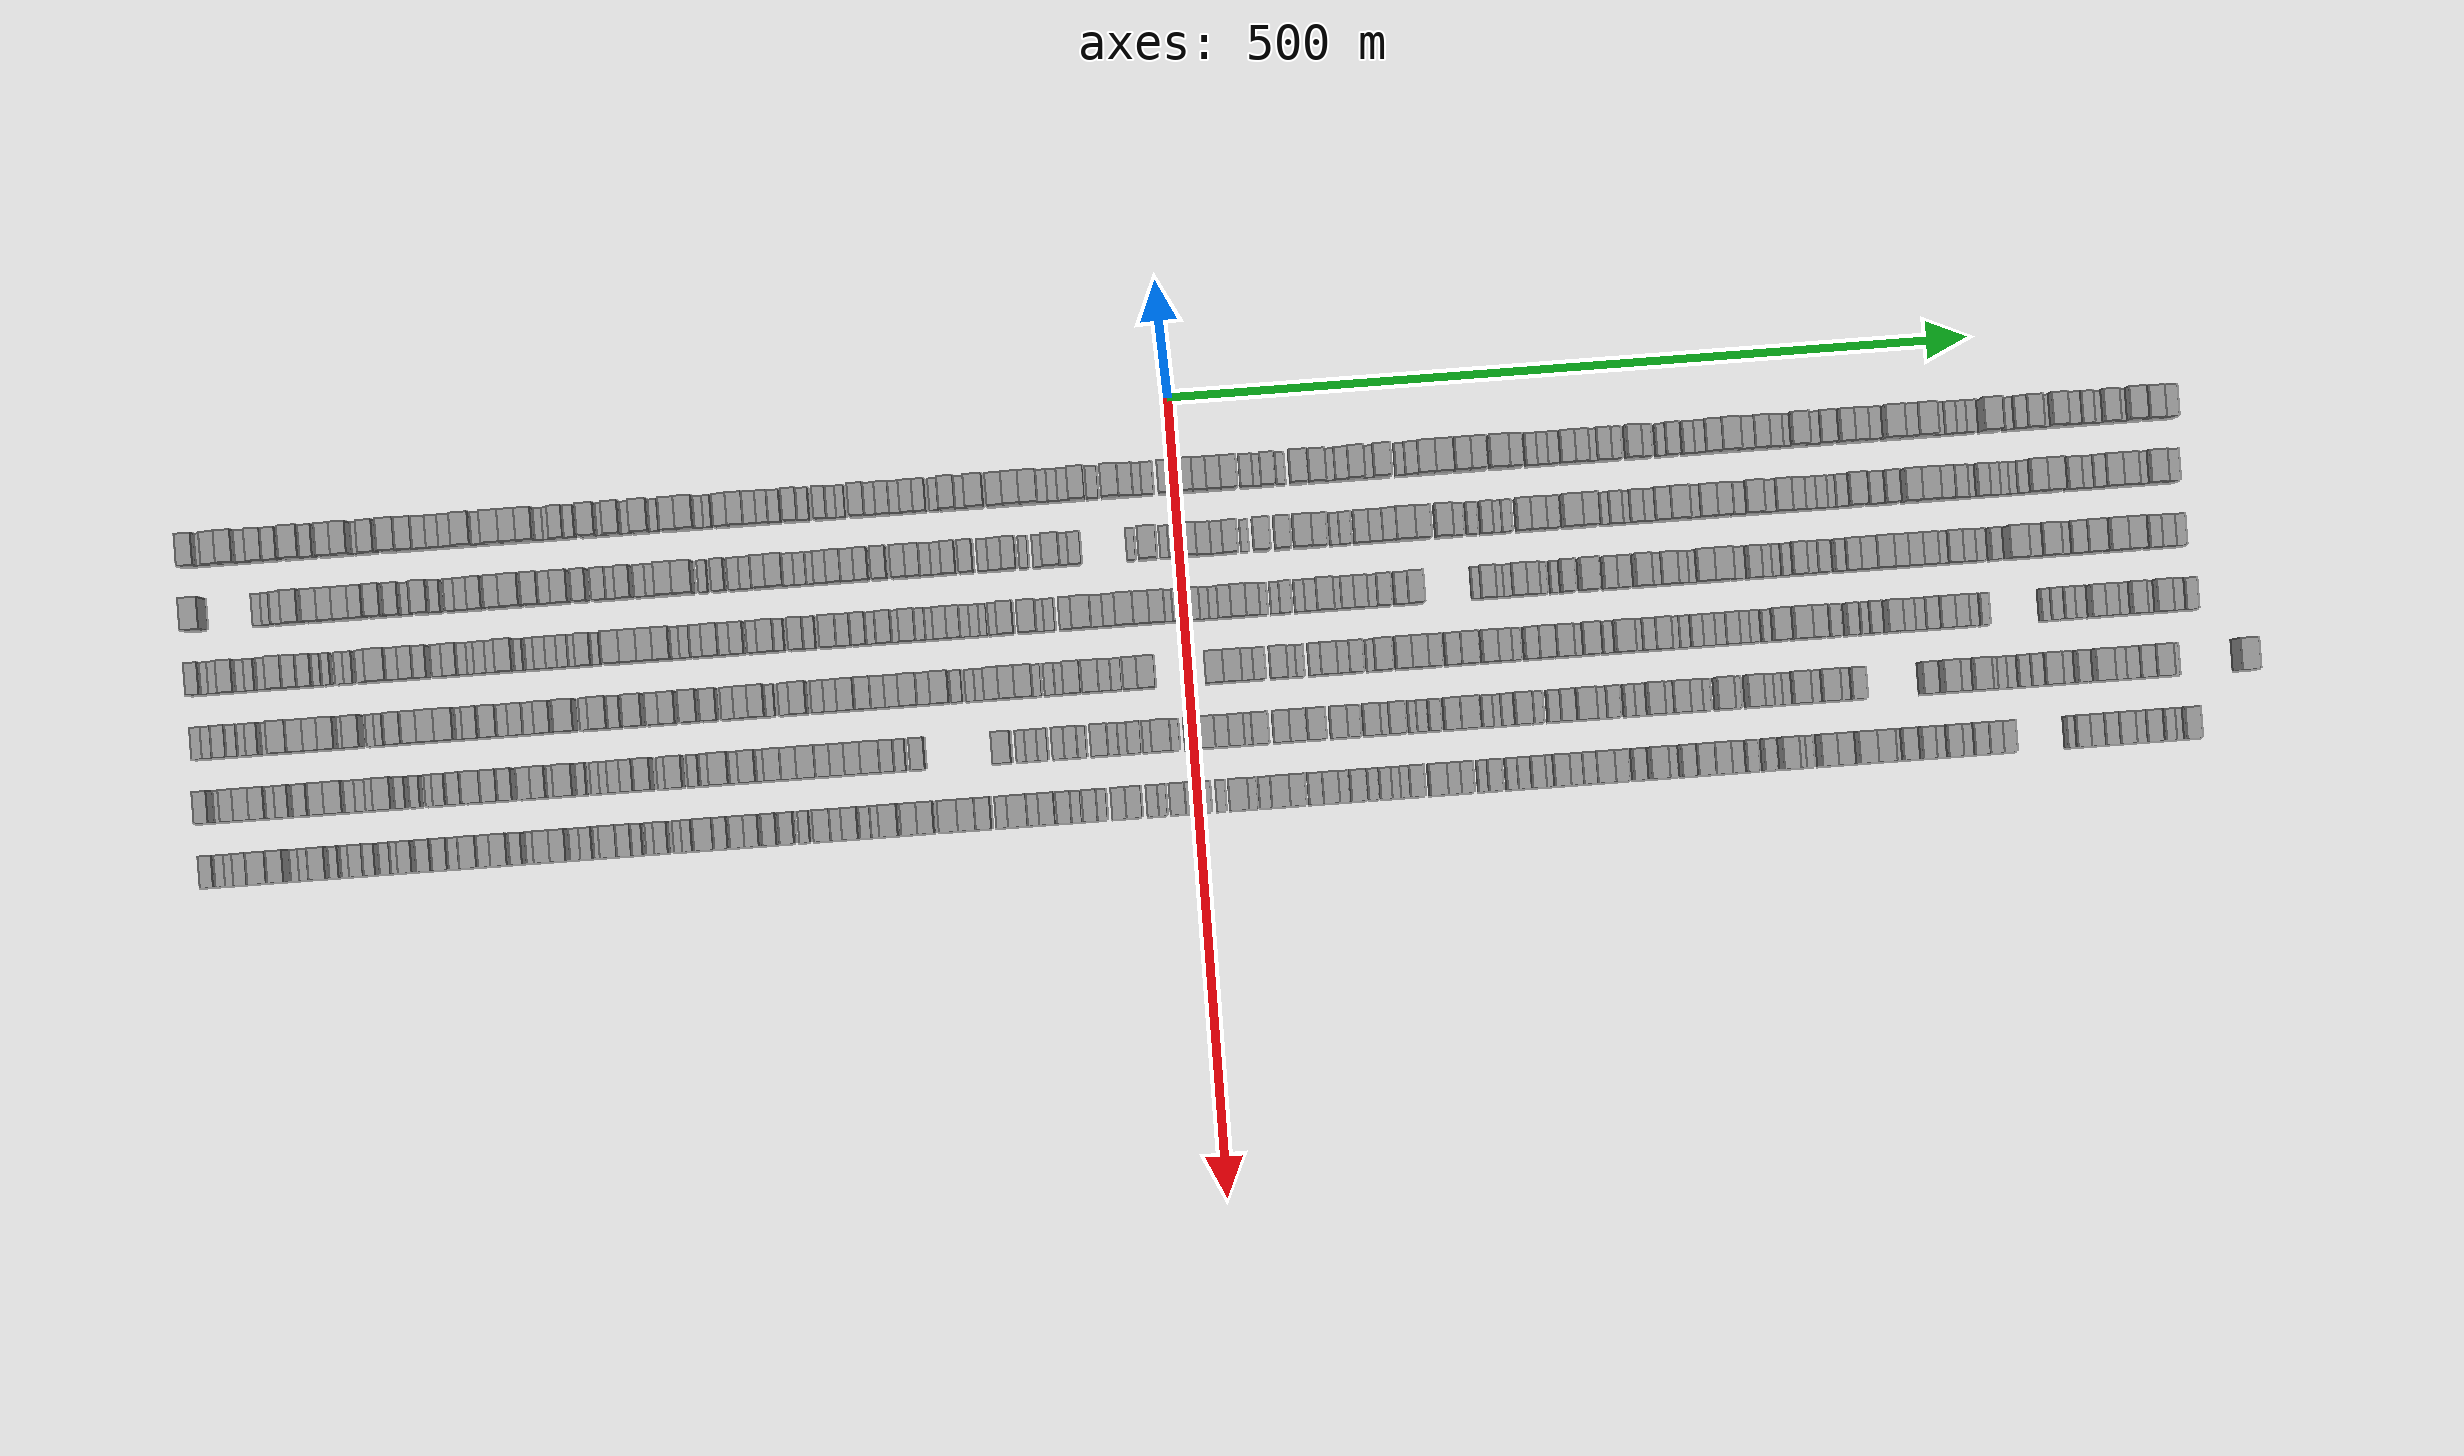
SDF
<sdf version="1.6">
 <world name="default">
  <scene>
   <sky><clouds><speed>12</speed></clouds></sky>
   <ambient>0.4 0.4 0.4 1</ambient>
   <background>0.7 0.7 0.7 1</background>
   <shadows>1</shadows>
  </scene>
  <gravity>0 0 -9.8066</gravity>
  <magnetic_field>6e-06 2.3e-05 -4.2e-05</magnetic_field>
  <physics default="0" name="default_physics" type="ode">
   <ode>
    <solver>
     <type>quick</type>
     <iters>10</iters>
     <sor>1.0</sor>
     <use_dynamic_moi_rescaling>0</use_dynamic_moi_rescaling>
    </solver>
    <constraints>
     <cfm>0</cfm>
     <erp>0.2</erp>
     <contact_max_correcting_vel>100</contact_max_correcting_vel>
     <contact_surface_layer>0.001</contact_surface_layer>
    </constraints>
   </ode>
   <max_step_size>0.004</max_step_size>
   <real_time_factor>1</real_time_factor>
   <real_time_update_rate>250</real_time_update_rate>
  </physics>
  <light name="sun" type="directional">
   <pose>0 0 10 0 0 0</pose>
   <diffuse>0.8 0.8 0.8 1</diffuse>
   <specular>0.2 0.2 0.2 1</specular>
   <attenuation>
    <range>1000</range>
    <constant>0.9</constant>
    <linear>0.01</linear>
    <quadratic>0.001</quadratic>
   </attenuation>
   <direction>-0.5 0.1 -0.9</direction>
  </light>
  <model name="building_1">
   <static>1</static>
   <pose>50.0000 -613.9658 0 0.000000 0.000000 0.000000</pose>
   <link name="link">
    <pose>0 0 10.50 0 0 0</pose>
    <collision name="collision"><geometry><box><size>20.0000 10.0684 21.0000</size></box></geometry></collision>
    <visual name="visual">
     <cast_shadows>0</cast_shadows>
     <geometry><box><size>20.0000 10.0684 21.0000</size></box></geometry>
     <material>
      <script>
       <uri>model://grey_wall/materials/scripts</uri>
       <uri>model://grey_wall/materials/textures</uri>
       <name>vrc/grey_wall</name>
      </script>
     </material>
    </visual>
   </link>
  </model>
  <model name="building_2">
   <static>1</static>
   <pose>50.0000 -606.3582 0 0.000000 0.000000 0.000000</pose>
   <link name="link">
    <pose>0 0 6.00 0 0 0</pose>
    <collision name="collision"><geometry><box><size>20.0000 5.1468 12.0000</size></box></geometry></collision>
    <visual name="visual">
     <cast_shadows>0</cast_shadows>
     <geometry><box><size>20.0000 5.1468 12.0000</size></box></geometry>
     <material>
      <script>
       <uri>model://grey_wall/materials/scripts</uri>
       <uri>model://grey_wall/materials/textures</uri>
       <name>vrc/grey_wall</name>
      </script>
     </material>
    </visual>
   </link>
  </model>
  <model name="building_3">
   <static>1</static>
   <pose>50.0000 -598.9114 0 0.000000 0.000000 0.000000</pose>
   <link name="link">
    <pose>0 0 10.50 0 0 0</pose>
    <collision name="collision"><geometry><box><size>20.0000 9.7468 21.0000</size></box></geometry></collision>
    <visual name="visual">
     <cast_shadows>0</cast_shadows>
     <geometry><box><size>20.0000 9.7468 21.0000</size></box></geometry>
     <material>
      <script>
       <uri>model://grey_wall/materials/scripts</uri>
       <uri>model://grey_wall/materials/textures</uri>
       <name>vrc/grey_wall</name>
      </script>
     </material>
    </visual>
   </link>
  </model>
  <model name="building_4">
   <static>1</static>
   <pose>50.0000 -588.9398 0 0.000000 0.000000 0.000000</pose>
   <link name="link">
    <pose>0 0 12.00 0 0 0</pose>
    <collision name="collision"><geometry><box><size>20.0000 10.1965 24.0000</size></box></geometry></collision>
    <visual name="visual">
     <cast_shadows>0</cast_shadows>
     <geometry><box><size>20.0000 10.1965 24.0000</size></box></geometry>
     <material>
      <script>
       <uri>model://grey_wall/materials/scripts</uri>
       <uri>model://grey_wall/materials/textures</uri>
       <name>vrc/grey_wall</name>
      </script>
     </material>
    </visual>
   </link>
  </model>
  <model name="building_5">
   <static>1</static>
   <pose>50.0000 -580.4396 0 0.000000 0.000000 0.000000</pose>
   <link name="link">
    <pose>0 0 7.50 0 0 0</pose>
    <collision name="collision"><geometry><box><size>20.0000 6.8040 15.0000</size></box></geometry></collision>
    <visual name="visual">
     <cast_shadows>0</cast_shadows>
     <geometry><box><size>20.0000 6.8040 15.0000</size></box></geometry>
     <material>
      <script>
       <uri>model://grey_wall/materials/scripts</uri>
       <uri>model://grey_wall/materials/textures</uri>
       <name>vrc/grey_wall</name>
      </script>
     </material>
    </visual>
   </link>
  </model>
  <model name="building_6">
   <static>1</static>
   <pose>50.0000 -571.2477 0 0.000000 0.000000 0.000000</pose>
   <link name="link">
    <pose>0 0 10.50 0 0 0</pose>
    <collision name="collision"><geometry><box><size>20.0000 9.5797 21.0000</size></box></geometry></collision>
    <visual name="visual">
     <cast_shadows>0</cast_shadows>
     <geometry><box><size>20.0000 9.5797 21.0000</size></box></geometry>
     <material>
      <script>
       <uri>model://grey_wall/materials/scripts</uri>
       <uri>model://grey_wall/materials/textures</uri>
       <name>vrc/grey_wall</name>
      </script>
     </material>
    </visual>
   </link>
  </model>
  <model name="building_7">
   <static>1</static>
   <pose>50.0000 -562.1629 0 0.000000 0.000000 0.000000</pose>
   <link name="link">
    <pose>0 0 9.00 0 0 0</pose>
    <collision name="collision"><geometry><box><size>20.0000 8.5899 18.0000</size></box></geometry></collision>
    <visual name="visual">
     <cast_shadows>0</cast_shadows>
     <geometry><box><size>20.0000 8.5899 18.0000</size></box></geometry>
     <material>
      <script>
       <uri>model://grey_wall/materials/scripts</uri>
       <uri>model://grey_wall/materials/textures</uri>
       <name>vrc/grey_wall</name>
      </script>
     </material>
    </visual>
   </link>
  </model>
  <model name="building_8">
   <static>1</static>
   <pose>50.0000 -549.0351 0 0.000000 0.000000 0.000000</pose>
   <link name="link">
    <pose>0 0 12.00 0 0 0</pose>
    <collision name="collision"><geometry><box><size>20.0000 11.6658 24.0000</size></box></geometry></collision>
    <visual name="visual">
     <cast_shadows>0</cast_shadows>
     <geometry><box><size>20.0000 11.6658 24.0000</size></box></geometry>
     <material>
      <script>
       <uri>model://grey_wall/materials/scripts</uri>
       <uri>model://grey_wall/materials/textures</uri>
       <name>vrc/grey_wall</name>
      </script>
     </material>
    </visual>
   </link>
  </model>
  <model name="building_9">
   <static>1</static>
   <pose>50.0000 -539.3212 0 0.000000 0.000000 0.000000</pose>
   <link name="link">
    <pose>0 0 9.00 0 0 0</pose>
    <collision name="collision"><geometry><box><size>20.0000 7.7619 18.0000</size></box></geometry></collision>
    <visual name="visual">
     <cast_shadows>0</cast_shadows>
     <geometry><box><size>20.0000 7.7619 18.0000</size></box></geometry>
     <material>
      <script>
       <uri>model://grey_wall/materials/scripts</uri>
       <uri>model://grey_wall/materials/textures</uri>
       <name>vrc/grey_wall</name>
      </script>
     </material>
    </visual>
   </link>
  </model>
  <model name="building_10">
   <static>1</static>
   <pose>50.0000 -527.6561 0 0.000000 0.000000 0.000000</pose>
   <link name="link">
    <pose>0 0 10.50 0 0 0</pose>
    <collision name="collision"><geometry><box><size>20.0000 9.5683 21.0000</size></box></geometry></collision>
    <visual name="visual">
     <cast_shadows>0</cast_shadows>
     <geometry><box><size>20.0000 9.5683 21.0000</size></box></geometry>
     <material>
      <script>
       <uri>model://grey_wall/materials/scripts</uri>
       <uri>model://grey_wall/materials/textures</uri>
       <name>vrc/grey_wall</name>
      </script>
     </material>
    </visual>
   </link>
  </model>
  <model name="building_11">
   <static>1</static>
   <pose>50.0000 -517.9128 0 0.000000 0.000000 0.000000</pose>
   <link name="link">
    <pose>0 0 12.00 0 0 0</pose>
    <collision name="collision"><geometry><box><size>20.0000 9.9184 24.0000</size></box></geometry></collision>
    <visual name="visual">
     <cast_shadows>0</cast_shadows>
     <geometry><box><size>20.0000 9.9184 24.0000</size></box></geometry>
     <material>
      <script>
       <uri>model://grey_wall/materials/scripts</uri>
       <uri>model://grey_wall/materials/textures</uri>
       <name>vrc/grey_wall</name>
      </script>
     </material>
    </visual>
   </link>
  </model>
  <model name="building_12">
   <static>1</static>
   <pose>50.0000 -509.3735 0 0.000000 0.000000 0.000000</pose>
   <link name="link">
    <pose>0 0 6.00 0 0 0</pose>
    <collision name="collision"><geometry><box><size>20.0000 5.1601 12.0000</size></box></geometry></collision>
    <visual name="visual">
     <cast_shadows>0</cast_shadows>
     <geometry><box><size>20.0000 5.1601 12.0000</size></box></geometry>
     <material>
      <script>
       <uri>model://grey_wall/materials/scripts</uri>
       <uri>model://grey_wall/materials/textures</uri>
       <name>vrc/grey_wall</name>
      </script>
     </material>
    </visual>
   </link>
  </model>
  <model name="building_13">
   <static>1</static>
   <pose>50.0000 -501.9229 0 0.000000 0.000000 0.000000</pose>
   <link name="link">
    <pose>0 0 10.50 0 0 0</pose>
    <collision name="collision"><geometry><box><size>20.0000 9.7411 21.0000</size></box></geometry></collision>
    <visual name="visual">
     <cast_shadows>0</cast_shadows>
     <geometry><box><size>20.0000 9.7411 21.0000</size></box></geometry>
     <material>
      <script>
       <uri>model://grey_wall/materials/scripts</uri>
       <uri>model://grey_wall/materials/textures</uri>
       <name>vrc/grey_wall</name>
      </script>
     </material>
    </visual>
   </link>
  </model>
  <model name="building_14">
   <static>1</static>
   <pose>50.0000 -488.6855 0 0.000000 0.000000 0.000000</pose>
   <link name="link">
    <pose>0 0 12.00 0 0 0</pose>
    <collision name="collision"><geometry><box><size>20.0000 10.7336 24.0000</size></box></geometry></collision>
    <visual name="visual">
     <cast_shadows>0</cast_shadows>
     <geometry><box><size>20.0000 10.7336 24.0000</size></box></geometry>
     <material>
      <script>
       <uri>model://grey_wall/materials/scripts</uri>
       <uri>model://grey_wall/materials/textures</uri>
       <name>vrc/grey_wall</name>
      </script>
     </material>
    </visual>
   </link>
  </model>
  <model name="building_15">
   <static>1</static>
   <pose>50.0000 -478.2708 0 0.000000 0.000000 0.000000</pose>
   <link name="link">
    <pose>0 0 10.50 0 0 0</pose>
    <collision name="collision"><geometry><box><size>20.0000 10.0958 21.0000</size></box></geometry></collision>
    <visual name="visual">
     <cast_shadows>0</cast_shadows>
     <geometry><box><size>20.0000 10.0958 21.0000</size></box></geometry>
     <material>
      <script>
       <uri>model://grey_wall/materials/scripts</uri>
       <uri>model://grey_wall/materials/textures</uri>
       <name>vrc/grey_wall</name>
      </script>
     </material>
    </visual>
   </link>
  </model>
  <model name="building_16">
   <static>1</static>
   <pose>50.0000 -468.9750 0 0.000000 0.000000 0.000000</pose>
   <link name="link">
    <pose>0 0 9.00 0 0 0</pose>
    <collision name="collision"><geometry><box><size>20.0000 8.4958 18.0000</size></box></geometry></collision>
    <visual name="visual">
     <cast_shadows>0</cast_shadows>
     <geometry><box><size>20.0000 8.4958 18.0000</size></box></geometry>
     <material>
      <script>
       <uri>model://grey_wall/materials/scripts</uri>
       <uri>model://grey_wall/materials/textures</uri>
       <name>vrc/grey_wall</name>
      </script>
     </material>
    </visual>
   </link>
  </model>
  <model name="building_17">
   <static>1</static>
   <pose>50.0000 -460.8340 0 0.000000 0.000000 0.000000</pose>
   <link name="link">
    <pose>0 0 9.00 0 0 0</pose>
    <collision name="collision"><geometry><box><size>20.0000 7.7862 18.0000</size></box></geometry></collision>
    <visual name="visual">
     <cast_shadows>0</cast_shadows>
     <geometry><box><size>20.0000 7.7862 18.0000</size></box></geometry>
     <material>
      <script>
       <uri>model://grey_wall/materials/scripts</uri>
       <uri>model://grey_wall/materials/textures</uri>
       <name>vrc/grey_wall</name>
      </script>
     </material>
    </visual>
   </link>
  </model>
  <model name="building_18">
   <static>1</static>
   <pose>50.0000 -452.6051 0 0.000000 0.000000 0.000000</pose>
   <link name="link">
    <pose>0 0 9.00 0 0 0</pose>
    <collision name="collision"><geometry><box><size>20.0000 8.6716 18.0000</size></box></geometry></collision>
    <visual name="visual">
     <cast_shadows>0</cast_shadows>
     <geometry><box><size>20.0000 8.6716 18.0000</size></box></geometry>
     <material>
      <script>
       <uri>model://grey_wall/materials/scripts</uri>
       <uri>model://grey_wall/materials/textures</uri>
       <name>vrc/grey_wall</name>
      </script>
     </material>
    </visual>
   </link>
  </model>
  <model name="building_19">
   <static>1</static>
   <pose>50.0000 -442.5982 0 0.000000 0.000000 0.000000</pose>
   <link name="link">
    <pose>0 0 12.00 0 0 0</pose>
    <collision name="collision"><geometry><box><size>20.0000 11.3421 24.0000</size></box></geometry></collision>
    <visual name="visual">
     <cast_shadows>0</cast_shadows>
     <geometry><box><size>20.0000 11.3421 24.0000</size></box></geometry>
     <material>
      <script>
       <uri>model://grey_wall/materials/scripts</uri>
       <uri>model://grey_wall/materials/textures</uri>
       <name>vrc/grey_wall</name>
      </script>
     </material>
    </visual>
   </link>
  </model>
  <model name="building_20">
   <static>1</static>
   <pose>50.0000 -433.3736 0 0.000000 0.000000 0.000000</pose>
   <link name="link">
    <pose>0 0 7.50 0 0 0</pose>
    <collision name="collision"><geometry><box><size>20.0000 7.1072 15.0000</size></box></geometry></collision>
    <visual name="visual">
     <cast_shadows>0</cast_shadows>
     <geometry><box><size>20.0000 7.1072 15.0000</size></box></geometry>
     <material>
      <script>
       <uri>model://grey_wall/materials/scripts</uri>
       <uri>model://grey_wall/materials/textures</uri>
       <name>vrc/grey_wall</name>
      </script>
     </material>
    </visual>
   </link>
  </model>
  <model name="building_21">
   <static>1</static>
   <pose>50.0000 -424.1923 0 0.000000 0.000000 0.000000</pose>
   <link name="link">
    <pose>0 0 12.00 0 0 0</pose>
    <collision name="collision"><geometry><box><size>20.0000 11.2555 24.0000</size></box></geometry></collision>
    <visual name="visual">
     <cast_shadows>0</cast_shadows>
     <geometry><box><size>20.0000 11.2555 24.0000</size></box></geometry>
     <material>
      <script>
       <uri>model://grey_wall/materials/scripts</uri>
       <uri>model://grey_wall/materials/textures</uri>
       <name>vrc/grey_wall</name>
      </script>
     </material>
    </visual>
   </link>
  </model>
  <model name="building_22">
   <static>1</static>
   <pose>50.0000 -413.3363 0 0.000000 0.000000 0.000000</pose>
   <link name="link">
    <pose>0 0 12.00 0 0 0</pose>
    <collision name="collision"><geometry><box><size>20.0000 10.4565 24.0000</size></box></geometry></collision>
    <visual name="visual">
     <cast_shadows>0</cast_shadows>
     <geometry><box><size>20.0000 10.4565 24.0000</size></box></geometry>
     <material>
      <script>
       <uri>model://grey_wall/materials/scripts</uri>
       <uri>model://grey_wall/materials/textures</uri>
       <name>vrc/grey_wall</name>
      </script>
     </material>
    </visual>
   </link>
  </model>
  <model name="building_23">
   <static>1</static>
   <pose>50.0000 -403.1218 0 0.000000 0.000000 0.000000</pose>
   <link name="link">
    <pose>0 0 12.00 0 0 0</pose>
    <collision name="collision"><geometry><box><size>20.0000 9.9726 24.0000</size></box></geometry></collision>
    <visual name="visual">
     <cast_shadows>0</cast_shadows>
     <geometry><box><size>20.0000 9.9726 24.0000</size></box></geometry>
     <material>
      <script>
       <uri>model://grey_wall/materials/scripts</uri>
       <uri>model://grey_wall/materials/textures</uri>
       <name>vrc/grey_wall</name>
      </script>
     </material>
    </visual>
   </link>
  </model>
  <model name="building_24">
   <static>1</static>
   <pose>50.0000 -395.5528 0 0.000000 0.000000 0.000000</pose>
   <link name="link">
    <pose>0 0 6.00 0 0 0</pose>
    <collision name="collision"><geometry><box><size>20.0000 5.1653 12.0000</size></box></geometry></collision>
    <visual name="visual">
     <cast_shadows>0</cast_shadows>
     <geometry><box><size>20.0000 5.1653 12.0000</size></box></geometry>
     <material>
      <script>
       <uri>model://grey_wall/materials/scripts</uri>
       <uri>model://grey_wall/materials/textures</uri>
       <name>vrc/grey_wall</name>
      </script>
     </material>
    </visual>
   </link>
  </model>
  <model name="building_25">
   <static>1</static>
   <pose>50.0000 -390.5702 0 0.000000 0.000000 0.000000</pose>
   <link name="link">
    <pose>0 0 6.00 0 0 0</pose>
    <collision name="collision"><geometry><box><size>20.0000 4.8000 12.0000</size></box></geometry></collision>
    <visual name="visual">
     <cast_shadows>0</cast_shadows>
     <geometry><box><size>20.0000 4.8000 12.0000</size></box></geometry>
     <material>
      <script>
       <uri>model://grey_wall/materials/scripts</uri>
       <uri>model://grey_wall/materials/textures</uri>
       <name>vrc/grey_wall</name>
      </script>
     </material>
    </visual>
   </link>
  </model>
  <model name="building_26">
   <static>1</static>
   <pose>50.0000 -383.8845 0 0.000000 0.000000 0.000000</pose>
   <link name="link">
    <pose>0 0 10.50 0 0 0</pose>
    <collision name="collision"><geometry><box><size>20.0000 8.5712 21.0000</size></box></geometry></collision>
    <visual name="visual">
     <cast_shadows>0</cast_shadows>
     <geometry><box><size>20.0000 8.5712 21.0000</size></box></geometry>
     <material>
      <script>
       <uri>model://grey_wall/materials/scripts</uri>
       <uri>model://grey_wall/materials/textures</uri>
       <name>vrc/grey_wall</name>
      </script>
     </material>
    </visual>
   </link>
  </model>
  <model name="building_27">
   <static>1</static>
   <pose>50.0000 -376.3805 0 0.000000 0.000000 0.000000</pose>
   <link name="link">
    <pose>0 0 7.50 0 0 0</pose>
    <collision name="collision"><geometry><box><size>20.0000 6.4369 15.0000</size></box></geometry></collision>
    <visual name="visual">
     <cast_shadows>0</cast_shadows>
     <geometry><box><size>20.0000 6.4369 15.0000</size></box></geometry>
     <material>
      <script>
       <uri>model://grey_wall/materials/scripts</uri>
       <uri>model://grey_wall/materials/textures</uri>
       <name>vrc/grey_wall</name>
      </script>
     </material>
    </visual>
   </link>
  </model>
  <model name="building_28">
   <static>1</static>
   <pose>50.0000 -364.8503 0 0.000000 0.000000 0.000000</pose>
   <link name="link">
    <pose>0 0 12.00 0 0 0</pose>
    <collision name="collision"><geometry><box><size>20.0000 10.6233 24.0000</size></box></geometry></collision>
    <visual name="visual">
     <cast_shadows>0</cast_shadows>
     <geometry><box><size>20.0000 10.6233 24.0000</size></box></geometry>
     <material>
      <script>
       <uri>model://grey_wall/materials/scripts</uri>
       <uri>model://grey_wall/materials/textures</uri>
       <name>vrc/grey_wall</name>
      </script>
     </material>
    </visual>
   </link>
  </model>
  <model name="building_29">
   <static>1</static>
   <pose>50.0000 -356.9656 0 0.000000 0.000000 0.000000</pose>
   <link name="link">
    <pose>0 0 6.00 0 0 0</pose>
    <collision name="collision"><geometry><box><size>20.0000 5.1462 12.0000</size></box></geometry></collision>
    <visual name="visual">
     <cast_shadows>0</cast_shadows>
     <geometry><box><size>20.0000 5.1462 12.0000</size></box></geometry>
     <material>
      <script>
       <uri>model://grey_wall/materials/scripts</uri>
       <uri>model://grey_wall/materials/textures</uri>
       <name>vrc/grey_wall</name>
      </script>
     </material>
    </visual>
   </link>
  </model>
  <model name="building_30">
   <static>1</static>
   <pose>50.0000 -349.3893 0 0.000000 0.000000 0.000000</pose>
   <link name="link">
    <pose>0 0 12.00 0 0 0</pose>
    <collision name="collision"><geometry><box><size>20.0000 10.0063 24.0000</size></box></geometry></collision>
    <visual name="visual">
     <cast_shadows>0</cast_shadows>
     <geometry><box><size>20.0000 10.0063 24.0000</size></box></geometry>
     <material>
      <script>
       <uri>model://grey_wall/materials/scripts</uri>
       <uri>model://grey_wall/materials/textures</uri>
       <name>vrc/grey_wall</name>
      </script>
     </material>
    </visual>
   </link>
  </model>
  <model name="building_31">
   <static>1</static>
   <pose>50.0000 -341.5780 0 0.000000 0.000000 0.000000</pose>
   <link name="link">
    <pose>0 0 6.00 0 0 0</pose>
    <collision name="collision"><geometry><box><size>20.0000 5.6164 12.0000</size></box></geometry></collision>
    <visual name="visual">
     <cast_shadows>0</cast_shadows>
     <geometry><box><size>20.0000 5.6164 12.0000</size></box></geometry>
     <material>
      <script>
       <uri>model://grey_wall/materials/scripts</uri>
       <uri>model://grey_wall/materials/textures</uri>
       <name>vrc/grey_wall</name>
      </script>
     </material>
    </visual>
   </link>
  </model>
  <model name="building_32">
   <static>1</static>
   <pose>50.0000 -332.2388 0 0.000000 0.000000 0.000000</pose>
   <link name="link">
    <pose>0 0 12.00 0 0 0</pose>
    <collision name="collision"><geometry><box><size>20.0000 11.0620 24.0000</size></box></geometry></collision>
    <visual name="visual">
     <cast_shadows>0</cast_shadows>
     <geometry><box><size>20.0000 11.0620 24.0000</size></box></geometry>
     <material>
      <script>
       <uri>model://grey_wall/materials/scripts</uri>
       <uri>model://grey_wall/materials/textures</uri>
       <name>vrc/grey_wall</name>
      </script>
     </material>
    </visual>
   </link>
  </model>
  <model name="building_33">
   <static>1</static>
   <pose>50.0000 -324.0126 0 0.000000 0.000000 0.000000</pose>
   <link name="link">
    <pose>0 0 6.00 0 0 0</pose>
    <collision name="collision"><geometry><box><size>20.0000 5.3904 12.0000</size></box></geometry></collision>
    <visual name="visual">
     <cast_shadows>0</cast_shadows>
     <geometry><box><size>20.0000 5.3904 12.0000</size></box></geometry>
     <material>
      <script>
       <uri>model://grey_wall/materials/scripts</uri>
       <uri>model://grey_wall/materials/textures</uri>
       <name>vrc/grey_wall</name>
      </script>
     </material>
    </visual>
   </link>
  </model>
  <model name="building_34">
   <static>1</static>
   <pose>50.0000 -314.4195 0 0.000000 0.000000 0.000000</pose>
   <link name="link">
    <pose>0 0 10.50 0 0 0</pose>
    <collision name="collision"><geometry><box><size>20.0000 9.7957 21.0000</size></box></geometry></collision>
    <visual name="visual">
     <cast_shadows>0</cast_shadows>
     <geometry><box><size>20.0000 9.7957 21.0000</size></box></geometry>
     <material>
      <script>
       <uri>model://grey_wall/materials/scripts</uri>
       <uri>model://grey_wall/materials/textures</uri>
       <name>vrc/grey_wall</name>
      </script>
     </material>
    </visual>
   </link>
  </model>
  <model name="building_35">
   <static>1</static>
   <pose>50.0000 -304.1381 0 0.000000 0.000000 0.000000</pose>
   <link name="link">
    <pose>0 0 12.00 0 0 0</pose>
    <collision name="collision"><geometry><box><size>20.0000 10.7670 24.0000</size></box></geometry></collision>
    <visual name="visual">
     <cast_shadows>0</cast_shadows>
     <geometry><box><size>20.0000 10.7670 24.0000</size></box></geometry>
     <material>
      <script>
       <uri>model://grey_wall/materials/scripts</uri>
       <uri>model://grey_wall/materials/textures</uri>
       <name>vrc/grey_wall</name>
      </script>
     </material>
    </visual>
   </link>
  </model>
  <model name="building_36">
   <static>1</static>
   <pose>50.0000 -296.0184 0 0.000000 0.000000 0.000000</pose>
   <link name="link">
    <pose>0 0 6.00 0 0 0</pose>
    <collision name="collision"><geometry><box><size>20.0000 5.4725 12.0000</size></box></geometry></collision>
    <visual name="visual">
     <cast_shadows>0</cast_shadows>
     <geometry><box><size>20.0000 5.4725 12.0000</size></box></geometry>
     <material>
      <script>
       <uri>model://grey_wall/materials/scripts</uri>
       <uri>model://grey_wall/materials/textures</uri>
       <name>vrc/grey_wall</name>
      </script>
     </material>
    </visual>
   </link>
  </model>
  <model name="building_37">
   <static>1</static>
   <pose>50.0000 -290.8451 0 0.000000 0.000000 0.000000</pose>
   <link name="link">
    <pose>0 0 6.00 0 0 0</pose>
    <collision name="collision"><geometry><box><size>20.0000 4.8742 12.0000</size></box></geometry></collision>
    <visual name="visual">
     <cast_shadows>0</cast_shadows>
     <geometry><box><size>20.0000 4.8742 12.0000</size></box></geometry>
     <material>
      <script>
       <uri>model://grey_wall/materials/scripts</uri>
       <uri>model://grey_wall/materials/textures</uri>
       <name>vrc/grey_wall</name>
      </script>
     </material>
    </visual>
   </link>
  </model>
  <model name="building_38">
   <static>1</static>
   <pose>50.0000 -282.0575 0 0.000000 0.000000 0.000000</pose>
   <link name="link">
    <pose>0 0 9.00 0 0 0</pose>
    <collision name="collision"><geometry><box><size>20.0000 8.7010 18.0000</size></box></geometry></collision>
    <visual name="visual">
     <cast_shadows>0</cast_shadows>
     <geometry><box><size>20.0000 8.7010 18.0000</size></box></geometry>
     <material>
      <script>
       <uri>model://grey_wall/materials/scripts</uri>
       <uri>model://grey_wall/materials/textures</uri>
       <name>vrc/grey_wall</name>
      </script>
     </material>
    </visual>
   </link>
  </model>
  <model name="building_39">
   <static>1</static>
   <pose>50.0000 -272.7691 0 0.000000 0.000000 0.000000</pose>
   <link name="link">
    <pose>0 0 10.50 0 0 0</pose>
    <collision name="collision"><geometry><box><size>20.0000 9.8757 21.0000</size></box></geometry></collision>
    <visual name="visual">
     <cast_shadows>0</cast_shadows>
     <geometry><box><size>20.0000 9.8757 21.0000</size></box></geometry>
     <material>
      <script>
       <uri>model://grey_wall/materials/scripts</uri>
       <uri>model://grey_wall/materials/textures</uri>
       <name>vrc/grey_wall</name>
      </script>
     </material>
    </visual>
   </link>
  </model>
  <model name="building_40">
   <static>1</static>
   <pose>50.0000 -263.8020 0 0.000000 0.000000 0.000000</pose>
   <link name="link">
    <pose>0 0 9.00 0 0 0</pose>
    <collision name="collision"><geometry><box><size>20.0000 8.0586 18.0000</size></box></geometry></collision>
    <visual name="visual">
     <cast_shadows>0</cast_shadows>
     <geometry><box><size>20.0000 8.0586 18.0000</size></box></geometry>
     <material>
      <script>
       <uri>model://grey_wall/materials/scripts</uri>
       <uri>model://grey_wall/materials/textures</uri>
       <name>vrc/grey_wall</name>
      </script>
     </material>
    </visual>
   </link>
  </model>
  <model name="building_41">
   <static>1</static>
   <pose>50.0000 -256.1643 0 0.000000 0.000000 0.000000</pose>
   <link name="link">
    <pose>0 0 9.00 0 0 0</pose>
    <collision name="collision"><geometry><box><size>20.0000 7.2168 18.0000</size></box></geometry></collision>
    <visual name="visual">
     <cast_shadows>0</cast_shadows>
     <geometry><box><size>20.0000 7.2168 18.0000</size></box></geometry>
     <material>
      <script>
       <uri>model://grey_wall/materials/scripts</uri>
       <uri>model://grey_wall/materials/textures</uri>
       <name>vrc/grey_wall</name>
      </script>
     </material>
    </visual>
   </link>
  </model>
  <model name="building_42">
   <static>1</static>
   <pose>50.0000 -248.8913 0 0.000000 0.000000 0.000000</pose>
   <link name="link">
    <pose>0 0 7.50 0 0 0</pose>
    <collision name="collision"><geometry><box><size>20.0000 7.3291 15.0000</size></box></geometry></collision>
    <visual name="visual">
     <cast_shadows>0</cast_shadows>
     <geometry><box><size>20.0000 7.3291 15.0000</size></box></geometry>
     <material>
      <script>
       <uri>model://grey_wall/materials/scripts</uri>
       <uri>model://grey_wall/materials/textures</uri>
       <name>vrc/grey_wall</name>
      </script>
     </material>
    </visual>
   </link>
  </model>
  <model name="building_43">
   <static>1</static>
   <pose>50.0000 -238.8344 0 0.000000 0.000000 0.000000</pose>
   <link name="link">
    <pose>0 0 10.50 0 0 0</pose>
    <collision name="collision"><geometry><box><size>20.0000 8.7847 21.0000</size></box></geometry></collision>
    <visual name="visual">
     <cast_shadows>0</cast_shadows>
     <geometry><box><size>20.0000 8.7847 21.0000</size></box></geometry>
     <material>
      <script>
       <uri>model://grey_wall/materials/scripts</uri>
       <uri>model://grey_wall/materials/textures</uri>
       <name>vrc/grey_wall</name>
      </script>
     </material>
    </visual>
   </link>
  </model>
  <model name="building_44">
   <static>1</static>
   <pose>50.0000 -230.8882 0 0.000000 0.000000 0.000000</pose>
   <link name="link">
    <pose>0 0 7.50 0 0 0</pose>
    <collision name="collision"><geometry><box><size>20.0000 7.1078 15.0000</size></box></geometry></collision>
    <visual name="visual">
     <cast_shadows>0</cast_shadows>
     <geometry><box><size>20.0000 7.1078 15.0000</size></box></geometry>
     <material>
      <script>
       <uri>model://grey_wall/materials/scripts</uri>
       <uri>model://grey_wall/materials/textures</uri>
       <name>vrc/grey_wall</name>
      </script>
     </material>
    </visual>
   </link>
  </model>
  <model name="building_45">
   <static>1</static>
   <pose>50.0000 -220.4508 0 0.000000 0.000000 0.000000</pose>
   <link name="link">
    <pose>0 0 9.00 0 0 0</pose>
    <collision name="collision"><geometry><box><size>20.0000 7.7671 18.0000</size></box></geometry></collision>
    <visual name="visual">
     <cast_shadows>0</cast_shadows>
     <geometry><box><size>20.0000 7.7671 18.0000</size></box></geometry>
     <material>
      <script>
       <uri>model://grey_wall/materials/scripts</uri>
       <uri>model://grey_wall/materials/textures</uri>
       <name>vrc/grey_wall</name>
      </script>
     </material>
    </visual>
   </link>
  </model>
  <model name="building_46">
   <static>1</static>
   <pose>50.0000 -213.6460 0 0.000000 0.000000 0.000000</pose>
   <link name="link">
    <pose>0 0 6.00 0 0 0</pose>
    <collision name="collision"><geometry><box><size>20.0000 5.8425 12.0000</size></box></geometry></collision>
    <visual name="visual">
     <cast_shadows>0</cast_shadows>
     <geometry><box><size>20.0000 5.8425 12.0000</size></box></geometry>
     <material>
      <script>
       <uri>model://grey_wall/materials/scripts</uri>
       <uri>model://grey_wall/materials/textures</uri>
       <name>vrc/grey_wall</name>
      </script>
     </material>
    </visual>
   </link>
  </model>
  <model name="building_47">
   <static>1</static>
   <pose>50.0000 -207.9243 0 0.000000 0.000000 0.000000</pose>
   <link name="link">
    <pose>0 0 6.00 0 0 0</pose>
    <collision name="collision"><geometry><box><size>20.0000 5.6009 12.0000</size></box></geometry></collision>
    <visual name="visual">
     <cast_shadows>0</cast_shadows>
     <geometry><box><size>20.0000 5.6009 12.0000</size></box></geometry>
     <material>
      <script>
       <uri>model://grey_wall/materials/scripts</uri>
       <uri>model://grey_wall/materials/textures</uri>
       <name>vrc/grey_wall</name>
      </script>
     </material>
    </visual>
   </link>
  </model>
  <model name="building_48">
   <static>1</static>
   <pose>50.0000 -197.4473 0 0.000000 0.000000 0.000000</pose>
   <link name="link">
    <pose>0 0 10.50 0 0 0</pose>
    <collision name="collision"><geometry><box><size>20.0000 9.3530 21.0000</size></box></geometry></collision>
    <visual name="visual">
     <cast_shadows>0</cast_shadows>
     <geometry><box><size>20.0000 9.3530 21.0000</size></box></geometry>
     <material>
      <script>
       <uri>model://grey_wall/materials/scripts</uri>
       <uri>model://grey_wall/materials/textures</uri>
       <name>vrc/grey_wall</name>
      </script>
     </material>
    </visual>
   </link>
  </model>
  <model name="building_49">
   <static>1</static>
   <pose>50.0000 -189.2440 0 0.000000 0.000000 0.000000</pose>
   <link name="link">
    <pose>0 0 7.50 0 0 0</pose>
    <collision name="collision"><geometry><box><size>20.0000 7.0538 15.0000</size></box></geometry></collision>
    <visual name="visual">
     <cast_shadows>0</cast_shadows>
     <geometry><box><size>20.0000 7.0538 15.0000</size></box></geometry>
     <material>
      <script>
       <uri>model://grey_wall/materials/scripts</uri>
       <uri>model://grey_wall/materials/textures</uri>
       <name>vrc/grey_wall</name>
      </script>
     </material>
    </visual>
   </link>
  </model>
  <model name="building_50">
   <static>1</static>
   <pose>50.0000 -181.5211 0 0.000000 0.000000 0.000000</pose>
   <link name="link">
    <pose>0 0 9.00 0 0 0</pose>
    <collision name="collision"><geometry><box><size>20.0000 8.3919 18.0000</size></box></geometry></collision>
    <visual name="visual">
     <cast_shadows>0</cast_shadows>
     <geometry><box><size>20.0000 8.3919 18.0000</size></box></geometry>
     <material>
      <script>
       <uri>model://grey_wall/materials/scripts</uri>
       <uri>model://grey_wall/materials/textures</uri>
       <name>vrc/grey_wall</name>
      </script>
     </material>
    </visual>
   </link>
  </model>
  <model name="building_51">
   <static>1</static>
   <pose>50.0000 -174.0268 0 0.000000 0.000000 0.000000</pose>
   <link name="link">
    <pose>0 0 7.50 0 0 0</pose>
    <collision name="collision"><geometry><box><size>20.0000 6.5966 15.0000</size></box></geometry></collision>
    <visual name="visual">
     <cast_shadows>0</cast_shadows>
     <geometry><box><size>20.0000 6.5966 15.0000</size></box></geometry>
     <material>
      <script>
       <uri>model://grey_wall/materials/scripts</uri>
       <uri>model://grey_wall/materials/textures</uri>
       <name>vrc/grey_wall</name>
      </script>
     </material>
    </visual>
   </link>
  </model>
  <model name="building_52">
   <static>1</static>
   <pose>50.0000 -166.6360 0 0.000000 0.000000 0.000000</pose>
   <link name="link">
    <pose>0 0 9.00 0 0 0</pose>
    <collision name="collision"><geometry><box><size>20.0000 8.1851 18.0000</size></box></geometry></collision>
    <visual name="visual">
     <cast_shadows>0</cast_shadows>
     <geometry><box><size>20.0000 8.1851 18.0000</size></box></geometry>
     <material>
      <script>
       <uri>model://grey_wall/materials/scripts</uri>
       <uri>model://grey_wall/materials/textures</uri>
       <name>vrc/grey_wall</name>
      </script>
     </material>
    </visual>
   </link>
  </model>
  <model name="building_53">
   <static>1</static>
   <pose>50.0000 -158.6678 0 0.000000 0.000000 0.000000</pose>
   <link name="link">
    <pose>0 0 9.00 0 0 0</pose>
    <collision name="collision"><geometry><box><size>20.0000 7.7513 18.0000</size></box></geometry></collision>
    <visual name="visual">
     <cast_shadows>0</cast_shadows>
     <geometry><box><size>20.0000 7.7513 18.0000</size></box></geometry>
     <material>
      <script>
       <uri>model://grey_wall/materials/scripts</uri>
       <uri>model://grey_wall/materials/textures</uri>
       <name>vrc/grey_wall</name>
      </script>
     </material>
    </visual>
   </link>
  </model>
  <model name="building_54">
   <static>1</static>
   <pose>50.0000 -150.0392 0 0.000000 0.000000 0.000000</pose>
   <link name="link">
    <pose>0 0 6.00 0 0 0</pose>
    <collision name="collision"><geometry><box><size>20.0000 5.5058 12.0000</size></box></geometry></collision>
    <visual name="visual">
     <cast_shadows>0</cast_shadows>
     <geometry><box><size>20.0000 5.5058 12.0000</size></box></geometry>
     <material>
      <script>
       <uri>model://grey_wall/materials/scripts</uri>
       <uri>model://grey_wall/materials/textures</uri>
       <name>vrc/grey_wall</name>
      </script>
     </material>
    </visual>
   </link>
  </model>
  <model name="building_55">
   <static>1</static>
   <pose>50.0000 -141.3399 0 0.000000 0.000000 0.000000</pose>
   <link name="link">
    <pose>0 0 12.00 0 0 0</pose>
    <collision name="collision"><geometry><box><size>20.0000 9.8928 24.0000</size></box></geometry></collision>
    <visual name="visual">
     <cast_shadows>0</cast_shadows>
     <geometry><box><size>20.0000 9.8928 24.0000</size></box></geometry>
     <material>
      <script>
       <uri>model://grey_wall/materials/scripts</uri>
       <uri>model://grey_wall/materials/textures</uri>
       <name>vrc/grey_wall</name>
      </script>
     </material>
    </visual>
   </link>
  </model>
  <model name="building_56">
   <static>1</static>
   <pose>50.0000 -133.2379 0 0.000000 0.000000 0.000000</pose>
   <link name="link">
    <pose>0 0 7.50 0 0 0</pose>
    <collision name="collision"><geometry><box><size>20.0000 6.3112 15.0000</size></box></geometry></collision>
    <visual name="visual">
     <cast_shadows>0</cast_shadows>
     <geometry><box><size>20.0000 6.3112 15.0000</size></box></geometry>
     <material>
      <script>
       <uri>model://grey_wall/materials/scripts</uri>
       <uri>model://grey_wall/materials/textures</uri>
       <name>vrc/grey_wall</name>
      </script>
     </material>
    </visual>
   </link>
  </model>
  <model name="building_57">
   <static>1</static>
   <pose>50.0000 -124.4303 0 0.000000 0.000000 0.000000</pose>
   <link name="link">
    <pose>0 0 12.00 0 0 0</pose>
    <collision name="collision"><geometry><box><size>20.0000 11.3040 24.0000</size></box></geometry></collision>
    <visual name="visual">
     <cast_shadows>0</cast_shadows>
     <geometry><box><size>20.0000 11.3040 24.0000</size></box></geometry>
     <material>
      <script>
       <uri>model://grey_wall/materials/scripts</uri>
       <uri>model://grey_wall/materials/textures</uri>
       <name>vrc/grey_wall</name>
      </script>
     </material>
    </visual>
   </link>
  </model>
  <model name="building_58">
   <static>1</static>
   <pose>50.0000 -111.8070 0 0.000000 0.000000 0.000000</pose>
   <link name="link">
    <pose>0 0 10.50 0 0 0</pose>
    <collision name="collision"><geometry><box><size>20.0000 9.9426 21.0000</size></box></geometry></collision>
    <visual name="visual">
     <cast_shadows>0</cast_shadows>
     <geometry><box><size>20.0000 9.9426 21.0000</size></box></geometry>
     <material>
      <script>
       <uri>model://grey_wall/materials/scripts</uri>
       <uri>model://grey_wall/materials/textures</uri>
       <name>vrc/grey_wall</name>
      </script>
     </material>
    </visual>
   </link>
  </model>
  <model name="building_59">
   <static>1</static>
   <pose>50.0000 -101.6585 0 0.000000 0.000000 0.000000</pose>
   <link name="link">
    <pose>0 0 12.00 0 0 0</pose>
    <collision name="collision"><geometry><box><size>20.0000 10.3544 24.0000</size></box></geometry></collision>
    <visual name="visual">
     <cast_shadows>0</cast_shadows>
     <geometry><box><size>20.0000 10.3544 24.0000</size></box></geometry>
     <material>
      <script>
       <uri>model://grey_wall/materials/scripts</uri>
       <uri>model://grey_wall/materials/textures</uri>
       <name>vrc/grey_wall</name>
      </script>
     </material>
    </visual>
   </link>
  </model>
  <model name="building_60">
   <static>1</static>
   <pose>50.0000 -90.9523 0 0.000000 0.000000 0.000000</pose>
   <link name="link">
    <pose>0 0 12.00 0 0 0</pose>
    <collision name="collision"><geometry><box><size>20.0000 11.0579 24.0000</size></box></geometry></collision>
    <visual name="visual">
     <cast_shadows>0</cast_shadows>
     <geometry><box><size>20.0000 11.0579 24.0000</size></box></geometry>
     <material>
      <script>
       <uri>model://grey_wall/materials/scripts</uri>
       <uri>model://grey_wall/materials/textures</uri>
       <name>vrc/grey_wall</name>
      </script>
     </material>
    </visual>
   </link>
  </model>
  <model name="building_61">
   <static>1</static>
   <pose>50.0000 -82.2607 0 0.000000 0.000000 0.000000</pose>
   <link name="link">
    <pose>0 0 7.50 0 0 0</pose>
    <collision name="collision"><geometry><box><size>20.0000 6.3254 15.0000</size></box></geometry></collision>
    <visual name="visual">
     <cast_shadows>0</cast_shadows>
     <geometry><box><size>20.0000 6.3254 15.0000</size></box></geometry>
     <material>
      <script>
       <uri>model://grey_wall/materials/scripts</uri>
       <uri>model://grey_wall/materials/textures</uri>
       <name>vrc/grey_wall</name>
      </script>
     </material>
    </visual>
   </link>
  </model>
  <model name="building_62">
   <static>1</static>
   <pose>50.0000 -75.9656 0 0.000000 0.000000 0.000000</pose>
   <link name="link">
    <pose>0 0 7.50 0 0 0</pose>
    <collision name="collision"><geometry><box><size>20.0000 6.2648 15.0000</size></box></geometry></collision>
    <visual name="visual">
     <cast_shadows>0</cast_shadows>
     <geometry><box><size>20.0000 6.2648 15.0000</size></box></geometry>
     <material>
      <script>
       <uri>model://grey_wall/materials/scripts</uri>
       <uri>model://grey_wall/materials/textures</uri>
       <name>vrc/grey_wall</name>
      </script>
     </material>
    </visual>
   </link>
  </model>
  <model name="building_63">
   <static>1</static>
   <pose>50.0000 -69.4381 0 0.000000 0.000000 0.000000</pose>
   <link name="link">
    <pose>0 0 7.50 0 0 0</pose>
    <collision name="collision"><geometry><box><size>20.0000 6.7902 15.0000</size></box></geometry></collision>
    <visual name="visual">
     <cast_shadows>0</cast_shadows>
     <geometry><box><size>20.0000 6.7902 15.0000</size></box></geometry>
     <material>
      <script>
       <uri>model://grey_wall/materials/scripts</uri>
       <uri>model://grey_wall/materials/textures</uri>
       <name>vrc/grey_wall</name>
      </script>
     </material>
    </visual>
   </link>
  </model>
  <model name="building_64">
   <static>1</static>
   <pose>50.0000 -60.9618 0 0.000000 0.000000 0.000000</pose>
   <link name="link">
    <pose>0 0 12.00 0 0 0</pose>
    <collision name="collision"><geometry><box><size>20.0000 10.1624 24.0000</size></box></geometry></collision>
    <visual name="visual">
     <cast_shadows>0</cast_shadows>
     <geometry><box><size>20.0000 10.1624 24.0000</size></box></geometry>
     <material>
      <script>
       <uri>model://grey_wall/materials/scripts</uri>
       <uri>model://grey_wall/materials/textures</uri>
       <name>vrc/grey_wall</name>
      </script>
     </material>
    </visual>
   </link>
  </model>
  <model name="building_65">
   <static>1</static>
   <pose>50.0000 -51.1934 0 0.000000 0.000000 0.000000</pose>
   <link name="link">
    <pose>0 0 7.50 0 0 0</pose>
    <collision name="collision"><geometry><box><size>20.0000 7.3745 15.0000</size></box></geometry></collision>
    <visual name="visual">
     <cast_shadows>0</cast_shadows>
     <geometry><box><size>20.0000 7.3745 15.0000</size></box></geometry>
     <material>
      <script>
       <uri>model://grey_wall/materials/scripts</uri>
       <uri>model://grey_wall/materials/textures</uri>
       <name>vrc/grey_wall</name>
      </script>
     </material>
    </visual>
   </link>
  </model>
  <model name="building_66">
   <static>1</static>
   <pose>50.0000 -40.1853 0 0.000000 0.000000 0.000000</pose>
   <link name="link">
    <pose>0 0 12.00 0 0 0</pose>
    <collision name="collision"><geometry><box><size>20.0000 10.6417 24.0000</size></box></geometry></collision>
    <visual name="visual">
     <cast_shadows>0</cast_shadows>
     <geometry><box><size>20.0000 10.6417 24.0000</size></box></geometry>
     <material>
      <script>
       <uri>model://grey_wall/materials/scripts</uri>
       <uri>model://grey_wall/materials/textures</uri>
       <name>vrc/grey_wall</name>
      </script>
     </material>
    </visual>
   </link>
  </model>
  <model name="building_67">
   <static>1</static>
   <pose>50.0000 -30.4610 0 0.000000 0.000000 0.000000</pose>
   <link name="link">
    <pose>0 0 9.00 0 0 0</pose>
    <collision name="collision"><geometry><box><size>20.0000 8.8069 18.0000</size></box></geometry></collision>
    <visual name="visual">
     <cast_shadows>0</cast_shadows>
     <geometry><box><size>20.0000 8.8069 18.0000</size></box></geometry>
     <material>
      <script>
       <uri>model://grey_wall/materials/scripts</uri>
       <uri>model://grey_wall/materials/textures</uri>
       <name>vrc/grey_wall</name>
      </script>
     </material>
    </visual>
   </link>
  </model>
  <model name="building_68">
   <static>1</static>
   <pose>50.0000 -23.3098 0 0.000000 0.000000 0.000000</pose>
   <link name="link">
    <pose>0 0 6.00 0 0 0</pose>
    <collision name="collision"><geometry><box><size>20.0000 5.4955 12.0000</size></box></geometry></collision>
    <visual name="visual">
     <cast_shadows>0</cast_shadows>
     <geometry><box><size>20.0000 5.4955 12.0000</size></box></geometry>
     <material>
      <script>
       <uri>model://grey_wall/materials/scripts</uri>
       <uri>model://grey_wall/materials/textures</uri>
       <name>vrc/grey_wall</name>
      </script>
     </material>
    </visual>
   </link>
  </model>
  <model name="building_69">
   <static>1</static>
   <pose>50.0000 -16.8440 0 0.000000 0.000000 0.000000</pose>
   <link name="link">
    <pose>0 0 7.50 0 0 0</pose>
    <collision name="collision"><geometry><box><size>20.0000 7.4360 15.0000</size></box></geometry></collision>
    <visual name="visual">
     <cast_shadows>0</cast_shadows>
     <geometry><box><size>20.0000 7.4360 15.0000</size></box></geometry>
     <material>
      <script>
       <uri>model://grey_wall/materials/scripts</uri>
       <uri>model://grey_wall/materials/textures</uri>
       <name>vrc/grey_wall</name>
      </script>
     </material>
    </visual>
   </link>
  </model>
  <model name="building_70">
   <static>1</static>
   <pose>50.0000 -6.0007 0 0.000000 0.000000 0.000000</pose>
   <link name="link">
    <pose>0 0 9.00 0 0 0</pose>
    <collision name="collision"><geometry><box><size>20.0000 8.2507 18.0000</size></box></geometry></collision>
    <visual name="visual">
     <cast_shadows>0</cast_shadows>
     <geometry><box><size>20.0000 8.2507 18.0000</size></box></geometry>
     <material>
      <script>
       <uri>model://grey_wall/materials/scripts</uri>
       <uri>model://grey_wall/materials/textures</uri>
       <name>vrc/grey_wall</name>
      </script>
     </material>
    </visual>
   </link>
  </model>
  <model name="building_71">
   <static>1</static>
   <pose>50.0000 6.1612 0 0.000000 0.000000 0.000000</pose>
   <link name="link">
    <pose>0 0 12.00 0 0 0</pose>
    <collision name="collision"><geometry><box><size>20.0000 10.0731 24.0000</size></box></geometry></collision>
    <visual name="visual">
     <cast_shadows>0</cast_shadows>
     <geometry><box><size>20.0000 10.0731 24.0000</size></box></geometry>
     <material>
      <script>
       <uri>model://grey_wall/materials/scripts</uri>
       <uri>model://grey_wall/materials/textures</uri>
       <name>vrc/grey_wall</name>
      </script>
     </material>
    </visual>
   </link>
  </model>
  <model name="building_72">
   <static>1</static>
   <pose>50.0000 15.4533 0 0.000000 0.000000 0.000000</pose>
   <link name="link">
    <pose>0 0 10.50 0 0 0</pose>
    <collision name="collision"><geometry><box><size>20.0000 8.5111 21.0000</size></box></geometry></collision>
    <visual name="visual">
     <cast_shadows>0</cast_shadows>
     <geometry><box><size>20.0000 8.5111 21.0000</size></box></geometry>
     <material>
      <script>
       <uri>model://grey_wall/materials/scripts</uri>
       <uri>model://grey_wall/materials/textures</uri>
       <name>vrc/grey_wall</name>
      </script>
     </material>
    </visual>
   </link>
  </model>
  <model name="building_73">
   <static>1</static>
   <pose>50.0000 24.1919 0 0.000000 0.000000 0.000000</pose>
   <link name="link">
    <pose>0 0 10.50 0 0 0</pose>
    <collision name="collision"><geometry><box><size>20.0000 8.9661 21.0000</size></box></geometry></collision>
    <visual name="visual">
     <cast_shadows>0</cast_shadows>
     <geometry><box><size>20.0000 8.9661 21.0000</size></box></geometry>
     <material>
      <script>
       <uri>model://grey_wall/materials/scripts</uri>
       <uri>model://grey_wall/materials/textures</uri>
       <name>vrc/grey_wall</name>
      </script>
     </material>
    </visual>
   </link>
  </model>
  <model name="building_74">
   <static>1</static>
   <pose>50.0000 33.7555 0 0.000000 0.000000 0.000000</pose>
   <link name="link">
    <pose>0 0 10.50 0 0 0</pose>
    <collision name="collision"><geometry><box><size>20.0000 10.1609 21.0000</size></box></geometry></collision>
    <visual name="visual">
     <cast_shadows>0</cast_shadows>
     <geometry><box><size>20.0000 10.1609 21.0000</size></box></geometry>
     <material>
      <script>
       <uri>model://grey_wall/materials/scripts</uri>
       <uri>model://grey_wall/materials/textures</uri>
       <name>vrc/grey_wall</name>
      </script>
     </material>
    </visual>
   </link>
  </model>
  <model name="building_75">
   <static>1</static>
   <pose>50.0000 44.7522 0 0.000000 0.000000 0.000000</pose>
   <link name="link">
    <pose>0 0 9.00 0 0 0</pose>
    <collision name="collision"><geometry><box><size>20.0000 7.8325 18.0000</size></box></geometry></collision>
    <visual name="visual">
     <cast_shadows>0</cast_shadows>
     <geometry><box><size>20.0000 7.8325 18.0000</size></box></geometry>
     <material>
      <script>
       <uri>model://grey_wall/materials/scripts</uri>
       <uri>model://grey_wall/materials/textures</uri>
       <name>vrc/grey_wall</name>
      </script>
     </material>
    </visual>
   </link>
  </model>
  <model name="building_76">
   <static>1</static>
   <pose>50.0000 51.1709 0 0.000000 0.000000 0.000000</pose>
   <link name="link">
    <pose>0 0 6.00 0 0 0</pose>
    <collision name="collision"><geometry><box><size>20.0000 5.0048 12.0000</size></box></geometry></collision>
    <visual name="visual">
     <cast_shadows>0</cast_shadows>
     <geometry><box><size>20.0000 5.0048 12.0000</size></box></geometry>
     <material>
      <script>
       <uri>model://grey_wall/materials/scripts</uri>
       <uri>model://grey_wall/materials/textures</uri>
       <name>vrc/grey_wall</name>
      </script>
     </material>
    </visual>
   </link>
  </model>
  <model name="building_77">
   <static>1</static>
   <pose>50.0000 58.0316 0 0.000000 0.000000 0.000000</pose>
   <link name="link">
    <pose>0 0 10.50 0 0 0</pose>
    <collision name="collision"><geometry><box><size>20.0000 8.7165 21.0000</size></box></geometry></collision>
    <visual name="visual">
     <cast_shadows>0</cast_shadows>
     <geometry><box><size>20.0000 8.7165 21.0000</size></box></geometry>
     <material>
      <script>
       <uri>model://grey_wall/materials/scripts</uri>
       <uri>model://grey_wall/materials/textures</uri>
       <name>vrc/grey_wall</name>
      </script>
     </material>
    </visual>
   </link>
  </model>
  <model name="building_78">
   <static>1</static>
   <pose>50.0000 66.1409 0 0.000000 0.000000 0.000000</pose>
   <link name="link">
    <pose>0 0 6.00 0 0 0</pose>
    <collision name="collision"><geometry><box><size>20.0000 5.5021 12.0000</size></box></geometry></collision>
    <visual name="visual">
     <cast_shadows>0</cast_shadows>
     <geometry><box><size>20.0000 5.5021 12.0000</size></box></geometry>
     <material>
      <script>
       <uri>model://grey_wall/materials/scripts</uri>
       <uri>model://grey_wall/materials/textures</uri>
       <name>vrc/grey_wall</name>
      </script>
     </material>
    </visual>
   </link>
  </model>
  <model name="building_79">
   <static>1</static>
   <pose>50.0000 77.3324 0 0.000000 0.000000 0.000000</pose>
   <link name="link">
    <pose>0 0 12.00 0 0 0</pose>
    <collision name="collision"><geometry><box><size>20.0000 10.8809 24.0000</size></box></geometry></collision>
    <visual name="visual">
     <cast_shadows>0</cast_shadows>
     <geometry><box><size>20.0000 10.8809 24.0000</size></box></geometry>
     <material>
      <script>
       <uri>model://grey_wall/materials/scripts</uri>
       <uri>model://grey_wall/materials/textures</uri>
       <name>vrc/grey_wall</name>
      </script>
     </material>
    </visual>
   </link>
  </model>
  <model name="building_80">
   <static>1</static>
   <pose>50.0000 88.9297 0 0.000000 0.000000 0.000000</pose>
   <link name="link">
    <pose>0 0 10.50 0 0 0</pose>
    <collision name="collision"><geometry><box><size>20.0000 10.3138 21.0000</size></box></geometry></collision>
    <visual name="visual">
     <cast_shadows>0</cast_shadows>
     <geometry><box><size>20.0000 10.3138 21.0000</size></box></geometry>
     <material>
      <script>
       <uri>model://grey_wall/materials/scripts</uri>
       <uri>model://grey_wall/materials/textures</uri>
       <name>vrc/grey_wall</name>
      </script>
     </material>
    </visual>
   </link>
  </model>
  <model name="building_81">
   <static>1</static>
   <pose>50.0000 96.9542 0 0.000000 0.000000 0.000000</pose>
   <link name="link">
    <pose>0 0 6.00 0 0 0</pose>
    <collision name="collision"><geometry><box><size>20.0000 5.7352 12.0000</size></box></geometry></collision>
    <visual name="visual">
     <cast_shadows>0</cast_shadows>
     <geometry><box><size>20.0000 5.7352 12.0000</size></box></geometry>
     <material>
      <script>
       <uri>model://grey_wall/materials/scripts</uri>
       <uri>model://grey_wall/materials/textures</uri>
       <name>vrc/grey_wall</name>
      </script>
     </material>
    </visual>
   </link>
  </model>
  <model name="building_82">
   <static>1</static>
   <pose>50.0000 103.9490 0 0.000000 0.000000 0.000000</pose>
   <link name="link">
    <pose>0 0 9.00 0 0 0</pose>
    <collision name="collision"><geometry><box><size>20.0000 8.2544 18.0000</size></box></geometry></collision>
    <visual name="visual">
     <cast_shadows>0</cast_shadows>
     <geometry><box><size>20.0000 8.2544 18.0000</size></box></geometry>
     <material>
      <script>
       <uri>model://grey_wall/materials/scripts</uri>
       <uri>model://grey_wall/materials/textures</uri>
       <name>vrc/grey_wall</name>
      </script>
     </material>
    </visual>
   </link>
  </model>
  <model name="building_83">
   <static>1</static>
   <pose>50.0000 113.0676 0 0.000000 0.000000 0.000000</pose>
   <link name="link">
    <pose>0 0 12.00 0 0 0</pose>
    <collision name="collision"><geometry><box><size>20.0000 9.9829 24.0000</size></box></geometry></collision>
    <visual name="visual">
     <cast_shadows>0</cast_shadows>
     <geometry><box><size>20.0000 9.9829 24.0000</size></box></geometry>
     <material>
      <script>
       <uri>model://grey_wall/materials/scripts</uri>
       <uri>model://grey_wall/materials/textures</uri>
       <name>vrc/grey_wall</name>
      </script>
     </material>
    </visual>
   </link>
  </model>
  <model name="building_84">
   <static>1</static>
   <pose>50.0000 121.0034 0 0.000000 0.000000 0.000000</pose>
   <link name="link">
    <pose>0 0 6.00 0 0 0</pose>
    <collision name="collision"><geometry><box><size>20.0000 5.8888 12.0000</size></box></geometry></collision>
    <visual name="visual">
     <cast_shadows>0</cast_shadows>
     <geometry><box><size>20.0000 5.8888 12.0000</size></box></geometry>
     <material>
      <script>
       <uri>model://grey_wall/materials/scripts</uri>
       <uri>model://grey_wall/materials/textures</uri>
       <name>vrc/grey_wall</name>
      </script>
     </material>
    </visual>
   </link>
  </model>
  <model name="building_85">
   <static>1</static>
   <pose>50.0000 129.2816 0 0.000000 0.000000 0.000000</pose>
   <link name="link">
    <pose>0 0 12.00 0 0 0</pose>
    <collision name="collision"><geometry><box><size>20.0000 10.6676 24.0000</size></box></geometry></collision>
    <visual name="visual">
     <cast_shadows>0</cast_shadows>
     <geometry><box><size>20.0000 10.6676 24.0000</size></box></geometry>
     <material>
      <script>
       <uri>model://grey_wall/materials/scripts</uri>
       <uri>model://grey_wall/materials/textures</uri>
       <name>vrc/grey_wall</name>
      </script>
     </material>
    </visual>
   </link>
  </model>
  <model name="building_86">
   <static>1</static>
   <pose>50.0000 140.5098 0 0.000000 0.000000 0.000000</pose>
   <link name="link">
    <pose>0 0 6.00 0 0 0</pose>
    <collision name="collision"><geometry><box><size>20.0000 5.7888 12.0000</size></box></geometry></collision>
    <visual name="visual">
     <cast_shadows>0</cast_shadows>
     <geometry><box><size>20.0000 5.7888 12.0000</size></box></geometry>
     <material>
      <script>
       <uri>model://grey_wall/materials/scripts</uri>
       <uri>model://grey_wall/materials/textures</uri>
       <name>vrc/grey_wall</name>
      </script>
     </material>
    </visual>
   </link>
  </model>
  <model name="building_87">
   <static>1</static>
   <pose>50.0000 147.4850 0 0.000000 0.000000 0.000000</pose>
   <link name="link">
    <pose>0 0 9.00 0 0 0</pose>
    <collision name="collision"><geometry><box><size>20.0000 8.1616 18.0000</size></box></geometry></collision>
    <visual name="visual">
     <cast_shadows>0</cast_shadows>
     <geometry><box><size>20.0000 8.1616 18.0000</size></box></geometry>
     <material>
      <script>
       <uri>model://grey_wall/materials/scripts</uri>
       <uri>model://grey_wall/materials/textures</uri>
       <name>vrc/grey_wall</name>
      </script>
     </material>
    </visual>
   </link>
  </model>
  <model name="building_88">
   <static>1</static>
   <pose>50.0000 156.8885 0 0.000000 0.000000 0.000000</pose>
   <link name="link">
    <pose>0 0 12.00 0 0 0</pose>
    <collision name="collision"><geometry><box><size>20.0000 10.6454 24.0000</size></box></geometry></collision>
    <visual name="visual">
     <cast_shadows>0</cast_shadows>
     <geometry><box><size>20.0000 10.6454 24.0000</size></box></geometry>
     <material>
      <script>
       <uri>model://grey_wall/materials/scripts</uri>
       <uri>model://grey_wall/materials/textures</uri>
       <name>vrc/grey_wall</name>
      </script>
     </material>
    </visual>
   </link>
  </model>
  <model name="building_89">
   <static>1</static>
   <pose>50.0000 167.8699 0 0.000000 0.000000 0.000000</pose>
   <link name="link">
    <pose>0 0 12.00 0 0 0</pose>
    <collision name="collision"><geometry><box><size>20.0000 11.3176 24.0000</size></box></geometry></collision>
    <visual name="visual">
     <cast_shadows>0</cast_shadows>
     <geometry><box><size>20.0000 11.3176 24.0000</size></box></geometry>
     <material>
      <script>
       <uri>model://grey_wall/materials/scripts</uri>
       <uri>model://grey_wall/materials/textures</uri>
       <name>vrc/grey_wall</name>
      </script>
     </material>
    </visual>
   </link>
  </model>
  <model name="building_90">
   <static>1</static>
   <pose>50.0000 179.4211 0 0.000000 0.000000 0.000000</pose>
   <link name="link">
    <pose>0 0 12.00 0 0 0</pose>
    <collision name="collision"><geometry><box><size>20.0000 9.7847 24.0000</size></box></geometry></collision>
    <visual name="visual">
     <cast_shadows>0</cast_shadows>
     <geometry><box><size>20.0000 9.7847 24.0000</size></box></geometry>
     <material>
      <script>
       <uri>model://grey_wall/materials/scripts</uri>
       <uri>model://grey_wall/materials/textures</uri>
       <name>vrc/grey_wall</name>
      </script>
     </material>
    </visual>
   </link>
  </model>
  <model name="building_91">
   <static>1</static>
   <pose>50.0000 189.1958 0 0.000000 0.000000 0.000000</pose>
   <link name="link">
    <pose>0 0 12.00 0 0 0</pose>
    <collision name="collision"><geometry><box><size>20.0000 9.7649 24.0000</size></box></geometry></collision>
    <visual name="visual">
     <cast_shadows>0</cast_shadows>
     <geometry><box><size>20.0000 9.7649 24.0000</size></box></geometry>
     <material>
      <script>
       <uri>model://grey_wall/materials/scripts</uri>
       <uri>model://grey_wall/materials/textures</uri>
       <name>vrc/grey_wall</name>
      </script>
     </material>
    </visual>
   </link>
  </model>
  <model name="building_92">
   <static>1</static>
   <pose>50.0000 201.9867 0 0.000000 0.000000 0.000000</pose>
   <link name="link">
    <pose>0 0 12.00 0 0 0</pose>
    <collision name="collision"><geometry><box><size>20.0000 11.8168 24.0000</size></box></geometry></collision>
    <visual name="visual">
     <cast_shadows>0</cast_shadows>
     <geometry><box><size>20.0000 11.8168 24.0000</size></box></geometry>
     <material>
      <script>
       <uri>model://grey_wall/materials/scripts</uri>
       <uri>model://grey_wall/materials/textures</uri>
       <name>vrc/grey_wall</name>
      </script>
     </material>
    </visual>
   </link>
  </model>
  <model name="building_93">
   <static>1</static>
   <pose>50.0000 212.2501 0 0.000000 0.000000 0.000000</pose>
   <link name="link">
    <pose>0 0 10.50 0 0 0</pose>
    <collision name="collision"><geometry><box><size>20.0000 8.7102 21.0000</size></box></geometry></collision>
    <visual name="visual">
     <cast_shadows>0</cast_shadows>
     <geometry><box><size>20.0000 8.7102 21.0000</size></box></geometry>
     <material>
      <script>
       <uri>model://grey_wall/materials/scripts</uri>
       <uri>model://grey_wall/materials/textures</uri>
       <name>vrc/grey_wall</name>
      </script>
     </material>
    </visual>
   </link>
  </model>
  <model name="building_94">
   <static>1</static>
   <pose>50.0000 222.0430 0 0.000000 0.000000 0.000000</pose>
   <link name="link">
    <pose>0 0 7.50 0 0 0</pose>
    <collision name="collision"><geometry><box><size>20.0000 6.8756 15.0000</size></box></geometry></collision>
    <visual name="visual">
     <cast_shadows>0</cast_shadows>
     <geometry><box><size>20.0000 6.8756 15.0000</size></box></geometry>
     <material>
      <script>
       <uri>model://grey_wall/materials/scripts</uri>
       <uri>model://grey_wall/materials/textures</uri>
       <name>vrc/grey_wall</name>
      </script>
     </material>
    </visual>
   </link>
  </model>
  <model name="building_95">
   <static>1</static>
   <pose>50.0000 228.8291 0 0.000000 0.000000 0.000000</pose>
   <link name="link">
    <pose>0 0 7.50 0 0 0</pose>
    <collision name="collision"><geometry><box><size>20.0000 6.6965 15.0000</size></box></geometry></collision>
    <visual name="visual">
     <cast_shadows>0</cast_shadows>
     <geometry><box><size>20.0000 6.6965 15.0000</size></box></geometry>
     <material>
      <script>
       <uri>model://grey_wall/materials/scripts</uri>
       <uri>model://grey_wall/materials/textures</uri>
       <name>vrc/grey_wall</name>
      </script>
     </material>
    </visual>
   </link>
  </model>
  <model name="building_96">
   <static>1</static>
   <pose>50.0000 235.7858 0 0.000000 0.000000 0.000000</pose>
   <link name="link">
    <pose>0 0 7.50 0 0 0</pose>
    <collision name="collision"><geometry><box><size>20.0000 7.2170 15.0000</size></box></geometry></collision>
    <visual name="visual">
     <cast_shadows>0</cast_shadows>
     <geometry><box><size>20.0000 7.2170 15.0000</size></box></geometry>
     <material>
      <script>
       <uri>model://grey_wall/materials/scripts</uri>
       <uri>model://grey_wall/materials/textures</uri>
       <name>vrc/grey_wall</name>
      </script>
     </material>
    </visual>
   </link>
  </model>
  <model name="building_97">
   <static>1</static>
   <pose>50.0000 244.8151 0 0.000000 0.000000 0.000000</pose>
   <link name="link">
    <pose>0 0 9.00 0 0 0</pose>
    <collision name="collision"><geometry><box><size>20.0000 8.8417 18.0000</size></box></geometry></collision>
    <visual name="visual">
     <cast_shadows>0</cast_shadows>
     <geometry><box><size>20.0000 8.8417 18.0000</size></box></geometry>
     <material>
      <script>
       <uri>model://grey_wall/materials/scripts</uri>
       <uri>model://grey_wall/materials/textures</uri>
       <name>vrc/grey_wall</name>
      </script>
     </material>
    </visual>
   </link>
  </model>
  <model name="building_98">
   <static>1</static>
   <pose>50.0000 253.5076 0 0.000000 0.000000 0.000000</pose>
   <link name="link">
    <pose>0 0 9.00 0 0 0</pose>
    <collision name="collision"><geometry><box><size>20.0000 8.5432 18.0000</size></box></geometry></collision>
    <visual name="visual">
     <cast_shadows>0</cast_shadows>
     <geometry><box><size>20.0000 8.5432 18.0000</size></box></geometry>
     <material>
      <script>
       <uri>model://grey_wall/materials/scripts</uri>
       <uri>model://grey_wall/materials/textures</uri>
       <name>vrc/grey_wall</name>
      </script>
     </material>
    </visual>
   </link>
  </model>
  <model name="building_99">
   <static>1</static>
   <pose>50.0000 260.3850 0 0.000000 0.000000 0.000000</pose>
   <link name="link">
    <pose>0 0 6.00 0 0 0</pose>
    <collision name="collision"><geometry><box><size>20.0000 5.2115 12.0000</size></box></geometry></collision>
    <visual name="visual">
     <cast_shadows>0</cast_shadows>
     <geometry><box><size>20.0000 5.2115 12.0000</size></box></geometry>
     <material>
      <script>
       <uri>model://grey_wall/materials/scripts</uri>
       <uri>model://grey_wall/materials/textures</uri>
       <name>vrc/grey_wall</name>
      </script>
     </material>
    </visual>
   </link>
  </model>
  <model name="building_100">
   <static>1</static>
   <pose>50.0000 267.2898 0 0.000000 0.000000 0.000000</pose>
   <link name="link">
    <pose>0 0 9.00 0 0 0</pose>
    <collision name="collision"><geometry><box><size>20.0000 8.5982 18.0000</size></box></geometry></collision>
    <visual name="visual">
     <cast_shadows>0</cast_shadows>
     <geometry><box><size>20.0000 8.5982 18.0000</size></box></geometry>
     <material>
      <script>
       <uri>model://grey_wall/materials/scripts</uri>
       <uri>model://grey_wall/materials/textures</uri>
       <name>vrc/grey_wall</name>
      </script>
     </material>
    </visual>
   </link>
  </model>
  <model name="building_101">
   <static>1</static>
   <pose>50.0000 274.9025 0 0.000000 0.000000 0.000000</pose>
   <link name="link">
    <pose>0 0 7.50 0 0 0</pose>
    <collision name="collision"><geometry><box><size>20.0000 6.6271 15.0000</size></box></geometry></collision>
    <visual name="visual">
     <cast_shadows>0</cast_shadows>
     <geometry><box><size>20.0000 6.6271 15.0000</size></box></geometry>
     <material>
      <script>
       <uri>model://grey_wall/materials/scripts</uri>
       <uri>model://grey_wall/materials/textures</uri>
       <name>vrc/grey_wall</name>
      </script>
     </material>
    </visual>
   </link>
  </model>
  <model name="building_102">
   <static>1</static>
   <pose>50.0000 285.7752 0 0.000000 0.000000 0.000000</pose>
   <link name="link">
    <pose>0 0 10.50 0 0 0</pose>
    <collision name="collision"><geometry><box><size>20.0000 9.1183 21.0000</size></box></geometry></collision>
    <visual name="visual">
     <cast_shadows>0</cast_shadows>
     <geometry><box><size>20.0000 9.1183 21.0000</size></box></geometry>
     <material>
      <script>
       <uri>model://grey_wall/materials/scripts</uri>
       <uri>model://grey_wall/materials/textures</uri>
       <name>vrc/grey_wall</name>
      </script>
     </material>
    </visual>
   </link>
  </model>
  <model name="building_103">
   <static>1</static>
   <pose>50.0000 293.7335 0 0.000000 0.000000 0.000000</pose>
   <link name="link">
    <pose>0 0 7.50 0 0 0</pose>
    <collision name="collision"><geometry><box><size>20.0000 6.7983 15.0000</size></box></geometry></collision>
    <visual name="visual">
     <cast_shadows>0</cast_shadows>
     <geometry><box><size>20.0000 6.7983 15.0000</size></box></geometry>
     <material>
      <script>
       <uri>model://grey_wall/materials/scripts</uri>
       <uri>model://grey_wall/materials/textures</uri>
       <name>vrc/grey_wall</name>
      </script>
     </material>
    </visual>
   </link>
  </model>
  <model name="building_104">
   <static>1</static>
   <pose>50.0000 302.9461 0 0.000000 0.000000 0.000000</pose>
   <link name="link">
    <pose>0 0 6.00 0 0 0</pose>
    <collision name="collision"><geometry><box><size>20.0000 5.6267 12.0000</size></box></geometry></collision>
    <visual name="visual">
     <cast_shadows>0</cast_shadows>
     <geometry><box><size>20.0000 5.6267 12.0000</size></box></geometry>
     <material>
      <script>
       <uri>model://grey_wall/materials/scripts</uri>
       <uri>model://grey_wall/materials/textures</uri>
       <name>vrc/grey_wall</name>
      </script>
     </material>
    </visual>
   </link>
  </model>
  <model name="building_105">
   <static>1</static>
   <pose>50.0000 310.0966 0 0.000000 0.000000 0.000000</pose>
   <link name="link">
    <pose>0 0 9.00 0 0 0</pose>
    <collision name="collision"><geometry><box><size>20.0000 8.6744 18.0000</size></box></geometry></collision>
    <visual name="visual">
     <cast_shadows>0</cast_shadows>
     <geometry><box><size>20.0000 8.6744 18.0000</size></box></geometry>
     <material>
      <script>
       <uri>model://grey_wall/materials/scripts</uri>
       <uri>model://grey_wall/materials/textures</uri>
       <name>vrc/grey_wall</name>
      </script>
     </material>
    </visual>
   </link>
  </model>
  <model name="building_106">
   <static>1</static>
   <pose>50.0000 319.8480 0 0.000000 0.000000 0.000000</pose>
   <link name="link">
    <pose>0 0 7.50 0 0 0</pose>
    <collision name="collision"><geometry><box><size>20.0000 6.8283 15.0000</size></box></geometry></collision>
    <visual name="visual">
     <cast_shadows>0</cast_shadows>
     <geometry><box><size>20.0000 6.8283 15.0000</size></box></geometry>
     <material>
      <script>
       <uri>model://grey_wall/materials/scripts</uri>
       <uri>model://grey_wall/materials/textures</uri>
       <name>vrc/grey_wall</name>
      </script>
     </material>
    </visual>
   </link>
  </model>
  <model name="building_107">
   <static>1</static>
   <pose>50.0000 326.6442 0 0.000000 0.000000 0.000000</pose>
   <link name="link">
    <pose>0 0 7.50 0 0 0</pose>
    <collision name="collision"><geometry><box><size>20.0000 6.7642 15.0000</size></box></geometry></collision>
    <visual name="visual">
     <cast_shadows>0</cast_shadows>
     <geometry><box><size>20.0000 6.7642 15.0000</size></box></geometry>
     <material>
      <script>
       <uri>model://grey_wall/materials/scripts</uri>
       <uri>model://grey_wall/materials/textures</uri>
       <name>vrc/grey_wall</name>
      </script>
     </material>
    </visual>
   </link>
  </model>
  <model name="building_108">
   <static>1</static>
   <pose>50.0000 335.0105 0 0.000000 0.000000 0.000000</pose>
   <link name="link">
    <pose>0 0 10.50 0 0 0</pose>
    <collision name="collision"><geometry><box><size>20.0000 9.9684 21.0000</size></box></geometry></collision>
    <visual name="visual">
     <cast_shadows>0</cast_shadows>
     <geometry><box><size>20.0000 9.9684 21.0000</size></box></geometry>
     <material>
      <script>
       <uri>model://grey_wall/materials/scripts</uri>
       <uri>model://grey_wall/materials/textures</uri>
       <name>vrc/grey_wall</name>
      </script>
     </material>
    </visual>
   </link>
  </model>
  <model name="building_109">
   <static>1</static>
   <pose>50.0000 345.7378 0 0.000000 0.000000 0.000000</pose>
   <link name="link">
    <pose>0 0 12.00 0 0 0</pose>
    <collision name="collision"><geometry><box><size>20.0000 11.4862 24.0000</size></box></geometry></collision>
    <visual name="visual">
     <cast_shadows>0</cast_shadows>
     <geometry><box><size>20.0000 11.4862 24.0000</size></box></geometry>
     <material>
      <script>
       <uri>model://grey_wall/materials/scripts</uri>
       <uri>model://grey_wall/materials/textures</uri>
       <name>vrc/grey_wall</name>
      </script>
     </material>
    </visual>
   </link>
  </model>
  <model name="building_110">
   <static>1</static>
   <pose>50.0000 355.9089 0 0.000000 0.000000 0.000000</pose>
   <link name="link">
    <pose>0 0 9.00 0 0 0</pose>
    <collision name="collision"><geometry><box><size>20.0000 8.8561 18.0000</size></box></geometry></collision>
    <visual name="visual">
     <cast_shadows>0</cast_shadows>
     <geometry><box><size>20.0000 8.8561 18.0000</size></box></geometry>
     <material>
      <script>
       <uri>model://grey_wall/materials/scripts</uri>
       <uri>model://grey_wall/materials/textures</uri>
       <name>vrc/grey_wall</name>
      </script>
     </material>
    </visual>
   </link>
  </model>
  <model name="building_111">
   <static>1</static>
   <pose>50.0000 364.9938 0 0.000000 0.000000 0.000000</pose>
   <link name="link">
    <pose>0 0 10.50 0 0 0</pose>
    <collision name="collision"><geometry><box><size>20.0000 9.3136 21.0000</size></box></geometry></collision>
    <visual name="visual">
     <cast_shadows>0</cast_shadows>
     <geometry><box><size>20.0000 9.3136 21.0000</size></box></geometry>
     <material>
      <script>
       <uri>model://grey_wall/materials/scripts</uri>
       <uri>model://grey_wall/materials/textures</uri>
       <name>vrc/grey_wall</name>
      </script>
     </material>
    </visual>
   </link>
  </model>
  <model name="building_112">
   <static>1</static>
   <pose>50.0000 373.7152 0 0.000000 0.000000 0.000000</pose>
   <link name="link">
    <pose>0 0 9.00 0 0 0</pose>
    <collision name="collision"><geometry><box><size>20.0000 8.1293 18.0000</size></box></geometry></collision>
    <visual name="visual">
     <cast_shadows>0</cast_shadows>
     <geometry><box><size>20.0000 8.1293 18.0000</size></box></geometry>
     <material>
      <script>
       <uri>model://grey_wall/materials/scripts</uri>
       <uri>model://grey_wall/materials/textures</uri>
       <name>vrc/grey_wall</name>
      </script>
     </material>
    </visual>
   </link>
  </model>
  <model name="building_113">
   <static>1</static>
   <pose>50.0000 380.3990 0 0.000000 0.000000 0.000000</pose>
   <link name="link">
    <pose>0 0 6.00 0 0 0</pose>
    <collision name="collision"><geometry><box><size>20.0000 5.2383 12.0000</size></box></geometry></collision>
    <visual name="visual">
     <cast_shadows>0</cast_shadows>
     <geometry><box><size>20.0000 5.2383 12.0000</size></box></geometry>
     <material>
      <script>
       <uri>model://grey_wall/materials/scripts</uri>
       <uri>model://grey_wall/materials/textures</uri>
       <name>vrc/grey_wall</name>
      </script>
     </material>
    </visual>
   </link>
  </model>
  <model name="building_114">
   <static>1</static>
   <pose>50.0000 388.4982 0 0.000000 0.000000 0.000000</pose>
   <link name="link">
    <pose>0 0 12.00 0 0 0</pose>
    <collision name="collision"><geometry><box><size>20.0000 10.9601 24.0000</size></box></geometry></collision>
    <visual name="visual">
     <cast_shadows>0</cast_shadows>
     <geometry><box><size>20.0000 10.9601 24.0000</size></box></geometry>
     <material>
      <script>
       <uri>model://grey_wall/materials/scripts</uri>
       <uri>model://grey_wall/materials/textures</uri>
       <name>vrc/grey_wall</name>
      </script>
     </material>
    </visual>
   </link>
  </model>
  <model name="building_115">
   <static>1</static>
   <pose>50.0000 397.6281 0 0.000000 0.000000 0.000000</pose>
   <link name="link">
    <pose>0 0 7.50 0 0 0</pose>
    <collision name="collision"><geometry><box><size>20.0000 7.2996 15.0000</size></box></geometry></collision>
    <visual name="visual">
     <cast_shadows>0</cast_shadows>
     <geometry><box><size>20.0000 7.2996 15.0000</size></box></geometry>
     <material>
      <script>
       <uri>model://grey_wall/materials/scripts</uri>
       <uri>model://grey_wall/materials/textures</uri>
       <name>vrc/grey_wall</name>
      </script>
     </material>
    </visual>
   </link>
  </model>
  <model name="building_116">
   <static>1</static>
   <pose>50.0000 406.3432 0 0.000000 0.000000 0.000000</pose>
   <link name="link">
    <pose>0 0 10.50 0 0 0</pose>
    <collision name="collision"><geometry><box><size>20.0000 10.1307 21.0000</size></box></geometry></collision>
    <visual name="visual">
     <cast_shadows>0</cast_shadows>
     <geometry><box><size>20.0000 10.1307 21.0000</size></box></geometry>
     <material>
      <script>
       <uri>model://grey_wall/materials/scripts</uri>
       <uri>model://grey_wall/materials/textures</uri>
       <name>vrc/grey_wall</name>
      </script>
     </material>
    </visual>
   </link>
  </model>
  <model name="building_117">
   <static>1</static>
   <pose>50.0000 417.8792 0 0.000000 0.000000 0.000000</pose>
   <link name="link">
    <pose>0 0 10.50 0 0 0</pose>
    <collision name="collision"><geometry><box><size>20.0000 8.9412 21.0000</size></box></geometry></collision>
    <visual name="visual">
     <cast_shadows>0</cast_shadows>
     <geometry><box><size>20.0000 8.9412 21.0000</size></box></geometry>
     <material>
      <script>
       <uri>model://grey_wall/materials/scripts</uri>
       <uri>model://grey_wall/materials/textures</uri>
       <name>vrc/grey_wall</name>
      </script>
     </material>
    </visual>
   </link>
  </model>
  <model name="building_118">
   <static>1</static>
   <pose>50.0000 426.6758 0 0.000000 0.000000 0.000000</pose>
   <link name="link">
    <pose>0 0 10.50 0 0 0</pose>
    <collision name="collision"><geometry><box><size>20.0000 8.6520 21.0000</size></box></geometry></collision>
    <visual name="visual">
     <cast_shadows>0</cast_shadows>
     <geometry><box><size>20.0000 8.6520 21.0000</size></box></geometry>
     <material>
      <script>
       <uri>model://grey_wall/materials/scripts</uri>
       <uri>model://grey_wall/materials/textures</uri>
       <name>vrc/grey_wall</name>
      </script>
     </material>
    </visual>
   </link>
  </model>
  <model name="building_119">
   <static>1</static>
   <pose>50.0000 435.0925 0 0.000000 0.000000 0.000000</pose>
   <link name="link">
    <pose>0 0 9.00 0 0 0</pose>
    <collision name="collision"><geometry><box><size>20.0000 8.1815 18.0000</size></box></geometry></collision>
    <visual name="visual">
     <cast_shadows>0</cast_shadows>
     <geometry><box><size>20.0000 8.1815 18.0000</size></box></geometry>
     <material>
      <script>
       <uri>model://grey_wall/materials/scripts</uri>
       <uri>model://grey_wall/materials/textures</uri>
       <name>vrc/grey_wall</name>
      </script>
     </material>
    </visual>
   </link>
  </model>
  <model name="building_120">
   <static>1</static>
   <pose>50.0000 447.1263 0 0.000000 0.000000 0.000000</pose>
   <link name="link">
    <pose>0 0 12.00 0 0 0</pose>
    <collision name="collision"><geometry><box><size>20.0000 11.8861 24.0000</size></box></geometry></collision>
    <visual name="visual">
     <cast_shadows>0</cast_shadows>
     <geometry><box><size>20.0000 11.8861 24.0000</size></box></geometry>
     <material>
      <script>
       <uri>model://grey_wall/materials/scripts</uri>
       <uri>model://grey_wall/materials/textures</uri>
       <name>vrc/grey_wall</name>
      </script>
     </material>
    </visual>
   </link>
  </model>
  <model name="building_121">
   <static>1</static>
   <pose>50.0000 457.3688 0 0.000000 0.000000 0.000000</pose>
   <link name="link">
    <pose>0 0 10.50 0 0 0</pose>
    <collision name="collision"><geometry><box><size>20.0000 8.5988 21.0000</size></box></geometry></collision>
    <visual name="visual">
     <cast_shadows>0</cast_shadows>
     <geometry><box><size>20.0000 8.5988 21.0000</size></box></geometry>
     <material>
      <script>
       <uri>model://grey_wall/materials/scripts</uri>
       <uri>model://grey_wall/materials/textures</uri>
       <name>vrc/grey_wall</name>
      </script>
     </material>
    </visual>
   </link>
  </model>
  <model name="building_122">
   <static>1</static>
   <pose>50.0000 467.5502 0 0.000000 0.000000 0.000000</pose>
   <link name="link">
    <pose>0 0 12.00 0 0 0</pose>
    <collision name="collision"><geometry><box><size>20.0000 11.7640 24.0000</size></box></geometry></collision>
    <visual name="visual">
     <cast_shadows>0</cast_shadows>
     <geometry><box><size>20.0000 11.7640 24.0000</size></box></geometry>
     <material>
      <script>
       <uri>model://grey_wall/materials/scripts</uri>
       <uri>model://grey_wall/materials/textures</uri>
       <name>vrc/grey_wall</name>
      </script>
     </material>
    </visual>
   </link>
  </model>
  <model name="building_123">
   <static>1</static>
   <pose>50.0000 476.2482 0 0.000000 0.000000 0.000000</pose>
   <link name="link">
    <pose>0 0 6.00 0 0 0</pose>
    <collision name="collision"><geometry><box><size>20.0000 5.6320 12.0000</size></box></geometry></collision>
    <visual name="visual">
     <cast_shadows>0</cast_shadows>
     <geometry><box><size>20.0000 5.6320 12.0000</size></box></geometry>
     <material>
      <script>
       <uri>model://grey_wall/materials/scripts</uri>
       <uri>model://grey_wall/materials/textures</uri>
       <name>vrc/grey_wall</name>
      </script>
     </material>
    </visual>
   </link>
  </model>
  <model name="building_124">
   <static>1</static>
   <pose>50.0000 482.5746 0 0.000000 0.000000 0.000000</pose>
   <link name="link">
    <pose>0 0 7.50 0 0 0</pose>
    <collision name="collision"><geometry><box><size>20.0000 7.0209 15.0000</size></box></geometry></collision>
    <visual name="visual">
     <cast_shadows>0</cast_shadows>
     <geometry><box><size>20.0000 7.0209 15.0000</size></box></geometry>
     <material>
      <script>
       <uri>model://grey_wall/materials/scripts</uri>
       <uri>model://grey_wall/materials/textures</uri>
       <name>vrc/grey_wall</name>
      </script>
     </material>
    </visual>
   </link>
  </model>
  <model name="building_125">
   <static>1</static>
   <pose>50.0000 489.1726 0 0.000000 0.000000 0.000000</pose>
   <link name="link">
    <pose>0 0 7.50 0 0 0</pose>
    <collision name="collision"><geometry><box><size>20.0000 6.1750 15.0000</size></box></geometry></collision>
    <visual name="visual">
     <cast_shadows>0</cast_shadows>
     <geometry><box><size>20.0000 6.1750 15.0000</size></box></geometry>
     <material>
      <script>
       <uri>model://grey_wall/materials/scripts</uri>
       <uri>model://grey_wall/materials/textures</uri>
       <name>vrc/grey_wall</name>
      </script>
     </material>
    </visual>
   </link>
  </model>
  <model name="building_126">
   <static>1</static>
   <pose>50.0000 495.6147 0 0.000000 0.000000 0.000000</pose>
   <link name="link">
    <pose>0 0 7.50 0 0 0</pose>
    <collision name="collision"><geometry><box><size>20.0000 6.7092 15.0000</size></box></geometry></collision>
    <visual name="visual">
     <cast_shadows>0</cast_shadows>
     <geometry><box><size>20.0000 6.7092 15.0000</size></box></geometry>
     <material>
      <script>
       <uri>model://grey_wall/materials/scripts</uri>
       <uri>model://grey_wall/materials/textures</uri>
       <name>vrc/grey_wall</name>
      </script>
     </material>
    </visual>
   </link>
  </model>
  <model name="building_127">
   <static>1</static>
   <pose>50.0000 507.8237 0 0.000000 0.000000 0.000000</pose>
   <link name="link">
    <pose>0 0 12.00 0 0 0</pose>
    <collision name="collision"><geometry><box><size>20.0000 11.7088 24.0000</size></box></geometry></collision>
    <visual name="visual">
     <cast_shadows>0</cast_shadows>
     <geometry><box><size>20.0000 11.7088 24.0000</size></box></geometry>
     <material>
      <script>
       <uri>model://grey_wall/materials/scripts</uri>
       <uri>model://grey_wall/materials/textures</uri>
       <name>vrc/grey_wall</name>
      </script>
     </material>
    </visual>
   </link>
  </model>
  <model name="building_128">
   <static>1</static>
   <pose>50.0000 519.2499 0 0.000000 0.000000 0.000000</pose>
   <link name="link">
    <pose>0 0 6.00 0 0 0</pose>
    <collision name="collision"><geometry><box><size>20.0000 5.1436 12.0000</size></box></geometry></collision>
    <visual name="visual">
     <cast_shadows>0</cast_shadows>
     <geometry><box><size>20.0000 5.1436 12.0000</size></box></geometry>
     <material>
      <script>
       <uri>model://grey_wall/materials/scripts</uri>
       <uri>model://grey_wall/materials/textures</uri>
       <name>vrc/grey_wall</name>
      </script>
     </material>
    </visual>
   </link>
  </model>
  <model name="building_129">
   <static>1</static>
   <pose>50.0000 525.7228 0 0.000000 0.000000 0.000000</pose>
   <link name="link">
    <pose>0 0 9.00 0 0 0</pose>
    <collision name="collision"><geometry><box><size>20.0000 7.8022 18.0000</size></box></geometry></collision>
    <visual name="visual">
     <cast_shadows>0</cast_shadows>
     <geometry><box><size>20.0000 7.8022 18.0000</size></box></geometry>
     <material>
      <script>
       <uri>model://grey_wall/materials/scripts</uri>
       <uri>model://grey_wall/materials/textures</uri>
       <name>vrc/grey_wall</name>
      </script>
     </material>
    </visual>
   </link>
  </model>
  <model name="building_130">
   <static>1</static>
   <pose>50.0000 534.5324 0 0.000000 0.000000 0.000000</pose>
   <link name="link">
    <pose>0 0 10.50 0 0 0</pose>
    <collision name="collision"><geometry><box><size>20.0000 9.8169 21.0000</size></box></geometry></collision>
    <visual name="visual">
     <cast_shadows>0</cast_shadows>
     <geometry><box><size>20.0000 9.8169 21.0000</size></box></geometry>
     <material>
      <script>
       <uri>model://grey_wall/materials/scripts</uri>
       <uri>model://grey_wall/materials/textures</uri>
       <name>vrc/grey_wall</name>
      </script>
     </material>
    </visual>
   </link>
  </model>
  <model name="building_131">
   <static>1</static>
   <pose>50.0000 541.8533 0 0.000000 0.000000 0.000000</pose>
   <link name="link">
    <pose>0 0 6.00 0 0 0</pose>
    <collision name="collision"><geometry><box><size>20.0000 4.8249 12.0000</size></box></geometry></collision>
    <visual name="visual">
     <cast_shadows>0</cast_shadows>
     <geometry><box><size>20.0000 4.8249 12.0000</size></box></geometry>
     <material>
      <script>
       <uri>model://grey_wall/materials/scripts</uri>
       <uri>model://grey_wall/materials/textures</uri>
       <name>vrc/grey_wall</name>
      </script>
     </material>
    </visual>
   </link>
  </model>
  <model name="building_132">
   <static>1</static>
   <pose>50.0000 549.2145 0 0.000000 0.000000 0.000000</pose>
   <link name="link">
    <pose>0 0 12.00 0 0 0</pose>
    <collision name="collision"><geometry><box><size>20.0000 9.8975 24.0000</size></box></geometry></collision>
    <visual name="visual">
     <cast_shadows>0</cast_shadows>
     <geometry><box><size>20.0000 9.8975 24.0000</size></box></geometry>
     <material>
      <script>
       <uri>model://grey_wall/materials/scripts</uri>
       <uri>model://grey_wall/materials/textures</uri>
       <name>vrc/grey_wall</name>
      </script>
     </material>
    </visual>
   </link>
  </model>
  <model name="building_133">
   <static>1</static>
   <pose>50.0000 558.5361 0 0.000000 0.000000 0.000000</pose>
   <link name="link">
    <pose>0 0 9.00 0 0 0</pose>
    <collision name="collision"><geometry><box><size>20.0000 8.7458 18.0000</size></box></geometry></collision>
    <visual name="visual">
     <cast_shadows>0</cast_shadows>
     <geometry><box><size>20.0000 8.7458 18.0000</size></box></geometry>
     <material>
      <script>
       <uri>model://grey_wall/materials/scripts</uri>
       <uri>model://grey_wall/materials/textures</uri>
       <name>vrc/grey_wall</name>
      </script>
     </material>
    </visual>
   </link>
  </model>
  <model name="building_134">
   <static>1</static>
   <pose>50.0000 567.5882 0 0.000000 0.000000 0.000000</pose>
   <link name="link">
    <pose>0 0 9.00 0 0 0</pose>
    <collision name="collision"><geometry><box><size>20.0000 7.3583 18.0000</size></box></geometry></collision>
    <visual name="visual">
     <cast_shadows>0</cast_shadows>
     <geometry><box><size>20.0000 7.3583 18.0000</size></box></geometry>
     <material>
      <script>
       <uri>model://grey_wall/materials/scripts</uri>
       <uri>model://grey_wall/materials/textures</uri>
       <name>vrc/grey_wall</name>
      </script>
     </material>
    </visual>
   </link>
  </model>
  <model name="building_135">
   <static>1</static>
   <pose>50.0000 574.0757 0 0.000000 0.000000 0.000000</pose>
   <link name="link">
    <pose>0 0 6.00 0 0 0</pose>
    <collision name="collision"><geometry><box><size>20.0000 5.6167 12.0000</size></box></geometry></collision>
    <visual name="visual">
     <cast_shadows>0</cast_shadows>
     <geometry><box><size>20.0000 5.6167 12.0000</size></box></geometry>
     <material>
      <script>
       <uri>model://grey_wall/materials/scripts</uri>
       <uri>model://grey_wall/materials/textures</uri>
       <name>vrc/grey_wall</name>
      </script>
     </material>
    </visual>
   </link>
  </model>
  <model name="building_136">
   <static>1</static>
   <pose>50.0000 581.8739 0 0.000000 0.000000 0.000000</pose>
   <link name="link">
    <pose>0 0 10.50 0 0 0</pose>
    <collision name="collision"><geometry><box><size>20.0000 9.9797 21.0000</size></box></geometry></collision>
    <visual name="visual">
     <cast_shadows>0</cast_shadows>
     <geometry><box><size>20.0000 9.9797 21.0000</size></box></geometry>
     <material>
      <script>
       <uri>model://grey_wall/materials/scripts</uri>
       <uri>model://grey_wall/materials/textures</uri>
       <name>vrc/grey_wall</name>
      </script>
     </material>
    </visual>
   </link>
  </model>
  <model name="building_137">
   <static>1</static>
   <pose>50.0000 589.4873 0 0.000000 0.000000 0.000000</pose>
   <link name="link">
    <pose>0 0 6.00 0 0 0</pose>
    <collision name="collision"><geometry><box><size>20.0000 5.2471 12.0000</size></box></geometry></collision>
    <visual name="visual">
     <cast_shadows>0</cast_shadows>
     <geometry><box><size>20.0000 5.2471 12.0000</size></box></geometry>
     <material>
      <script>
       <uri>model://grey_wall/materials/scripts</uri>
       <uri>model://grey_wall/materials/textures</uri>
       <name>vrc/grey_wall</name>
      </script>
     </material>
    </visual>
   </link>
  </model>
  <model name="building_138">
   <static>1</static>
   <pose>50.0000 597.6080 0 0.000000 0.000000 0.000000</pose>
   <link name="link">
    <pose>0 0 12.00 0 0 0</pose>
    <collision name="collision"><geometry><box><size>20.0000 10.9945 24.0000</size></box></geometry></collision>
    <visual name="visual">
     <cast_shadows>0</cast_shadows>
     <geometry><box><size>20.0000 10.9945 24.0000</size></box></geometry>
     <material>
      <script>
       <uri>model://grey_wall/materials/scripts</uri>
       <uri>model://grey_wall/materials/textures</uri>
       <name>vrc/grey_wall</name>
      </script>
     </material>
    </visual>
   </link>
  </model>
  <model name="building_139">
   <static>1</static>
   <pose>50.0000 609.9554 0 0.000000 0.000000 0.000000</pose>
   <link name="link">
    <pose>0 0 10.50 0 0 0</pose>
    <collision name="collision"><geometry><box><size>20.0000 9.7003 21.0000</size></box></geometry></collision>
    <visual name="visual">
     <cast_shadows>0</cast_shadows>
     <geometry><box><size>20.0000 9.7003 21.0000</size></box></geometry>
     <material>
      <script>
       <uri>model://grey_wall/materials/scripts</uri>
       <uri>model://grey_wall/materials/textures</uri>
       <name>vrc/grey_wall</name>
      </script>
     </material>
    </visual>
   </link>
  </model>
  <model name="building_140">
   <static>1</static>
   <pose>50.0000 619.1002 0 0.000000 0.000000 0.000000</pose>
   <link name="link">
    <pose>0 0 9.00 0 0 0</pose>
    <collision name="collision"><geometry><box><size>20.0000 8.5892 18.0000</size></box></geometry></collision>
    <visual name="visual">
     <cast_shadows>0</cast_shadows>
     <geometry><box><size>20.0000 8.5892 18.0000</size></box></geometry>
     <material>
      <script>
       <uri>model://grey_wall/materials/scripts</uri>
       <uri>model://grey_wall/materials/textures</uri>
       <name>vrc/grey_wall</name>
      </script>
     </material>
    </visual>
   </link>
  </model>
  <model name="building_141">
   <static>1</static>
   <pose>90.0000 -613.2045 0 0.000000 0.000000 0.000000</pose>
   <link name="link">
    <pose>0 0 12.00 0 0 0</pose>
    <collision name="collision"><geometry><box><size>20.0000 11.5911 24.0000</size></box></geometry></collision>
    <visual name="visual">
     <cast_shadows>0</cast_shadows>
     <geometry><box><size>20.0000 11.5911 24.0000</size></box></geometry>
     <material>
      <script>
       <uri>model://grey_wall/materials/scripts</uri>
       <uri>model://grey_wall/materials/textures</uri>
       <name>vrc/grey_wall</name>
      </script>
     </material>
    </visual>
   </link>
  </model>
  <model name="building_142">
   <static>1</static>
   <pose>90.0000 -573.8147 0 0.000000 0.000000 0.000000</pose>
   <link name="link">
    <pose>0 0 6.00 0 0 0</pose>
    <collision name="collision"><geometry><box><size>20.0000 5.7295 12.0000</size></box></geometry></collision>
    <visual name="visual">
     <cast_shadows>0</cast_shadows>
     <geometry><box><size>20.0000 5.7295 12.0000</size></box></geometry>
     <material>
      <script>
       <uri>model://grey_wall/materials/scripts</uri>
       <uri>model://grey_wall/materials/textures</uri>
       <name>vrc/grey_wall</name>
      </script>
     </material>
    </visual>
   </link>
  </model>
  <model name="building_143">
   <static>1</static>
   <pose>90.0000 -568.4647 0 0.000000 0.000000 0.000000</pose>
   <link name="link">
    <pose>0 0 6.00 0 0 0</pose>
    <collision name="collision"><geometry><box><size>20.0000 4.9705 12.0000</size></box></geometry></collision>
    <visual name="visual">
     <cast_shadows>0</cast_shadows>
     <geometry><box><size>20.0000 4.9705 12.0000</size></box></geometry>
     <material>
      <script>
       <uri>model://grey_wall/materials/scripts</uri>
       <uri>model://grey_wall/materials/textures</uri>
       <name>vrc/grey_wall</name>
      </script>
     </material>
    </visual>
   </link>
  </model>
  <model name="building_144">
   <static>1</static>
   <pose>90.0000 -560.1111 0 0.000000 0.000000 0.000000</pose>
   <link name="link">
    <pose>0 0 9.00 0 0 0</pose>
    <collision name="collision"><geometry><box><size>20.0000 7.7368 18.0000</size></box></geometry></collision>
    <visual name="visual">
     <cast_shadows>0</cast_shadows>
     <geometry><box><size>20.0000 7.7368 18.0000</size></box></geometry>
     <material>
      <script>
       <uri>model://grey_wall/materials/scripts</uri>
       <uri>model://grey_wall/materials/textures</uri>
       <name>vrc/grey_wall</name>
      </script>
     </material>
    </visual>
   </link>
  </model>
  <model name="building_145">
   <static>1</static>
   <pose>90.0000 -551.2249 0 0.000000 0.000000 0.000000</pose>
   <link name="link">
    <pose>0 0 12.00 0 0 0</pose>
    <collision name="collision"><geometry><box><size>20.0000 10.0356 24.0000</size></box></geometry></collision>
    <visual name="visual">
     <cast_shadows>0</cast_shadows>
     <geometry><box><size>20.0000 10.0356 24.0000</size></box></geometry>
     <material>
      <script>
       <uri>model://grey_wall/materials/scripts</uri>
       <uri>model://grey_wall/materials/textures</uri>
       <name>vrc/grey_wall</name>
      </script>
     </material>
    </visual>
   </link>
  </model>
  <model name="building_146">
   <static>1</static>
   <pose>90.0000 -539.4561 0 0.000000 0.000000 0.000000</pose>
   <link name="link">
    <pose>0 0 10.50 0 0 0</pose>
    <collision name="collision"><geometry><box><size>20.0000 9.5019 21.0000</size></box></geometry></collision>
    <visual name="visual">
     <cast_shadows>0</cast_shadows>
     <geometry><box><size>20.0000 9.5019 21.0000</size></box></geometry>
     <material>
      <script>
       <uri>model://grey_wall/materials/scripts</uri>
       <uri>model://grey_wall/materials/textures</uri>
       <name>vrc/grey_wall</name>
      </script>
     </material>
    </visual>
   </link>
  </model>
  <model name="building_147">
   <static>1</static>
   <pose>90.0000 -530.0184 0 0.000000 0.000000 0.000000</pose>
   <link name="link">
    <pose>0 0 10.50 0 0 0</pose>
    <collision name="collision"><geometry><box><size>20.0000 9.3736 21.0000</size></box></geometry></collision>
    <visual name="visual">
     <cast_shadows>0</cast_shadows>
     <geometry><box><size>20.0000 9.3736 21.0000</size></box></geometry>
     <material>
      <script>
       <uri>model://grey_wall/materials/scripts</uri>
       <uri>model://grey_wall/materials/textures</uri>
       <name>vrc/grey_wall</name>
      </script>
     </material>
    </visual>
   </link>
  </model>
  <model name="building_148">
   <static>1</static>
   <pose>90.0000 -520.3338 0 0.000000 0.000000 0.000000</pose>
   <link name="link">
    <pose>0 0 10.50 0 0 0</pose>
    <collision name="collision"><geometry><box><size>20.0000 9.9957 21.0000</size></box></geometry></collision>
    <visual name="visual">
     <cast_shadows>0</cast_shadows>
     <geometry><box><size>20.0000 9.9957 21.0000</size></box></geometry>
     <material>
      <script>
       <uri>model://grey_wall/materials/scripts</uri>
       <uri>model://grey_wall/materials/textures</uri>
       <name>vrc/grey_wall</name>
      </script>
     </material>
    </visual>
   </link>
  </model>
  <model name="building_149">
   <static>1</static>
   <pose>90.0000 -511.1030 0 0.000000 0.000000 0.000000</pose>
   <link name="link">
    <pose>0 0 10.50 0 0 0</pose>
    <collision name="collision"><geometry><box><size>20.0000 8.4659 21.0000</size></box></geometry></collision>
    <visual name="visual">
     <cast_shadows>0</cast_shadows>
     <geometry><box><size>20.0000 8.4659 21.0000</size></box></geometry>
     <material>
      <script>
       <uri>model://grey_wall/materials/scripts</uri>
       <uri>model://grey_wall/materials/textures</uri>
       <name>vrc/grey_wall</name>
      </script>
     </material>
    </visual>
   </link>
  </model>
  <model name="building_150">
   <static>1</static>
   <pose>90.0000 -500.0628 0 0.000000 0.000000 0.000000</pose>
   <link name="link">
    <pose>0 0 12.00 0 0 0</pose>
    <collision name="collision"><geometry><box><size>20.0000 9.6145 24.0000</size></box></geometry></collision>
    <visual name="visual">
     <cast_shadows>0</cast_shadows>
     <geometry><box><size>20.0000 9.6145 24.0000</size></box></geometry>
     <material>
      <script>
       <uri>model://grey_wall/materials/scripts</uri>
       <uri>model://grey_wall/materials/textures</uri>
       <name>vrc/grey_wall</name>
      </script>
     </material>
    </visual>
   </link>
  </model>
  <model name="building_151">
   <static>1</static>
   <pose>90.0000 -488.8158 0 0.000000 0.000000 0.000000</pose>
   <link name="link">
    <pose>0 0 10.50 0 0 0</pose>
    <collision name="collision"><geometry><box><size>20.0000 8.8794 21.0000</size></box></geometry></collision>
    <visual name="visual">
     <cast_shadows>0</cast_shadows>
     <geometry><box><size>20.0000 8.8794 21.0000</size></box></geometry>
     <material>
      <script>
       <uri>model://grey_wall/materials/scripts</uri>
       <uri>model://grey_wall/materials/textures</uri>
       <name>vrc/grey_wall</name>
      </script>
     </material>
    </visual>
   </link>
  </model>
  <model name="building_152">
   <static>1</static>
   <pose>90.0000 -481.7092 0 0.000000 0.000000 0.000000</pose>
   <link name="link">
    <pose>0 0 6.00 0 0 0</pose>
    <collision name="collision"><geometry><box><size>20.0000 5.3338 12.0000</size></box></geometry></collision>
    <visual name="visual">
     <cast_shadows>0</cast_shadows>
     <geometry><box><size>20.0000 5.3338 12.0000</size></box></geometry>
     <material>
      <script>
       <uri>model://grey_wall/materials/scripts</uri>
       <uri>model://grey_wall/materials/textures</uri>
       <name>vrc/grey_wall</name>
      </script>
     </material>
    </visual>
   </link>
  </model>
  <model name="building_153">
   <static>1</static>
   <pose>90.0000 -471.0716 0 0.000000 0.000000 0.000000</pose>
   <link name="link">
    <pose>0 0 12.00 0 0 0</pose>
    <collision name="collision"><geometry><box><size>20.0000 9.9414 24.0000</size></box></geometry></collision>
    <visual name="visual">
     <cast_shadows>0</cast_shadows>
     <geometry><box><size>20.0000 9.9414 24.0000</size></box></geometry>
     <material>
      <script>
       <uri>model://grey_wall/materials/scripts</uri>
       <uri>model://grey_wall/materials/textures</uri>
       <name>vrc/grey_wall</name>
      </script>
     </material>
    </visual>
   </link>
  </model>
  <model name="building_154">
   <static>1</static>
   <pose>90.0000 -462.8353 0 0.000000 0.000000 0.000000</pose>
   <link name="link">
    <pose>0 0 7.50 0 0 0</pose>
    <collision name="collision"><geometry><box><size>20.0000 6.5312 15.0000</size></box></geometry></collision>
    <visual name="visual">
     <cast_shadows>0</cast_shadows>
     <geometry><box><size>20.0000 6.5312 15.0000</size></box></geometry>
     <material>
      <script>
       <uri>model://grey_wall/materials/scripts</uri>
       <uri>model://grey_wall/materials/textures</uri>
       <name>vrc/grey_wall</name>
      </script>
     </material>
    </visual>
   </link>
  </model>
  <model name="building_155">
   <static>1</static>
   <pose>90.0000 -453.2290 0 0.000000 0.000000 0.000000</pose>
   <link name="link">
    <pose>0 0 7.50 0 0 0</pose>
    <collision name="collision"><geometry><box><size>20.0000 6.6815 15.0000</size></box></geometry></collision>
    <visual name="visual">
     <cast_shadows>0</cast_shadows>
     <geometry><box><size>20.0000 6.6815 15.0000</size></box></geometry>
     <material>
      <script>
       <uri>model://grey_wall/materials/scripts</uri>
       <uri>model://grey_wall/materials/textures</uri>
       <name>vrc/grey_wall</name>
      </script>
     </material>
    </visual>
   </link>
  </model>
  <model name="building_156">
   <static>1</static>
   <pose>90.0000 -445.7831 0 0.000000 0.000000 0.000000</pose>
   <link name="link">
    <pose>0 0 9.00 0 0 0</pose>
    <collision name="collision"><geometry><box><size>20.0000 8.2102 18.0000</size></box></geometry></collision>
    <visual name="visual">
     <cast_shadows>0</cast_shadows>
     <geometry><box><size>20.0000 8.2102 18.0000</size></box></geometry>
     <material>
      <script>
       <uri>model://grey_wall/materials/scripts</uri>
       <uri>model://grey_wall/materials/textures</uri>
       <name>vrc/grey_wall</name>
      </script>
     </material>
    </visual>
   </link>
  </model>
  <model name="building_157">
   <static>1</static>
   <pose>90.0000 -437.3935 0 0.000000 0.000000 0.000000</pose>
   <link name="link">
    <pose>0 0 10.50 0 0 0</pose>
    <collision name="collision"><geometry><box><size>20.0000 8.5689 21.0000</size></box></geometry></collision>
    <visual name="visual">
     <cast_shadows>0</cast_shadows>
     <geometry><box><size>20.0000 8.5689 21.0000</size></box></geometry>
     <material>
      <script>
       <uri>model://grey_wall/materials/scripts</uri>
       <uri>model://grey_wall/materials/textures</uri>
       <name>vrc/grey_wall</name>
      </script>
     </material>
    </visual>
   </link>
  </model>
  <model name="building_158">
   <static>1</static>
   <pose>90.0000 -426.2437 0 0.000000 0.000000 0.000000</pose>
   <link name="link">
    <pose>0 0 10.50 0 0 0</pose>
    <collision name="collision"><geometry><box><size>20.0000 9.7307 21.0000</size></box></geometry></collision>
    <visual name="visual">
     <cast_shadows>0</cast_shadows>
     <geometry><box><size>20.0000 9.7307 21.0000</size></box></geometry>
     <material>
      <script>
       <uri>model://grey_wall/materials/scripts</uri>
       <uri>model://grey_wall/materials/textures</uri>
       <name>vrc/grey_wall</name>
      </script>
     </material>
    </visual>
   </link>
  </model>
  <model name="building_159">
   <static>1</static>
   <pose>90.0000 -415.4291 0 0.000000 0.000000 0.000000</pose>
   <link name="link">
    <pose>0 0 12.00 0 0 0</pose>
    <collision name="collision"><geometry><box><size>20.0000 11.8985 24.0000</size></box></geometry></collision>
    <visual name="visual">
     <cast_shadows>0</cast_shadows>
     <geometry><box><size>20.0000 11.8985 24.0000</size></box></geometry>
     <material>
      <script>
       <uri>model://grey_wall/materials/scripts</uri>
       <uri>model://grey_wall/materials/textures</uri>
       <name>vrc/grey_wall</name>
      </script>
     </material>
    </visual>
   </link>
  </model>
  <model name="building_160">
   <static>1</static>
   <pose>90.0000 -402.5611 0 0.000000 0.000000 0.000000</pose>
   <link name="link">
    <pose>0 0 12.00 0 0 0</pose>
    <collision name="collision"><geometry><box><size>20.0000 9.8374 24.0000</size></box></geometry></collision>
    <visual name="visual">
     <cast_shadows>0</cast_shadows>
     <geometry><box><size>20.0000 9.8374 24.0000</size></box></geometry>
     <material>
      <script>
       <uri>model://grey_wall/materials/scripts</uri>
       <uri>model://grey_wall/materials/textures</uri>
       <name>vrc/grey_wall</name>
      </script>
     </material>
    </visual>
   </link>
  </model>
  <model name="building_161">
   <static>1</static>
   <pose>90.0000 -393.7861 0 0.000000 0.000000 0.000000</pose>
   <link name="link">
    <pose>0 0 9.00 0 0 0</pose>
    <collision name="collision"><geometry><box><size>20.0000 7.7126 18.0000</size></box></geometry></collision>
    <visual name="visual">
     <cast_shadows>0</cast_shadows>
     <geometry><box><size>20.0000 7.7126 18.0000</size></box></geometry>
     <material>
      <script>
       <uri>model://grey_wall/materials/scripts</uri>
       <uri>model://grey_wall/materials/textures</uri>
       <name>vrc/grey_wall</name>
      </script>
     </material>
    </visual>
   </link>
  </model>
  <model name="building_162">
   <static>1</static>
   <pose>90.0000 -384.8442 0 0.000000 0.000000 0.000000</pose>
   <link name="link">
    <pose>0 0 10.50 0 0 0</pose>
    <collision name="collision"><geometry><box><size>20.0000 10.1711 21.0000</size></box></geometry></collision>
    <visual name="visual">
     <cast_shadows>0</cast_shadows>
     <geometry><box><size>20.0000 10.1711 21.0000</size></box></geometry>
     <material>
      <script>
       <uri>model://grey_wall/materials/scripts</uri>
       <uri>model://grey_wall/materials/textures</uri>
       <name>vrc/grey_wall</name>
      </script>
     </material>
    </visual>
   </link>
  </model>
  <model name="building_163">
   <static>1</static>
   <pose>90.0000 -372.4738 0 0.000000 0.000000 0.000000</pose>
   <link name="link">
    <pose>0 0 10.50 0 0 0</pose>
    <collision name="collision"><geometry><box><size>20.0000 8.5699 21.0000</size></box></geometry></collision>
    <visual name="visual">
     <cast_shadows>0</cast_shadows>
     <geometry><box><size>20.0000 8.5699 21.0000</size></box></geometry>
     <material>
      <script>
       <uri>model://grey_wall/materials/scripts</uri>
       <uri>model://grey_wall/materials/textures</uri>
       <name>vrc/grey_wall</name>
      </script>
     </material>
    </visual>
   </link>
  </model>
  <model name="building_164">
   <static>1</static>
   <pose>90.0000 -360.7479 0 0.000000 0.000000 0.000000</pose>
   <link name="link">
    <pose>0 0 9.00 0 0 0</pose>
    <collision name="collision"><geometry><box><size>20.0000 8.8819 18.0000</size></box></geometry></collision>
    <visual name="visual">
     <cast_shadows>0</cast_shadows>
     <geometry><box><size>20.0000 8.8819 18.0000</size></box></geometry>
     <material>
      <script>
       <uri>model://grey_wall/materials/scripts</uri>
       <uri>model://grey_wall/materials/textures</uri>
       <name>vrc/grey_wall</name>
      </script>
     </material>
    </visual>
   </link>
  </model>
  <model name="building_165">
   <static>1</static>
   <pose>90.0000 -353.0992 0 0.000000 0.000000 0.000000</pose>
   <link name="link">
    <pose>0 0 7.50 0 0 0</pose>
    <collision name="collision"><geometry><box><size>20.0000 6.4155 15.0000</size></box></geometry></collision>
    <visual name="visual">
     <cast_shadows>0</cast_shadows>
     <geometry><box><size>20.0000 6.4155 15.0000</size></box></geometry>
     <material>
      <script>
       <uri>model://grey_wall/materials/scripts</uri>
       <uri>model://grey_wall/materials/textures</uri>
       <name>vrc/grey_wall</name>
      </script>
     </material>
    </visual>
   </link>
  </model>
  <model name="building_166">
   <static>1</static>
   <pose>90.0000 -345.3669 0 0.000000 0.000000 0.000000</pose>
   <link name="link">
    <pose>0 0 10.50 0 0 0</pose>
    <collision name="collision"><geometry><box><size>20.0000 9.0491 21.0000</size></box></geometry></collision>
    <visual name="visual">
     <cast_shadows>0</cast_shadows>
     <geometry><box><size>20.0000 9.0491 21.0000</size></box></geometry>
     <material>
      <script>
       <uri>model://grey_wall/materials/scripts</uri>
       <uri>model://grey_wall/materials/textures</uri>
       <name>vrc/grey_wall</name>
      </script>
     </material>
    </visual>
   </link>
  </model>
  <model name="building_167">
   <static>1</static>
   <pose>90.0000 -335.2931 0 0.000000 0.000000 0.000000</pose>
   <link name="link">
    <pose>0 0 7.50 0 0 0</pose>
    <collision name="collision"><geometry><box><size>20.0000 7.0986 15.0000</size></box></geometry></collision>
    <visual name="visual">
     <cast_shadows>0</cast_shadows>
     <geometry><box><size>20.0000 7.0986 15.0000</size></box></geometry>
     <material>
      <script>
       <uri>model://grey_wall/materials/scripts</uri>
       <uri>model://grey_wall/materials/textures</uri>
       <name>vrc/grey_wall</name>
      </script>
     </material>
    </visual>
   </link>
  </model>
  <model name="building_168">
   <static>1</static>
   <pose>90.0000 -328.3505 0 0.000000 0.000000 0.000000</pose>
   <link name="link">
    <pose>0 0 7.50 0 0 0</pose>
    <collision name="collision"><geometry><box><size>20.0000 6.7865 15.0000</size></box></geometry></collision>
    <visual name="visual">
     <cast_shadows>0</cast_shadows>
     <geometry><box><size>20.0000 6.7865 15.0000</size></box></geometry>
     <material>
      <script>
       <uri>model://grey_wall/materials/scripts</uri>
       <uri>model://grey_wall/materials/textures</uri>
       <name>vrc/grey_wall</name>
      </script>
     </material>
    </visual>
   </link>
  </model>
  <model name="building_169">
   <static>1</static>
   <pose>90.0000 -319.6318 0 0.000000 0.000000 0.000000</pose>
   <link name="link">
    <pose>0 0 12.00 0 0 0</pose>
    <collision name="collision"><geometry><box><size>20.0000 10.6510 24.0000</size></box></geometry></collision>
    <visual name="visual">
     <cast_shadows>0</cast_shadows>
     <geometry><box><size>20.0000 10.6510 24.0000</size></box></geometry>
     <material>
      <script>
       <uri>model://grey_wall/materials/scripts</uri>
       <uri>model://grey_wall/materials/textures</uri>
       <name>vrc/grey_wall</name>
      </script>
     </material>
    </visual>
   </link>
  </model>
  <model name="building_170">
   <static>1</static>
   <pose>90.0000 -308.3309 0 0.000000 0.000000 0.000000</pose>
   <link name="link">
    <pose>0 0 12.00 0 0 0</pose>
    <collision name="collision"><geometry><box><size>20.0000 11.9508 24.0000</size></box></geometry></collision>
    <visual name="visual">
     <cast_shadows>0</cast_shadows>
     <geometry><box><size>20.0000 11.9508 24.0000</size></box></geometry>
     <material>
      <script>
       <uri>model://grey_wall/materials/scripts</uri>
       <uri>model://grey_wall/materials/textures</uri>
       <name>vrc/grey_wall</name>
      </script>
     </material>
    </visual>
   </link>
  </model>
  <model name="building_171">
   <static>1</static>
   <pose>90.0000 -296.5120 0 0.000000 0.000000 0.000000</pose>
   <link name="link">
    <pose>0 0 6.00 0 0 0</pose>
    <collision name="collision"><geometry><box><size>20.0000 5.6869 12.0000</size></box></geometry></collision>
    <visual name="visual">
     <cast_shadows>0</cast_shadows>
     <geometry><box><size>20.0000 5.6869 12.0000</size></box></geometry>
     <material>
      <script>
       <uri>model://grey_wall/materials/scripts</uri>
       <uri>model://grey_wall/materials/textures</uri>
       <name>vrc/grey_wall</name>
      </script>
     </material>
    </visual>
   </link>
  </model>
  <model name="building_172">
   <static>1</static>
   <pose>90.0000 -286.6254 0 0.000000 0.000000 0.000000</pose>
   <link name="link">
    <pose>0 0 9.00 0 0 0</pose>
    <collision name="collision"><geometry><box><size>20.0000 8.0864 18.0000</size></box></geometry></collision>
    <visual name="visual">
     <cast_shadows>0</cast_shadows>
     <geometry><box><size>20.0000 8.0864 18.0000</size></box></geometry>
     <material>
      <script>
       <uri>model://grey_wall/materials/scripts</uri>
       <uri>model://grey_wall/materials/textures</uri>
       <name>vrc/grey_wall</name>
      </script>
     </material>
    </visual>
   </link>
  </model>
  <model name="building_173">
   <static>1</static>
   <pose>90.0000 -276.9165 0 0.000000 0.000000 0.000000</pose>
   <link name="link">
    <pose>0 0 7.50 0 0 0</pose>
    <collision name="collision"><geometry><box><size>20.0000 7.3313 15.0000</size></box></geometry></collision>
    <visual name="visual">
     <cast_shadows>0</cast_shadows>
     <geometry><box><size>20.0000 7.3313 15.0000</size></box></geometry>
     <material>
      <script>
       <uri>model://grey_wall/materials/scripts</uri>
       <uri>model://grey_wall/materials/textures</uri>
       <name>vrc/grey_wall</name>
      </script>
     </material>
    </visual>
   </link>
  </model>
  <model name="building_174">
   <static>1</static>
   <pose>90.0000 -269.7157 0 0.000000 0.000000 0.000000</pose>
   <link name="link">
    <pose>0 0 7.50 0 0 0</pose>
    <collision name="collision"><geometry><box><size>20.0000 7.0705 15.0000</size></box></geometry></collision>
    <visual name="visual">
     <cast_shadows>0</cast_shadows>
     <geometry><box><size>20.0000 7.0705 15.0000</size></box></geometry>
     <material>
      <script>
       <uri>model://grey_wall/materials/scripts</uri>
       <uri>model://grey_wall/materials/textures</uri>
       <name>vrc/grey_wall</name>
      </script>
     </material>
    </visual>
   </link>
  </model>
  <model name="building_175">
   <static>1</static>
   <pose>90.0000 -260.8655 0 0.000000 0.000000 0.000000</pose>
   <link name="link">
    <pose>0 0 10.50 0 0 0</pose>
    <collision name="collision"><geometry><box><size>20.0000 8.6299 21.0000</size></box></geometry></collision>
    <visual name="visual">
     <cast_shadows>0</cast_shadows>
     <geometry><box><size>20.0000 8.6299 21.0000</size></box></geometry>
     <material>
      <script>
       <uri>model://grey_wall/materials/scripts</uri>
       <uri>model://grey_wall/materials/textures</uri>
       <name>vrc/grey_wall</name>
      </script>
     </material>
    </visual>
   </link>
  </model>
  <model name="building_176">
   <static>1</static>
   <pose>90.0000 -251.3390 0 0.000000 0.000000 0.000000</pose>
   <link name="link">
    <pose>0 0 12.00 0 0 0</pose>
    <collision name="collision"><geometry><box><size>20.0000 10.4230 24.0000</size></box></geometry></collision>
    <visual name="visual">
     <cast_shadows>0</cast_shadows>
     <geometry><box><size>20.0000 10.4230 24.0000</size></box></geometry>
     <material>
      <script>
       <uri>model://grey_wall/materials/scripts</uri>
       <uri>model://grey_wall/materials/textures</uri>
       <name>vrc/grey_wall</name>
      </script>
     </material>
    </visual>
   </link>
  </model>
  <model name="building_177">
   <static>1</static>
   <pose>90.0000 -242.7725 0 0.000000 0.000000 0.000000</pose>
   <link name="link">
    <pose>0 0 7.50 0 0 0</pose>
    <collision name="collision"><geometry><box><size>20.0000 6.7100 15.0000</size></box></geometry></collision>
    <visual name="visual">
     <cast_shadows>0</cast_shadows>
     <geometry><box><size>20.0000 6.7100 15.0000</size></box></geometry>
     <material>
      <script>
       <uri>model://grey_wall/materials/scripts</uri>
       <uri>model://grey_wall/materials/textures</uri>
       <name>vrc/grey_wall</name>
      </script>
     </material>
    </visual>
   </link>
  </model>
  <model name="building_178">
   <static>1</static>
   <pose>90.0000 -235.7515 0 0.000000 0.000000 0.000000</pose>
   <link name="link">
    <pose>0 0 7.50 0 0 0</pose>
    <collision name="collision"><geometry><box><size>20.0000 7.3321 15.0000</size></box></geometry></collision>
    <visual name="visual">
     <cast_shadows>0</cast_shadows>
     <geometry><box><size>20.0000 7.3321 15.0000</size></box></geometry>
     <material>
      <script>
       <uri>model://grey_wall/materials/scripts</uri>
       <uri>model://grey_wall/materials/textures</uri>
       <name>vrc/grey_wall</name>
      </script>
     </material>
    </visual>
   </link>
  </model>
  <model name="building_179">
   <static>1</static>
   <pose>90.0000 -229.5676 0 0.000000 0.000000 0.000000</pose>
   <link name="link">
    <pose>0 0 6.00 0 0 0</pose>
    <collision name="collision"><geometry><box><size>20.0000 5.0358 12.0000</size></box></geometry></collision>
    <visual name="visual">
     <cast_shadows>0</cast_shadows>
     <geometry><box><size>20.0000 5.0358 12.0000</size></box></geometry>
     <material>
      <script>
       <uri>model://grey_wall/materials/scripts</uri>
       <uri>model://grey_wall/materials/textures</uri>
       <name>vrc/grey_wall</name>
      </script>
     </material>
    </visual>
   </link>
  </model>
  <model name="building_180">
   <static>1</static>
   <pose>90.0000 -223.1126 0 0.000000 0.000000 0.000000</pose>
   <link name="link">
    <pose>0 0 9.00 0 0 0</pose>
    <collision name="collision"><geometry><box><size>20.0000 7.8741 18.0000</size></box></geometry></collision>
    <visual name="visual">
     <cast_shadows>0</cast_shadows>
     <geometry><box><size>20.0000 7.8741 18.0000</size></box></geometry>
     <material>
      <script>
       <uri>model://grey_wall/materials/scripts</uri>
       <uri>model://grey_wall/materials/textures</uri>
       <name>vrc/grey_wall</name>
      </script>
     </material>
    </visual>
   </link>
  </model>
  <model name="building_181">
   <static>1</static>
   <pose>90.0000 -214.7060 0 0.000000 0.000000 0.000000</pose>
   <link name="link">
    <pose>0 0 10.50 0 0 0</pose>
    <collision name="collision"><geometry><box><size>20.0000 8.9390 21.0000</size></box></geometry></collision>
    <visual name="visual">
     <cast_shadows>0</cast_shadows>
     <geometry><box><size>20.0000 8.9390 21.0000</size></box></geometry>
     <material>
      <script>
       <uri>model://grey_wall/materials/scripts</uri>
       <uri>model://grey_wall/materials/textures</uri>
       <name>vrc/grey_wall</name>
      </script>
     </material>
    </visual>
   </link>
  </model>
  <model name="building_182">
   <static>1</static>
   <pose>90.0000 -206.0315 0 0.000000 0.000000 0.000000</pose>
   <link name="link">
    <pose>0 0 9.00 0 0 0</pose>
    <collision name="collision"><geometry><box><size>20.0000 8.4101 18.0000</size></box></geometry></collision>
    <visual name="visual">
     <cast_shadows>0</cast_shadows>
     <geometry><box><size>20.0000 8.4101 18.0000</size></box></geometry>
     <material>
      <script>
       <uri>model://grey_wall/materials/scripts</uri>
       <uri>model://grey_wall/materials/textures</uri>
       <name>vrc/grey_wall</name>
      </script>
     </material>
    </visual>
   </link>
  </model>
  <model name="building_183">
   <static>1</static>
   <pose>90.0000 -197.5775 0 0.000000 0.000000 0.000000</pose>
   <link name="link">
    <pose>0 0 10.50 0 0 0</pose>
    <collision name="collision"><geometry><box><size>20.0000 8.4978 21.0000</size></box></geometry></collision>
    <visual name="visual">
     <cast_shadows>0</cast_shadows>
     <geometry><box><size>20.0000 8.4978 21.0000</size></box></geometry>
     <material>
      <script>
       <uri>model://grey_wall/materials/scripts</uri>
       <uri>model://grey_wall/materials/textures</uri>
       <name>vrc/grey_wall</name>
      </script>
     </material>
    </visual>
   </link>
  </model>
  <model name="building_184">
   <static>1</static>
   <pose>90.0000 -186.6508 0 0.000000 0.000000 0.000000</pose>
   <link name="link">
    <pose>0 0 10.50 0 0 0</pose>
    <collision name="collision"><geometry><box><size>20.0000 9.3556 21.0000</size></box></geometry></collision>
    <visual name="visual">
     <cast_shadows>0</cast_shadows>
     <geometry><box><size>20.0000 9.3556 21.0000</size></box></geometry>
     <material>
      <script>
       <uri>model://grey_wall/materials/scripts</uri>
       <uri>model://grey_wall/materials/textures</uri>
       <name>vrc/grey_wall</name>
      </script>
     </material>
    </visual>
   </link>
  </model>
  <model name="building_185">
   <static>1</static>
   <pose>90.0000 -174.4848 0 0.000000 0.000000 0.000000</pose>
   <link name="link">
    <pose>0 0 10.50 0 0 0</pose>
    <collision name="collision"><geometry><box><size>20.0000 8.9764 21.0000</size></box></geometry></collision>
    <visual name="visual">
     <cast_shadows>0</cast_shadows>
     <geometry><box><size>20.0000 8.9764 21.0000</size></box></geometry>
     <material>
      <script>
       <uri>model://grey_wall/materials/scripts</uri>
       <uri>model://grey_wall/materials/textures</uri>
       <name>vrc/grey_wall</name>
      </script>
     </material>
    </visual>
   </link>
  </model>
  <model name="building_186">
   <static>1</static>
   <pose>90.0000 -165.5880 0 0.000000 0.000000 0.000000</pose>
   <link name="link">
    <pose>0 0 10.50 0 0 0</pose>
    <collision name="collision"><geometry><box><size>20.0000 8.8172 21.0000</size></box></geometry></collision>
    <visual name="visual">
     <cast_shadows>0</cast_shadows>
     <geometry><box><size>20.0000 8.8172 21.0000</size></box></geometry>
     <material>
      <script>
       <uri>model://grey_wall/materials/scripts</uri>
       <uri>model://grey_wall/materials/textures</uri>
       <name>vrc/grey_wall</name>
      </script>
     </material>
    </visual>
   </link>
  </model>
  <model name="building_187">
   <static>1</static>
   <pose>90.0000 -157.7479 0 0.000000 0.000000 0.000000</pose>
   <link name="link">
    <pose>0 0 7.50 0 0 0</pose>
    <collision name="collision"><geometry><box><size>20.0000 6.8631 15.0000</size></box></geometry></collision>
    <visual name="visual">
     <cast_shadows>0</cast_shadows>
     <geometry><box><size>20.0000 6.8631 15.0000</size></box></geometry>
     <material>
      <script>
       <uri>model://grey_wall/materials/scripts</uri>
       <uri>model://grey_wall/materials/textures</uri>
       <name>vrc/grey_wall</name>
      </script>
     </material>
    </visual>
   </link>
  </model>
  <model name="building_188">
   <static>1</static>
   <pose>90.0000 -151.0157 0 0.000000 0.000000 0.000000</pose>
   <link name="link">
    <pose>0 0 7.50 0 0 0</pose>
    <collision name="collision"><geometry><box><size>20.0000 6.6013 15.0000</size></box></geometry></collision>
    <visual name="visual">
     <cast_shadows>0</cast_shadows>
     <geometry><box><size>20.0000 6.6013 15.0000</size></box></geometry>
     <material>
      <script>
       <uri>model://grey_wall/materials/scripts</uri>
       <uri>model://grey_wall/materials/textures</uri>
       <name>vrc/grey_wall</name>
      </script>
     </material>
    </visual>
   </link>
  </model>
  <model name="building_189">
   <static>1</static>
   <pose>90.0000 -143.4011 0 0.000000 0.000000 0.000000</pose>
   <link name="link">
    <pose>0 0 10.50 0 0 0</pose>
    <collision name="collision"><geometry><box><size>20.0000 8.6280 21.0000</size></box></geometry></collision>
    <visual name="visual">
     <cast_shadows>0</cast_shadows>
     <geometry><box><size>20.0000 8.6280 21.0000</size></box></geometry>
     <material>
      <script>
       <uri>model://grey_wall/materials/scripts</uri>
       <uri>model://grey_wall/materials/textures</uri>
       <name>vrc/grey_wall</name>
      </script>
     </material>
    </visual>
   </link>
  </model>
  <model name="building_190">
   <static>1</static>
   <pose>90.0000 -132.7059 0 0.000000 0.000000 0.000000</pose>
   <link name="link">
    <pose>0 0 10.50 0 0 0</pose>
    <collision name="collision"><geometry><box><size>20.0000 8.7625 21.0000</size></box></geometry></collision>
    <visual name="visual">
     <cast_shadows>0</cast_shadows>
     <geometry><box><size>20.0000 8.7625 21.0000</size></box></geometry>
     <material>
      <script>
       <uri>model://grey_wall/materials/scripts</uri>
       <uri>model://grey_wall/materials/textures</uri>
       <name>vrc/grey_wall</name>
      </script>
     </material>
    </visual>
   </link>
  </model>
  <model name="building_191">
   <static>1</static>
   <pose>90.0000 -122.0550 0 0.000000 0.000000 0.000000</pose>
   <link name="link">
    <pose>0 0 7.50 0 0 0</pose>
    <collision name="collision"><geometry><box><size>20.0000 6.5394 15.0000</size></box></geometry></collision>
    <visual name="visual">
     <cast_shadows>0</cast_shadows>
     <geometry><box><size>20.0000 6.5394 15.0000</size></box></geometry>
     <material>
      <script>
       <uri>model://grey_wall/materials/scripts</uri>
       <uri>model://grey_wall/materials/textures</uri>
       <name>vrc/grey_wall</name>
      </script>
     </material>
    </visual>
   </link>
  </model>
  <model name="building_192">
   <static>1</static>
   <pose>90.0000 -114.5827 0 0.000000 0.000000 0.000000</pose>
   <link name="link">
    <pose>0 0 9.00 0 0 0</pose>
    <collision name="collision"><geometry><box><size>20.0000 8.4051 18.0000</size></box></geometry></collision>
    <visual name="visual">
     <cast_shadows>0</cast_shadows>
     <geometry><box><size>20.0000 8.4051 18.0000</size></box></geometry>
     <material>
      <script>
       <uri>model://grey_wall/materials/scripts</uri>
       <uri>model://grey_wall/materials/textures</uri>
       <name>vrc/grey_wall</name>
      </script>
     </material>
    </visual>
   </link>
  </model>
  <model name="building_193">
   <static>1</static>
   <pose>90.0000 -106.0100 0 0.000000 0.000000 0.000000</pose>
   <link name="link">
    <pose>0 0 10.50 0 0 0</pose>
    <collision name="collision"><geometry><box><size>20.0000 8.7403 21.0000</size></box></geometry></collision>
    <visual name="visual">
     <cast_shadows>0</cast_shadows>
     <geometry><box><size>20.0000 8.7403 21.0000</size></box></geometry>
     <material>
      <script>
       <uri>model://grey_wall/materials/scripts</uri>
       <uri>model://grey_wall/materials/textures</uri>
       <name>vrc/grey_wall</name>
      </script>
     </material>
    </visual>
   </link>
  </model>
  <model name="building_194">
   <static>1</static>
   <pose>90.0000 -96.8381 0 0.000000 0.000000 0.000000</pose>
   <link name="link">
    <pose>0 0 6.00 0 0 0</pose>
    <collision name="collision"><geometry><box><size>20.0000 5.6037 12.0000</size></box></geometry></collision>
    <visual name="visual">
     <cast_shadows>0</cast_shadows>
     <geometry><box><size>20.0000 5.6037 12.0000</size></box></geometry>
     <material>
      <script>
       <uri>model://grey_wall/materials/scripts</uri>
       <uri>model://grey_wall/materials/textures</uri>
       <name>vrc/grey_wall</name>
      </script>
     </material>
    </visual>
   </link>
  </model>
  <model name="building_195">
   <static>1</static>
   <pose>90.0000 -88.1111 0 0.000000 0.000000 0.000000</pose>
   <link name="link">
    <pose>0 0 6.00 0 0 0</pose>
    <collision name="collision"><geometry><box><size>20.0000 5.8502 12.0000</size></box></geometry></collision>
    <visual name="visual">
     <cast_shadows>0</cast_shadows>
     <geometry><box><size>20.0000 5.8502 12.0000</size></box></geometry>
     <material>
      <script>
       <uri>model://grey_wall/materials/scripts</uri>
       <uri>model://grey_wall/materials/textures</uri>
       <name>vrc/grey_wall</name>
      </script>
     </material>
    </visual>
   </link>
  </model>
  <model name="building_196">
   <static>1</static>
   <pose>90.0000 -79.8770 0 0.000000 0.000000 0.000000</pose>
   <link name="link">
    <pose>0 0 12.00 0 0 0</pose>
    <collision name="collision"><geometry><box><size>20.0000 10.6181 24.0000</size></box></geometry></collision>
    <visual name="visual">
     <cast_shadows>0</cast_shadows>
     <geometry><box><size>20.0000 10.6181 24.0000</size></box></geometry>
     <material>
      <script>
       <uri>model://grey_wall/materials/scripts</uri>
       <uri>model://grey_wall/materials/textures</uri>
       <name>vrc/grey_wall</name>
      </script>
     </material>
    </visual>
   </link>
  </model>
  <model name="building_197">
   <static>1</static>
   <pose>90.0000 -71.7715 0 0.000000 0.000000 0.000000</pose>
   <link name="link">
    <pose>0 0 6.00 0 0 0</pose>
    <collision name="collision"><geometry><box><size>20.0000 5.5928 12.0000</size></box></geometry></collision>
    <visual name="visual">
     <cast_shadows>0</cast_shadows>
     <geometry><box><size>20.0000 5.5928 12.0000</size></box></geometry>
     <material>
      <script>
       <uri>model://grey_wall/materials/scripts</uri>
       <uri>model://grey_wall/materials/textures</uri>
       <name>vrc/grey_wall</name>
      </script>
     </material>
    </visual>
   </link>
  </model>
  <model name="building_198">
   <static>1</static>
   <pose>90.0000 -65.0583 0 0.000000 0.000000 0.000000</pose>
   <link name="link">
    <pose>0 0 9.00 0 0 0</pose>
    <collision name="collision"><geometry><box><size>20.0000 7.8337 18.0000</size></box></geometry></collision>
    <visual name="visual">
     <cast_shadows>0</cast_shadows>
     <geometry><box><size>20.0000 7.8337 18.0000</size></box></geometry>
     <material>
      <script>
       <uri>model://grey_wall/materials/scripts</uri>
       <uri>model://grey_wall/materials/textures</uri>
       <name>vrc/grey_wall</name>
      </script>
     </material>
    </visual>
   </link>
  </model>
  <model name="building_199">
   <static>1</static>
   <pose>90.0000 -30.0171 0 0.000000 0.000000 0.000000</pose>
   <link name="link">
    <pose>0 0 6.00 0 0 0</pose>
    <collision name="collision"><geometry><box><size>20.0000 5.4162 12.0000</size></box></geometry></collision>
    <visual name="visual">
     <cast_shadows>0</cast_shadows>
     <geometry><box><size>20.0000 5.4162 12.0000</size></box></geometry>
     <material>
      <script>
       <uri>model://grey_wall/materials/scripts</uri>
       <uri>model://grey_wall/materials/textures</uri>
       <name>vrc/grey_wall</name>
      </script>
     </material>
    </visual>
   </link>
  </model>
  <model name="building_200">
   <static>1</static>
   <pose>90.0000 -19.6738 0 0.000000 0.000000 0.000000</pose>
   <link name="link">
    <pose>0 0 12.00 0 0 0</pose>
    <collision name="collision"><geometry><box><size>20.0000 11.2704 24.0000</size></box></geometry></collision>
    <visual name="visual">
     <cast_shadows>0</cast_shadows>
     <geometry><box><size>20.0000 11.2704 24.0000</size></box></geometry>
     <material>
      <script>
       <uri>model://grey_wall/materials/scripts</uri>
       <uri>model://grey_wall/materials/textures</uri>
       <name>vrc/grey_wall</name>
      </script>
     </material>
    </visual>
   </link>
  </model>
  <model name="building_201">
   <static>1</static>
   <pose>90.0000 -9.3684 0 0.000000 0.000000 0.000000</pose>
   <link name="link">
    <pose>0 0 6.00 0 0 0</pose>
    <collision name="collision"><geometry><box><size>20.0000 5.3404 12.0000</size></box></geometry></collision>
    <visual name="visual">
     <cast_shadows>0</cast_shadows>
     <geometry><box><size>20.0000 5.3404 12.0000</size></box></geometry>
     <material>
      <script>
       <uri>model://grey_wall/materials/scripts</uri>
       <uri>model://grey_wall/materials/textures</uri>
       <name>vrc/grey_wall</name>
      </script>
     </material>
    </visual>
   </link>
  </model>
  <model name="building_202">
   <static>1</static>
   <pose>90.0000 -3.7486 0 0.000000 0.000000 0.000000</pose>
   <link name="link">
    <pose>0 0 6.00 0 0 0</pose>
    <collision name="collision"><geometry><box><size>20.0000 5.8993 12.0000</size></box></geometry></collision>
    <visual name="visual">
     <cast_shadows>0</cast_shadows>
     <geometry><box><size>20.0000 5.8993 12.0000</size></box></geometry>
     <material>
      <script>
       <uri>model://grey_wall/materials/scripts</uri>
       <uri>model://grey_wall/materials/textures</uri>
       <name>vrc/grey_wall</name>
      </script>
     </material>
    </visual>
   </link>
  </model>
  <model name="building_203">
   <static>1</static>
   <pose>90.0000 5.4552 0 0.000000 0.000000 0.000000</pose>
   <link name="link">
    <pose>0 0 12.00 0 0 0</pose>
    <collision name="collision"><geometry><box><size>20.0000 10.5083 24.0000</size></box></geometry></collision>
    <visual name="visual">
     <cast_shadows>0</cast_shadows>
     <geometry><box><size>20.0000 10.5083 24.0000</size></box></geometry>
     <material>
      <script>
       <uri>model://grey_wall/materials/scripts</uri>
       <uri>model://grey_wall/materials/textures</uri>
       <name>vrc/grey_wall</name>
      </script>
     </material>
    </visual>
   </link>
  </model>
  <model name="building_204">
   <static>1</static>
   <pose>90.0000 15.1611 0 0.000000 0.000000 0.000000</pose>
   <link name="link">
    <pose>0 0 9.00 0 0 0</pose>
    <collision name="collision"><geometry><box><size>20.0000 8.9034 18.0000</size></box></geometry></collision>
    <visual name="visual">
     <cast_shadows>0</cast_shadows>
     <geometry><box><size>20.0000 8.9034 18.0000</size></box></geometry>
     <material>
      <script>
       <uri>model://grey_wall/materials/scripts</uri>
       <uri>model://grey_wall/materials/textures</uri>
       <name>vrc/grey_wall</name>
      </script>
     </material>
    </visual>
   </link>
  </model>
  <model name="building_205">
   <static>1</static>
   <pose>90.0000 23.2585 0 0.000000 0.000000 0.000000</pose>
   <link name="link">
    <pose>0 0 7.50 0 0 0</pose>
    <collision name="collision"><geometry><box><size>20.0000 7.2914 15.0000</size></box></geometry></collision>
    <visual name="visual">
     <cast_shadows>0</cast_shadows>
     <geometry><box><size>20.0000 7.2914 15.0000</size></box></geometry>
     <material>
      <script>
       <uri>model://grey_wall/materials/scripts</uri>
       <uri>model://grey_wall/materials/textures</uri>
       <name>vrc/grey_wall</name>
      </script>
     </material>
    </visual>
   </link>
  </model>
  <model name="building_206">
   <static>1</static>
   <pose>90.0000 31.5526 0 0.000000 0.000000 0.000000</pose>
   <link name="link">
    <pose>0 0 10.50 0 0 0</pose>
    <collision name="collision"><geometry><box><size>20.0000 9.2969 21.0000</size></box></geometry></collision>
    <visual name="visual">
     <cast_shadows>0</cast_shadows>
     <geometry><box><size>20.0000 9.2969 21.0000</size></box></geometry>
     <material>
      <script>
       <uri>model://grey_wall/materials/scripts</uri>
       <uri>model://grey_wall/materials/textures</uri>
       <name>vrc/grey_wall</name>
      </script>
     </material>
    </visual>
   </link>
  </model>
  <model name="building_207">
   <static>1</static>
   <pose>90.0000 40.6612 0 0.000000 0.000000 0.000000</pose>
   <link name="link">
    <pose>0 0 6.00 0 0 0</pose>
    <collision name="collision"><geometry><box><size>20.0000 4.9201 12.0000</size></box></geometry></collision>
    <visual name="visual">
     <cast_shadows>0</cast_shadows>
     <geometry><box><size>20.0000 4.9201 12.0000</size></box></geometry>
     <material>
      <script>
       <uri>model://grey_wall/materials/scripts</uri>
       <uri>model://grey_wall/materials/textures</uri>
       <name>vrc/grey_wall</name>
      </script>
     </material>
    </visual>
   </link>
  </model>
  <model name="building_208">
   <static>1</static>
   <pose>90.0000 51.2862 0 0.000000 0.000000 0.000000</pose>
   <link name="link">
    <pose>0 0 12.00 0 0 0</pose>
    <collision name="collision"><geometry><box><size>20.0000 10.3299 24.0000</size></box></geometry></collision>
    <visual name="visual">
     <cast_shadows>0</cast_shadows>
     <geometry><box><size>20.0000 10.3299 24.0000</size></box></geometry>
     <material>
      <script>
       <uri>model://grey_wall/materials/scripts</uri>
       <uri>model://grey_wall/materials/textures</uri>
       <name>vrc/grey_wall</name>
      </script>
     </material>
    </visual>
   </link>
  </model>
  <model name="building_209">
   <static>1</static>
   <pose>90.0000 64.3530 0 0.000000 0.000000 0.000000</pose>
   <link name="link">
    <pose>0 0 12.00 0 0 0</pose>
    <collision name="collision"><geometry><box><size>20.0000 9.8037 24.0000</size></box></geometry></collision>
    <visual name="visual">
     <cast_shadows>0</cast_shadows>
     <geometry><box><size>20.0000 9.8037 24.0000</size></box></geometry>
     <material>
      <script>
       <uri>model://grey_wall/materials/scripts</uri>
       <uri>model://grey_wall/materials/textures</uri>
       <name>vrc/grey_wall</name>
      </script>
     </material>
    </visual>
   </link>
  </model>
  <model name="building_210">
   <static>1</static>
   <pose>90.0000 76.8482 0 0.000000 0.000000 0.000000</pose>
   <link name="link">
    <pose>0 0 12.00 0 0 0</pose>
    <collision name="collision"><geometry><box><size>20.0000 11.1867 24.0000</size></box></geometry></collision>
    <visual name="visual">
     <cast_shadows>0</cast_shadows>
     <geometry><box><size>20.0000 11.1867 24.0000</size></box></geometry>
     <material>
      <script>
       <uri>model://grey_wall/materials/scripts</uri>
       <uri>model://grey_wall/materials/textures</uri>
       <name>vrc/grey_wall</name>
      </script>
     </material>
    </visual>
   </link>
  </model>
  <model name="building_211">
   <static>1</static>
   <pose>90.0000 87.1653 0 0.000000 0.000000 0.000000</pose>
   <link name="link">
    <pose>0 0 10.50 0 0 0</pose>
    <collision name="collision"><geometry><box><size>20.0000 9.4476 21.0000</size></box></geometry></collision>
    <visual name="visual">
     <cast_shadows>0</cast_shadows>
     <geometry><box><size>20.0000 9.4476 21.0000</size></box></geometry>
     <material>
      <script>
       <uri>model://grey_wall/materials/scripts</uri>
       <uri>model://grey_wall/materials/textures</uri>
       <name>vrc/grey_wall</name>
      </script>
     </material>
    </visual>
   </link>
  </model>
  <model name="building_212">
   <static>1</static>
   <pose>90.0000 96.7720 0 0.000000 0.000000 0.000000</pose>
   <link name="link">
    <pose>0 0 6.00 0 0 0</pose>
    <collision name="collision"><geometry><box><size>20.0000 5.7657 12.0000</size></box></geometry></collision>
    <visual name="visual">
     <cast_shadows>0</cast_shadows>
     <geometry><box><size>20.0000 5.7657 12.0000</size></box></geometry>
     <material>
      <script>
       <uri>model://grey_wall/materials/scripts</uri>
       <uri>model://grey_wall/materials/textures</uri>
       <name>vrc/grey_wall</name>
      </script>
     </material>
    </visual>
   </link>
  </model>
  <model name="building_213">
   <static>1</static>
   <pose>90.0000 103.3609 0 0.000000 0.000000 0.000000</pose>
   <link name="link">
    <pose>0 0 7.50 0 0 0</pose>
    <collision name="collision"><geometry><box><size>20.0000 7.4121 15.0000</size></box></geometry></collision>
    <visual name="visual">
     <cast_shadows>0</cast_shadows>
     <geometry><box><size>20.0000 7.4121 15.0000</size></box></geometry>
     <material>
      <script>
       <uri>model://grey_wall/materials/scripts</uri>
       <uri>model://grey_wall/materials/textures</uri>
       <name>vrc/grey_wall</name>
      </script>
     </material>
    </visual>
   </link>
  </model>
  <model name="building_214">
   <static>1</static>
   <pose>90.0000 113.5467 0 0.000000 0.000000 0.000000</pose>
   <link name="link">
    <pose>0 0 9.00 0 0 0</pose>
    <collision name="collision"><geometry><box><size>20.0000 8.9595 18.0000</size></box></geometry></collision>
    <visual name="visual">
     <cast_shadows>0</cast_shadows>
     <geometry><box><size>20.0000 8.9595 18.0000</size></box></geometry>
     <material>
      <script>
       <uri>model://grey_wall/materials/scripts</uri>
       <uri>model://grey_wall/materials/textures</uri>
       <name>vrc/grey_wall</name>
      </script>
     </material>
    </visual>
   </link>
  </model>
  <model name="building_215">
   <static>1</static>
   <pose>90.0000 122.1614 0 0.000000 0.000000 0.000000</pose>
   <link name="link">
    <pose>0 0 9.00 0 0 0</pose>
    <collision name="collision"><geometry><box><size>20.0000 8.2699 18.0000</size></box></geometry></collision>
    <visual name="visual">
     <cast_shadows>0</cast_shadows>
     <geometry><box><size>20.0000 8.2699 18.0000</size></box></geometry>
     <material>
      <script>
       <uri>model://grey_wall/materials/scripts</uri>
       <uri>model://grey_wall/materials/textures</uri>
       <name>vrc/grey_wall</name>
      </script>
     </material>
    </visual>
   </link>
  </model>
  <model name="building_216">
   <static>1</static>
   <pose>90.0000 130.6529 0 0.000000 0.000000 0.000000</pose>
   <link name="link">
    <pose>0 0 10.50 0 0 0</pose>
    <collision name="collision"><geometry><box><size>20.0000 8.7132 21.0000</size></box></geometry></collision>
    <visual name="visual">
     <cast_shadows>0</cast_shadows>
     <geometry><box><size>20.0000 8.7132 21.0000</size></box></geometry>
     <material>
      <script>
       <uri>model://grey_wall/materials/scripts</uri>
       <uri>model://grey_wall/materials/textures</uri>
       <name>vrc/grey_wall</name>
      </script>
     </material>
    </visual>
   </link>
  </model>
  <model name="building_217">
   <static>1</static>
   <pose>90.0000 140.8975 0 0.000000 0.000000 0.000000</pose>
   <link name="link">
    <pose>0 0 12.00 0 0 0</pose>
    <collision name="collision"><geometry><box><size>20.0000 11.7761 24.0000</size></box></geometry></collision>
    <visual name="visual">
     <cast_shadows>0</cast_shadows>
     <geometry><box><size>20.0000 11.7761 24.0000</size></box></geometry>
     <material>
      <script>
       <uri>model://grey_wall/materials/scripts</uri>
       <uri>model://grey_wall/materials/textures</uri>
       <name>vrc/grey_wall</name>
      </script>
     </material>
    </visual>
   </link>
  </model>
  <model name="building_218">
   <static>1</static>
   <pose>90.0000 151.6613 0 0.000000 0.000000 0.000000</pose>
   <link name="link">
    <pose>0 0 10.50 0 0 0</pose>
    <collision name="collision"><geometry><box><size>20.0000 9.7514 21.0000</size></box></geometry></collision>
    <visual name="visual">
     <cast_shadows>0</cast_shadows>
     <geometry><box><size>20.0000 9.7514 21.0000</size></box></geometry>
     <material>
      <script>
       <uri>model://grey_wall/materials/scripts</uri>
       <uri>model://grey_wall/materials/textures</uri>
       <name>vrc/grey_wall</name>
      </script>
     </material>
    </visual>
   </link>
  </model>
  <model name="building_219">
   <static>1</static>
   <pose>90.0000 164.7518 0 0.000000 0.000000 0.000000</pose>
   <link name="link">
    <pose>0 0 12.00 0 0 0</pose>
    <collision name="collision"><geometry><box><size>20.0000 10.4296 24.0000</size></box></geometry></collision>
    <visual name="visual">
     <cast_shadows>0</cast_shadows>
     <geometry><box><size>20.0000 10.4296 24.0000</size></box></geometry>
     <material>
      <script>
       <uri>model://grey_wall/materials/scripts</uri>
       <uri>model://grey_wall/materials/textures</uri>
       <name>vrc/grey_wall</name>
      </script>
     </material>
    </visual>
   </link>
  </model>
  <model name="building_220">
   <static>1</static>
   <pose>90.0000 173.5427 0 0.000000 0.000000 0.000000</pose>
   <link name="link">
    <pose>0 0 7.50 0 0 0</pose>
    <collision name="collision"><geometry><box><size>20.0000 7.1521 15.0000</size></box></geometry></collision>
    <visual name="visual">
     <cast_shadows>0</cast_shadows>
     <geometry><box><size>20.0000 7.1521 15.0000</size></box></geometry>
     <material>
      <script>
       <uri>model://grey_wall/materials/scripts</uri>
       <uri>model://grey_wall/materials/textures</uri>
       <name>vrc/grey_wall</name>
      </script>
     </material>
    </visual>
   </link>
  </model>
  <model name="building_221">
   <static>1</static>
   <pose>90.0000 182.4620 0 0.000000 0.000000 0.000000</pose>
   <link name="link">
    <pose>0 0 7.50 0 0 0</pose>
    <collision name="collision"><geometry><box><size>20.0000 6.6865 15.0000</size></box></geometry></collision>
    <visual name="visual">
     <cast_shadows>0</cast_shadows>
     <geometry><box><size>20.0000 6.6865 15.0000</size></box></geometry>
     <material>
      <script>
       <uri>model://grey_wall/materials/scripts</uri>
       <uri>model://grey_wall/materials/textures</uri>
       <name>vrc/grey_wall</name>
      </script>
     </material>
    </visual>
   </link>
  </model>
  <model name="building_222">
   <static>1</static>
   <pose>90.0000 191.4088 0 0.000000 0.000000 0.000000</pose>
   <link name="link">
    <pose>0 0 9.00 0 0 0</pose>
    <collision name="collision"><geometry><box><size>20.0000 7.2071 18.0000</size></box></geometry></collision>
    <visual name="visual">
     <cast_shadows>0</cast_shadows>
     <geometry><box><size>20.0000 7.2071 18.0000</size></box></geometry>
     <material>
      <script>
       <uri>model://grey_wall/materials/scripts</uri>
       <uri>model://grey_wall/materials/textures</uri>
       <name>vrc/grey_wall</name>
      </script>
     </material>
    </visual>
   </link>
  </model>
  <model name="building_223">
   <static>1</static>
   <pose>90.0000 197.8540 0 0.000000 0.000000 0.000000</pose>
   <link name="link">
    <pose>0 0 6.00 0 0 0</pose>
    <collision name="collision"><geometry><box><size>20.0000 5.6833 12.0000</size></box></geometry></collision>
    <visual name="visual">
     <cast_shadows>0</cast_shadows>
     <geometry><box><size>20.0000 5.6833 12.0000</size></box></geometry>
     <material>
      <script>
       <uri>model://grey_wall/materials/scripts</uri>
       <uri>model://grey_wall/materials/textures</uri>
       <name>vrc/grey_wall</name>
      </script>
     </material>
    </visual>
   </link>
  </model>
  <model name="building_224">
   <static>1</static>
   <pose>90.0000 203.7961 0 0.000000 0.000000 0.000000</pose>
   <link name="link">
    <pose>0 0 7.50 0 0 0</pose>
    <collision name="collision"><geometry><box><size>20.0000 6.2010 15.0000</size></box></geometry></collision>
    <visual name="visual">
     <cast_shadows>0</cast_shadows>
     <geometry><box><size>20.0000 6.2010 15.0000</size></box></geometry>
     <material>
      <script>
       <uri>model://grey_wall/materials/scripts</uri>
       <uri>model://grey_wall/materials/textures</uri>
       <name>vrc/grey_wall</name>
      </script>
     </material>
    </visual>
   </link>
  </model>
  <model name="building_225">
   <static>1</static>
   <pose>90.0000 214.2631 0 0.000000 0.000000 0.000000</pose>
   <link name="link">
    <pose>0 0 10.50 0 0 0</pose>
    <collision name="collision"><geometry><box><size>20.0000 8.7330 21.0000</size></box></geometry></collision>
    <visual name="visual">
     <cast_shadows>0</cast_shadows>
     <geometry><box><size>20.0000 8.7330 21.0000</size></box></geometry>
     <material>
      <script>
       <uri>model://grey_wall/materials/scripts</uri>
       <uri>model://grey_wall/materials/textures</uri>
       <name>vrc/grey_wall</name>
      </script>
     </material>
    </visual>
   </link>
  </model>
  <model name="building_226">
   <static>1</static>
   <pose>90.0000 223.4414 0 0.000000 0.000000 0.000000</pose>
   <link name="link">
    <pose>0 0 10.50 0 0 0</pose>
    <collision name="collision"><geometry><box><size>20.0000 9.6238 21.0000</size></box></geometry></collision>
    <visual name="visual">
     <cast_shadows>0</cast_shadows>
     <geometry><box><size>20.0000 9.6238 21.0000</size></box></geometry>
     <material>
      <script>
       <uri>model://grey_wall/materials/scripts</uri>
       <uri>model://grey_wall/materials/textures</uri>
       <name>vrc/grey_wall</name>
      </script>
     </material>
    </visual>
   </link>
  </model>
  <model name="building_227">
   <static>1</static>
   <pose>90.0000 232.3722 0 0.000000 0.000000 0.000000</pose>
   <link name="link">
    <pose>0 0 9.00 0 0 0</pose>
    <collision name="collision"><geometry><box><size>20.0000 8.2377 18.0000</size></box></geometry></collision>
    <visual name="visual">
     <cast_shadows>0</cast_shadows>
     <geometry><box><size>20.0000 8.2377 18.0000</size></box></geometry>
     <material>
      <script>
       <uri>model://grey_wall/materials/scripts</uri>
       <uri>model://grey_wall/materials/textures</uri>
       <name>vrc/grey_wall</name>
      </script>
     </material>
    </visual>
   </link>
  </model>
  <model name="building_228">
   <static>1</static>
   <pose>90.0000 244.4556 0 0.000000 0.000000 0.000000</pose>
   <link name="link">
    <pose>0 0 12.00 0 0 0</pose>
    <collision name="collision"><geometry><box><size>20.0000 11.9292 24.0000</size></box></geometry></collision>
    <visual name="visual">
     <cast_shadows>0</cast_shadows>
     <geometry><box><size>20.0000 11.9292 24.0000</size></box></geometry>
     <material>
      <script>
       <uri>model://grey_wall/materials/scripts</uri>
       <uri>model://grey_wall/materials/textures</uri>
       <name>vrc/grey_wall</name>
      </script>
     </material>
    </visual>
   </link>
  </model>
  <model name="building_229">
   <static>1</static>
   <pose>90.0000 255.4840 0 0.000000 0.000000 0.000000</pose>
   <link name="link">
    <pose>0 0 12.00 0 0 0</pose>
    <collision name="collision"><geometry><box><size>20.0000 10.1275 24.0000</size></box></geometry></collision>
    <visual name="visual">
     <cast_shadows>0</cast_shadows>
     <geometry><box><size>20.0000 10.1275 24.0000</size></box></geometry>
     <material>
      <script>
       <uri>model://grey_wall/materials/scripts</uri>
       <uri>model://grey_wall/materials/textures</uri>
       <name>vrc/grey_wall</name>
      </script>
     </material>
    </visual>
   </link>
  </model>
  <model name="building_230">
   <static>1</static>
   <pose>90.0000 265.0940 0 0.000000 0.000000 0.000000</pose>
   <link name="link">
    <pose>0 0 6.00 0 0 0</pose>
    <collision name="collision"><geometry><box><size>20.0000 5.0926 12.0000</size></box></geometry></collision>
    <visual name="visual">
     <cast_shadows>0</cast_shadows>
     <geometry><box><size>20.0000 5.0926 12.0000</size></box></geometry>
     <material>
      <script>
       <uri>model://grey_wall/materials/scripts</uri>
       <uri>model://grey_wall/materials/textures</uri>
       <name>vrc/grey_wall</name>
      </script>
     </material>
    </visual>
   </link>
  </model>
  <model name="building_231">
   <static>1</static>
   <pose>90.0000 271.5673 0 0.000000 0.000000 0.000000</pose>
   <link name="link">
    <pose>0 0 9.00 0 0 0</pose>
    <collision name="collision"><geometry><box><size>20.0000 7.8540 18.0000</size></box></geometry></collision>
    <visual name="visual">
     <cast_shadows>0</cast_shadows>
     <geometry><box><size>20.0000 7.8540 18.0000</size></box></geometry>
     <material>
      <script>
       <uri>model://grey_wall/materials/scripts</uri>
       <uri>model://grey_wall/materials/textures</uri>
       <name>vrc/grey_wall</name>
      </script>
     </material>
    </visual>
   </link>
  </model>
  <model name="building_232">
   <static>1</static>
   <pose>90.0000 277.9655 0 0.000000 0.000000 0.000000</pose>
   <link name="link">
    <pose>0 0 6.00 0 0 0</pose>
    <collision name="collision"><geometry><box><size>20.0000 4.9425 12.0000</size></box></geometry></collision>
    <visual name="visual">
     <cast_shadows>0</cast_shadows>
     <geometry><box><size>20.0000 4.9425 12.0000</size></box></geometry>
     <material>
      <script>
       <uri>model://grey_wall/materials/scripts</uri>
       <uri>model://grey_wall/materials/textures</uri>
       <name>vrc/grey_wall</name>
      </script>
     </material>
    </visual>
   </link>
  </model>
  <model name="building_233">
   <static>1</static>
   <pose>90.0000 284.5342 0 0.000000 0.000000 0.000000</pose>
   <link name="link">
    <pose>0 0 9.00 0 0 0</pose>
    <collision name="collision"><geometry><box><size>20.0000 8.1949 18.0000</size></box></geometry></collision>
    <visual name="visual">
     <cast_shadows>0</cast_shadows>
     <geometry><box><size>20.0000 8.1949 18.0000</size></box></geometry>
     <material>
      <script>
       <uri>model://grey_wall/materials/scripts</uri>
       <uri>model://grey_wall/materials/textures</uri>
       <name>vrc/grey_wall</name>
      </script>
     </material>
    </visual>
   </link>
  </model>
  <model name="building_234">
   <static>1</static>
   <pose>90.0000 292.1431 0 0.000000 0.000000 0.000000</pose>
   <link name="link">
    <pose>0 0 7.50 0 0 0</pose>
    <collision name="collision"><geometry><box><size>20.0000 7.0229 15.0000</size></box></geometry></collision>
    <visual name="visual">
     <cast_shadows>0</cast_shadows>
     <geometry><box><size>20.0000 7.0229 15.0000</size></box></geometry>
     <material>
      <script>
       <uri>model://grey_wall/materials/scripts</uri>
       <uri>model://grey_wall/materials/textures</uri>
       <name>vrc/grey_wall</name>
      </script>
     </material>
    </visual>
   </link>
  </model>
  <model name="building_235">
   <static>1</static>
   <pose>90.0000 300.4428 0 0.000000 0.000000 0.000000</pose>
   <link name="link">
    <pose>0 0 10.50 0 0 0</pose>
    <collision name="collision"><geometry><box><size>20.0000 9.5765 21.0000</size></box></geometry></collision>
    <visual name="visual">
     <cast_shadows>0</cast_shadows>
     <geometry><box><size>20.0000 9.5765 21.0000</size></box></geometry>
     <material>
      <script>
       <uri>model://grey_wall/materials/scripts</uri>
       <uri>model://grey_wall/materials/textures</uri>
       <name>vrc/grey_wall</name>
      </script>
     </material>
    </visual>
   </link>
  </model>
  <model name="building_236">
   <static>1</static>
   <pose>90.0000 311.0871 0 0.000000 0.000000 0.000000</pose>
   <link name="link">
    <pose>0 0 12.00 0 0 0</pose>
    <collision name="collision"><geometry><box><size>20.0000 11.7122 24.0000</size></box></geometry></collision>
    <visual name="visual">
     <cast_shadows>0</cast_shadows>
     <geometry><box><size>20.0000 11.7122 24.0000</size></box></geometry>
     <material>
      <script>
       <uri>model://grey_wall/materials/scripts</uri>
       <uri>model://grey_wall/materials/textures</uri>
       <name>vrc/grey_wall</name>
      </script>
     </material>
    </visual>
   </link>
  </model>
  <model name="building_237">
   <static>1</static>
   <pose>90.0000 320.3659 0 0.000000 0.000000 0.000000</pose>
   <link name="link">
    <pose>0 0 7.50 0 0 0</pose>
    <collision name="collision"><geometry><box><size>20.0000 6.8455 15.0000</size></box></geometry></collision>
    <visual name="visual">
     <cast_shadows>0</cast_shadows>
     <geometry><box><size>20.0000 6.8455 15.0000</size></box></geometry>
     <material>
      <script>
       <uri>model://grey_wall/materials/scripts</uri>
       <uri>model://grey_wall/materials/textures</uri>
       <name>vrc/grey_wall</name>
      </script>
     </material>
    </visual>
   </link>
  </model>
  <model name="building_238">
   <static>1</static>
   <pose>90.0000 328.9008 0 0.000000 0.000000 0.000000</pose>
   <link name="link">
    <pose>0 0 10.50 0 0 0</pose>
    <collision name="collision"><geometry><box><size>20.0000 10.2242 21.0000</size></box></geometry></collision>
    <visual name="visual">
     <cast_shadows>0</cast_shadows>
     <geometry><box><size>20.0000 10.2242 21.0000</size></box></geometry>
     <material>
      <script>
       <uri>model://grey_wall/materials/scripts</uri>
       <uri>model://grey_wall/materials/textures</uri>
       <name>vrc/grey_wall</name>
      </script>
     </material>
    </visual>
   </link>
  </model>
  <model name="building_239">
   <static>1</static>
   <pose>90.0000 338.8520 0 0.000000 0.000000 0.000000</pose>
   <link name="link">
    <pose>0 0 10.50 0 0 0</pose>
    <collision name="collision"><geometry><box><size>20.0000 9.6782 21.0000</size></box></geometry></collision>
    <visual name="visual">
     <cast_shadows>0</cast_shadows>
     <geometry><box><size>20.0000 9.6782 21.0000</size></box></geometry>
     <material>
      <script>
       <uri>model://grey_wall/materials/scripts</uri>
       <uri>model://grey_wall/materials/textures</uri>
       <name>vrc/grey_wall</name>
      </script>
     </material>
    </visual>
   </link>
  </model>
  <model name="building_240">
   <static>1</static>
   <pose>90.0000 348.3292 0 0.000000 0.000000 0.000000</pose>
   <link name="link">
    <pose>0 0 7.50 0 0 0</pose>
    <collision name="collision"><geometry><box><size>20.0000 7.2762 15.0000</size></box></geometry></collision>
    <visual name="visual">
     <cast_shadows>0</cast_shadows>
     <geometry><box><size>20.0000 7.2762 15.0000</size></box></geometry>
     <material>
      <script>
       <uri>model://grey_wall/materials/scripts</uri>
       <uri>model://grey_wall/materials/textures</uri>
       <name>vrc/grey_wall</name>
      </script>
     </material>
    </visual>
   </link>
  </model>
  <model name="building_241">
   <static>1</static>
   <pose>90.0000 357.3821 0 0.000000 0.000000 0.000000</pose>
   <link name="link">
    <pose>0 0 12.00 0 0 0</pose>
    <collision name="collision"><geometry><box><size>20.0000 10.8295 24.0000</size></box></geometry></collision>
    <visual name="visual">
     <cast_shadows>0</cast_shadows>
     <geometry><box><size>20.0000 10.8295 24.0000</size></box></geometry>
     <material>
      <script>
       <uri>model://grey_wall/materials/scripts</uri>
       <uri>model://grey_wall/materials/textures</uri>
       <name>vrc/grey_wall</name>
      </script>
     </material>
    </visual>
   </link>
  </model>
  <model name="building_242">
   <static>1</static>
   <pose>90.0000 367.3246 0 0.000000 0.000000 0.000000</pose>
   <link name="link">
    <pose>0 0 7.50 0 0 0</pose>
    <collision name="collision"><geometry><box><size>20.0000 7.0555 15.0000</size></box></geometry></collision>
    <visual name="visual">
     <cast_shadows>0</cast_shadows>
     <geometry><box><size>20.0000 7.0555 15.0000</size></box></geometry>
     <material>
      <script>
       <uri>model://grey_wall/materials/scripts</uri>
       <uri>model://grey_wall/materials/textures</uri>
       <name>vrc/grey_wall</name>
      </script>
     </material>
    </visual>
   </link>
  </model>
  <model name="building_243">
   <static>1</static>
   <pose>90.0000 375.6701 0 0.000000 0.000000 0.000000</pose>
   <link name="link">
    <pose>0 0 10.50 0 0 0</pose>
    <collision name="collision"><geometry><box><size>20.0000 9.6357 21.0000</size></box></geometry></collision>
    <visual name="visual">
     <cast_shadows>0</cast_shadows>
     <geometry><box><size>20.0000 9.6357 21.0000</size></box></geometry>
     <material>
      <script>
       <uri>model://grey_wall/materials/scripts</uri>
       <uri>model://grey_wall/materials/textures</uri>
       <name>vrc/grey_wall</name>
      </script>
     </material>
    </visual>
   </link>
  </model>
  <model name="building_244">
   <static>1</static>
   <pose>90.0000 384.7180 0 0.000000 0.000000 0.000000</pose>
   <link name="link">
    <pose>0 0 9.00 0 0 0</pose>
    <collision name="collision"><geometry><box><size>20.0000 8.4599 18.0000</size></box></geometry></collision>
    <visual name="visual">
     <cast_shadows>0</cast_shadows>
     <geometry><box><size>20.0000 8.4599 18.0000</size></box></geometry>
     <material>
      <script>
       <uri>model://grey_wall/materials/scripts</uri>
       <uri>model://grey_wall/materials/textures</uri>
       <name>vrc/grey_wall</name>
      </script>
     </material>
    </visual>
   </link>
  </model>
  <model name="building_245">
   <static>1</static>
   <pose>90.0000 392.4296 0 0.000000 0.000000 0.000000</pose>
   <link name="link">
    <pose>0 0 7.50 0 0 0</pose>
    <collision name="collision"><geometry><box><size>20.0000 6.9633 15.0000</size></box></geometry></collision>
    <visual name="visual">
     <cast_shadows>0</cast_shadows>
     <geometry><box><size>20.0000 6.9633 15.0000</size></box></geometry>
     <material>
      <script>
       <uri>model://grey_wall/materials/scripts</uri>
       <uri>model://grey_wall/materials/textures</uri>
       <name>vrc/grey_wall</name>
      </script>
     </material>
    </visual>
   </link>
  </model>
  <model name="building_246">
   <static>1</static>
   <pose>90.0000 399.4399 0 0.000000 0.000000 0.000000</pose>
   <link name="link">
    <pose>0 0 7.50 0 0 0</pose>
    <collision name="collision"><geometry><box><size>20.0000 7.0574 15.0000</size></box></geometry></collision>
    <visual name="visual">
     <cast_shadows>0</cast_shadows>
     <geometry><box><size>20.0000 7.0574 15.0000</size></box></geometry>
     <material>
      <script>
       <uri>model://grey_wall/materials/scripts</uri>
       <uri>model://grey_wall/materials/textures</uri>
       <name>vrc/grey_wall</name>
      </script>
     </material>
    </visual>
   </link>
  </model>
  <model name="building_247">
   <static>1</static>
   <pose>90.0000 405.7110 0 0.000000 0.000000 0.000000</pose>
   <link name="link">
    <pose>0 0 6.00 0 0 0</pose>
    <collision name="collision"><geometry><box><size>20.0000 5.4847 12.0000</size></box></geometry></collision>
    <visual name="visual">
     <cast_shadows>0</cast_shadows>
     <geometry><box><size>20.0000 5.4847 12.0000</size></box></geometry>
     <material>
      <script>
       <uri>model://grey_wall/materials/scripts</uri>
       <uri>model://grey_wall/materials/textures</uri>
       <name>vrc/grey_wall</name>
      </script>
     </material>
    </visual>
   </link>
  </model>
  <model name="building_248">
   <static>1</static>
   <pose>90.0000 412.1818 0 0.000000 0.000000 0.000000</pose>
   <link name="link">
    <pose>0 0 7.50 0 0 0</pose>
    <collision name="collision"><geometry><box><size>20.0000 7.4568 15.0000</size></box></geometry></collision>
    <visual name="visual">
     <cast_shadows>0</cast_shadows>
     <geometry><box><size>20.0000 7.4568 15.0000</size></box></geometry>
     <material>
      <script>
       <uri>model://grey_wall/materials/scripts</uri>
       <uri>model://grey_wall/materials/textures</uri>
       <name>vrc/grey_wall</name>
      </script>
     </material>
    </visual>
   </link>
  </model>
  <model name="building_249">
   <static>1</static>
   <pose>90.0000 421.3964 0 0.000000 0.000000 0.000000</pose>
   <link name="link">
    <pose>0 0 12.00 0 0 0</pose>
    <collision name="collision"><geometry><box><size>20.0000 10.9725 24.0000</size></box></geometry></collision>
    <visual name="visual">
     <cast_shadows>0</cast_shadows>
     <geometry><box><size>20.0000 10.9725 24.0000</size></box></geometry>
     <material>
      <script>
       <uri>model://grey_wall/materials/scripts</uri>
       <uri>model://grey_wall/materials/textures</uri>
       <name>vrc/grey_wall</name>
      </script>
     </material>
    </visual>
   </link>
  </model>
  <model name="building_250">
   <static>1</static>
   <pose>90.0000 433.3153 0 0.000000 0.000000 0.000000</pose>
   <link name="link">
    <pose>0 0 9.00 0 0 0</pose>
    <collision name="collision"><geometry><box><size>20.0000 8.8652 18.0000</size></box></geometry></collision>
    <visual name="visual">
     <cast_shadows>0</cast_shadows>
     <geometry><box><size>20.0000 8.8652 18.0000</size></box></geometry>
     <material>
      <script>
       <uri>model://grey_wall/materials/scripts</uri>
       <uri>model://grey_wall/materials/textures</uri>
       <name>vrc/grey_wall</name>
      </script>
     </material>
    </visual>
   </link>
  </model>
  <model name="building_251">
   <static>1</static>
   <pose>90.0000 443.1510 0 0.000000 0.000000 0.000000</pose>
   <link name="link">
    <pose>0 0 10.50 0 0 0</pose>
    <collision name="collision"><geometry><box><size>20.0000 8.8062 21.0000</size></box></geometry></collision>
    <visual name="visual">
     <cast_shadows>0</cast_shadows>
     <geometry><box><size>20.0000 8.8062 21.0000</size></box></geometry>
     <material>
      <script>
       <uri>model://grey_wall/materials/scripts</uri>
       <uri>model://grey_wall/materials/textures</uri>
       <name>vrc/grey_wall</name>
      </script>
     </material>
    </visual>
   </link>
  </model>
  <model name="building_252">
   <static>1</static>
   <pose>90.0000 455.5092 0 0.000000 0.000000 0.000000</pose>
   <link name="link">
    <pose>0 0 12.00 0 0 0</pose>
    <collision name="collision"><geometry><box><size>20.0000 9.9103 24.0000</size></box></geometry></collision>
    <visual name="visual">
     <cast_shadows>0</cast_shadows>
     <geometry><box><size>20.0000 9.9103 24.0000</size></box></geometry>
     <material>
      <script>
       <uri>model://grey_wall/materials/scripts</uri>
       <uri>model://grey_wall/materials/textures</uri>
       <name>vrc/grey_wall</name>
      </script>
     </material>
    </visual>
   </link>
  </model>
  <model name="building_253">
   <static>1</static>
   <pose>90.0000 466.2756 0 0.000000 0.000000 0.000000</pose>
   <link name="link">
    <pose>0 0 12.00 0 0 0</pose>
    <collision name="collision"><geometry><box><size>20.0000 11.6225 24.0000</size></box></geometry></collision>
    <visual name="visual">
     <cast_shadows>0</cast_shadows>
     <geometry><box><size>20.0000 11.6225 24.0000</size></box></geometry>
     <material>
      <script>
       <uri>model://grey_wall/materials/scripts</uri>
       <uri>model://grey_wall/materials/textures</uri>
       <name>vrc/grey_wall</name>
      </script>
     </material>
    </visual>
   </link>
  </model>
  <model name="building_254">
   <static>1</static>
   <pose>90.0000 476.6976 0 0.000000 0.000000 0.000000</pose>
   <link name="link">
    <pose>0 0 10.50 0 0 0</pose>
    <collision name="collision"><geometry><box><size>20.0000 9.2214 21.0000</size></box></geometry></collision>
    <visual name="visual">
     <cast_shadows>0</cast_shadows>
     <geometry><box><size>20.0000 9.2214 21.0000</size></box></geometry>
     <material>
      <script>
       <uri>model://grey_wall/materials/scripts</uri>
       <uri>model://grey_wall/materials/textures</uri>
       <name>vrc/grey_wall</name>
      </script>
     </material>
    </visual>
   </link>
  </model>
  <model name="building_255">
   <static>1</static>
   <pose>90.0000 486.1868 0 0.000000 0.000000 0.000000</pose>
   <link name="link">
    <pose>0 0 9.00 0 0 0</pose>
    <collision name="collision"><geometry><box><size>20.0000 7.7570 18.0000</size></box></geometry></collision>
    <visual name="visual">
     <cast_shadows>0</cast_shadows>
     <geometry><box><size>20.0000 7.7570 18.0000</size></box></geometry>
     <material>
      <script>
       <uri>model://grey_wall/materials/scripts</uri>
       <uri>model://grey_wall/materials/textures</uri>
       <name>vrc/grey_wall</name>
      </script>
     </material>
    </visual>
   </link>
  </model>
  <model name="building_256">
   <static>1</static>
   <pose>90.0000 492.6128 0 0.000000 0.000000 0.000000</pose>
   <link name="link">
    <pose>0 0 6.00 0 0 0</pose>
    <collision name="collision"><geometry><box><size>20.0000 5.0952 12.0000</size></box></geometry></collision>
    <visual name="visual">
     <cast_shadows>0</cast_shadows>
     <geometry><box><size>20.0000 5.0952 12.0000</size></box></geometry>
     <material>
      <script>
       <uri>model://grey_wall/materials/scripts</uri>
       <uri>model://grey_wall/materials/textures</uri>
       <name>vrc/grey_wall</name>
      </script>
     </material>
    </visual>
   </link>
  </model>
  <model name="building_257">
   <static>1</static>
   <pose>90.0000 499.8841 0 0.000000 0.000000 0.000000</pose>
   <link name="link">
    <pose>0 0 9.00 0 0 0</pose>
    <collision name="collision"><geometry><box><size>20.0000 7.4475 18.0000</size></box></geometry></collision>
    <visual name="visual">
     <cast_shadows>0</cast_shadows>
     <geometry><box><size>20.0000 7.4475 18.0000</size></box></geometry>
     <material>
      <script>
       <uri>model://grey_wall/materials/scripts</uri>
       <uri>model://grey_wall/materials/textures</uri>
       <name>vrc/grey_wall</name>
      </script>
     </material>
    </visual>
   </link>
  </model>
  <model name="building_258">
   <static>1</static>
   <pose>90.0000 506.9615 0 0.000000 0.000000 0.000000</pose>
   <link name="link">
    <pose>0 0 7.50 0 0 0</pose>
    <collision name="collision"><geometry><box><size>20.0000 6.7073 15.0000</size></box></geometry></collision>
    <visual name="visual">
     <cast_shadows>0</cast_shadows>
     <geometry><box><size>20.0000 6.7073 15.0000</size></box></geometry>
     <material>
      <script>
       <uri>model://grey_wall/materials/scripts</uri>
       <uri>model://grey_wall/materials/textures</uri>
       <name>vrc/grey_wall</name>
      </script>
     </material>
    </visual>
   </link>
  </model>
  <model name="building_259">
   <static>1</static>
   <pose>90.0000 513.2793 0 0.000000 0.000000 0.000000</pose>
   <link name="link">
    <pose>0 0 6.00 0 0 0</pose>
    <collision name="collision"><geometry><box><size>20.0000 5.9283 12.0000</size></box></geometry></collision>
    <visual name="visual">
     <cast_shadows>0</cast_shadows>
     <geometry><box><size>20.0000 5.9283 12.0000</size></box></geometry>
     <material>
      <script>
       <uri>model://grey_wall/materials/scripts</uri>
       <uri>model://grey_wall/materials/textures</uri>
       <name>vrc/grey_wall</name>
      </script>
     </material>
    </visual>
   </link>
  </model>
  <model name="building_260">
   <static>1</static>
   <pose>90.0000 518.7518 0 0.000000 0.000000 0.000000</pose>
   <link name="link">
    <pose>0 0 6.00 0 0 0</pose>
    <collision name="collision"><geometry><box><size>20.0000 5.0167 12.0000</size></box></geometry></collision>
    <visual name="visual">
     <cast_shadows>0</cast_shadows>
     <geometry><box><size>20.0000 5.0167 12.0000</size></box></geometry>
     <material>
      <script>
       <uri>model://grey_wall/materials/scripts</uri>
       <uri>model://grey_wall/materials/textures</uri>
       <name>vrc/grey_wall</name>
      </script>
     </material>
    </visual>
   </link>
  </model>
  <model name="building_261">
   <static>1</static>
   <pose>90.0000 524.6782 0 0.000000 0.000000 0.000000</pose>
   <link name="link">
    <pose>0 0 7.50 0 0 0</pose>
    <collision name="collision"><geometry><box><size>20.0000 6.8361 15.0000</size></box></geometry></collision>
    <visual name="visual">
     <cast_shadows>0</cast_shadows>
     <geometry><box><size>20.0000 6.8361 15.0000</size></box></geometry>
     <material>
      <script>
       <uri>model://grey_wall/materials/scripts</uri>
       <uri>model://grey_wall/materials/textures</uri>
       <name>vrc/grey_wall</name>
      </script>
     </material>
    </visual>
   </link>
  </model>
  <model name="building_262">
   <static>1</static>
   <pose>90.0000 533.2211 0 0.000000 0.000000 0.000000</pose>
   <link name="link">
    <pose>0 0 12.00 0 0 0</pose>
    <collision name="collision"><geometry><box><size>20.0000 10.2496 24.0000</size></box></geometry></collision>
    <visual name="visual">
     <cast_shadows>0</cast_shadows>
     <geometry><box><size>20.0000 10.2496 24.0000</size></box></geometry>
     <material>
      <script>
       <uri>model://grey_wall/materials/scripts</uri>
       <uri>model://grey_wall/materials/textures</uri>
       <name>vrc/grey_wall</name>
      </script>
     </material>
    </visual>
   </link>
  </model>
  <model name="building_263">
   <static>1</static>
   <pose>90.0000 543.8497 0 0.000000 0.000000 0.000000</pose>
   <link name="link">
    <pose>0 0 12.00 0 0 0</pose>
    <collision name="collision"><geometry><box><size>20.0000 11.0077 24.0000</size></box></geometry></collision>
    <visual name="visual">
     <cast_shadows>0</cast_shadows>
     <geometry><box><size>20.0000 11.0077 24.0000</size></box></geometry>
     <material>
      <script>
       <uri>model://grey_wall/materials/scripts</uri>
       <uri>model://grey_wall/materials/textures</uri>
       <name>vrc/grey_wall</name>
      </script>
     </material>
    </visual>
   </link>
  </model>
  <model name="building_264">
   <static>1</static>
   <pose>90.0000 556.6206 0 0.000000 0.000000 0.000000</pose>
   <link name="link">
    <pose>0 0 9.00 0 0 0</pose>
    <collision name="collision"><geometry><box><size>20.0000 8.5340 18.0000</size></box></geometry></collision>
    <visual name="visual">
     <cast_shadows>0</cast_shadows>
     <geometry><box><size>20.0000 8.5340 18.0000</size></box></geometry>
     <material>
      <script>
       <uri>model://grey_wall/materials/scripts</uri>
       <uri>model://grey_wall/materials/textures</uri>
       <name>vrc/grey_wall</name>
      </script>
     </material>
    </visual>
   </link>
  </model>
  <model name="building_265">
   <static>1</static>
   <pose>90.0000 564.4350 0 0.000000 0.000000 0.000000</pose>
   <link name="link">
    <pose>0 0 7.50 0 0 0</pose>
    <collision name="collision"><geometry><box><size>20.0000 7.0948 15.0000</size></box></geometry></collision>
    <visual name="visual">
     <cast_shadows>0</cast_shadows>
     <geometry><box><size>20.0000 7.0948 15.0000</size></box></geometry>
     <material>
      <script>
       <uri>model://grey_wall/materials/scripts</uri>
       <uri>model://grey_wall/materials/textures</uri>
       <name>vrc/grey_wall</name>
      </script>
     </material>
    </visual>
   </link>
  </model>
  <model name="building_266">
   <static>1</static>
   <pose>90.0000 571.8234 0 0.000000 0.000000 0.000000</pose>
   <link name="link">
    <pose>0 0 9.00 0 0 0</pose>
    <collision name="collision"><geometry><box><size>20.0000 7.6820 18.0000</size></box></geometry></collision>
    <visual name="visual">
     <cast_shadows>0</cast_shadows>
     <geometry><box><size>20.0000 7.6820 18.0000</size></box></geometry>
     <material>
      <script>
       <uri>model://grey_wall/materials/scripts</uri>
       <uri>model://grey_wall/materials/textures</uri>
       <name>vrc/grey_wall</name>
      </script>
     </material>
    </visual>
   </link>
  </model>
  <model name="building_267">
   <static>1</static>
   <pose>90.0000 580.8050 0 0.000000 0.000000 0.000000</pose>
   <link name="link">
    <pose>0 0 10.50 0 0 0</pose>
    <collision name="collision"><geometry><box><size>20.0000 10.2813 21.0000</size></box></geometry></collision>
    <visual name="visual">
     <cast_shadows>0</cast_shadows>
     <geometry><box><size>20.0000 10.2813 21.0000</size></box></geometry>
     <material>
      <script>
       <uri>model://grey_wall/materials/scripts</uri>
       <uri>model://grey_wall/materials/textures</uri>
       <name>vrc/grey_wall</name>
      </script>
     </material>
    </visual>
   </link>
  </model>
  <model name="building_268">
   <static>1</static>
   <pose>90.0000 590.8108 0 0.000000 0.000000 0.000000</pose>
   <link name="link">
    <pose>0 0 10.50 0 0 0</pose>
    <collision name="collision"><geometry><box><size>20.0000 9.7304 21.0000</size></box></geometry></collision>
    <visual name="visual">
     <cast_shadows>0</cast_shadows>
     <geometry><box><size>20.0000 9.7304 21.0000</size></box></geometry>
     <material>
      <script>
       <uri>model://grey_wall/materials/scripts</uri>
       <uri>model://grey_wall/materials/textures</uri>
       <name>vrc/grey_wall</name>
      </script>
     </material>
    </visual>
   </link>
  </model>
  <model name="building_269">
   <static>1</static>
   <pose>90.0000 598.8529 0 0.000000 0.000000 0.000000</pose>
   <link name="link">
    <pose>0 0 7.50 0 0 0</pose>
    <collision name="collision"><geometry><box><size>20.0000 6.3538 15.0000</size></box></geometry></collision>
    <visual name="visual">
     <cast_shadows>0</cast_shadows>
     <geometry><box><size>20.0000 6.3538 15.0000</size></box></geometry>
     <material>
      <script>
       <uri>model://grey_wall/materials/scripts</uri>
       <uri>model://grey_wall/materials/textures</uri>
       <name>vrc/grey_wall</name>
      </script>
     </material>
    </visual>
   </link>
  </model>
  <model name="building_270">
   <static>1</static>
   <pose>90.0000 607.4461 0 0.000000 0.000000 0.000000</pose>
   <link name="link">
    <pose>0 0 12.00 0 0 0</pose>
    <collision name="collision"><geometry><box><size>20.0000 10.8324 24.0000</size></box></geometry></collision>
    <visual name="visual">
     <cast_shadows>0</cast_shadows>
     <geometry><box><size>20.0000 10.8324 24.0000</size></box></geometry>
     <material>
      <script>
       <uri>model://grey_wall/materials/scripts</uri>
       <uri>model://grey_wall/materials/textures</uri>
       <name>vrc/grey_wall</name>
      </script>
     </material>
    </visual>
   </link>
  </model>
  <model name="building_271">
   <static>1</static>
   <pose>90.0000 617.0788 0 0.000000 0.000000 0.000000</pose>
   <link name="link">
    <pose>0 0 9.00 0 0 0</pose>
    <collision name="collision"><geometry><box><size>20.0000 8.4330 18.0000</size></box></geometry></collision>
    <visual name="visual">
     <cast_shadows>0</cast_shadows>
     <geometry><box><size>20.0000 8.4330 18.0000</size></box></geometry>
     <material>
      <script>
       <uri>model://grey_wall/materials/scripts</uri>
       <uri>model://grey_wall/materials/textures</uri>
       <name>vrc/grey_wall</name>
      </script>
     </material>
    </visual>
   </link>
  </model>
  <model name="building_272">
   <static>1</static>
   <pose>130.0000 -615.8838 0 0.000000 0.000000 0.000000</pose>
   <link name="link">
    <pose>0 0 9.00 0 0 0</pose>
    <collision name="collision"><geometry><box><size>20.0000 8.2324 18.0000</size></box></geometry></collision>
    <visual name="visual">
     <cast_shadows>0</cast_shadows>
     <geometry><box><size>20.0000 8.2324 18.0000</size></box></geometry>
     <material>
      <script>
       <uri>model://grey_wall/materials/scripts</uri>
       <uri>model://grey_wall/materials/textures</uri>
       <name>vrc/grey_wall</name>
      </script>
     </material>
    </visual>
   </link>
  </model>
  <model name="building_273">
   <static>1</static>
   <pose>130.0000 -609.0813 0 0.000000 0.000000 0.000000</pose>
   <link name="link">
    <pose>0 0 6.00 0 0 0</pose>
    <collision name="collision"><geometry><box><size>20.0000 5.3727 12.0000</size></box></geometry></collision>
    <visual name="visual">
     <cast_shadows>0</cast_shadows>
     <geometry><box><size>20.0000 5.3727 12.0000</size></box></geometry>
     <material>
      <script>
       <uri>model://grey_wall/materials/scripts</uri>
       <uri>model://grey_wall/materials/textures</uri>
       <name>vrc/grey_wall</name>
      </script>
     </material>
    </visual>
   </link>
  </model>
  <model name="building_274">
   <static>1</static>
   <pose>130.0000 -602.9738 0 0.000000 0.000000 0.000000</pose>
   <link name="link">
    <pose>0 0 7.50 0 0 0</pose>
    <collision name="collision"><geometry><box><size>20.0000 6.8422 15.0000</size></box></geometry></collision>
    <visual name="visual">
     <cast_shadows>0</cast_shadows>
     <geometry><box><size>20.0000 6.8422 15.0000</size></box></geometry>
     <material>
      <script>
       <uri>model://grey_wall/materials/scripts</uri>
       <uri>model://grey_wall/materials/textures</uri>
       <name>vrc/grey_wall</name>
      </script>
     </material>
    </visual>
   </link>
  </model>
  <model name="building_275">
   <static>1</static>
   <pose>130.0000 -594.8125 0 0.000000 0.000000 0.000000</pose>
   <link name="link">
    <pose>0 0 10.50 0 0 0</pose>
    <collision name="collision"><geometry><box><size>20.0000 9.4805 21.0000</size></box></geometry></collision>
    <visual name="visual">
     <cast_shadows>0</cast_shadows>
     <geometry><box><size>20.0000 9.4805 21.0000</size></box></geometry>
     <material>
      <script>
       <uri>model://grey_wall/materials/scripts</uri>
       <uri>model://grey_wall/materials/textures</uri>
       <name>vrc/grey_wall</name>
      </script>
     </material>
    </visual>
   </link>
  </model>
  <model name="building_276">
   <static>1</static>
   <pose>130.0000 -587.3293 0 0.000000 0.000000 0.000000</pose>
   <link name="link">
    <pose>0 0 6.00 0 0 0</pose>
    <collision name="collision"><geometry><box><size>20.0000 5.4858 12.0000</size></box></geometry></collision>
    <visual name="visual">
     <cast_shadows>0</cast_shadows>
     <geometry><box><size>20.0000 5.4858 12.0000</size></box></geometry>
     <material>
      <script>
       <uri>model://grey_wall/materials/scripts</uri>
       <uri>model://grey_wall/materials/textures</uri>
       <name>vrc/grey_wall</name>
      </script>
     </material>
    </visual>
   </link>
  </model>
  <model name="building_277">
   <static>1</static>
   <pose>130.0000 -581.6102 0 0.000000 0.000000 0.000000</pose>
   <link name="link">
    <pose>0 0 6.00 0 0 0</pose>
    <collision name="collision"><geometry><box><size>20.0000 5.9525 12.0000</size></box></geometry></collision>
    <visual name="visual">
     <cast_shadows>0</cast_shadows>
     <geometry><box><size>20.0000 5.9525 12.0000</size></box></geometry>
     <material>
      <script>
       <uri>model://grey_wall/materials/scripts</uri>
       <uri>model://grey_wall/materials/textures</uri>
       <name>vrc/grey_wall</name>
      </script>
     </material>
    </visual>
   </link>
  </model>
  <model name="building_278">
   <static>1</static>
   <pose>130.0000 -573.7267 0 0.000000 0.000000 0.000000</pose>
   <link name="link">
    <pose>0 0 6.00 0 0 0</pose>
    <collision name="collision"><geometry><box><size>20.0000 5.8144 12.0000</size></box></geometry></collision>
    <visual name="visual">
     <cast_shadows>0</cast_shadows>
     <geometry><box><size>20.0000 5.8144 12.0000</size></box></geometry>
     <material>
      <script>
       <uri>model://grey_wall/materials/scripts</uri>
       <uri>model://grey_wall/materials/textures</uri>
       <name>vrc/grey_wall</name>
      </script>
     </material>
    </visual>
   </link>
  </model>
  <model name="building_279">
   <static>1</static>
   <pose>130.0000 -563.9725 0 0.000000 0.000000 0.000000</pose>
   <link name="link">
    <pose>0 0 12.00 0 0 0</pose>
    <collision name="collision"><geometry><box><size>20.0000 9.6940 24.0000</size></box></geometry></collision>
    <visual name="visual">
     <cast_shadows>0</cast_shadows>
     <geometry><box><size>20.0000 9.6940 24.0000</size></box></geometry>
     <material>
      <script>
       <uri>model://grey_wall/materials/scripts</uri>
       <uri>model://grey_wall/materials/textures</uri>
       <name>vrc/grey_wall</name>
      </script>
     </material>
    </visual>
   </link>
  </model>
  <model name="building_280">
   <static>1</static>
   <pose>130.0000 -554.8640 0 0.000000 0.000000 0.000000</pose>
   <link name="link">
    <pose>0 0 10.50 0 0 0</pose>
    <collision name="collision"><geometry><box><size>20.0000 8.5230 21.0000</size></box></geometry></collision>
    <visual name="visual">
     <cast_shadows>0</cast_shadows>
     <geometry><box><size>20.0000 8.5230 21.0000</size></box></geometry>
     <material>
      <script>
       <uri>model://grey_wall/materials/scripts</uri>
       <uri>model://grey_wall/materials/textures</uri>
       <name>vrc/grey_wall</name>
      </script>
     </material>
    </visual>
   </link>
  </model>
  <model name="building_281">
   <static>1</static>
   <pose>130.0000 -546.4167 0 0.000000 0.000000 0.000000</pose>
   <link name="link">
    <pose>0 0 9.00 0 0 0</pose>
    <collision name="collision"><geometry><box><size>20.0000 8.3717 18.0000</size></box></geometry></collision>
    <visual name="visual">
     <cast_shadows>0</cast_shadows>
     <geometry><box><size>20.0000 8.3717 18.0000</size></box></geometry>
     <material>
      <script>
       <uri>model://grey_wall/materials/scripts</uri>
       <uri>model://grey_wall/materials/textures</uri>
       <name>vrc/grey_wall</name>
      </script>
     </material>
    </visual>
   </link>
  </model>
  <model name="building_282">
   <static>1</static>
   <pose>130.0000 -539.7718 0 0.000000 0.000000 0.000000</pose>
   <link name="link">
    <pose>0 0 6.00 0 0 0</pose>
    <collision name="collision"><geometry><box><size>20.0000 4.9182 12.0000</size></box></geometry></collision>
    <visual name="visual">
     <cast_shadows>0</cast_shadows>
     <geometry><box><size>20.0000 4.9182 12.0000</size></box></geometry>
     <material>
      <script>
       <uri>model://grey_wall/materials/scripts</uri>
       <uri>model://grey_wall/materials/textures</uri>
       <name>vrc/grey_wall</name>
      </script>
     </material>
    </visual>
   </link>
  </model>
  <model name="building_283">
   <static>1</static>
   <pose>130.0000 -533.8472 0 0.000000 0.000000 0.000000</pose>
   <link name="link">
    <pose>0 0 6.00 0 0 0</pose>
    <collision name="collision"><geometry><box><size>20.0000 4.9310 12.0000</size></box></geometry></collision>
    <visual name="visual">
     <cast_shadows>0</cast_shadows>
     <geometry><box><size>20.0000 4.9310 12.0000</size></box></geometry>
     <material>
      <script>
       <uri>model://grey_wall/materials/scripts</uri>
       <uri>model://grey_wall/materials/textures</uri>
       <name>vrc/grey_wall</name>
      </script>
     </material>
    </visual>
   </link>
  </model>
  <model name="building_284">
   <static>1</static>
   <pose>130.0000 -525.6614 0 0.000000 0.000000 0.000000</pose>
   <link name="link">
    <pose>0 0 6.00 0 0 0</pose>
    <collision name="collision"><geometry><box><size>20.0000 5.4404 12.0000</size></box></geometry></collision>
    <visual name="visual">
     <cast_shadows>0</cast_shadows>
     <geometry><box><size>20.0000 5.4404 12.0000</size></box></geometry>
     <material>
      <script>
       <uri>model://grey_wall/materials/scripts</uri>
       <uri>model://grey_wall/materials/textures</uri>
       <name>vrc/grey_wall</name>
      </script>
     </material>
    </visual>
   </link>
  </model>
  <model name="building_285">
   <static>1</static>
   <pose>130.0000 -520.2457 0 0.000000 0.000000 0.000000</pose>
   <link name="link">
    <pose>0 0 6.00 0 0 0</pose>
    <collision name="collision"><geometry><box><size>20.0000 5.3910 12.0000</size></box></geometry></collision>
    <visual name="visual">
     <cast_shadows>0</cast_shadows>
     <geometry><box><size>20.0000 5.3910 12.0000</size></box></geometry>
     <material>
      <script>
       <uri>model://grey_wall/materials/scripts</uri>
       <uri>model://grey_wall/materials/textures</uri>
       <name>vrc/grey_wall</name>
      </script>
     </material>
    </visual>
   </link>
  </model>
  <model name="building_286">
   <static>1</static>
   <pose>130.0000 -510.8819 0 0.000000 0.000000 0.000000</pose>
   <link name="link">
    <pose>0 0 7.50 0 0 0</pose>
    <collision name="collision"><geometry><box><size>20.0000 7.3366 15.0000</size></box></geometry></collision>
    <visual name="visual">
     <cast_shadows>0</cast_shadows>
     <geometry><box><size>20.0000 7.3366 15.0000</size></box></geometry>
     <material>
      <script>
       <uri>model://grey_wall/materials/scripts</uri>
       <uri>model://grey_wall/materials/textures</uri>
       <name>vrc/grey_wall</name>
      </script>
     </material>
    </visual>
   </link>
  </model>
  <model name="building_287">
   <static>1</static>
   <pose>130.0000 -501.2311 0 0.000000 0.000000 0.000000</pose>
   <link name="link">
    <pose>0 0 12.00 0 0 0</pose>
    <collision name="collision"><geometry><box><size>20.0000 11.9650 24.0000</size></box></geometry></collision>
    <visual name="visual">
     <cast_shadows>0</cast_shadows>
     <geometry><box><size>20.0000 11.9650 24.0000</size></box></geometry>
     <material>
      <script>
       <uri>model://grey_wall/materials/scripts</uri>
       <uri>model://grey_wall/materials/textures</uri>
       <name>vrc/grey_wall</name>
      </script>
     </material>
    </visual>
   </link>
  </model>
  <model name="building_288">
   <static>1</static>
   <pose>130.0000 -491.2290 0 0.000000 0.000000 0.000000</pose>
   <link name="link">
    <pose>0 0 9.00 0 0 0</pose>
    <collision name="collision"><geometry><box><size>20.0000 8.0391 18.0000</size></box></geometry></collision>
    <visual name="visual">
     <cast_shadows>0</cast_shadows>
     <geometry><box><size>20.0000 8.0391 18.0000</size></box></geometry>
     <material>
      <script>
       <uri>model://grey_wall/materials/scripts</uri>
       <uri>model://grey_wall/materials/textures</uri>
       <name>vrc/grey_wall</name>
      </script>
     </material>
    </visual>
   </link>
  </model>
  <model name="building_289">
   <static>1</static>
   <pose>130.0000 -482.8814 0 0.000000 0.000000 0.000000</pose>
   <link name="link">
    <pose>0 0 10.50 0 0 0</pose>
    <collision name="collision"><geometry><box><size>20.0000 8.6561 21.0000</size></box></geometry></collision>
    <visual name="visual">
     <cast_shadows>0</cast_shadows>
     <geometry><box><size>20.0000 8.6561 21.0000</size></box></geometry>
     <material>
      <script>
       <uri>model://grey_wall/materials/scripts</uri>
       <uri>model://grey_wall/materials/textures</uri>
       <name>vrc/grey_wall</name>
      </script>
     </material>
    </visual>
   </link>
  </model>
  <model name="building_290">
   <static>1</static>
   <pose>130.0000 -474.5898 0 0.000000 0.000000 0.000000</pose>
   <link name="link">
    <pose>0 0 9.00 0 0 0</pose>
    <collision name="collision"><geometry><box><size>20.0000 7.9272 18.0000</size></box></geometry></collision>
    <visual name="visual">
     <cast_shadows>0</cast_shadows>
     <geometry><box><size>20.0000 7.9272 18.0000</size></box></geometry>
     <material>
      <script>
       <uri>model://grey_wall/materials/scripts</uri>
       <uri>model://grey_wall/materials/textures</uri>
       <name>vrc/grey_wall</name>
      </script>
     </material>
    </visual>
   </link>
  </model>
  <model name="building_291">
   <static>1</static>
   <pose>130.0000 -464.1176 0 0.000000 0.000000 0.000000</pose>
   <link name="link">
    <pose>0 0 7.50 0 0 0</pose>
    <collision name="collision"><geometry><box><size>20.0000 7.0173 15.0000</size></box></geometry></collision>
    <visual name="visual">
     <cast_shadows>0</cast_shadows>
     <geometry><box><size>20.0000 7.0173 15.0000</size></box></geometry>
     <material>
      <script>
       <uri>model://grey_wall/materials/scripts</uri>
       <uri>model://grey_wall/materials/textures</uri>
       <name>vrc/grey_wall</name>
      </script>
     </material>
    </visual>
   </link>
  </model>
  <model name="building_292">
   <static>1</static>
   <pose>130.0000 -456.2841 0 0.000000 0.000000 0.000000</pose>
   <link name="link">
    <pose>0 0 9.00 0 0 0</pose>
    <collision name="collision"><geometry><box><size>20.0000 8.6497 18.0000</size></box></geometry></collision>
    <visual name="visual">
     <cast_shadows>0</cast_shadows>
     <geometry><box><size>20.0000 8.6497 18.0000</size></box></geometry>
     <material>
      <script>
       <uri>model://grey_wall/materials/scripts</uri>
       <uri>model://grey_wall/materials/textures</uri>
       <name>vrc/grey_wall</name>
      </script>
     </material>
    </visual>
   </link>
  </model>
  <model name="building_293">
   <static>1</static>
   <pose>130.0000 -448.9677 0 0.000000 0.000000 0.000000</pose>
   <link name="link">
    <pose>0 0 6.00 0 0 0</pose>
    <collision name="collision"><geometry><box><size>20.0000 5.9830 12.0000</size></box></geometry></collision>
    <visual name="visual">
     <cast_shadows>0</cast_shadows>
     <geometry><box><size>20.0000 5.9830 12.0000</size></box></geometry>
     <material>
      <script>
       <uri>model://grey_wall/materials/scripts</uri>
       <uri>model://grey_wall/materials/textures</uri>
       <name>vrc/grey_wall</name>
      </script>
     </material>
    </visual>
   </link>
  </model>
  <model name="building_294">
   <static>1</static>
   <pose>130.0000 -443.5596 0 0.000000 0.000000 0.000000</pose>
   <link name="link">
    <pose>0 0 6.00 0 0 0</pose>
    <collision name="collision"><geometry><box><size>20.0000 4.8331 12.0000</size></box></geometry></collision>
    <visual name="visual">
     <cast_shadows>0</cast_shadows>
     <geometry><box><size>20.0000 4.8331 12.0000</size></box></geometry>
     <material>
      <script>
       <uri>model://grey_wall/materials/scripts</uri>
       <uri>model://grey_wall/materials/textures</uri>
       <name>vrc/grey_wall</name>
      </script>
     </material>
    </visual>
   </link>
  </model>
  <model name="building_295">
   <static>1</static>
   <pose>130.0000 -437.6165 0 0.000000 0.000000 0.000000</pose>
   <link name="link">
    <pose>0 0 7.50 0 0 0</pose>
    <collision name="collision"><geometry><box><size>20.0000 7.0532 15.0000</size></box></geometry></collision>
    <visual name="visual">
     <cast_shadows>0</cast_shadows>
     <geometry><box><size>20.0000 7.0532 15.0000</size></box></geometry>
     <material>
      <script>
       <uri>model://grey_wall/materials/scripts</uri>
       <uri>model://grey_wall/materials/textures</uri>
       <name>vrc/grey_wall</name>
      </script>
     </material>
    </visual>
   </link>
  </model>
  <model name="building_296">
   <static>1</static>
   <pose>130.0000 -430.4290 0 0.000000 0.000000 0.000000</pose>
   <link name="link">
    <pose>0 0 7.50 0 0 0</pose>
    <collision name="collision"><geometry><box><size>20.0000 7.3217 15.0000</size></box></geometry></collision>
    <visual name="visual">
     <cast_shadows>0</cast_shadows>
     <geometry><box><size>20.0000 7.3217 15.0000</size></box></geometry>
     <material>
      <script>
       <uri>model://grey_wall/materials/scripts</uri>
       <uri>model://grey_wall/materials/textures</uri>
       <name>vrc/grey_wall</name>
      </script>
     </material>
    </visual>
   </link>
  </model>
  <model name="building_297">
   <static>1</static>
   <pose>130.0000 -421.6729 0 0.000000 0.000000 0.000000</pose>
   <link name="link">
    <pose>0 0 12.00 0 0 0</pose>
    <collision name="collision"><geometry><box><size>20.0000 10.1904 24.0000</size></box></geometry></collision>
    <visual name="visual">
     <cast_shadows>0</cast_shadows>
     <geometry><box><size>20.0000 10.1904 24.0000</size></box></geometry>
     <material>
      <script>
       <uri>model://grey_wall/materials/scripts</uri>
       <uri>model://grey_wall/materials/textures</uri>
       <name>vrc/grey_wall</name>
      </script>
     </material>
    </visual>
   </link>
  </model>
  <model name="building_298">
   <static>1</static>
   <pose>130.0000 -414.0072 0 0.000000 0.000000 0.000000</pose>
   <link name="link">
    <pose>0 0 6.00 0 0 0</pose>
    <collision name="collision"><geometry><box><size>20.0000 5.1411 12.0000</size></box></geometry></collision>
    <visual name="visual">
     <cast_shadows>0</cast_shadows>
     <geometry><box><size>20.0000 5.1411 12.0000</size></box></geometry>
     <material>
      <script>
       <uri>model://grey_wall/materials/scripts</uri>
       <uri>model://grey_wall/materials/textures</uri>
       <name>vrc/grey_wall</name>
      </script>
     </material>
    </visual>
   </link>
  </model>
  <model name="building_299">
   <static>1</static>
   <pose>130.0000 -406.7465 0 0.000000 0.000000 0.000000</pose>
   <link name="link">
    <pose>0 0 6.00 0 0 0</pose>
    <collision name="collision"><geometry><box><size>20.0000 5.3802 12.0000</size></box></geometry></collision>
    <visual name="visual">
     <cast_shadows>0</cast_shadows>
     <geometry><box><size>20.0000 5.3802 12.0000</size></box></geometry>
     <material>
      <script>
       <uri>model://grey_wall/materials/scripts</uri>
       <uri>model://grey_wall/materials/textures</uri>
       <name>vrc/grey_wall</name>
      </script>
     </material>
    </visual>
   </link>
  </model>
  <model name="building_300">
   <static>1</static>
   <pose>130.0000 -400.4100 0 0.000000 0.000000 0.000000</pose>
   <link name="link">
    <pose>0 0 7.50 0 0 0</pose>
    <collision name="collision"><geometry><box><size>20.0000 7.2929 15.0000</size></box></geometry></collision>
    <visual name="visual">
     <cast_shadows>0</cast_shadows>
     <geometry><box><size>20.0000 7.2929 15.0000</size></box></geometry>
     <material>
      <script>
       <uri>model://grey_wall/materials/scripts</uri>
       <uri>model://grey_wall/materials/textures</uri>
       <name>vrc/grey_wall</name>
      </script>
     </material>
    </visual>
   </link>
  </model>
  <model name="building_301">
   <static>1</static>
   <pose>130.0000 -393.2807 0 0.000000 0.000000 0.000000</pose>
   <link name="link">
    <pose>0 0 7.50 0 0 0</pose>
    <collision name="collision"><geometry><box><size>20.0000 6.9656 15.0000</size></box></geometry></collision>
    <visual name="visual">
     <cast_shadows>0</cast_shadows>
     <geometry><box><size>20.0000 6.9656 15.0000</size></box></geometry>
     <material>
      <script>
       <uri>model://grey_wall/materials/scripts</uri>
       <uri>model://grey_wall/materials/textures</uri>
       <name>vrc/grey_wall</name>
      </script>
     </material>
    </visual>
   </link>
  </model>
  <model name="building_302">
   <static>1</static>
   <pose>130.0000 -386.3562 0 0.000000 0.000000 0.000000</pose>
   <link name="link">
    <pose>0 0 7.50 0 0 0</pose>
    <collision name="collision"><geometry><box><size>20.0000 6.8835 15.0000</size></box></geometry></collision>
    <visual name="visual">
     <cast_shadows>0</cast_shadows>
     <geometry><box><size>20.0000 6.8835 15.0000</size></box></geometry>
     <material>
      <script>
       <uri>model://grey_wall/materials/scripts</uri>
       <uri>model://grey_wall/materials/textures</uri>
       <name>vrc/grey_wall</name>
      </script>
     </material>
    </visual>
   </link>
  </model>
  <model name="building_303">
   <static>1</static>
   <pose>130.0000 -380.2685 0 0.000000 0.000000 0.000000</pose>
   <link name="link">
    <pose>0 0 6.00 0 0 0</pose>
    <collision name="collision"><geometry><box><size>20.0000 5.2919 12.0000</size></box></geometry></collision>
    <visual name="visual">
     <cast_shadows>0</cast_shadows>
     <geometry><box><size>20.0000 5.2919 12.0000</size></box></geometry>
     <material>
      <script>
       <uri>model://grey_wall/materials/scripts</uri>
       <uri>model://grey_wall/materials/textures</uri>
       <name>vrc/grey_wall</name>
      </script>
     </material>
    </visual>
   </link>
  </model>
  <model name="building_304">
   <static>1</static>
   <pose>130.0000 -373.0232 0 0.000000 0.000000 0.000000</pose>
   <link name="link">
    <pose>0 0 10.50 0 0 0</pose>
    <collision name="collision"><geometry><box><size>20.0000 9.1985 21.0000</size></box></geometry></collision>
    <visual name="visual">
     <cast_shadows>0</cast_shadows>
     <geometry><box><size>20.0000 9.1985 21.0000</size></box></geometry>
     <material>
      <script>
       <uri>model://grey_wall/materials/scripts</uri>
       <uri>model://grey_wall/materials/textures</uri>
       <name>vrc/grey_wall</name>
      </script>
     </material>
    </visual>
   </link>
  </model>
  <model name="building_305">
   <static>1</static>
   <pose>130.0000 -366.0022 0 0.000000 0.000000 0.000000</pose>
   <link name="link">
    <pose>0 0 6.00 0 0 0</pose>
    <collision name="collision"><geometry><box><size>20.0000 4.8435 12.0000</size></box></geometry></collision>
    <visual name="visual">
     <cast_shadows>0</cast_shadows>
     <geometry><box><size>20.0000 4.8435 12.0000</size></box></geometry>
     <material>
      <script>
       <uri>model://grey_wall/materials/scripts</uri>
       <uri>model://grey_wall/materials/textures</uri>
       <name>vrc/grey_wall</name>
      </script>
     </material>
    </visual>
   </link>
  </model>
  <model name="building_306">
   <static>1</static>
   <pose>130.0000 -355.1722 0 0.000000 0.000000 0.000000</pose>
   <link name="link">
    <pose>0 0 12.00 0 0 0</pose>
    <collision name="collision"><geometry><box><size>20.0000 10.8165 24.0000</size></box></geometry></collision>
    <visual name="visual">
     <cast_shadows>0</cast_shadows>
     <geometry><box><size>20.0000 10.8165 24.0000</size></box></geometry>
     <material>
      <script>
       <uri>model://grey_wall/materials/scripts</uri>
       <uri>model://grey_wall/materials/textures</uri>
       <name>vrc/grey_wall</name>
      </script>
     </material>
    </visual>
   </link>
  </model>
  <model name="building_307">
   <static>1</static>
   <pose>130.0000 -344.4530 0 0.000000 0.000000 0.000000</pose>
   <link name="link">
    <pose>0 0 12.00 0 0 0</pose>
    <collision name="collision"><geometry><box><size>20.0000 10.6219 24.0000</size></box></geometry></collision>
    <visual name="visual">
     <cast_shadows>0</cast_shadows>
     <geometry><box><size>20.0000 10.6219 24.0000</size></box></geometry>
     <material>
      <script>
       <uri>model://grey_wall/materials/scripts</uri>
       <uri>model://grey_wall/materials/textures</uri>
       <name>vrc/grey_wall</name>
      </script>
     </material>
    </visual>
   </link>
  </model>
  <model name="building_308">
   <static>1</static>
   <pose>130.0000 -334.1827 0 0.000000 0.000000 0.000000</pose>
   <link name="link">
    <pose>0 0 12.00 0 0 0</pose>
    <collision name="collision"><geometry><box><size>20.0000 9.9188 24.0000</size></box></geometry></collision>
    <visual name="visual">
     <cast_shadows>0</cast_shadows>
     <geometry><box><size>20.0000 9.9188 24.0000</size></box></geometry>
     <material>
      <script>
       <uri>model://grey_wall/materials/scripts</uri>
       <uri>model://grey_wall/materials/textures</uri>
       <name>vrc/grey_wall</name>
      </script>
     </material>
    </visual>
   </link>
  </model>
  <model name="building_309">
   <static>1</static>
   <pose>130.0000 -324.1444 0 0.000000 0.000000 0.000000</pose>
   <link name="link">
    <pose>0 0 12.00 0 0 0</pose>
    <collision name="collision"><geometry><box><size>20.0000 10.1577 24.0000</size></box></geometry></collision>
    <visual name="visual">
     <cast_shadows>0</cast_shadows>
     <geometry><box><size>20.0000 10.1577 24.0000</size></box></geometry>
     <material>
      <script>
       <uri>model://grey_wall/materials/scripts</uri>
       <uri>model://grey_wall/materials/textures</uri>
       <name>vrc/grey_wall</name>
      </script>
     </material>
    </visual>
   </link>
  </model>
  <model name="building_310">
   <static>1</static>
   <pose>130.0000 -316.3228 0 0.000000 0.000000 0.000000</pose>
   <link name="link">
    <pose>0 0 6.00 0 0 0</pose>
    <collision name="collision"><geometry><box><size>20.0000 5.4854 12.0000</size></box></geometry></collision>
    <visual name="visual">
     <cast_shadows>0</cast_shadows>
     <geometry><box><size>20.0000 5.4854 12.0000</size></box></geometry>
     <material>
      <script>
       <uri>model://grey_wall/materials/scripts</uri>
       <uri>model://grey_wall/materials/textures</uri>
       <name>vrc/grey_wall</name>
      </script>
     </material>
    </visual>
   </link>
  </model>
  <model name="building_311">
   <static>1</static>
   <pose>130.0000 -310.4556 0 0.000000 0.000000 0.000000</pose>
   <link name="link">
    <pose>0 0 7.50 0 0 0</pose>
    <collision name="collision"><geometry><box><size>20.0000 6.2489 15.0000</size></box></geometry></collision>
    <visual name="visual">
     <cast_shadows>0</cast_shadows>
     <geometry><box><size>20.0000 6.2489 15.0000</size></box></geometry>
     <material>
      <script>
       <uri>model://grey_wall/materials/scripts</uri>
       <uri>model://grey_wall/materials/textures</uri>
       <name>vrc/grey_wall</name>
      </script>
     </material>
    </visual>
   </link>
  </model>
  <model name="building_312">
   <static>1</static>
   <pose>130.0000 -302.6701 0 0.000000 0.000000 0.000000</pose>
   <link name="link">
    <pose>0 0 9.00 0 0 0</pose>
    <collision name="collision"><geometry><box><size>20.0000 7.3220 18.0000</size></box></geometry></collision>
    <visual name="visual">
     <cast_shadows>0</cast_shadows>
     <geometry><box><size>20.0000 7.3220 18.0000</size></box></geometry>
     <material>
      <script>
       <uri>model://grey_wall/materials/scripts</uri>
       <uri>model://grey_wall/materials/textures</uri>
       <name>vrc/grey_wall</name>
      </script>
     </material>
    </visual>
   </link>
  </model>
  <model name="building_313">
   <static>1</static>
   <pose>130.0000 -294.1554 0 0.000000 0.000000 0.000000</pose>
   <link name="link">
    <pose>0 0 10.50 0 0 0</pose>
    <collision name="collision"><geometry><box><size>20.0000 9.7075 21.0000</size></box></geometry></collision>
    <visual name="visual">
     <cast_shadows>0</cast_shadows>
     <geometry><box><size>20.0000 9.7075 21.0000</size></box></geometry>
     <material>
      <script>
       <uri>model://grey_wall/materials/scripts</uri>
       <uri>model://grey_wall/materials/textures</uri>
       <name>vrc/grey_wall</name>
      </script>
     </material>
    </visual>
   </link>
  </model>
  <model name="building_314">
   <static>1</static>
   <pose>130.0000 -285.7457 0 0.000000 0.000000 0.000000</pose>
   <link name="link">
    <pose>0 0 7.50 0 0 0</pose>
    <collision name="collision"><geometry><box><size>20.0000 7.1118 15.0000</size></box></geometry></collision>
    <visual name="visual">
     <cast_shadows>0</cast_shadows>
     <geometry><box><size>20.0000 7.1118 15.0000</size></box></geometry>
     <material>
      <script>
       <uri>model://grey_wall/materials/scripts</uri>
       <uri>model://grey_wall/materials/textures</uri>
       <name>vrc/grey_wall</name>
      </script>
     </material>
    </visual>
   </link>
  </model>
  <model name="building_315">
   <static>1</static>
   <pose>130.0000 -277.9374 0 0.000000 0.000000 0.000000</pose>
   <link name="link">
    <pose>0 0 9.00 0 0 0</pose>
    <collision name="collision"><geometry><box><size>20.0000 8.5047 18.0000</size></box></geometry></collision>
    <visual name="visual">
     <cast_shadows>0</cast_shadows>
     <geometry><box><size>20.0000 8.5047 18.0000</size></box></geometry>
     <material>
      <script>
       <uri>model://grey_wall/materials/scripts</uri>
       <uri>model://grey_wall/materials/textures</uri>
       <name>vrc/grey_wall</name>
      </script>
     </material>
    </visual>
   </link>
  </model>
  <model name="building_316">
   <static>1</static>
   <pose>130.0000 -268.2378 0 0.000000 0.000000 0.000000</pose>
   <link name="link">
    <pose>0 0 7.50 0 0 0</pose>
    <collision name="collision"><geometry><box><size>20.0000 6.8946 15.0000</size></box></geometry></collision>
    <visual name="visual">
     <cast_shadows>0</cast_shadows>
     <geometry><box><size>20.0000 6.8946 15.0000</size></box></geometry>
     <material>
      <script>
       <uri>model://grey_wall/materials/scripts</uri>
       <uri>model://grey_wall/materials/textures</uri>
       <name>vrc/grey_wall</name>
      </script>
     </material>
    </visual>
   </link>
  </model>
  <model name="building_317">
   <static>1</static>
   <pose>130.0000 -259.7645 0 0.000000 0.000000 0.000000</pose>
   <link name="link">
    <pose>0 0 10.50 0 0 0</pose>
    <collision name="collision"><geometry><box><size>20.0000 10.0520 21.0000</size></box></geometry></collision>
    <visual name="visual">
     <cast_shadows>0</cast_shadows>
     <geometry><box><size>20.0000 10.0520 21.0000</size></box></geometry>
     <material>
      <script>
       <uri>model://grey_wall/materials/scripts</uri>
       <uri>model://grey_wall/materials/textures</uri>
       <name>vrc/grey_wall</name>
      </script>
     </material>
    </visual>
   </link>
  </model>
  <model name="building_318">
   <static>1</static>
   <pose>130.0000 -251.6995 0 0.000000 0.000000 0.000000</pose>
   <link name="link">
    <pose>0 0 7.50 0 0 0</pose>
    <collision name="collision"><geometry><box><size>20.0000 6.0781 15.0000</size></box></geometry></collision>
    <visual name="visual">
     <cast_shadows>0</cast_shadows>
     <geometry><box><size>20.0000 6.0781 15.0000</size></box></geometry>
     <material>
      <script>
       <uri>model://grey_wall/materials/scripts</uri>
       <uri>model://grey_wall/materials/textures</uri>
       <name>vrc/grey_wall</name>
      </script>
     </material>
    </visual>
   </link>
  </model>
  <model name="building_319">
   <static>1</static>
   <pose>130.0000 -241.0220 0 0.000000 0.000000 0.000000</pose>
   <link name="link">
    <pose>0 0 10.50 0 0 0</pose>
    <collision name="collision"><geometry><box><size>20.0000 9.2767 21.0000</size></box></geometry></collision>
    <visual name="visual">
     <cast_shadows>0</cast_shadows>
     <geometry><box><size>20.0000 9.2767 21.0000</size></box></geometry>
     <material>
      <script>
       <uri>model://grey_wall/materials/scripts</uri>
       <uri>model://grey_wall/materials/textures</uri>
       <name>vrc/grey_wall</name>
      </script>
     </material>
    </visual>
   </link>
  </model>
  <model name="building_320">
   <static>1</static>
   <pose>130.0000 -232.8249 0 0.000000 0.000000 0.000000</pose>
   <link name="link">
    <pose>0 0 7.50 0 0 0</pose>
    <collision name="collision"><geometry><box><size>20.0000 7.1175 15.0000</size></box></geometry></collision>
    <visual name="visual">
     <cast_shadows>0</cast_shadows>
     <geometry><box><size>20.0000 7.1175 15.0000</size></box></geometry>
     <material>
      <script>
       <uri>model://grey_wall/materials/scripts</uri>
       <uri>model://grey_wall/materials/textures</uri>
       <name>vrc/grey_wall</name>
      </script>
     </material>
    </visual>
   </link>
  </model>
  <model name="building_321">
   <static>1</static>
   <pose>130.0000 -221.1172 0 0.000000 0.000000 0.000000</pose>
   <link name="link">
    <pose>0 0 10.50 0 0 0</pose>
    <collision name="collision"><geometry><box><size>20.0000 10.2979 21.0000</size></box></geometry></collision>
    <visual name="visual">
     <cast_shadows>0</cast_shadows>
     <geometry><box><size>20.0000 10.2979 21.0000</size></box></geometry>
     <material>
      <script>
       <uri>model://grey_wall/materials/scripts</uri>
       <uri>model://grey_wall/materials/textures</uri>
       <name>vrc/grey_wall</name>
      </script>
     </material>
    </visual>
   </link>
  </model>
  <model name="building_322">
   <static>1</static>
   <pose>130.0000 -211.7304 0 0.000000 0.000000 0.000000</pose>
   <link name="link">
    <pose>0 0 9.00 0 0 0</pose>
    <collision name="collision"><geometry><box><size>20.0000 8.4757 18.0000</size></box></geometry></collision>
    <visual name="visual">
     <cast_shadows>0</cast_shadows>
     <geometry><box><size>20.0000 8.4757 18.0000</size></box></geometry>
     <material>
      <script>
       <uri>model://grey_wall/materials/scripts</uri>
       <uri>model://grey_wall/materials/textures</uri>
       <name>vrc/grey_wall</name>
      </script>
     </material>
    </visual>
   </link>
  </model>
  <model name="building_323">
   <static>1</static>
   <pose>130.0000 -202.0742 0 0.000000 0.000000 0.000000</pose>
   <link name="link">
    <pose>0 0 10.50 0 0 0</pose>
    <collision name="collision"><geometry><box><size>20.0000 8.8368 21.0000</size></box></geometry></collision>
    <visual name="visual">
     <cast_shadows>0</cast_shadows>
     <geometry><box><size>20.0000 8.8368 21.0000</size></box></geometry>
     <material>
      <script>
       <uri>model://grey_wall/materials/scripts</uri>
       <uri>model://grey_wall/materials/textures</uri>
       <name>vrc/grey_wall</name>
      </script>
     </material>
    </visual>
   </link>
  </model>
  <model name="building_324">
   <static>1</static>
   <pose>130.0000 -194.8472 0 0.000000 0.000000 0.000000</pose>
   <link name="link">
    <pose>0 0 6.00 0 0 0</pose>
    <collision name="collision"><geometry><box><size>20.0000 5.6173 12.0000</size></box></geometry></collision>
    <visual name="visual">
     <cast_shadows>0</cast_shadows>
     <geometry><box><size>20.0000 5.6173 12.0000</size></box></geometry>
     <material>
      <script>
       <uri>model://grey_wall/materials/scripts</uri>
       <uri>model://grey_wall/materials/textures</uri>
       <name>vrc/grey_wall</name>
      </script>
     </material>
    </visual>
   </link>
  </model>
  <model name="building_325">
   <static>1</static>
   <pose>130.0000 -186.4021 0 0.000000 0.000000 0.000000</pose>
   <link name="link">
    <pose>0 0 10.50 0 0 0</pose>
    <collision name="collision"><geometry><box><size>20.0000 9.2729 21.0000</size></box></geometry></collision>
    <visual name="visual">
     <cast_shadows>0</cast_shadows>
     <geometry><box><size>20.0000 9.2729 21.0000</size></box></geometry>
     <material>
      <script>
       <uri>model://grey_wall/materials/scripts</uri>
       <uri>model://grey_wall/materials/textures</uri>
       <name>vrc/grey_wall</name>
      </script>
     </material>
    </visual>
   </link>
  </model>
  <model name="building_326">
   <static>1</static>
   <pose>130.0000 -179.2579 0 0.000000 0.000000 0.000000</pose>
   <link name="link">
    <pose>0 0 6.00 0 0 0</pose>
    <collision name="collision"><geometry><box><size>20.0000 5.0154 12.0000</size></box></geometry></collision>
    <visual name="visual">
     <cast_shadows>0</cast_shadows>
     <geometry><box><size>20.0000 5.0154 12.0000</size></box></geometry>
     <material>
      <script>
       <uri>model://grey_wall/materials/scripts</uri>
       <uri>model://grey_wall/materials/textures</uri>
       <name>vrc/grey_wall</name>
      </script>
     </material>
    </visual>
   </link>
  </model>
  <model name="building_327">
   <static>1</static>
   <pose>130.0000 -171.9253 0 0.000000 0.000000 0.000000</pose>
   <link name="link">
    <pose>0 0 10.50 0 0 0</pose>
    <collision name="collision"><geometry><box><size>20.0000 9.6498 21.0000</size></box></geometry></collision>
    <visual name="visual">
     <cast_shadows>0</cast_shadows>
     <geometry><box><size>20.0000 9.6498 21.0000</size></box></geometry>
     <material>
      <script>
       <uri>model://grey_wall/materials/scripts</uri>
       <uri>model://grey_wall/materials/textures</uri>
       <name>vrc/grey_wall</name>
      </script>
     </material>
    </visual>
   </link>
  </model>
  <model name="building_328">
   <static>1</static>
   <pose>130.0000 -164.0141 0 0.000000 0.000000 0.000000</pose>
   <link name="link">
    <pose>0 0 7.50 0 0 0</pose>
    <collision name="collision"><geometry><box><size>20.0000 6.1725 15.0000</size></box></geometry></collision>
    <visual name="visual">
     <cast_shadows>0</cast_shadows>
     <geometry><box><size>20.0000 6.1725 15.0000</size></box></geometry>
     <material>
      <script>
       <uri>model://grey_wall/materials/scripts</uri>
       <uri>model://grey_wall/materials/textures</uri>
       <name>vrc/grey_wall</name>
      </script>
     </material>
    </visual>
   </link>
  </model>
  <model name="building_329">
   <static>1</static>
   <pose>130.0000 -158.3449 0 0.000000 0.000000 0.000000</pose>
   <link name="link">
    <pose>0 0 6.00 0 0 0</pose>
    <collision name="collision"><geometry><box><size>20.0000 5.1658 12.0000</size></box></geometry></collision>
    <visual name="visual">
     <cast_shadows>0</cast_shadows>
     <geometry><box><size>20.0000 5.1658 12.0000</size></box></geometry>
     <material>
      <script>
       <uri>model://grey_wall/materials/scripts</uri>
       <uri>model://grey_wall/materials/textures</uri>
       <name>vrc/grey_wall</name>
      </script>
     </material>
    </visual>
   </link>
  </model>
  <model name="building_330">
   <static>1</static>
   <pose>130.0000 -151.6082 0 0.000000 0.000000 0.000000</pose>
   <link name="link">
    <pose>0 0 9.00 0 0 0</pose>
    <collision name="collision"><geometry><box><size>20.0000 8.3077 18.0000</size></box></geometry></collision>
    <visual name="visual">
     <cast_shadows>0</cast_shadows>
     <geometry><box><size>20.0000 8.3077 18.0000</size></box></geometry>
     <material>
      <script>
       <uri>model://grey_wall/materials/scripts</uri>
       <uri>model://grey_wall/materials/textures</uri>
       <name>vrc/grey_wall</name>
      </script>
     </material>
    </visual>
   </link>
  </model>
  <model name="building_331">
   <static>1</static>
   <pose>130.0000 -143.3900 0 0.000000 0.000000 0.000000</pose>
   <link name="link">
    <pose>0 0 9.00 0 0 0</pose>
    <collision name="collision"><geometry><box><size>20.0000 8.1287 18.0000</size></box></geometry></collision>
    <visual name="visual">
     <cast_shadows>0</cast_shadows>
     <geometry><box><size>20.0000 8.1287 18.0000</size></box></geometry>
     <material>
      <script>
       <uri>model://grey_wall/materials/scripts</uri>
       <uri>model://grey_wall/materials/textures</uri>
       <name>vrc/grey_wall</name>
      </script>
     </material>
    </visual>
   </link>
  </model>
  <model name="building_332">
   <static>1</static>
   <pose>130.0000 -136.3503 0 0.000000 0.000000 0.000000</pose>
   <link name="link">
    <pose>0 0 6.00 0 0 0</pose>
    <collision name="collision"><geometry><box><size>20.0000 5.9507 12.0000</size></box></geometry></collision>
    <visual name="visual">
     <cast_shadows>0</cast_shadows>
     <geometry><box><size>20.0000 5.9507 12.0000</size></box></geometry>
     <material>
      <script>
       <uri>model://grey_wall/materials/scripts</uri>
       <uri>model://grey_wall/materials/textures</uri>
       <name>vrc/grey_wall</name>
      </script>
     </material>
    </visual>
   </link>
  </model>
  <model name="building_333">
   <static>1</static>
   <pose>130.0000 -130.4018 0 0.000000 0.000000 0.000000</pose>
   <link name="link">
    <pose>0 0 6.00 0 0 0</pose>
    <collision name="collision"><geometry><box><size>20.0000 5.9463 12.0000</size></box></geometry></collision>
    <visual name="visual">
     <cast_shadows>0</cast_shadows>
     <geometry><box><size>20.0000 5.9463 12.0000</size></box></geometry>
     <material>
      <script>
       <uri>model://grey_wall/materials/scripts</uri>
       <uri>model://grey_wall/materials/textures</uri>
       <name>vrc/grey_wall</name>
      </script>
     </material>
    </visual>
   </link>
  </model>
  <model name="building_334">
   <static>1</static>
   <pose>130.0000 -125.0184 0 0.000000 0.000000 0.000000</pose>
   <link name="link">
    <pose>0 0 6.00 0 0 0</pose>
    <collision name="collision"><geometry><box><size>20.0000 4.8206 12.0000</size></box></geometry></collision>
    <visual name="visual">
     <cast_shadows>0</cast_shadows>
     <geometry><box><size>20.0000 4.8206 12.0000</size></box></geometry>
     <material>
      <script>
       <uri>model://grey_wall/materials/scripts</uri>
       <uri>model://grey_wall/materials/textures</uri>
       <name>vrc/grey_wall</name>
      </script>
     </material>
    </visual>
   </link>
  </model>
  <model name="building_335">
   <static>1</static>
   <pose>130.0000 -118.7872 0 0.000000 0.000000 0.000000</pose>
   <link name="link">
    <pose>0 0 6.00 0 0 0</pose>
    <collision name="collision"><geometry><box><size>20.0000 5.6419 12.0000</size></box></geometry></collision>
    <visual name="visual">
     <cast_shadows>0</cast_shadows>
     <geometry><box><size>20.0000 5.6419 12.0000</size></box></geometry>
     <material>
      <script>
       <uri>model://grey_wall/materials/scripts</uri>
       <uri>model://grey_wall/materials/textures</uri>
       <name>vrc/grey_wall</name>
      </script>
     </material>
    </visual>
   </link>
  </model>
  <model name="building_336">
   <static>1</static>
   <pose>130.0000 -111.0257 0 0.000000 0.000000 0.000000</pose>
   <link name="link">
    <pose>0 0 12.00 0 0 0</pose>
    <collision name="collision"><geometry><box><size>20.0000 9.8811 24.0000</size></box></geometry></collision>
    <visual name="visual">
     <cast_shadows>0</cast_shadows>
     <geometry><box><size>20.0000 9.8811 24.0000</size></box></geometry>
     <material>
      <script>
       <uri>model://grey_wall/materials/scripts</uri>
       <uri>model://grey_wall/materials/textures</uri>
       <name>vrc/grey_wall</name>
      </script>
     </material>
    </visual>
   </link>
  </model>
  <model name="building_337">
   <static>1</static>
   <pose>130.0000 -97.5477 0 0.000000 0.000000 0.000000</pose>
   <link name="link">
    <pose>0 0 12.00 0 0 0</pose>
    <collision name="collision"><geometry><box><size>20.0000 11.0749 24.0000</size></box></geometry></collision>
    <visual name="visual">
     <cast_shadows>0</cast_shadows>
     <geometry><box><size>20.0000 11.0749 24.0000</size></box></geometry>
     <material>
      <script>
       <uri>model://grey_wall/materials/scripts</uri>
       <uri>model://grey_wall/materials/textures</uri>
       <name>vrc/grey_wall</name>
      </script>
     </material>
    </visual>
   </link>
  </model>
  <model name="building_338">
   <static>1</static>
   <pose>130.0000 -89.5737 0 0.000000 0.000000 0.000000</pose>
   <link name="link">
    <pose>0 0 6.00 0 0 0</pose>
    <collision name="collision"><geometry><box><size>20.0000 4.8730 12.0000</size></box></geometry></collision>
    <visual name="visual">
     <cast_shadows>0</cast_shadows>
     <geometry><box><size>20.0000 4.8730 12.0000</size></box></geometry>
     <material>
      <script>
       <uri>model://grey_wall/materials/scripts</uri>
       <uri>model://grey_wall/materials/textures</uri>
       <name>vrc/grey_wall</name>
      </script>
     </material>
    </visual>
   </link>
  </model>
  <model name="building_339">
   <static>1</static>
   <pose>130.0000 -83.7594 0 0.000000 0.000000 0.000000</pose>
   <link name="link">
    <pose>0 0 7.50 0 0 0</pose>
    <collision name="collision"><geometry><box><size>20.0000 6.7557 15.0000</size></box></geometry></collision>
    <visual name="visual">
     <cast_shadows>0</cast_shadows>
     <geometry><box><size>20.0000 6.7557 15.0000</size></box></geometry>
     <material>
      <script>
       <uri>model://grey_wall/materials/scripts</uri>
       <uri>model://grey_wall/materials/textures</uri>
       <name>vrc/grey_wall</name>
      </script>
     </material>
    </visual>
   </link>
  </model>
  <model name="building_340">
   <static>1</static>
   <pose>130.0000 -73.5956 0 0.000000 0.000000 0.000000</pose>
   <link name="link">
    <pose>0 0 9.00 0 0 0</pose>
    <collision name="collision"><geometry><box><size>20.0000 7.5719 18.0000</size></box></geometry></collision>
    <visual name="visual">
     <cast_shadows>0</cast_shadows>
     <geometry><box><size>20.0000 7.5719 18.0000</size></box></geometry>
     <material>
      <script>
       <uri>model://grey_wall/materials/scripts</uri>
       <uri>model://grey_wall/materials/textures</uri>
       <name>vrc/grey_wall</name>
      </script>
     </material>
    </visual>
   </link>
  </model>
  <model name="building_341">
   <static>1</static>
   <pose>130.0000 -63.8634 0 0.000000 0.000000 0.000000</pose>
   <link name="link">
    <pose>0 0 12.00 0 0 0</pose>
    <collision name="collision"><geometry><box><size>20.0000 11.8925 24.0000</size></box></geometry></collision>
    <visual name="visual">
     <cast_shadows>0</cast_shadows>
     <geometry><box><size>20.0000 11.8925 24.0000</size></box></geometry>
     <material>
      <script>
       <uri>model://grey_wall/materials/scripts</uri>
       <uri>model://grey_wall/materials/textures</uri>
       <name>vrc/grey_wall</name>
      </script>
     </material>
    </visual>
   </link>
  </model>
  <model name="building_342">
   <static>1</static>
   <pose>130.0000 -54.1719 0 0.000000 0.000000 0.000000</pose>
   <link name="link">
    <pose>0 0 7.50 0 0 0</pose>
    <collision name="collision"><geometry><box><size>20.0000 7.4906 15.0000</size></box></geometry></collision>
    <visual name="visual">
     <cast_shadows>0</cast_shadows>
     <geometry><box><size>20.0000 7.4906 15.0000</size></box></geometry>
     <material>
      <script>
       <uri>model://grey_wall/materials/scripts</uri>
       <uri>model://grey_wall/materials/textures</uri>
       <name>vrc/grey_wall</name>
      </script>
     </material>
    </visual>
   </link>
  </model>
  <model name="building_343">
   <static>1</static>
   <pose>130.0000 -46.5456 0 0.000000 0.000000 0.000000</pose>
   <link name="link">
    <pose>0 0 9.00 0 0 0</pose>
    <collision name="collision"><geometry><box><size>20.0000 7.7619 18.0000</size></box></geometry></collision>
    <visual name="visual">
     <cast_shadows>0</cast_shadows>
     <geometry><box><size>20.0000 7.7619 18.0000</size></box></geometry>
     <material>
      <script>
       <uri>model://grey_wall/materials/scripts</uri>
       <uri>model://grey_wall/materials/textures</uri>
       <name>vrc/grey_wall</name>
      </script>
     </material>
    </visual>
   </link>
  </model>
  <model name="building_344">
   <static>1</static>
   <pose>130.0000 -37.0644 0 0.000000 0.000000 0.000000</pose>
   <link name="link">
    <pose>0 0 12.00 0 0 0</pose>
    <collision name="collision"><geometry><box><size>20.0000 11.2007 24.0000</size></box></geometry></collision>
    <visual name="visual">
     <cast_shadows>0</cast_shadows>
     <geometry><box><size>20.0000 11.2007 24.0000</size></box></geometry>
     <material>
      <script>
       <uri>model://grey_wall/materials/scripts</uri>
       <uri>model://grey_wall/materials/textures</uri>
       <name>vrc/grey_wall</name>
      </script>
     </material>
    </visual>
   </link>
  </model>
  <model name="building_345">
   <static>1</static>
   <pose>130.0000 -26.5704 0 0.000000 0.000000 0.000000</pose>
   <link name="link">
    <pose>0 0 10.50 0 0 0</pose>
    <collision name="collision"><geometry><box><size>20.0000 9.7872 21.0000</size></box></geometry></collision>
    <visual name="visual">
     <cast_shadows>0</cast_shadows>
     <geometry><box><size>20.0000 9.7872 21.0000</size></box></geometry>
     <material>
      <script>
       <uri>model://grey_wall/materials/scripts</uri>
       <uri>model://grey_wall/materials/textures</uri>
       <name>vrc/grey_wall</name>
      </script>
     </material>
    </visual>
   </link>
  </model>
  <model name="building_346">
   <static>1</static>
   <pose>130.0000 -16.8617 0 0.000000 0.000000 0.000000</pose>
   <link name="link">
    <pose>0 0 10.50 0 0 0</pose>
    <collision name="collision"><geometry><box><size>20.0000 9.6304 21.0000</size></box></geometry></collision>
    <visual name="visual">
     <cast_shadows>0</cast_shadows>
     <geometry><box><size>20.0000 9.6304 21.0000</size></box></geometry>
     <material>
      <script>
       <uri>model://grey_wall/materials/scripts</uri>
       <uri>model://grey_wall/materials/textures</uri>
       <name>vrc/grey_wall</name>
      </script>
     </material>
    </visual>
   </link>
  </model>
  <model name="building_347">
   <static>1</static>
   <pose>130.0000 -9.5665 0 0.000000 0.000000 0.000000</pose>
   <link name="link">
    <pose>0 0 6.00 0 0 0</pose>
    <collision name="collision"><geometry><box><size>20.0000 4.9599 12.0000</size></box></geometry></collision>
    <visual name="visual">
     <cast_shadows>0</cast_shadows>
     <geometry><box><size>20.0000 4.9599 12.0000</size></box></geometry>
     <material>
      <script>
       <uri>model://grey_wall/materials/scripts</uri>
       <uri>model://grey_wall/materials/textures</uri>
       <name>vrc/grey_wall</name>
      </script>
     </material>
    </visual>
   </link>
  </model>
  <model name="building_348">
   <static>1</static>
   <pose>130.0000 -3.1182 0 0.000000 0.000000 0.000000</pose>
   <link name="link">
    <pose>0 0 9.00 0 0 0</pose>
    <collision name="collision"><geometry><box><size>20.0000 7.9367 18.0000</size></box></geometry></collision>
    <visual name="visual">
     <cast_shadows>0</cast_shadows>
     <geometry><box><size>20.0000 7.9367 18.0000</size></box></geometry>
     <material>
      <script>
       <uri>model://grey_wall/materials/scripts</uri>
       <uri>model://grey_wall/materials/textures</uri>
       <name>vrc/grey_wall</name>
      </script>
     </material>
    </visual>
   </link>
  </model>
  <model name="building_349">
   <static>1</static>
   <pose>130.0000 5.3115 0 0.000000 0.000000 0.000000</pose>
   <link name="link">
    <pose>0 0 9.00 0 0 0</pose>
    <collision name="collision"><geometry><box><size>20.0000 8.9228 18.0000</size></box></geometry></collision>
    <visual name="visual">
     <cast_shadows>0</cast_shadows>
     <geometry><box><size>20.0000 8.9228 18.0000</size></box></geometry>
     <material>
      <script>
       <uri>model://grey_wall/materials/scripts</uri>
       <uri>model://grey_wall/materials/textures</uri>
       <name>vrc/grey_wall</name>
      </script>
     </material>
    </visual>
   </link>
  </model>
  <model name="building_350">
   <static>1</static>
   <pose>130.0000 12.6606 0 0.000000 0.000000 0.000000</pose>
   <link name="link">
    <pose>0 0 6.00 0 0 0</pose>
    <collision name="collision"><geometry><box><size>20.0000 5.7754 12.0000</size></box></geometry></collision>
    <visual name="visual">
     <cast_shadows>0</cast_shadows>
     <geometry><box><size>20.0000 5.7754 12.0000</size></box></geometry>
     <material>
      <script>
       <uri>model://grey_wall/materials/scripts</uri>
       <uri>model://grey_wall/materials/textures</uri>
       <name>vrc/grey_wall</name>
      </script>
     </material>
    </visual>
   </link>
  </model>
  <model name="building_351">
   <static>1</static>
   <pose>130.0000 18.3420 0 0.000000 0.000000 0.000000</pose>
   <link name="link">
    <pose>0 0 6.00 0 0 0</pose>
    <collision name="collision"><geometry><box><size>20.0000 5.5874 12.0000</size></box></geometry></collision>
    <visual name="visual">
     <cast_shadows>0</cast_shadows>
     <geometry><box><size>20.0000 5.5874 12.0000</size></box></geometry>
     <material>
      <script>
       <uri>model://grey_wall/materials/scripts</uri>
       <uri>model://grey_wall/materials/textures</uri>
       <name>vrc/grey_wall</name>
      </script>
     </material>
    </visual>
   </link>
  </model>
  <model name="building_352">
   <static>1</static>
   <pose>130.0000 25.1702 0 0.000000 0.000000 0.000000</pose>
   <link name="link">
    <pose>0 0 9.00 0 0 0</pose>
    <collision name="collision"><geometry><box><size>20.0000 8.0691 18.0000</size></box></geometry></collision>
    <visual name="visual">
     <cast_shadows>0</cast_shadows>
     <geometry><box><size>20.0000 8.0691 18.0000</size></box></geometry>
     <material>
      <script>
       <uri>model://grey_wall/materials/scripts</uri>
       <uri>model://grey_wall/materials/textures</uri>
       <name>vrc/grey_wall</name>
      </script>
     </material>
    </visual>
   </link>
  </model>
  <model name="building_353">
   <static>1</static>
   <pose>130.0000 33.8759 0 0.000000 0.000000 0.000000</pose>
   <link name="link">
    <pose>0 0 10.50 0 0 0</pose>
    <collision name="collision"><geometry><box><size>20.0000 9.3423 21.0000</size></box></geometry></collision>
    <visual name="visual">
     <cast_shadows>0</cast_shadows>
     <geometry><box><size>20.0000 9.3423 21.0000</size></box></geometry>
     <material>
      <script>
       <uri>model://grey_wall/materials/scripts</uri>
       <uri>model://grey_wall/materials/textures</uri>
       <name>vrc/grey_wall</name>
      </script>
     </material>
    </visual>
   </link>
  </model>
  <model name="building_354">
   <static>1</static>
   <pose>130.0000 42.8119 0 0.000000 0.000000 0.000000</pose>
   <link name="link">
    <pose>0 0 9.00 0 0 0</pose>
    <collision name="collision"><geometry><box><size>20.0000 8.5298 18.0000</size></box></geometry></collision>
    <visual name="visual">
     <cast_shadows>0</cast_shadows>
     <geometry><box><size>20.0000 8.5298 18.0000</size></box></geometry>
     <material>
      <script>
       <uri>model://grey_wall/materials/scripts</uri>
       <uri>model://grey_wall/materials/textures</uri>
       <name>vrc/grey_wall</name>
      </script>
     </material>
    </visual>
   </link>
  </model>
  <model name="building_355">
   <static>1</static>
   <pose>130.0000 49.5398 0 0.000000 0.000000 0.000000</pose>
   <link name="link">
    <pose>0 0 6.00 0 0 0</pose>
    <collision name="collision"><geometry><box><size>20.0000 4.9260 12.0000</size></box></geometry></collision>
    <visual name="visual">
     <cast_shadows>0</cast_shadows>
     <geometry><box><size>20.0000 4.9260 12.0000</size></box></geometry>
     <material>
      <script>
       <uri>model://grey_wall/materials/scripts</uri>
       <uri>model://grey_wall/materials/textures</uri>
       <name>vrc/grey_wall</name>
      </script>
     </material>
    </visual>
   </link>
  </model>
  <model name="building_356">
   <static>1</static>
   <pose>130.0000 56.7798 0 0.000000 0.000000 0.000000</pose>
   <link name="link">
    <pose>0 0 6.00 0 0 0</pose>
    <collision name="collision"><geometry><box><size>20.0000 5.5539 12.0000</size></box></geometry></collision>
    <visual name="visual">
     <cast_shadows>0</cast_shadows>
     <geometry><box><size>20.0000 5.5539 12.0000</size></box></geometry>
     <material>
      <script>
       <uri>model://grey_wall/materials/scripts</uri>
       <uri>model://grey_wall/materials/textures</uri>
       <name>vrc/grey_wall</name>
      </script>
     </material>
    </visual>
   </link>
  </model>
  <model name="building_357">
   <static>1</static>
   <pose>130.0000 63.2614 0 0.000000 0.000000 0.000000</pose>
   <link name="link">
    <pose>0 0 9.00 0 0 0</pose>
    <collision name="collision"><geometry><box><size>20.0000 7.4094 18.0000</size></box></geometry></collision>
    <visual name="visual">
     <cast_shadows>0</cast_shadows>
     <geometry><box><size>20.0000 7.4094 18.0000</size></box></geometry>
     <material>
      <script>
       <uri>model://grey_wall/materials/scripts</uri>
       <uri>model://grey_wall/materials/textures</uri>
       <name>vrc/grey_wall</name>
      </script>
     </material>
    </visual>
   </link>
  </model>
  <model name="building_358">
   <static>1</static>
   <pose>130.0000 72.0494 0 0.000000 0.000000 0.000000</pose>
   <link name="link">
    <pose>0 0 7.50 0 0 0</pose>
    <collision name="collision"><geometry><box><size>20.0000 6.1666 15.0000</size></box></geometry></collision>
    <visual name="visual">
     <cast_shadows>0</cast_shadows>
     <geometry><box><size>20.0000 6.1666 15.0000</size></box></geometry>
     <material>
      <script>
       <uri>model://grey_wall/materials/scripts</uri>
       <uri>model://grey_wall/materials/textures</uri>
       <name>vrc/grey_wall</name>
      </script>
     </material>
    </visual>
   </link>
  </model>
  <model name="building_359">
   <static>1</static>
   <pose>130.0000 78.8583 0 0.000000 0.000000 0.000000</pose>
   <link name="link">
    <pose>0 0 7.50 0 0 0</pose>
    <collision name="collision"><geometry><box><size>20.0000 7.4513 15.0000</size></box></geometry></collision>
    <visual name="visual">
     <cast_shadows>0</cast_shadows>
     <geometry><box><size>20.0000 7.4513 15.0000</size></box></geometry>
     <material>
      <script>
       <uri>model://grey_wall/materials/scripts</uri>
       <uri>model://grey_wall/materials/textures</uri>
       <name>vrc/grey_wall</name>
      </script>
     </material>
    </visual>
   </link>
  </model>
  <model name="building_360">
   <static>1</static>
   <pose>130.0000 87.8145 0 0.000000 0.000000 0.000000</pose>
   <link name="link">
    <pose>0 0 12.00 0 0 0</pose>
    <collision name="collision"><geometry><box><size>20.0000 10.4611 24.0000</size></box></geometry></collision>
    <visual name="visual">
     <cast_shadows>0</cast_shadows>
     <geometry><box><size>20.0000 10.4611 24.0000</size></box></geometry>
     <material>
      <script>
       <uri>model://grey_wall/materials/scripts</uri>
       <uri>model://grey_wall/materials/textures</uri>
       <name>vrc/grey_wall</name>
      </script>
     </material>
    </visual>
   </link>
  </model>
  <model name="building_361">
   <static>1</static>
   <pose>130.0000 95.4640 0 0.000000 0.000000 0.000000</pose>
   <link name="link">
    <pose>0 0 6.00 0 0 0</pose>
    <collision name="collision"><geometry><box><size>20.0000 4.8380 12.0000</size></box></geometry></collision>
    <visual name="visual">
     <cast_shadows>0</cast_shadows>
     <geometry><box><size>20.0000 4.8380 12.0000</size></box></geometry>
     <material>
      <script>
       <uri>model://grey_wall/materials/scripts</uri>
       <uri>model://grey_wall/materials/textures</uri>
       <name>vrc/grey_wall</name>
      </script>
     </material>
    </visual>
   </link>
  </model>
  <model name="building_362">
   <static>1</static>
   <pose>130.0000 101.8373 0 0.000000 0.000000 0.000000</pose>
   <link name="link">
    <pose>0 0 9.00 0 0 0</pose>
    <collision name="collision"><geometry><box><size>20.0000 7.9087 18.0000</size></box></geometry></collision>
    <visual name="visual">
     <cast_shadows>0</cast_shadows>
     <geometry><box><size>20.0000 7.9087 18.0000</size></box></geometry>
     <material>
      <script>
       <uri>model://grey_wall/materials/scripts</uri>
       <uri>model://grey_wall/materials/textures</uri>
       <name>vrc/grey_wall</name>
      </script>
     </material>
    </visual>
   </link>
  </model>
  <model name="building_363">
   <static>1</static>
   <pose>130.0000 110.0591 0 0.000000 0.000000 0.000000</pose>
   <link name="link">
    <pose>0 0 9.00 0 0 0</pose>
    <collision name="collision"><geometry><box><size>20.0000 8.5350 18.0000</size></box></geometry></collision>
    <visual name="visual">
     <cast_shadows>0</cast_shadows>
     <geometry><box><size>20.0000 8.5350 18.0000</size></box></geometry>
     <material>
      <script>
       <uri>model://grey_wall/materials/scripts</uri>
       <uri>model://grey_wall/materials/textures</uri>
       <name>vrc/grey_wall</name>
      </script>
     </material>
    </visual>
   </link>
  </model>
  <model name="building_364">
   <static>1</static>
   <pose>130.0000 117.2825 0 0.000000 0.000000 0.000000</pose>
   <link name="link">
    <pose>0 0 6.00 0 0 0</pose>
    <collision name="collision"><geometry><box><size>20.0000 5.9117 12.0000</size></box></geometry></collision>
    <visual name="visual">
     <cast_shadows>0</cast_shadows>
     <geometry><box><size>20.0000 5.9117 12.0000</size></box></geometry>
     <material>
      <script>
       <uri>model://grey_wall/materials/scripts</uri>
       <uri>model://grey_wall/materials/textures</uri>
       <name>vrc/grey_wall</name>
      </script>
     </material>
    </visual>
   </link>
  </model>
  <model name="building_365">
   <static>1</static>
   <pose>130.0000 124.6548 0 0.000000 0.000000 0.000000</pose>
   <link name="link">
    <pose>0 0 10.50 0 0 0</pose>
    <collision name="collision"><geometry><box><size>20.0000 8.8328 21.0000</size></box></geometry></collision>
    <visual name="visual">
     <cast_shadows>0</cast_shadows>
     <geometry><box><size>20.0000 8.8328 21.0000</size></box></geometry>
     <material>
      <script>
       <uri>model://grey_wall/materials/scripts</uri>
       <uri>model://grey_wall/materials/textures</uri>
       <name>vrc/grey_wall</name>
      </script>
     </material>
    </visual>
   </link>
  </model>
  <model name="building_366">
   <static>1</static>
   <pose>130.0000 135.1244 0 0.000000 0.000000 0.000000</pose>
   <link name="link">
    <pose>0 0 9.00 0 0 0</pose>
    <collision name="collision"><geometry><box><size>20.0000 8.1064 18.0000</size></box></geometry></collision>
    <visual name="visual">
     <cast_shadows>0</cast_shadows>
     <geometry><box><size>20.0000 8.1064 18.0000</size></box></geometry>
     <material>
      <script>
       <uri>model://grey_wall/materials/scripts</uri>
       <uri>model://grey_wall/materials/textures</uri>
       <name>vrc/grey_wall</name>
      </script>
     </material>
    </visual>
   </link>
  </model>
  <model name="building_367">
   <static>1</static>
   <pose>130.0000 144.1565 0 0.000000 0.000000 0.000000</pose>
   <link name="link">
    <pose>0 0 12.00 0 0 0</pose>
    <collision name="collision"><geometry><box><size>20.0000 9.9578 24.0000</size></box></geometry></collision>
    <visual name="visual">
     <cast_shadows>0</cast_shadows>
     <geometry><box><size>20.0000 9.9578 24.0000</size></box></geometry>
     <material>
      <script>
       <uri>model://grey_wall/materials/scripts</uri>
       <uri>model://grey_wall/materials/textures</uri>
       <name>vrc/grey_wall</name>
      </script>
     </material>
    </visual>
   </link>
  </model>
  <model name="building_368">
   <static>1</static>
   <pose>130.0000 181.9561 0 0.000000 0.000000 0.000000</pose>
   <link name="link">
    <pose>0 0 6.00 0 0 0</pose>
    <collision name="collision"><geometry><box><size>20.0000 5.2138 12.0000</size></box></geometry></collision>
    <visual name="visual">
     <cast_shadows>0</cast_shadows>
     <geometry><box><size>20.0000 5.2138 12.0000</size></box></geometry>
     <material>
      <script>
       <uri>model://grey_wall/materials/scripts</uri>
       <uri>model://grey_wall/materials/textures</uri>
       <name>vrc/grey_wall</name>
      </script>
     </material>
    </visual>
   </link>
  </model>
  <model name="building_369">
   <static>1</static>
   <pose>130.0000 189.1743 0 0.000000 0.000000 0.000000</pose>
   <link name="link">
    <pose>0 0 10.50 0 0 0</pose>
    <collision name="collision"><geometry><box><size>20.0000 9.2226 21.0000</size></box></geometry></collision>
    <visual name="visual">
     <cast_shadows>0</cast_shadows>
     <geometry><box><size>20.0000 9.2226 21.0000</size></box></geometry>
     <material>
      <script>
       <uri>model://grey_wall/materials/scripts</uri>
       <uri>model://grey_wall/materials/textures</uri>
       <name>vrc/grey_wall</name>
      </script>
     </material>
    </visual>
   </link>
  </model>
  <model name="building_370">
   <static>1</static>
   <pose>130.0000 196.2952 0 0.000000 0.000000 0.000000</pose>
   <link name="link">
    <pose>0 0 6.00 0 0 0</pose>
    <collision name="collision"><geometry><box><size>20.0000 5.0194 12.0000</size></box></geometry></collision>
    <visual name="visual">
     <cast_shadows>0</cast_shadows>
     <geometry><box><size>20.0000 5.0194 12.0000</size></box></geometry>
     <material>
      <script>
       <uri>model://grey_wall/materials/scripts</uri>
       <uri>model://grey_wall/materials/textures</uri>
       <name>vrc/grey_wall</name>
      </script>
     </material>
    </visual>
   </link>
  </model>
  <model name="building_371">
   <static>1</static>
   <pose>130.0000 201.5131 0 0.000000 0.000000 0.000000</pose>
   <link name="link">
    <pose>0 0 6.00 0 0 0</pose>
    <collision name="collision"><geometry><box><size>20.0000 5.4164 12.0000</size></box></geometry></collision>
    <visual name="visual">
     <cast_shadows>0</cast_shadows>
     <geometry><box><size>20.0000 5.4164 12.0000</size></box></geometry>
     <material>
      <script>
       <uri>model://grey_wall/materials/scripts</uri>
       <uri>model://grey_wall/materials/textures</uri>
       <name>vrc/grey_wall</name>
      </script>
     </material>
    </visual>
   </link>
  </model>
  <model name="building_372">
   <static>1</static>
   <pose>130.0000 208.6419 0 0.000000 0.000000 0.000000</pose>
   <link name="link">
    <pose>0 0 10.50 0 0 0</pose>
    <collision name="collision"><geometry><box><size>20.0000 8.8411 21.0000</size></box></geometry></collision>
    <visual name="visual">
     <cast_shadows>0</cast_shadows>
     <geometry><box><size>20.0000 8.8411 21.0000</size></box></geometry>
     <material>
      <script>
       <uri>model://grey_wall/materials/scripts</uri>
       <uri>model://grey_wall/materials/textures</uri>
       <name>vrc/grey_wall</name>
      </script>
     </material>
    </visual>
   </link>
  </model>
  <model name="building_373">
   <static>1</static>
   <pose>130.0000 217.1246 0 0.000000 0.000000 0.000000</pose>
   <link name="link">
    <pose>0 0 9.00 0 0 0</pose>
    <collision name="collision"><geometry><box><size>20.0000 8.1243 18.0000</size></box></geometry></collision>
    <visual name="visual">
     <cast_shadows>0</cast_shadows>
     <geometry><box><size>20.0000 8.1243 18.0000</size></box></geometry>
     <material>
      <script>
       <uri>model://grey_wall/materials/scripts</uri>
       <uri>model://grey_wall/materials/textures</uri>
       <name>vrc/grey_wall</name>
      </script>
     </material>
    </visual>
   </link>
  </model>
  <model name="building_374">
   <static>1</static>
   <pose>130.0000 223.7566 0 0.000000 0.000000 0.000000</pose>
   <link name="link">
    <pose>0 0 6.00 0 0 0</pose>
    <collision name="collision"><geometry><box><size>20.0000 5.1398 12.0000</size></box></geometry></collision>
    <visual name="visual">
     <cast_shadows>0</cast_shadows>
     <geometry><box><size>20.0000 5.1398 12.0000</size></box></geometry>
     <material>
      <script>
       <uri>model://grey_wall/materials/scripts</uri>
       <uri>model://grey_wall/materials/textures</uri>
       <name>vrc/grey_wall</name>
      </script>
     </material>
    </visual>
   </link>
  </model>
  <model name="building_375">
   <static>1</static>
   <pose>130.0000 230.9018 0 0.000000 0.000000 0.000000</pose>
   <link name="link">
    <pose>0 0 6.00 0 0 0</pose>
    <collision name="collision"><geometry><box><size>20.0000 5.1505 12.0000</size></box></geometry></collision>
    <visual name="visual">
     <cast_shadows>0</cast_shadows>
     <geometry><box><size>20.0000 5.1505 12.0000</size></box></geometry>
     <material>
      <script>
       <uri>model://grey_wall/materials/scripts</uri>
       <uri>model://grey_wall/materials/textures</uri>
       <name>vrc/grey_wall</name>
      </script>
     </material>
    </visual>
   </link>
  </model>
  <model name="building_376">
   <static>1</static>
   <pose>130.0000 238.8369 0 0.000000 0.000000 0.000000</pose>
   <link name="link">
    <pose>0 0 10.50 0 0 0</pose>
    <collision name="collision"><geometry><box><size>20.0000 8.7198 21.0000</size></box></geometry></collision>
    <visual name="visual">
     <cast_shadows>0</cast_shadows>
     <geometry><box><size>20.0000 8.7198 21.0000</size></box></geometry>
     <material>
      <script>
       <uri>model://grey_wall/materials/scripts</uri>
       <uri>model://grey_wall/materials/textures</uri>
       <name>vrc/grey_wall</name>
      </script>
     </material>
    </visual>
   </link>
  </model>
  <model name="building_377">
   <static>1</static>
   <pose>130.0000 252.1449 0 0.000000 0.000000 0.000000</pose>
   <link name="link">
    <pose>0 0 12.00 0 0 0</pose>
    <collision name="collision"><geometry><box><size>20.0000 11.8963 24.0000</size></box></geometry></collision>
    <visual name="visual">
     <cast_shadows>0</cast_shadows>
     <geometry><box><size>20.0000 11.8963 24.0000</size></box></geometry>
     <material>
      <script>
       <uri>model://grey_wall/materials/scripts</uri>
       <uri>model://grey_wall/materials/textures</uri>
       <name>vrc/grey_wall</name>
      </script>
     </material>
    </visual>
   </link>
  </model>
  <model name="building_378">
   <static>1</static>
   <pose>130.0000 265.2311 0 0.000000 0.000000 0.000000</pose>
   <link name="link">
    <pose>0 0 9.00 0 0 0</pose>
    <collision name="collision"><geometry><box><size>20.0000 8.2760 18.0000</size></box></geometry></collision>
    <visual name="visual">
     <cast_shadows>0</cast_shadows>
     <geometry><box><size>20.0000 8.2760 18.0000</size></box></geometry>
     <material>
      <script>
       <uri>model://grey_wall/materials/scripts</uri>
       <uri>model://grey_wall/materials/textures</uri>
       <name>vrc/grey_wall</name>
      </script>
     </material>
    </visual>
   </link>
  </model>
  <model name="building_379">
   <static>1</static>
   <pose>130.0000 273.8422 0 0.000000 0.000000 0.000000</pose>
   <link name="link">
    <pose>0 0 9.00 0 0 0</pose>
    <collision name="collision"><geometry><box><size>20.0000 8.9462 18.0000</size></box></geometry></collision>
    <visual name="visual">
     <cast_shadows>0</cast_shadows>
     <geometry><box><size>20.0000 8.9462 18.0000</size></box></geometry>
     <material>
      <script>
       <uri>model://grey_wall/materials/scripts</uri>
       <uri>model://grey_wall/materials/textures</uri>
       <name>vrc/grey_wall</name>
      </script>
     </material>
    </visual>
   </link>
  </model>
  <model name="building_380">
   <static>1</static>
   <pose>130.0000 285.3534 0 0.000000 0.000000 0.000000</pose>
   <link name="link">
    <pose>0 0 12.00 0 0 0</pose>
    <collision name="collision"><geometry><box><size>20.0000 10.0763 24.0000</size></box></geometry></collision>
    <visual name="visual">
     <cast_shadows>0</cast_shadows>
     <geometry><box><size>20.0000 10.0763 24.0000</size></box></geometry>
     <material>
      <script>
       <uri>model://grey_wall/materials/scripts</uri>
       <uri>model://grey_wall/materials/textures</uri>
       <name>vrc/grey_wall</name>
      </script>
     </material>
    </visual>
   </link>
  </model>
  <model name="building_381">
   <static>1</static>
   <pose>130.0000 293.5569 0 0.000000 0.000000 0.000000</pose>
   <link name="link">
    <pose>0 0 7.50 0 0 0</pose>
    <collision name="collision"><geometry><box><size>20.0000 6.3307 15.0000</size></box></geometry></collision>
    <visual name="visual">
     <cast_shadows>0</cast_shadows>
     <geometry><box><size>20.0000 6.3307 15.0000</size></box></geometry>
     <material>
      <script>
       <uri>model://grey_wall/materials/scripts</uri>
       <uri>model://grey_wall/materials/textures</uri>
       <name>vrc/grey_wall</name>
      </script>
     </material>
    </visual>
   </link>
  </model>
  <model name="building_382">
   <static>1</static>
   <pose>130.0000 301.7627 0 0.000000 0.000000 0.000000</pose>
   <link name="link">
    <pose>0 0 10.50 0 0 0</pose>
    <collision name="collision"><geometry><box><size>20.0000 10.0807 21.0000</size></box></geometry></collision>
    <visual name="visual">
     <cast_shadows>0</cast_shadows>
     <geometry><box><size>20.0000 10.0807 21.0000</size></box></geometry>
     <material>
      <script>
       <uri>model://grey_wall/materials/scripts</uri>
       <uri>model://grey_wall/materials/textures</uri>
       <name>vrc/grey_wall</name>
      </script>
     </material>
    </visual>
   </link>
  </model>
  <model name="building_383">
   <static>1</static>
   <pose>130.0000 310.1778 0 0.000000 0.000000 0.000000</pose>
   <link name="link">
    <pose>0 0 7.50 0 0 0</pose>
    <collision name="collision"><geometry><box><size>20.0000 6.7496 15.0000</size></box></geometry></collision>
    <visual name="visual">
     <cast_shadows>0</cast_shadows>
     <geometry><box><size>20.0000 6.7496 15.0000</size></box></geometry>
     <material>
      <script>
       <uri>model://grey_wall/materials/scripts</uri>
       <uri>model://grey_wall/materials/textures</uri>
       <name>vrc/grey_wall</name>
      </script>
     </material>
    </visual>
   </link>
  </model>
  <model name="building_384">
   <static>1</static>
   <pose>130.0000 316.0339 0 0.000000 0.000000 0.000000</pose>
   <link name="link">
    <pose>0 0 6.00 0 0 0</pose>
    <collision name="collision"><geometry><box><size>20.0000 4.9626 12.0000</size></box></geometry></collision>
    <visual name="visual">
     <cast_shadows>0</cast_shadows>
     <geometry><box><size>20.0000 4.9626 12.0000</size></box></geometry>
     <material>
      <script>
       <uri>model://grey_wall/materials/scripts</uri>
       <uri>model://grey_wall/materials/textures</uri>
       <name>vrc/grey_wall</name>
      </script>
     </material>
    </visual>
   </link>
  </model>
  <model name="building_385">
   <static>1</static>
   <pose>130.0000 323.8561 0 0.000000 0.000000 0.000000</pose>
   <link name="link">
    <pose>0 0 12.00 0 0 0</pose>
    <collision name="collision"><geometry><box><size>20.0000 10.6819 24.0000</size></box></geometry></collision>
    <visual name="visual">
     <cast_shadows>0</cast_shadows>
     <geometry><box><size>20.0000 10.6819 24.0000</size></box></geometry>
     <material>
      <script>
       <uri>model://grey_wall/materials/scripts</uri>
       <uri>model://grey_wall/materials/textures</uri>
       <name>vrc/grey_wall</name>
      </script>
     </material>
    </visual>
   </link>
  </model>
  <model name="building_386">
   <static>1</static>
   <pose>130.0000 335.0658 0 0.000000 0.000000 0.000000</pose>
   <link name="link">
    <pose>0 0 12.00 0 0 0</pose>
    <collision name="collision"><geometry><box><size>20.0000 11.7375 24.0000</size></box></geometry></collision>
    <visual name="visual">
     <cast_shadows>0</cast_shadows>
     <geometry><box><size>20.0000 11.7375 24.0000</size></box></geometry>
     <material>
      <script>
       <uri>model://grey_wall/materials/scripts</uri>
       <uri>model://grey_wall/materials/textures</uri>
       <name>vrc/grey_wall</name>
      </script>
     </material>
    </visual>
   </link>
  </model>
  <model name="building_387">
   <static>1</static>
   <pose>130.0000 345.4022 0 0.000000 0.000000 0.000000</pose>
   <link name="link">
    <pose>0 0 7.50 0 0 0</pose>
    <collision name="collision"><geometry><box><size>20.0000 6.9352 15.0000</size></box></geometry></collision>
    <visual name="visual">
     <cast_shadows>0</cast_shadows>
     <geometry><box><size>20.0000 6.9352 15.0000</size></box></geometry>
     <material>
      <script>
       <uri>model://grey_wall/materials/scripts</uri>
       <uri>model://grey_wall/materials/textures</uri>
       <name>vrc/grey_wall</name>
      </script>
     </material>
    </visual>
   </link>
  </model>
  <model name="building_388">
   <static>1</static>
   <pose>130.0000 355.0157 0 0.000000 0.000000 0.000000</pose>
   <link name="link">
    <pose>0 0 9.00 0 0 0</pose>
    <collision name="collision"><geometry><box><size>20.0000 8.2919 18.0000</size></box></geometry></collision>
    <visual name="visual">
     <cast_shadows>0</cast_shadows>
     <geometry><box><size>20.0000 8.2919 18.0000</size></box></geometry>
     <material>
      <script>
       <uri>model://grey_wall/materials/scripts</uri>
       <uri>model://grey_wall/materials/textures</uri>
       <name>vrc/grey_wall</name>
      </script>
     </material>
    </visual>
   </link>
  </model>
  <model name="building_389">
   <static>1</static>
   <pose>130.0000 362.2595 0 0.000000 0.000000 0.000000</pose>
   <link name="link">
    <pose>0 0 7.50 0 0 0</pose>
    <collision name="collision"><geometry><box><size>20.0000 6.1959 15.0000</size></box></geometry></collision>
    <visual name="visual">
     <cast_shadows>0</cast_shadows>
     <geometry><box><size>20.0000 6.1959 15.0000</size></box></geometry>
     <material>
      <script>
       <uri>model://grey_wall/materials/scripts</uri>
       <uri>model://grey_wall/materials/textures</uri>
       <name>vrc/grey_wall</name>
      </script>
     </material>
    </visual>
   </link>
  </model>
  <model name="building_390">
   <static>1</static>
   <pose>130.0000 368.2835 0 0.000000 0.000000 0.000000</pose>
   <link name="link">
    <pose>0 0 6.00 0 0 0</pose>
    <collision name="collision"><geometry><box><size>20.0000 5.8521 12.0000</size></box></geometry></collision>
    <visual name="visual">
     <cast_shadows>0</cast_shadows>
     <geometry><box><size>20.0000 5.8521 12.0000</size></box></geometry>
     <material>
      <script>
       <uri>model://grey_wall/materials/scripts</uri>
       <uri>model://grey_wall/materials/textures</uri>
       <name>vrc/grey_wall</name>
      </script>
     </material>
    </visual>
   </link>
  </model>
  <model name="building_391">
   <static>1</static>
   <pose>130.0000 375.1691 0 0.000000 0.000000 0.000000</pose>
   <link name="link">
    <pose>0 0 6.00 0 0 0</pose>
    <collision name="collision"><geometry><box><size>20.0000 5.9192 12.0000</size></box></geometry></collision>
    <visual name="visual">
     <cast_shadows>0</cast_shadows>
     <geometry><box><size>20.0000 5.9192 12.0000</size></box></geometry>
     <material>
      <script>
       <uri>model://grey_wall/materials/scripts</uri>
       <uri>model://grey_wall/materials/textures</uri>
       <name>vrc/grey_wall</name>
      </script>
     </material>
    </visual>
   </link>
  </model>
  <model name="building_392">
   <static>1</static>
   <pose>130.0000 382.4756 0 0.000000 0.000000 0.000000</pose>
   <link name="link">
    <pose>0 0 10.50 0 0 0</pose>
    <collision name="collision"><geometry><box><size>20.0000 8.6937 21.0000</size></box></geometry></collision>
    <visual name="visual">
     <cast_shadows>0</cast_shadows>
     <geometry><box><size>20.0000 8.6937 21.0000</size></box></geometry>
     <material>
      <script>
       <uri>model://grey_wall/materials/scripts</uri>
       <uri>model://grey_wall/materials/textures</uri>
       <name>vrc/grey_wall</name>
      </script>
     </material>
    </visual>
   </link>
  </model>
  <model name="building_393">
   <static>1</static>
   <pose>130.0000 390.4270 0 0.000000 0.000000 0.000000</pose>
   <link name="link">
    <pose>0 0 7.50 0 0 0</pose>
    <collision name="collision"><geometry><box><size>20.0000 7.2090 15.0000</size></box></geometry></collision>
    <visual name="visual">
     <cast_shadows>0</cast_shadows>
     <geometry><box><size>20.0000 7.2090 15.0000</size></box></geometry>
     <material>
      <script>
       <uri>model://grey_wall/materials/scripts</uri>
       <uri>model://grey_wall/materials/textures</uri>
       <name>vrc/grey_wall</name>
      </script>
     </material>
    </visual>
   </link>
  </model>
  <model name="building_394">
   <static>1</static>
   <pose>130.0000 398.0259 0 0.000000 0.000000 0.000000</pose>
   <link name="link">
    <pose>0 0 9.00 0 0 0</pose>
    <collision name="collision"><geometry><box><size>20.0000 7.9886 18.0000</size></box></geometry></collision>
    <visual name="visual">
     <cast_shadows>0</cast_shadows>
     <geometry><box><size>20.0000 7.9886 18.0000</size></box></geometry>
     <material>
      <script>
       <uri>model://grey_wall/materials/scripts</uri>
       <uri>model://grey_wall/materials/textures</uri>
       <name>vrc/grey_wall</name>
      </script>
     </material>
    </visual>
   </link>
  </model>
  <model name="building_395">
   <static>1</static>
   <pose>130.0000 408.2379 0 0.000000 0.000000 0.000000</pose>
   <link name="link">
    <pose>0 0 7.50 0 0 0</pose>
    <collision name="collision"><geometry><box><size>20.0000 6.4355 15.0000</size></box></geometry></collision>
    <visual name="visual">
     <cast_shadows>0</cast_shadows>
     <geometry><box><size>20.0000 6.4355 15.0000</size></box></geometry>
     <material>
      <script>
       <uri>model://grey_wall/materials/scripts</uri>
       <uri>model://grey_wall/materials/textures</uri>
       <name>vrc/grey_wall</name>
      </script>
     </material>
    </visual>
   </link>
  </model>
  <model name="building_396">
   <static>1</static>
   <pose>130.0000 415.7455 0 0.000000 0.000000 0.000000</pose>
   <link name="link">
    <pose>0 0 10.50 0 0 0</pose>
    <collision name="collision"><geometry><box><size>20.0000 8.5798 21.0000</size></box></geometry></collision>
    <visual name="visual">
     <cast_shadows>0</cast_shadows>
     <geometry><box><size>20.0000 8.5798 21.0000</size></box></geometry>
     <material>
      <script>
       <uri>model://grey_wall/materials/scripts</uri>
       <uri>model://grey_wall/materials/textures</uri>
       <name>vrc/grey_wall</name>
      </script>
     </material>
    </visual>
   </link>
  </model>
  <model name="building_397">
   <static>1</static>
   <pose>130.0000 425.0184 0 0.000000 0.000000 0.000000</pose>
   <link name="link">
    <pose>0 0 10.50 0 0 0</pose>
    <collision name="collision"><geometry><box><size>20.0000 9.9659 21.0000</size></box></geometry></collision>
    <visual name="visual">
     <cast_shadows>0</cast_shadows>
     <geometry><box><size>20.0000 9.9659 21.0000</size></box></geometry>
     <material>
      <script>
       <uri>model://grey_wall/materials/scripts</uri>
       <uri>model://grey_wall/materials/textures</uri>
       <name>vrc/grey_wall</name>
      </script>
     </material>
    </visual>
   </link>
  </model>
  <model name="building_398">
   <static>1</static>
   <pose>130.0000 435.2147 0 0.000000 0.000000 0.000000</pose>
   <link name="link">
    <pose>0 0 12.00 0 0 0</pose>
    <collision name="collision"><geometry><box><size>20.0000 10.4267 24.0000</size></box></geometry></collision>
    <visual name="visual">
     <cast_shadows>0</cast_shadows>
     <geometry><box><size>20.0000 10.4267 24.0000</size></box></geometry>
     <material>
      <script>
       <uri>model://grey_wall/materials/scripts</uri>
       <uri>model://grey_wall/materials/textures</uri>
       <name>vrc/grey_wall</name>
      </script>
     </material>
    </visual>
   </link>
  </model>
  <model name="building_399">
   <static>1</static>
   <pose>130.0000 445.0683 0 0.000000 0.000000 0.000000</pose>
   <link name="link">
    <pose>0 0 10.50 0 0 0</pose>
    <collision name="collision"><geometry><box><size>20.0000 9.2804 21.0000</size></box></geometry></collision>
    <visual name="visual">
     <cast_shadows>0</cast_shadows>
     <geometry><box><size>20.0000 9.2804 21.0000</size></box></geometry>
     <material>
      <script>
       <uri>model://grey_wall/materials/scripts</uri>
       <uri>model://grey_wall/materials/textures</uri>
       <name>vrc/grey_wall</name>
      </script>
     </material>
    </visual>
   </link>
  </model>
  <model name="building_400">
   <static>1</static>
   <pose>130.0000 454.2772 0 0.000000 0.000000 0.000000</pose>
   <link name="link">
    <pose>0 0 10.50 0 0 0</pose>
    <collision name="collision"><geometry><box><size>20.0000 9.1374 21.0000</size></box></geometry></collision>
    <visual name="visual">
     <cast_shadows>0</cast_shadows>
     <geometry><box><size>20.0000 9.1374 21.0000</size></box></geometry>
     <material>
      <script>
       <uri>model://grey_wall/materials/scripts</uri>
       <uri>model://grey_wall/materials/textures</uri>
       <name>vrc/grey_wall</name>
      </script>
     </material>
    </visual>
   </link>
  </model>
  <model name="building_401">
   <static>1</static>
   <pose>130.0000 463.5213 0 0.000000 0.000000 0.000000</pose>
   <link name="link">
    <pose>0 0 10.50 0 0 0</pose>
    <collision name="collision"><geometry><box><size>20.0000 9.3508 21.0000</size></box></geometry></collision>
    <visual name="visual">
     <cast_shadows>0</cast_shadows>
     <geometry><box><size>20.0000 9.3508 21.0000</size></box></geometry>
     <material>
      <script>
       <uri>model://grey_wall/materials/scripts</uri>
       <uri>model://grey_wall/materials/textures</uri>
       <name>vrc/grey_wall</name>
      </script>
     </material>
    </visual>
   </link>
  </model>
  <model name="building_402">
   <static>1</static>
   <pose>130.0000 471.4297 0 0.000000 0.000000 0.000000</pose>
   <link name="link">
    <pose>0 0 7.50 0 0 0</pose>
    <collision name="collision"><geometry><box><size>20.0000 6.4660 15.0000</size></box></geometry></collision>
    <visual name="visual">
     <cast_shadows>0</cast_shadows>
     <geometry><box><size>20.0000 6.4660 15.0000</size></box></geometry>
     <material>
      <script>
       <uri>model://grey_wall/materials/scripts</uri>
       <uri>model://grey_wall/materials/textures</uri>
       <name>vrc/grey_wall</name>
      </script>
     </material>
    </visual>
   </link>
  </model>
  <model name="building_403">
   <static>1</static>
   <pose>130.0000 479.0367 0 0.000000 0.000000 0.000000</pose>
   <link name="link">
    <pose>0 0 10.50 0 0 0</pose>
    <collision name="collision"><geometry><box><size>20.0000 8.7478 21.0000</size></box></geometry></collision>
    <visual name="visual">
     <cast_shadows>0</cast_shadows>
     <geometry><box><size>20.0000 8.7478 21.0000</size></box></geometry>
     <material>
      <script>
       <uri>model://grey_wall/materials/scripts</uri>
       <uri>model://grey_wall/materials/textures</uri>
       <name>vrc/grey_wall</name>
      </script>
     </material>
    </visual>
   </link>
  </model>
  <model name="building_404">
   <static>1</static>
   <pose>130.0000 487.5412 0 0.000000 0.000000 0.000000</pose>
   <link name="link">
    <pose>0 0 9.00 0 0 0</pose>
    <collision name="collision"><geometry><box><size>20.0000 8.2613 18.0000</size></box></geometry></collision>
    <visual name="visual">
     <cast_shadows>0</cast_shadows>
     <geometry><box><size>20.0000 8.2613 18.0000</size></box></geometry>
     <material>
      <script>
       <uri>model://grey_wall/materials/scripts</uri>
       <uri>model://grey_wall/materials/textures</uri>
       <name>vrc/grey_wall</name>
      </script>
     </material>
    </visual>
   </link>
  </model>
  <model name="building_405">
   <static>1</static>
   <pose>130.0000 495.2461 0 0.000000 0.000000 0.000000</pose>
   <link name="link">
    <pose>0 0 7.50 0 0 0</pose>
    <collision name="collision"><geometry><box><size>20.0000 7.1485 15.0000</size></box></geometry></collision>
    <visual name="visual">
     <cast_shadows>0</cast_shadows>
     <geometry><box><size>20.0000 7.1485 15.0000</size></box></geometry>
     <material>
      <script>
       <uri>model://grey_wall/materials/scripts</uri>
       <uri>model://grey_wall/materials/textures</uri>
       <name>vrc/grey_wall</name>
      </script>
     </material>
    </visual>
   </link>
  </model>
  <model name="building_406">
   <static>1</static>
   <pose>130.0000 505.4075 0 0.000000 0.000000 0.000000</pose>
   <link name="link">
    <pose>0 0 7.50 0 0 0</pose>
    <collision name="collision"><geometry><box><size>20.0000 7.1742 15.0000</size></box></geometry></collision>
    <visual name="visual">
     <cast_shadows>0</cast_shadows>
     <geometry><box><size>20.0000 7.1742 15.0000</size></box></geometry>
     <material>
      <script>
       <uri>model://grey_wall/materials/scripts</uri>
       <uri>model://grey_wall/materials/textures</uri>
       <name>vrc/grey_wall</name>
      </script>
     </material>
    </visual>
   </link>
  </model>
  <model name="building_407">
   <static>1</static>
   <pose>130.0000 517.9141 0 0.000000 0.000000 0.000000</pose>
   <link name="link">
    <pose>0 0 12.00 0 0 0</pose>
    <collision name="collision"><geometry><box><size>20.0000 11.8391 24.0000</size></box></geometry></collision>
    <visual name="visual">
     <cast_shadows>0</cast_shadows>
     <geometry><box><size>20.0000 11.8391 24.0000</size></box></geometry>
     <material>
      <script>
       <uri>model://grey_wall/materials/scripts</uri>
       <uri>model://grey_wall/materials/textures</uri>
       <name>vrc/grey_wall</name>
      </script>
     </material>
    </visual>
   </link>
  </model>
  <model name="building_408">
   <static>1</static>
   <pose>130.0000 528.2558 0 0.000000 0.000000 0.000000</pose>
   <link name="link">
    <pose>0 0 9.00 0 0 0</pose>
    <collision name="collision"><geometry><box><size>20.0000 8.8442 18.0000</size></box></geometry></collision>
    <visual name="visual">
     <cast_shadows>0</cast_shadows>
     <geometry><box><size>20.0000 8.8442 18.0000</size></box></geometry>
     <material>
      <script>
       <uri>model://grey_wall/materials/scripts</uri>
       <uri>model://grey_wall/materials/textures</uri>
       <name>vrc/grey_wall</name>
      </script>
     </material>
    </visual>
   </link>
  </model>
  <model name="building_409">
   <static>1</static>
   <pose>130.0000 538.3096 0 0.000000 0.000000 0.000000</pose>
   <link name="link">
    <pose>0 0 12.00 0 0 0</pose>
    <collision name="collision"><geometry><box><size>20.0000 11.2634 24.0000</size></box></geometry></collision>
    <visual name="visual">
     <cast_shadows>0</cast_shadows>
     <geometry><box><size>20.0000 11.2634 24.0000</size></box></geometry>
     <material>
      <script>
       <uri>model://grey_wall/materials/scripts</uri>
       <uri>model://grey_wall/materials/textures</uri>
       <name>vrc/grey_wall</name>
      </script>
     </material>
    </visual>
   </link>
  </model>
  <model name="building_410">
   <static>1</static>
   <pose>130.0000 547.3793 0 0.000000 0.000000 0.000000</pose>
   <link name="link">
    <pose>0 0 7.50 0 0 0</pose>
    <collision name="collision"><geometry><box><size>20.0000 6.8759 15.0000</size></box></geometry></collision>
    <visual name="visual">
     <cast_shadows>0</cast_shadows>
     <geometry><box><size>20.0000 6.8759 15.0000</size></box></geometry>
     <material>
      <script>
       <uri>model://grey_wall/materials/scripts</uri>
       <uri>model://grey_wall/materials/textures</uri>
       <name>vrc/grey_wall</name>
      </script>
     </material>
    </visual>
   </link>
  </model>
  <model name="building_411">
   <static>1</static>
   <pose>130.0000 555.7069 0 0.000000 0.000000 0.000000</pose>
   <link name="link">
    <pose>0 0 10.50 0 0 0</pose>
    <collision name="collision"><geometry><box><size>20.0000 9.7793 21.0000</size></box></geometry></collision>
    <visual name="visual">
     <cast_shadows>0</cast_shadows>
     <geometry><box><size>20.0000 9.7793 21.0000</size></box></geometry>
     <material>
      <script>
       <uri>model://grey_wall/materials/scripts</uri>
       <uri>model://grey_wall/materials/textures</uri>
       <name>vrc/grey_wall</name>
      </script>
     </material>
    </visual>
   </link>
  </model>
  <model name="building_412">
   <static>1</static>
   <pose>130.0000 566.5709 0 0.000000 0.000000 0.000000</pose>
   <link name="link">
    <pose>0 0 12.00 0 0 0</pose>
    <collision name="collision"><geometry><box><size>20.0000 11.9487 24.0000</size></box></geometry></collision>
    <visual name="visual">
     <cast_shadows>0</cast_shadows>
     <geometry><box><size>20.0000 11.9487 24.0000</size></box></geometry>
     <material>
      <script>
       <uri>model://grey_wall/materials/scripts</uri>
       <uri>model://grey_wall/materials/textures</uri>
       <name>vrc/grey_wall</name>
      </script>
     </material>
    </visual>
   </link>
  </model>
  <model name="building_413">
   <static>1</static>
   <pose>130.0000 580.0032 0 0.000000 0.000000 0.000000</pose>
   <link name="link">
    <pose>0 0 12.00 0 0 0</pose>
    <collision name="collision"><geometry><box><size>20.0000 10.9160 24.0000</size></box></geometry></collision>
    <visual name="visual">
     <cast_shadows>0</cast_shadows>
     <geometry><box><size>20.0000 10.9160 24.0000</size></box></geometry>
     <material>
      <script>
       <uri>model://grey_wall/materials/scripts</uri>
       <uri>model://grey_wall/materials/textures</uri>
       <name>vrc/grey_wall</name>
      </script>
     </material>
    </visual>
   </link>
  </model>
  <model name="building_414">
   <static>1</static>
   <pose>130.0000 591.1223 0 0.000000 0.000000 0.000000</pose>
   <link name="link">
    <pose>0 0 12.00 0 0 0</pose>
    <collision name="collision"><geometry><box><size>20.0000 11.3221 24.0000</size></box></geometry></collision>
    <visual name="visual">
     <cast_shadows>0</cast_shadows>
     <geometry><box><size>20.0000 11.3221 24.0000</size></box></geometry>
     <material>
      <script>
       <uri>model://grey_wall/materials/scripts</uri>
       <uri>model://grey_wall/materials/textures</uri>
       <name>vrc/grey_wall</name>
      </script>
     </material>
    </visual>
   </link>
  </model>
  <model name="building_415">
   <static>1</static>
   <pose>130.0000 603.5851 0 0.000000 0.000000 0.000000</pose>
   <link name="link">
    <pose>0 0 9.00 0 0 0</pose>
    <collision name="collision"><geometry><box><size>20.0000 7.6035 18.0000</size></box></geometry></collision>
    <visual name="visual">
     <cast_shadows>0</cast_shadows>
     <geometry><box><size>20.0000 7.6035 18.0000</size></box></geometry>
     <material>
      <script>
       <uri>model://grey_wall/materials/scripts</uri>
       <uri>model://grey_wall/materials/textures</uri>
       <name>vrc/grey_wall</name>
      </script>
     </material>
    </visual>
   </link>
  </model>
  <model name="building_416">
   <static>1</static>
   <pose>130.0000 611.5952 0 0.000000 0.000000 0.000000</pose>
   <link name="link">
    <pose>0 0 9.00 0 0 0</pose>
    <collision name="collision"><geometry><box><size>20.0000 8.4168 18.0000</size></box></geometry></collision>
    <visual name="visual">
     <cast_shadows>0</cast_shadows>
     <geometry><box><size>20.0000 8.4168 18.0000</size></box></geometry>
     <material>
      <script>
       <uri>model://grey_wall/materials/scripts</uri>
       <uri>model://grey_wall/materials/textures</uri>
       <name>vrc/grey_wall</name>
      </script>
     </material>
    </visual>
   </link>
  </model>
  <model name="building_417">
   <static>1</static>
   <pose>130.0000 619.4290 0 0.000000 0.000000 0.000000</pose>
   <link name="link">
    <pose>0 0 7.50 0 0 0</pose>
    <collision name="collision"><geometry><box><size>20.0000 7.2508 15.0000</size></box></geometry></collision>
    <visual name="visual">
     <cast_shadows>0</cast_shadows>
     <geometry><box><size>20.0000 7.2508 15.0000</size></box></geometry>
     <material>
      <script>
       <uri>model://grey_wall/materials/scripts</uri>
       <uri>model://grey_wall/materials/textures</uri>
       <name>vrc/grey_wall</name>
      </script>
     </material>
    </visual>
   </link>
  </model>
  <model name="building_418">
   <static>1</static>
   <pose>170.0000 -616.7311 0 0.000000 0.000000 0.000000</pose>
   <link name="link">
    <pose>0 0 7.50 0 0 0</pose>
    <collision name="collision"><geometry><box><size>20.0000 6.5379 15.0000</size></box></geometry></collision>
    <visual name="visual">
     <cast_shadows>0</cast_shadows>
     <geometry><box><size>20.0000 6.5379 15.0000</size></box></geometry>
     <material>
      <script>
       <uri>model://grey_wall/materials/scripts</uri>
       <uri>model://grey_wall/materials/textures</uri>
       <name>vrc/grey_wall</name>
      </script>
     </material>
    </visual>
   </link>
  </model>
  <model name="building_419">
   <static>1</static>
   <pose>170.0000 -610.4520 0 0.000000 0.000000 0.000000</pose>
   <link name="link">
    <pose>0 0 7.50 0 0 0</pose>
    <collision name="collision"><geometry><box><size>20.0000 6.0203 15.0000</size></box></geometry></collision>
    <visual name="visual">
     <cast_shadows>0</cast_shadows>
     <geometry><box><size>20.0000 6.0203 15.0000</size></box></geometry>
     <material>
      <script>
       <uri>model://grey_wall/materials/scripts</uri>
       <uri>model://grey_wall/materials/textures</uri>
       <name>vrc/grey_wall</name>
      </script>
     </material>
    </visual>
   </link>
  </model>
  <model name="building_420">
   <static>1</static>
   <pose>170.0000 -602.2879 0 0.000000 0.000000 0.000000</pose>
   <link name="link">
    <pose>0 0 9.00 0 0 0</pose>
    <collision name="collision"><geometry><box><size>20.0000 8.3078 18.0000</size></box></geometry></collision>
    <visual name="visual">
     <cast_shadows>0</cast_shadows>
     <geometry><box><size>20.0000 8.3078 18.0000</size></box></geometry>
     <material>
      <script>
       <uri>model://grey_wall/materials/scripts</uri>
       <uri>model://grey_wall/materials/textures</uri>
       <name>vrc/grey_wall</name>
      </script>
     </material>
    </visual>
   </link>
  </model>
  <model name="building_421">
   <static>1</static>
   <pose>170.0000 -594.8792 0 0.000000 0.000000 0.000000</pose>
   <link name="link">
    <pose>0 0 7.50 0 0 0</pose>
    <collision name="collision"><geometry><box><size>20.0000 6.5096 15.0000</size></box></geometry></collision>
    <visual name="visual">
     <cast_shadows>0</cast_shadows>
     <geometry><box><size>20.0000 6.5096 15.0000</size></box></geometry>
     <material>
      <script>
       <uri>model://grey_wall/materials/scripts</uri>
       <uri>model://grey_wall/materials/textures</uri>
       <name>vrc/grey_wall</name>
      </script>
     </material>
    </visual>
   </link>
  </model>
  <model name="building_422">
   <static>1</static>
   <pose>170.0000 -588.8795 0 0.000000 0.000000 0.000000</pose>
   <link name="link">
    <pose>0 0 6.00 0 0 0</pose>
    <collision name="collision"><geometry><box><size>20.0000 5.4897 12.0000</size></box></geometry></collision>
    <visual name="visual">
     <cast_shadows>0</cast_shadows>
     <geometry><box><size>20.0000 5.4897 12.0000</size></box></geometry>
     <material>
      <script>
       <uri>model://grey_wall/materials/scripts</uri>
       <uri>model://grey_wall/materials/textures</uri>
       <name>vrc/grey_wall</name>
      </script>
     </material>
    </visual>
   </link>
  </model>
  <model name="building_423">
   <static>1</static>
   <pose>170.0000 -582.4587 0 0.000000 0.000000 0.000000</pose>
   <link name="link">
    <pose>0 0 7.50 0 0 0</pose>
    <collision name="collision"><geometry><box><size>20.0000 7.3519 15.0000</size></box></geometry></collision>
    <visual name="visual">
     <cast_shadows>0</cast_shadows>
     <geometry><box><size>20.0000 7.3519 15.0000</size></box></geometry>
     <material>
      <script>
       <uri>model://grey_wall/materials/scripts</uri>
       <uri>model://grey_wall/materials/textures</uri>
       <name>vrc/grey_wall</name>
      </script>
     </material>
    </visual>
   </link>
  </model>
  <model name="building_424">
   <static>1</static>
   <pose>170.0000 -573.8383 0 0.000000 0.000000 0.000000</pose>
   <link name="link">
    <pose>0 0 6.00 0 0 0</pose>
    <collision name="collision"><geometry><box><size>20.0000 5.8890 12.0000</size></box></geometry></collision>
    <visual name="visual">
     <cast_shadows>0</cast_shadows>
     <geometry><box><size>20.0000 5.8890 12.0000</size></box></geometry>
     <material>
      <script>
       <uri>model://grey_wall/materials/scripts</uri>
       <uri>model://grey_wall/materials/textures</uri>
       <name>vrc/grey_wall</name>
      </script>
     </material>
    </visual>
   </link>
  </model>
  <model name="building_425">
   <static>1</static>
   <pose>170.0000 -565.0749 0 0.000000 0.000000 0.000000</pose>
   <link name="link">
    <pose>0 0 12.00 0 0 0</pose>
    <collision name="collision"><geometry><box><size>20.0000 11.6377 24.0000</size></box></geometry></collision>
    <visual name="visual">
     <cast_shadows>0</cast_shadows>
     <geometry><box><size>20.0000 11.6377 24.0000</size></box></geometry>
     <material>
      <script>
       <uri>model://grey_wall/materials/scripts</uri>
       <uri>model://grey_wall/materials/textures</uri>
       <name>vrc/grey_wall</name>
      </script>
     </material>
    </visual>
   </link>
  </model>
  <model name="building_426">
   <static>1</static>
   <pose>170.0000 -554.2316 0 0.000000 0.000000 0.000000</pose>
   <link name="link">
    <pose>0 0 10.50 0 0 0</pose>
    <collision name="collision"><geometry><box><size>20.0000 10.0490 21.0000</size></box></geometry></collision>
    <visual name="visual">
     <cast_shadows>0</cast_shadows>
     <geometry><box><size>20.0000 10.0490 21.0000</size></box></geometry>
     <material>
      <script>
       <uri>model://grey_wall/materials/scripts</uri>
       <uri>model://grey_wall/materials/textures</uri>
       <name>vrc/grey_wall</name>
      </script>
     </material>
    </visual>
   </link>
  </model>
  <model name="building_427">
   <static>1</static>
   <pose>170.0000 -544.3743 0 0.000000 0.000000 0.000000</pose>
   <link name="link">
    <pose>0 0 10.50 0 0 0</pose>
    <collision name="collision"><geometry><box><size>20.0000 9.6657 21.0000</size></box></geometry></collision>
    <visual name="visual">
     <cast_shadows>0</cast_shadows>
     <geometry><box><size>20.0000 9.6657 21.0000</size></box></geometry>
     <material>
      <script>
       <uri>model://grey_wall/materials/scripts</uri>
       <uri>model://grey_wall/materials/textures</uri>
       <name>vrc/grey_wall</name>
      </script>
     </material>
    </visual>
   </link>
  </model>
  <model name="building_428">
   <static>1</static>
   <pose>170.0000 -534.5955 0 0.000000 0.000000 0.000000</pose>
   <link name="link">
    <pose>0 0 12.00 0 0 0</pose>
    <collision name="collision"><geometry><box><size>20.0000 9.8920 24.0000</size></box></geometry></collision>
    <visual name="visual">
     <cast_shadows>0</cast_shadows>
     <geometry><box><size>20.0000 9.8920 24.0000</size></box></geometry>
     <material>
      <script>
       <uri>model://grey_wall/materials/scripts</uri>
       <uri>model://grey_wall/materials/textures</uri>
       <name>vrc/grey_wall</name>
      </script>
     </material>
    </visual>
   </link>
  </model>
  <model name="building_429">
   <static>1</static>
   <pose>170.0000 -527.2158 0 0.000000 0.000000 0.000000</pose>
   <link name="link">
    <pose>0 0 6.00 0 0 0</pose>
    <collision name="collision"><geometry><box><size>20.0000 4.8675 12.0000</size></box></geometry></collision>
    <visual name="visual">
     <cast_shadows>0</cast_shadows>
     <geometry><box><size>20.0000 4.8675 12.0000</size></box></geometry>
     <material>
      <script>
       <uri>model://grey_wall/materials/scripts</uri>
       <uri>model://grey_wall/materials/textures</uri>
       <name>vrc/grey_wall</name>
      </script>
     </material>
    </visual>
   </link>
  </model>
  <model name="building_430">
   <static>1</static>
   <pose>170.0000 -519.7496 0 0.000000 0.000000 0.000000</pose>
   <link name="link">
    <pose>0 0 10.50 0 0 0</pose>
    <collision name="collision"><geometry><box><size>20.0000 10.0649 21.0000</size></box></geometry></collision>
    <visual name="visual">
     <cast_shadows>0</cast_shadows>
     <geometry><box><size>20.0000 10.0649 21.0000</size></box></geometry>
     <material>
      <script>
       <uri>model://grey_wall/materials/scripts</uri>
       <uri>model://grey_wall/materials/textures</uri>
       <name>vrc/grey_wall</name>
      </script>
     </material>
    </visual>
   </link>
  </model>
  <model name="building_431">
   <static>1</static>
   <pose>170.0000 -509.1385 0 0.000000 0.000000 0.000000</pose>
   <link name="link">
    <pose>0 0 6.00 0 0 0</pose>
    <collision name="collision"><geometry><box><size>20.0000 5.1573 12.0000</size></box></geometry></collision>
    <visual name="visual">
     <cast_shadows>0</cast_shadows>
     <geometry><box><size>20.0000 5.1573 12.0000</size></box></geometry>
     <material>
      <script>
       <uri>model://grey_wall/materials/scripts</uri>
       <uri>model://grey_wall/materials/textures</uri>
       <name>vrc/grey_wall</name>
      </script>
     </material>
    </visual>
   </link>
  </model>
  <model name="building_432">
   <static>1</static>
   <pose>170.0000 -504.0780 0 0.000000 0.000000 0.000000</pose>
   <link name="link">
    <pose>0 0 6.00 0 0 0</pose>
    <collision name="collision"><geometry><box><size>20.0000 4.9638 12.0000</size></box></geometry></collision>
    <visual name="visual">
     <cast_shadows>0</cast_shadows>
     <geometry><box><size>20.0000 4.9638 12.0000</size></box></geometry>
     <material>
      <script>
       <uri>model://grey_wall/materials/scripts</uri>
       <uri>model://grey_wall/materials/textures</uri>
       <name>vrc/grey_wall</name>
      </script>
     </material>
    </visual>
   </link>
  </model>
  <model name="building_433">
   <static>1</static>
   <pose>170.0000 -493.8339 0 0.000000 0.000000 0.000000</pose>
   <link name="link">
    <pose>0 0 10.50 0 0 0</pose>
    <collision name="collision"><geometry><box><size>20.0000 9.5243 21.0000</size></box></geometry></collision>
    <visual name="visual">
     <cast_shadows>0</cast_shadows>
     <geometry><box><size>20.0000 9.5243 21.0000</size></box></geometry>
     <material>
      <script>
       <uri>model://grey_wall/materials/scripts</uri>
       <uri>model://grey_wall/materials/textures</uri>
       <name>vrc/grey_wall</name>
      </script>
     </material>
    </visual>
   </link>
  </model>
  <model name="building_434">
   <static>1</static>
   <pose>170.0000 -483.1790 0 0.000000 0.000000 0.000000</pose>
   <link name="link">
    <pose>0 0 10.50 0 0 0</pose>
    <collision name="collision"><geometry><box><size>20.0000 9.7855 21.0000</size></box></geometry></collision>
    <visual name="visual">
     <cast_shadows>0</cast_shadows>
     <geometry><box><size>20.0000 9.7855 21.0000</size></box></geometry>
     <material>
      <script>
       <uri>model://grey_wall/materials/scripts</uri>
       <uri>model://grey_wall/materials/textures</uri>
       <name>vrc/grey_wall</name>
      </script>
     </material>
    </visual>
   </link>
  </model>
  <model name="building_435">
   <static>1</static>
   <pose>170.0000 -472.7979 0 0.000000 0.000000 0.000000</pose>
   <link name="link">
    <pose>0 0 12.00 0 0 0</pose>
    <collision name="collision"><geometry><box><size>20.0000 10.9767 24.0000</size></box></geometry></collision>
    <visual name="visual">
     <cast_shadows>0</cast_shadows>
     <geometry><box><size>20.0000 10.9767 24.0000</size></box></geometry>
     <material>
      <script>
       <uri>model://grey_wall/materials/scripts</uri>
       <uri>model://grey_wall/materials/textures</uri>
       <name>vrc/grey_wall</name>
      </script>
     </material>
    </visual>
   </link>
  </model>
  <model name="building_436">
   <static>1</static>
   <pose>170.0000 -461.6426 0 0.000000 0.000000 0.000000</pose>
   <link name="link">
    <pose>0 0 12.00 0 0 0</pose>
    <collision name="collision"><geometry><box><size>20.0000 11.3337 24.0000</size></box></geometry></collision>
    <visual name="visual">
     <cast_shadows>0</cast_shadows>
     <geometry><box><size>20.0000 11.3337 24.0000</size></box></geometry>
     <material>
      <script>
       <uri>model://grey_wall/materials/scripts</uri>
       <uri>model://grey_wall/materials/textures</uri>
       <name>vrc/grey_wall</name>
      </script>
     </material>
    </visual>
   </link>
  </model>
  <model name="building_437">
   <static>1</static>
   <pose>170.0000 -453.4624 0 0.000000 0.000000 0.000000</pose>
   <link name="link">
    <pose>0 0 6.00 0 0 0</pose>
    <collision name="collision"><geometry><box><size>20.0000 5.0268 12.0000</size></box></geometry></collision>
    <visual name="visual">
     <cast_shadows>0</cast_shadows>
     <geometry><box><size>20.0000 5.0268 12.0000</size></box></geometry>
     <material>
      <script>
       <uri>model://grey_wall/materials/scripts</uri>
       <uri>model://grey_wall/materials/textures</uri>
       <name>vrc/grey_wall</name>
      </script>
     </material>
    </visual>
   </link>
  </model>
  <model name="building_438">
   <static>1</static>
   <pose>170.0000 -446.5147 0 0.000000 0.000000 0.000000</pose>
   <link name="link">
    <pose>0 0 9.00 0 0 0</pose>
    <collision name="collision"><geometry><box><size>20.0000 8.8685 18.0000</size></box></geometry></collision>
    <visual name="visual">
     <cast_shadows>0</cast_shadows>
     <geometry><box><size>20.0000 8.8685 18.0000</size></box></geometry>
     <material>
      <script>
       <uri>model://grey_wall/materials/scripts</uri>
       <uri>model://grey_wall/materials/textures</uri>
       <name>vrc/grey_wall</name>
      </script>
     </material>
    </visual>
   </link>
  </model>
  <model name="building_439">
   <static>1</static>
   <pose>170.0000 -434.9189 0 0.000000 0.000000 0.000000</pose>
   <link name="link">
    <pose>0 0 10.50 0 0 0</pose>
    <collision name="collision"><geometry><box><size>20.0000 10.3233 21.0000</size></box></geometry></collision>
    <visual name="visual">
     <cast_shadows>0</cast_shadows>
     <geometry><box><size>20.0000 10.3233 21.0000</size></box></geometry>
     <material>
      <script>
       <uri>model://grey_wall/materials/scripts</uri>
       <uri>model://grey_wall/materials/textures</uri>
       <name>vrc/grey_wall</name>
      </script>
     </material>
    </visual>
   </link>
  </model>
  <model name="building_440">
   <static>1</static>
   <pose>170.0000 -426.1448 0 0.000000 0.000000 0.000000</pose>
   <link name="link">
    <pose>0 0 7.50 0 0 0</pose>
    <collision name="collision"><geometry><box><size>20.0000 7.2248 15.0000</size></box></geometry></collision>
    <visual name="visual">
     <cast_shadows>0</cast_shadows>
     <geometry><box><size>20.0000 7.2248 15.0000</size></box></geometry>
     <material>
      <script>
       <uri>model://grey_wall/materials/scripts</uri>
       <uri>model://grey_wall/materials/textures</uri>
       <name>vrc/grey_wall</name>
      </script>
     </material>
    </visual>
   </link>
  </model>
  <model name="building_441">
   <static>1</static>
   <pose>170.0000 -418.1004 0 0.000000 0.000000 0.000000</pose>
   <link name="link">
    <pose>0 0 9.00 0 0 0</pose>
    <collision name="collision"><geometry><box><size>20.0000 8.8639 18.0000</size></box></geometry></collision>
    <visual name="visual">
     <cast_shadows>0</cast_shadows>
     <geometry><box><size>20.0000 8.8639 18.0000</size></box></geometry>
     <material>
      <script>
       <uri>model://grey_wall/materials/scripts</uri>
       <uri>model://grey_wall/materials/textures</uri>
       <name>vrc/grey_wall</name>
      </script>
     </material>
    </visual>
   </link>
  </model>
  <model name="building_442">
   <static>1</static>
   <pose>170.0000 -410.3315 0 0.000000 0.000000 0.000000</pose>
   <link name="link">
    <pose>0 0 7.50 0 0 0</pose>
    <collision name="collision"><geometry><box><size>20.0000 6.6740 15.0000</size></box></geometry></collision>
    <visual name="visual">
     <cast_shadows>0</cast_shadows>
     <geometry><box><size>20.0000 6.6740 15.0000</size></box></geometry>
     <material>
      <script>
       <uri>model://grey_wall/materials/scripts</uri>
       <uri>model://grey_wall/materials/textures</uri>
       <name>vrc/grey_wall</name>
      </script>
     </material>
    </visual>
   </link>
  </model>
  <model name="building_443">
   <static>1</static>
   <pose>170.0000 -401.2543 0 0.000000 0.000000 0.000000</pose>
   <link name="link">
    <pose>0 0 10.50 0 0 0</pose>
    <collision name="collision"><geometry><box><size>20.0000 9.4803 21.0000</size></box></geometry></collision>
    <visual name="visual">
     <cast_shadows>0</cast_shadows>
     <geometry><box><size>20.0000 9.4803 21.0000</size></box></geometry>
     <material>
      <script>
       <uri>model://grey_wall/materials/scripts</uri>
       <uri>model://grey_wall/materials/textures</uri>
       <name>vrc/grey_wall</name>
      </script>
     </material>
    </visual>
   </link>
  </model>
  <model name="building_444">
   <static>1</static>
   <pose>170.0000 -387.5155 0 0.000000 0.000000 0.000000</pose>
   <link name="link">
    <pose>0 0 12.00 0 0 0</pose>
    <collision name="collision"><geometry><box><size>20.0000 11.9972 24.0000</size></box></geometry></collision>
    <visual name="visual">
     <cast_shadows>0</cast_shadows>
     <geometry><box><size>20.0000 11.9972 24.0000</size></box></geometry>
     <material>
      <script>
       <uri>model://grey_wall/materials/scripts</uri>
       <uri>model://grey_wall/materials/textures</uri>
       <name>vrc/grey_wall</name>
      </script>
     </material>
    </visual>
   </link>
  </model>
  <model name="building_445">
   <static>1</static>
   <pose>170.0000 -375.2116 0 0.000000 0.000000 0.000000</pose>
   <link name="link">
    <pose>0 0 7.50 0 0 0</pose>
    <collision name="collision"><geometry><box><size>20.0000 6.6106 15.0000</size></box></geometry></collision>
    <visual name="visual">
     <cast_shadows>0</cast_shadows>
     <geometry><box><size>20.0000 6.6106 15.0000</size></box></geometry>
     <material>
      <script>
       <uri>model://grey_wall/materials/scripts</uri>
       <uri>model://grey_wall/materials/textures</uri>
       <name>vrc/grey_wall</name>
      </script>
     </material>
    </visual>
   </link>
  </model>
  <model name="building_446">
   <static>1</static>
   <pose>170.0000 -366.4945 0 0.000000 0.000000 0.000000</pose>
   <link name="link">
    <pose>0 0 12.00 0 0 0</pose>
    <collision name="collision"><geometry><box><size>20.0000 10.8236 24.0000</size></box></geometry></collision>
    <visual name="visual">
     <cast_shadows>0</cast_shadows>
     <geometry><box><size>20.0000 10.8236 24.0000</size></box></geometry>
     <material>
      <script>
       <uri>model://grey_wall/materials/scripts</uri>
       <uri>model://grey_wall/materials/textures</uri>
       <name>vrc/grey_wall</name>
      </script>
     </material>
    </visual>
   </link>
  </model>
  <model name="building_447">
   <static>1</static>
   <pose>170.0000 -357.4171 0 0.000000 0.000000 0.000000</pose>
   <link name="link">
    <pose>0 0 7.50 0 0 0</pose>
    <collision name="collision"><geometry><box><size>20.0000 7.3311 15.0000</size></box></geometry></collision>
    <visual name="visual">
     <cast_shadows>0</cast_shadows>
     <geometry><box><size>20.0000 7.3311 15.0000</size></box></geometry>
     <material>
      <script>
       <uri>model://grey_wall/materials/scripts</uri>
       <uri>model://grey_wall/materials/textures</uri>
       <name>vrc/grey_wall</name>
      </script>
     </material>
    </visual>
   </link>
  </model>
  <model name="building_448">
   <static>1</static>
   <pose>170.0000 -345.0098 0 0.000000 0.000000 0.000000</pose>
   <link name="link">
    <pose>0 0 12.00 0 0 0</pose>
    <collision name="collision"><geometry><box><size>20.0000 11.4834 24.0000</size></box></geometry></collision>
    <visual name="visual">
     <cast_shadows>0</cast_shadows>
     <geometry><box><size>20.0000 11.4834 24.0000</size></box></geometry>
     <material>
      <script>
       <uri>model://grey_wall/materials/scripts</uri>
       <uri>model://grey_wall/materials/textures</uri>
       <name>vrc/grey_wall</name>
      </script>
     </material>
    </visual>
   </link>
  </model>
  <model name="building_449">
   <static>1</static>
   <pose>170.0000 -333.0692 0 0.000000 0.000000 0.000000</pose>
   <link name="link">
    <pose>0 0 9.00 0 0 0</pose>
    <collision name="collision"><geometry><box><size>20.0000 8.3979 18.0000</size></box></geometry></collision>
    <visual name="visual">
     <cast_shadows>0</cast_shadows>
     <geometry><box><size>20.0000 8.3979 18.0000</size></box></geometry>
     <material>
      <script>
       <uri>model://grey_wall/materials/scripts</uri>
       <uri>model://grey_wall/materials/textures</uri>
       <name>vrc/grey_wall</name>
      </script>
     </material>
    </visual>
   </link>
  </model>
  <model name="building_450">
   <static>1</static>
   <pose>170.0000 -323.8976 0 0.000000 0.000000 0.000000</pose>
   <link name="link">
    <pose>0 0 10.50 0 0 0</pose>
    <collision name="collision"><geometry><box><size>20.0000 9.9452 21.0000</size></box></geometry></collision>
    <visual name="visual">
     <cast_shadows>0</cast_shadows>
     <geometry><box><size>20.0000 9.9452 21.0000</size></box></geometry>
     <material>
      <script>
       <uri>model://grey_wall/materials/scripts</uri>
       <uri>model://grey_wall/materials/textures</uri>
       <name>vrc/grey_wall</name>
      </script>
     </material>
    </visual>
   </link>
  </model>
  <model name="building_451">
   <static>1</static>
   <pose>170.0000 -310.5570 0 0.000000 0.000000 0.000000</pose>
   <link name="link">
    <pose>0 0 12.00 0 0 0</pose>
    <collision name="collision"><geometry><box><size>20.0000 10.7362 24.0000</size></box></geometry></collision>
    <visual name="visual">
     <cast_shadows>0</cast_shadows>
     <geometry><box><size>20.0000 10.7362 24.0000</size></box></geometry>
     <material>
      <script>
       <uri>model://grey_wall/materials/scripts</uri>
       <uri>model://grey_wall/materials/textures</uri>
       <name>vrc/grey_wall</name>
      </script>
     </material>
    </visual>
   </link>
  </model>
  <model name="building_452">
   <static>1</static>
   <pose>170.0000 -298.2389 0 0.000000 0.000000 0.000000</pose>
   <link name="link">
    <pose>0 0 10.50 0 0 0</pose>
    <collision name="collision"><geometry><box><size>20.0000 9.8999 21.0000</size></box></geometry></collision>
    <visual name="visual">
     <cast_shadows>0</cast_shadows>
     <geometry><box><size>20.0000 9.8999 21.0000</size></box></geometry>
     <material>
      <script>
       <uri>model://grey_wall/materials/scripts</uri>
       <uri>model://grey_wall/materials/textures</uri>
       <name>vrc/grey_wall</name>
      </script>
     </material>
    </visual>
   </link>
  </model>
  <model name="building_453">
   <static>1</static>
   <pose>170.0000 -286.2279 0 0.000000 0.000000 0.000000</pose>
   <link name="link">
    <pose>0 0 9.00 0 0 0</pose>
    <collision name="collision"><geometry><box><size>20.0000 8.1222 18.0000</size></box></geometry></collision>
    <visual name="visual">
     <cast_shadows>0</cast_shadows>
     <geometry><box><size>20.0000 8.1222 18.0000</size></box></geometry>
     <material>
      <script>
       <uri>model://grey_wall/materials/scripts</uri>
       <uri>model://grey_wall/materials/textures</uri>
       <name>vrc/grey_wall</name>
      </script>
     </material>
    </visual>
   </link>
  </model>
  <model name="building_454">
   <static>1</static>
   <pose>170.0000 -277.6546 0 0.000000 0.000000 0.000000</pose>
   <link name="link">
    <pose>0 0 10.50 0 0 0</pose>
    <collision name="collision"><geometry><box><size>20.0000 9.0244 21.0000</size></box></geometry></collision>
    <visual name="visual">
     <cast_shadows>0</cast_shadows>
     <geometry><box><size>20.0000 9.0244 21.0000</size></box></geometry>
     <material>
      <script>
       <uri>model://grey_wall/materials/scripts</uri>
       <uri>model://grey_wall/materials/textures</uri>
       <name>vrc/grey_wall</name>
      </script>
     </material>
    </visual>
   </link>
  </model>
  <model name="building_455">
   <static>1</static>
   <pose>170.0000 -268.2521 0 0.000000 0.000000 0.000000</pose>
   <link name="link">
    <pose>0 0 12.00 0 0 0</pose>
    <collision name="collision"><geometry><box><size>20.0000 9.7805 24.0000</size></box></geometry></collision>
    <visual name="visual">
     <cast_shadows>0</cast_shadows>
     <geometry><box><size>20.0000 9.7805 24.0000</size></box></geometry>
     <material>
      <script>
       <uri>model://grey_wall/materials/scripts</uri>
       <uri>model://grey_wall/materials/textures</uri>
       <name>vrc/grey_wall</name>
      </script>
     </material>
    </visual>
   </link>
  </model>
  <model name="building_456">
   <static>1</static>
   <pose>170.0000 -260.5868 0 0.000000 0.000000 0.000000</pose>
   <link name="link">
    <pose>0 0 6.00 0 0 0</pose>
    <collision name="collision"><geometry><box><size>20.0000 5.5503 12.0000</size></box></geometry></collision>
    <visual name="visual">
     <cast_shadows>0</cast_shadows>
     <geometry><box><size>20.0000 5.5503 12.0000</size></box></geometry>
     <material>
      <script>
       <uri>model://grey_wall/materials/scripts</uri>
       <uri>model://grey_wall/materials/textures</uri>
       <name>vrc/grey_wall</name>
      </script>
     </material>
    </visual>
   </link>
  </model>
  <model name="building_457">
   <static>1</static>
   <pose>170.0000 -251.1173 0 0.000000 0.000000 0.000000</pose>
   <link name="link">
    <pose>0 0 7.50 0 0 0</pose>
    <collision name="collision"><geometry><box><size>20.0000 7.3888 15.0000</size></box></geometry></collision>
    <visual name="visual">
     <cast_shadows>0</cast_shadows>
     <geometry><box><size>20.0000 7.3888 15.0000</size></box></geometry>
     <material>
      <script>
       <uri>model://grey_wall/materials/scripts</uri>
       <uri>model://grey_wall/materials/textures</uri>
       <name>vrc/grey_wall</name>
      </script>
     </material>
    </visual>
   </link>
  </model>
  <model name="building_458">
   <static>1</static>
   <pose>170.0000 -242.3686 0 0.000000 0.000000 0.000000</pose>
   <link name="link">
    <pose>0 0 12.00 0 0 0</pose>
    <collision name="collision"><geometry><box><size>20.0000 10.1086 24.0000</size></box></geometry></collision>
    <visual name="visual">
     <cast_shadows>0</cast_shadows>
     <geometry><box><size>20.0000 10.1086 24.0000</size></box></geometry>
     <material>
      <script>
       <uri>model://grey_wall/materials/scripts</uri>
       <uri>model://grey_wall/materials/textures</uri>
       <name>vrc/grey_wall</name>
      </script>
     </material>
    </visual>
   </link>
  </model>
  <model name="building_459">
   <static>1</static>
   <pose>170.0000 -230.4181 0 0.000000 0.000000 0.000000</pose>
   <link name="link">
    <pose>0 0 9.00 0 0 0</pose>
    <collision name="collision"><geometry><box><size>20.0000 7.7923 18.0000</size></box></geometry></collision>
    <visual name="visual">
     <cast_shadows>0</cast_shadows>
     <geometry><box><size>20.0000 7.7923 18.0000</size></box></geometry>
     <material>
      <script>
       <uri>model://grey_wall/materials/scripts</uri>
       <uri>model://grey_wall/materials/textures</uri>
       <name>vrc/grey_wall</name>
      </script>
     </material>
    </visual>
   </link>
  </model>
  <model name="building_460">
   <static>1</static>
   <pose>170.0000 -222.3827 0 0.000000 0.000000 0.000000</pose>
   <link name="link">
    <pose>0 0 9.00 0 0 0</pose>
    <collision name="collision"><geometry><box><size>20.0000 8.2785 18.0000</size></box></geometry></collision>
    <visual name="visual">
     <cast_shadows>0</cast_shadows>
     <geometry><box><size>20.0000 8.2785 18.0000</size></box></geometry>
     <material>
      <script>
       <uri>model://grey_wall/materials/scripts</uri>
       <uri>model://grey_wall/materials/textures</uri>
       <name>vrc/grey_wall</name>
      </script>
     </material>
    </visual>
   </link>
  </model>
  <model name="building_461">
   <static>1</static>
   <pose>170.0000 -213.1231 0 0.000000 0.000000 0.000000</pose>
   <link name="link">
    <pose>0 0 10.50 0 0 0</pose>
    <collision name="collision"><geometry><box><size>20.0000 10.2407 21.0000</size></box></geometry></collision>
    <visual name="visual">
     <cast_shadows>0</cast_shadows>
     <geometry><box><size>20.0000 10.2407 21.0000</size></box></geometry>
     <material>
      <script>
       <uri>model://grey_wall/materials/scripts</uri>
       <uri>model://grey_wall/materials/textures</uri>
       <name>vrc/grey_wall</name>
      </script>
     </material>
    </visual>
   </link>
  </model>
  <model name="building_462">
   <static>1</static>
   <pose>170.0000 -202.2179 0 0.000000 0.000000 0.000000</pose>
   <link name="link">
    <pose>0 0 10.50 0 0 0</pose>
    <collision name="collision"><geometry><box><size>20.0000 9.5697 21.0000</size></box></geometry></collision>
    <visual name="visual">
     <cast_shadows>0</cast_shadows>
     <geometry><box><size>20.0000 9.5697 21.0000</size></box></geometry>
     <material>
      <script>
       <uri>model://grey_wall/materials/scripts</uri>
       <uri>model://grey_wall/materials/textures</uri>
       <name>vrc/grey_wall</name>
      </script>
     </material>
    </visual>
   </link>
  </model>
  <model name="building_463">
   <static>1</static>
   <pose>170.0000 -193.0830 0 0.000000 0.000000 0.000000</pose>
   <link name="link">
    <pose>0 0 9.00 0 0 0</pose>
    <collision name="collision"><geometry><box><size>20.0000 8.7000 18.0000</size></box></geometry></collision>
    <visual name="visual">
     <cast_shadows>0</cast_shadows>
     <geometry><box><size>20.0000 8.7000 18.0000</size></box></geometry>
     <material>
      <script>
       <uri>model://grey_wall/materials/scripts</uri>
       <uri>model://grey_wall/materials/textures</uri>
       <name>vrc/grey_wall</name>
      </script>
     </material>
    </visual>
   </link>
  </model>
  <model name="building_464">
   <static>1</static>
   <pose>170.0000 -184.2569 0 0.000000 0.000000 0.000000</pose>
   <link name="link">
    <pose>0 0 9.00 0 0 0</pose>
    <collision name="collision"><geometry><box><size>20.0000 8.9522 18.0000</size></box></geometry></collision>
    <visual name="visual">
     <cast_shadows>0</cast_shadows>
     <geometry><box><size>20.0000 8.9522 18.0000</size></box></geometry>
     <material>
      <script>
       <uri>model://grey_wall/materials/scripts</uri>
       <uri>model://grey_wall/materials/textures</uri>
       <name>vrc/grey_wall</name>
      </script>
     </material>
    </visual>
   </link>
  </model>
  <model name="building_465">
   <static>1</static>
   <pose>170.0000 -174.2717 0 0.000000 0.000000 0.000000</pose>
   <link name="link">
    <pose>0 0 12.00 0 0 0</pose>
    <collision name="collision"><geometry><box><size>20.0000 11.0181 24.0000</size></box></geometry></collision>
    <visual name="visual">
     <cast_shadows>0</cast_shadows>
     <geometry><box><size>20.0000 11.0181 24.0000</size></box></geometry>
     <material>
      <script>
       <uri>model://grey_wall/materials/scripts</uri>
       <uri>model://grey_wall/materials/textures</uri>
       <name>vrc/grey_wall</name>
      </script>
     </material>
    </visual>
   </link>
  </model>
  <model name="building_466">
   <static>1</static>
   <pose>170.0000 -164.5196 0 0.000000 0.000000 0.000000</pose>
   <link name="link">
    <pose>0 0 9.00 0 0 0</pose>
    <collision name="collision"><geometry><box><size>20.0000 8.4861 18.0000</size></box></geometry></collision>
    <visual name="visual">
     <cast_shadows>0</cast_shadows>
     <geometry><box><size>20.0000 8.4861 18.0000</size></box></geometry>
     <material>
      <script>
       <uri>model://grey_wall/materials/scripts</uri>
       <uri>model://grey_wall/materials/textures</uri>
       <name>vrc/grey_wall</name>
      </script>
     </material>
    </visual>
   </link>
  </model>
  <model name="building_467">
   <static>1</static>
   <pose>170.0000 -154.6713 0 0.000000 0.000000 0.000000</pose>
   <link name="link">
    <pose>0 0 12.00 0 0 0</pose>
    <collision name="collision"><geometry><box><size>20.0000 11.2106 24.0000</size></box></geometry></collision>
    <visual name="visual">
     <cast_shadows>0</cast_shadows>
     <geometry><box><size>20.0000 11.2106 24.0000</size></box></geometry>
     <material>
      <script>
       <uri>model://grey_wall/materials/scripts</uri>
       <uri>model://grey_wall/materials/textures</uri>
       <name>vrc/grey_wall</name>
      </script>
     </material>
    </visual>
   </link>
  </model>
  <model name="building_468">
   <static>1</static>
   <pose>170.0000 -144.5306 0 0.000000 0.000000 0.000000</pose>
   <link name="link">
    <pose>0 0 7.50 0 0 0</pose>
    <collision name="collision"><geometry><box><size>20.0000 7.0708 15.0000</size></box></geometry></collision>
    <visual name="visual">
     <cast_shadows>0</cast_shadows>
     <geometry><box><size>20.0000 7.0708 15.0000</size></box></geometry>
     <material>
      <script>
       <uri>model://grey_wall/materials/scripts</uri>
       <uri>model://grey_wall/materials/textures</uri>
       <name>vrc/grey_wall</name>
      </script>
     </material>
    </visual>
   </link>
  </model>
  <model name="building_469">
   <static>1</static>
   <pose>170.0000 -136.0485 0 0.000000 0.000000 0.000000</pose>
   <link name="link">
    <pose>0 0 6.00 0 0 0</pose>
    <collision name="collision"><geometry><box><size>20.0000 5.8933 12.0000</size></box></geometry></collision>
    <visual name="visual">
     <cast_shadows>0</cast_shadows>
     <geometry><box><size>20.0000 5.8933 12.0000</size></box></geometry>
     <material>
      <script>
       <uri>model://grey_wall/materials/scripts</uri>
       <uri>model://grey_wall/materials/textures</uri>
       <name>vrc/grey_wall</name>
      </script>
     </material>
    </visual>
   </link>
  </model>
  <model name="building_470">
   <static>1</static>
   <pose>170.0000 -130.1300 0 0.000000 0.000000 0.000000</pose>
   <link name="link">
    <pose>0 0 6.00 0 0 0</pose>
    <collision name="collision"><geometry><box><size>20.0000 5.9436 12.0000</size></box></geometry></collision>
    <visual name="visual">
     <cast_shadows>0</cast_shadows>
     <geometry><box><size>20.0000 5.9436 12.0000</size></box></geometry>
     <material>
      <script>
       <uri>model://grey_wall/materials/scripts</uri>
       <uri>model://grey_wall/materials/textures</uri>
       <name>vrc/grey_wall</name>
      </script>
     </material>
    </visual>
   </link>
  </model>
  <model name="building_471">
   <static>1</static>
   <pose>170.0000 -122.5124 0 0.000000 0.000000 0.000000</pose>
   <link name="link">
    <pose>0 0 10.50 0 0 0</pose>
    <collision name="collision"><geometry><box><size>20.0000 9.2916 21.0000</size></box></geometry></collision>
    <visual name="visual">
     <cast_shadows>0</cast_shadows>
     <geometry><box><size>20.0000 9.2916 21.0000</size></box></geometry>
     <material>
      <script>
       <uri>model://grey_wall/materials/scripts</uri>
       <uri>model://grey_wall/materials/textures</uri>
       <name>vrc/grey_wall</name>
      </script>
     </material>
    </visual>
   </link>
  </model>
  <model name="building_472">
   <static>1</static>
   <pose>170.0000 -112.9611 0 0.000000 0.000000 0.000000</pose>
   <link name="link">
    <pose>0 0 12.00 0 0 0</pose>
    <collision name="collision"><geometry><box><size>20.0000 9.8110 24.0000</size></box></geometry></collision>
    <visual name="visual">
     <cast_shadows>0</cast_shadows>
     <geometry><box><size>20.0000 9.8110 24.0000</size></box></geometry>
     <material>
      <script>
       <uri>model://grey_wall/materials/scripts</uri>
       <uri>model://grey_wall/materials/textures</uri>
       <name>vrc/grey_wall</name>
      </script>
     </material>
    </visual>
   </link>
  </model>
  <model name="building_473">
   <static>1</static>
   <pose>170.0000 -102.6452 0 0.000000 0.000000 0.000000</pose>
   <link name="link">
    <pose>0 0 12.00 0 0 0</pose>
    <collision name="collision"><geometry><box><size>20.0000 10.8208 24.0000</size></box></geometry></collision>
    <visual name="visual">
     <cast_shadows>0</cast_shadows>
     <geometry><box><size>20.0000 10.8208 24.0000</size></box></geometry>
     <material>
      <script>
       <uri>model://grey_wall/materials/scripts</uri>
       <uri>model://grey_wall/materials/textures</uri>
       <name>vrc/grey_wall</name>
      </script>
     </material>
    </visual>
   </link>
  </model>
  <model name="building_474">
   <static>1</static>
   <pose>170.0000 -94.5392 0 0.000000 0.000000 0.000000</pose>
   <link name="link">
    <pose>0 0 6.00 0 0 0</pose>
    <collision name="collision"><geometry><box><size>20.0000 5.3914 12.0000</size></box></geometry></collision>
    <visual name="visual">
     <cast_shadows>0</cast_shadows>
     <geometry><box><size>20.0000 5.3914 12.0000</size></box></geometry>
     <material>
      <script>
       <uri>model://grey_wall/materials/scripts</uri>
       <uri>model://grey_wall/materials/textures</uri>
       <name>vrc/grey_wall</name>
      </script>
     </material>
    </visual>
   </link>
  </model>
  <model name="building_475">
   <static>1</static>
   <pose>170.0000 -86.6243 0 0.000000 0.000000 0.000000</pose>
   <link name="link">
    <pose>0 0 7.50 0 0 0</pose>
    <collision name="collision"><geometry><box><size>20.0000 6.4383 15.0000</size></box></geometry></collision>
    <visual name="visual">
     <cast_shadows>0</cast_shadows>
     <geometry><box><size>20.0000 6.4383 15.0000</size></box></geometry>
     <material>
      <script>
       <uri>model://grey_wall/materials/scripts</uri>
       <uri>model://grey_wall/materials/textures</uri>
       <name>vrc/grey_wall</name>
      </script>
     </material>
    </visual>
   </link>
  </model>
  <model name="building_476">
   <static>1</static>
   <pose>170.0000 -80.6304 0 0.000000 0.000000 0.000000</pose>
   <link name="link">
    <pose>0 0 6.00 0 0 0</pose>
    <collision name="collision"><geometry><box><size>20.0000 5.5496 12.0000</size></box></geometry></collision>
    <visual name="visual">
     <cast_shadows>0</cast_shadows>
     <geometry><box><size>20.0000 5.5496 12.0000</size></box></geometry>
     <material>
      <script>
       <uri>model://grey_wall/materials/scripts</uri>
       <uri>model://grey_wall/materials/textures</uri>
       <name>vrc/grey_wall</name>
      </script>
     </material>
    </visual>
   </link>
  </model>
  <model name="building_477">
   <static>1</static>
   <pose>170.0000 -72.5996 0 0.000000 0.000000 0.000000</pose>
   <link name="link">
    <pose>0 0 12.00 0 0 0</pose>
    <collision name="collision"><geometry><box><size>20.0000 10.5119 24.0000</size></box></geometry></collision>
    <visual name="visual">
     <cast_shadows>0</cast_shadows>
     <geometry><box><size>20.0000 10.5119 24.0000</size></box></geometry>
     <material>
      <script>
       <uri>model://grey_wall/materials/scripts</uri>
       <uri>model://grey_wall/materials/textures</uri>
       <name>vrc/grey_wall</name>
      </script>
     </material>
    </visual>
   </link>
  </model>
  <model name="building_478">
   <static>1</static>
   <pose>170.0000 -61.2036 0 0.000000 0.000000 0.000000</pose>
   <link name="link">
    <pose>0 0 10.50 0 0 0</pose>
    <collision name="collision"><geometry><box><size>20.0000 10.2802 21.0000</size></box></geometry></collision>
    <visual name="visual">
     <cast_shadows>0</cast_shadows>
     <geometry><box><size>20.0000 10.2802 21.0000</size></box></geometry>
     <material>
      <script>
       <uri>model://grey_wall/materials/scripts</uri>
       <uri>model://grey_wall/materials/textures</uri>
       <name>vrc/grey_wall</name>
      </script>
     </material>
    </visual>
   </link>
  </model>
  <model name="building_479">
   <static>1</static>
   <pose>170.0000 -52.2379 0 0.000000 0.000000 0.000000</pose>
   <link name="link">
    <pose>0 0 9.00 0 0 0</pose>
    <collision name="collision"><geometry><box><size>20.0000 7.6511 18.0000</size></box></geometry></collision>
    <visual name="visual">
     <cast_shadows>0</cast_shadows>
     <geometry><box><size>20.0000 7.6511 18.0000</size></box></geometry>
     <material>
      <script>
       <uri>model://grey_wall/materials/scripts</uri>
       <uri>model://grey_wall/materials/textures</uri>
       <name>vrc/grey_wall</name>
      </script>
     </material>
    </visual>
   </link>
  </model>
  <model name="building_480">
   <static>1</static>
   <pose>170.0000 -45.1010 0 0.000000 0.000000 0.000000</pose>
   <link name="link">
    <pose>0 0 7.50 0 0 0</pose>
    <collision name="collision"><geometry><box><size>20.0000 6.6227 15.0000</size></box></geometry></collision>
    <visual name="visual">
     <cast_shadows>0</cast_shadows>
     <geometry><box><size>20.0000 6.6227 15.0000</size></box></geometry>
     <material>
      <script>
       <uri>model://grey_wall/materials/scripts</uri>
       <uri>model://grey_wall/materials/textures</uri>
       <name>vrc/grey_wall</name>
      </script>
     </material>
    </visual>
   </link>
  </model>
  <model name="building_481">
   <static>1</static>
   <pose>170.0000 -36.3786 0 0.000000 0.000000 0.000000</pose>
   <link name="link">
    <pose>0 0 10.50 0 0 0</pose>
    <collision name="collision"><geometry><box><size>20.0000 8.8220 21.0000</size></box></geometry></collision>
    <visual name="visual">
     <cast_shadows>0</cast_shadows>
     <geometry><box><size>20.0000 8.8220 21.0000</size></box></geometry>
     <material>
      <script>
       <uri>model://grey_wall/materials/scripts</uri>
       <uri>model://grey_wall/materials/textures</uri>
       <name>vrc/grey_wall</name>
      </script>
     </material>
    </visual>
   </link>
  </model>
  <model name="building_482">
   <static>1</static>
   <pose>170.0000 -26.4355 0 0.000000 0.000000 0.000000</pose>
   <link name="link">
    <pose>0 0 12.00 0 0 0</pose>
    <collision name="collision"><geometry><box><size>20.0000 11.0642 24.0000</size></box></geometry></collision>
    <visual name="visual">
     <cast_shadows>0</cast_shadows>
     <geometry><box><size>20.0000 11.0642 24.0000</size></box></geometry>
     <material>
      <script>
       <uri>model://grey_wall/materials/scripts</uri>
       <uri>model://grey_wall/materials/textures</uri>
       <name>vrc/grey_wall</name>
      </script>
     </material>
    </visual>
   </link>
  </model>
  <model name="building_483">
   <static>1</static>
   <pose>170.0000 15.9023 0 0.000000 0.000000 0.000000</pose>
   <link name="link">
    <pose>0 0 12.00 0 0 0</pose>
    <collision name="collision"><geometry><box><size>20.0000 11.2038 24.0000</size></box></geometry></collision>
    <visual name="visual">
     <cast_shadows>0</cast_shadows>
     <geometry><box><size>20.0000 11.2038 24.0000</size></box></geometry>
     <material>
      <script>
       <uri>model://grey_wall/materials/scripts</uri>
       <uri>model://grey_wall/materials/textures</uri>
       <name>vrc/grey_wall</name>
      </script>
     </material>
    </visual>
   </link>
  </model>
  <model name="building_484">
   <static>1</static>
   <pose>170.0000 27.1798 0 0.000000 0.000000 0.000000</pose>
   <link name="link">
    <pose>0 0 12.00 0 0 0</pose>
    <collision name="collision"><geometry><box><size>20.0000 11.3512 24.0000</size></box></geometry></collision>
    <visual name="visual">
     <cast_shadows>0</cast_shadows>
     <geometry><box><size>20.0000 11.3512 24.0000</size></box></geometry>
     <material>
      <script>
       <uri>model://grey_wall/materials/scripts</uri>
       <uri>model://grey_wall/materials/textures</uri>
       <name>vrc/grey_wall</name>
      </script>
     </material>
    </visual>
   </link>
  </model>
  <model name="building_485">
   <static>1</static>
   <pose>170.0000 36.4724 0 0.000000 0.000000 0.000000</pose>
   <link name="link">
    <pose>0 0 9.00 0 0 0</pose>
    <collision name="collision"><geometry><box><size>20.0000 7.2340 18.0000</size></box></geometry></collision>
    <visual name="visual">
     <cast_shadows>0</cast_shadows>
     <geometry><box><size>20.0000 7.2340 18.0000</size></box></geometry>
     <material>
      <script>
       <uri>model://grey_wall/materials/scripts</uri>
       <uri>model://grey_wall/materials/textures</uri>
       <name>vrc/grey_wall</name>
      </script>
     </material>
    </visual>
   </link>
  </model>
  <model name="building_486">
   <static>1</static>
   <pose>170.0000 43.8881 0 0.000000 0.000000 0.000000</pose>
   <link name="link">
    <pose>0 0 9.00 0 0 0</pose>
    <collision name="collision"><geometry><box><size>20.0000 7.5974 18.0000</size></box></geometry></collision>
    <visual name="visual">
     <cast_shadows>0</cast_shadows>
     <geometry><box><size>20.0000 7.5974 18.0000</size></box></geometry>
     <material>
      <script>
       <uri>model://grey_wall/materials/scripts</uri>
       <uri>model://grey_wall/materials/textures</uri>
       <name>vrc/grey_wall</name>
      </script>
     </material>
    </visual>
   </link>
  </model>
  <model name="building_487">
   <static>1</static>
   <pose>170.0000 55.9464 0 0.000000 0.000000 0.000000</pose>
   <link name="link">
    <pose>0 0 12.00 0 0 0</pose>
    <collision name="collision"><geometry><box><size>20.0000 10.5192 24.0000</size></box></geometry></collision>
    <visual name="visual">
     <cast_shadows>0</cast_shadows>
     <geometry><box><size>20.0000 10.5192 24.0000</size></box></geometry>
     <material>
      <script>
       <uri>model://grey_wall/materials/scripts</uri>
       <uri>model://grey_wall/materials/textures</uri>
       <name>vrc/grey_wall</name>
      </script>
     </material>
    </visual>
   </link>
  </model>
  <model name="building_488">
   <static>1</static>
   <pose>170.0000 63.9727 0 0.000000 0.000000 0.000000</pose>
   <link name="link">
    <pose>0 0 6.00 0 0 0</pose>
    <collision name="collision"><geometry><box><size>20.0000 5.5335 12.0000</size></box></geometry></collision>
    <visual name="visual">
     <cast_shadows>0</cast_shadows>
     <geometry><box><size>20.0000 5.5335 12.0000</size></box></geometry>
     <material>
      <script>
       <uri>model://grey_wall/materials/scripts</uri>
       <uri>model://grey_wall/materials/textures</uri>
       <name>vrc/grey_wall</name>
      </script>
     </material>
    </visual>
   </link>
  </model>
  <model name="building_489">
   <static>1</static>
   <pose>170.0000 69.2903 0 0.000000 0.000000 0.000000</pose>
   <link name="link">
    <pose>0 0 6.00 0 0 0</pose>
    <collision name="collision"><geometry><box><size>20.0000 5.1016 12.0000</size></box></geometry></collision>
    <visual name="visual">
     <cast_shadows>0</cast_shadows>
     <geometry><box><size>20.0000 5.1016 12.0000</size></box></geometry>
     <material>
      <script>
       <uri>model://grey_wall/materials/scripts</uri>
       <uri>model://grey_wall/materials/textures</uri>
       <name>vrc/grey_wall</name>
      </script>
     </material>
    </visual>
   </link>
  </model>
  <model name="building_490">
   <static>1</static>
   <pose>170.0000 78.4756 0 0.000000 0.000000 0.000000</pose>
   <link name="link">
    <pose>0 0 9.00 0 0 0</pose>
    <collision name="collision"><geometry><box><size>20.0000 7.2692 18.0000</size></box></geometry></collision>
    <visual name="visual">
     <cast_shadows>0</cast_shadows>
     <geometry><box><size>20.0000 7.2692 18.0000</size></box></geometry>
     <material>
      <script>
       <uri>model://grey_wall/materials/scripts</uri>
       <uri>model://grey_wall/materials/textures</uri>
       <name>vrc/grey_wall</name>
      </script>
     </material>
    </visual>
   </link>
  </model>
  <model name="building_491">
   <static>1</static>
   <pose>170.0000 87.2288 0 0.000000 0.000000 0.000000</pose>
   <link name="link">
    <pose>0 0 10.50 0 0 0</pose>
    <collision name="collision"><geometry><box><size>20.0000 10.2372 21.0000</size></box></geometry></collision>
    <visual name="visual">
     <cast_shadows>0</cast_shadows>
     <geometry><box><size>20.0000 10.2372 21.0000</size></box></geometry>
     <material>
      <script>
       <uri>model://grey_wall/materials/scripts</uri>
       <uri>model://grey_wall/materials/textures</uri>
       <name>vrc/grey_wall</name>
      </script>
     </material>
    </visual>
   </link>
  </model>
  <model name="building_492">
   <static>1</static>
   <pose>170.0000 96.1492 0 0.000000 0.000000 0.000000</pose>
   <link name="link">
    <pose>0 0 9.00 0 0 0</pose>
    <collision name="collision"><geometry><box><size>20.0000 7.6035 18.0000</size></box></geometry></collision>
    <visual name="visual">
     <cast_shadows>0</cast_shadows>
     <geometry><box><size>20.0000 7.6035 18.0000</size></box></geometry>
     <material>
      <script>
       <uri>model://grey_wall/materials/scripts</uri>
       <uri>model://grey_wall/materials/textures</uri>
       <name>vrc/grey_wall</name>
      </script>
     </material>
    </visual>
   </link>
  </model>
  <model name="building_493">
   <static>1</static>
   <pose>170.0000 104.3206 0 0.000000 0.000000 0.000000</pose>
   <link name="link">
    <pose>0 0 10.50 0 0 0</pose>
    <collision name="collision"><geometry><box><size>20.0000 8.7393 21.0000</size></box></geometry></collision>
    <visual name="visual">
     <cast_shadows>0</cast_shadows>
     <geometry><box><size>20.0000 8.7393 21.0000</size></box></geometry>
     <material>
      <script>
       <uri>model://grey_wall/materials/scripts</uri>
       <uri>model://grey_wall/materials/textures</uri>
       <name>vrc/grey_wall</name>
      </script>
     </material>
    </visual>
   </link>
  </model>
  <model name="building_494">
   <static>1</static>
   <pose>170.0000 113.2113 0 0.000000 0.000000 0.000000</pose>
   <link name="link">
    <pose>0 0 6.00 0 0 0</pose>
    <collision name="collision"><geometry><box><size>20.0000 5.0421 12.0000</size></box></geometry></collision>
    <visual name="visual">
     <cast_shadows>0</cast_shadows>
     <geometry><box><size>20.0000 5.0421 12.0000</size></box></geometry>
     <material>
      <script>
       <uri>model://grey_wall/materials/scripts</uri>
       <uri>model://grey_wall/materials/textures</uri>
       <name>vrc/grey_wall</name>
      </script>
     </material>
    </visual>
   </link>
  </model>
  <model name="building_495">
   <static>1</static>
   <pose>170.0000 121.2402 0 0.000000 0.000000 0.000000</pose>
   <link name="link">
    <pose>0 0 12.00 0 0 0</pose>
    <collision name="collision"><geometry><box><size>20.0000 11.0156 24.0000</size></box></geometry></collision>
    <visual name="visual">
     <cast_shadows>0</cast_shadows>
     <geometry><box><size>20.0000 11.0156 24.0000</size></box></geometry>
     <material>
      <script>
       <uri>model://grey_wall/materials/scripts</uri>
       <uri>model://grey_wall/materials/textures</uri>
       <name>vrc/grey_wall</name>
      </script>
     </material>
    </visual>
   </link>
  </model>
  <model name="building_496">
   <static>1</static>
   <pose>170.0000 133.6766 0 0.000000 0.000000 0.000000</pose>
   <link name="link">
    <pose>0 0 12.00 0 0 0</pose>
    <collision name="collision"><geometry><box><size>20.0000 9.8572 24.0000</size></box></geometry></collision>
    <visual name="visual">
     <cast_shadows>0</cast_shadows>
     <geometry><box><size>20.0000 9.8572 24.0000</size></box></geometry>
     <material>
      <script>
       <uri>model://grey_wall/materials/scripts</uri>
       <uri>model://grey_wall/materials/textures</uri>
       <name>vrc/grey_wall</name>
      </script>
     </material>
    </visual>
   </link>
  </model>
  <model name="building_497">
   <static>1</static>
   <pose>170.0000 143.6765 0 0.000000 0.000000 0.000000</pose>
   <link name="link">
    <pose>0 0 12.00 0 0 0</pose>
    <collision name="collision"><geometry><box><size>20.0000 10.1427 24.0000</size></box></geometry></collision>
    <visual name="visual">
     <cast_shadows>0</cast_shadows>
     <geometry><box><size>20.0000 10.1427 24.0000</size></box></geometry>
     <material>
      <script>
       <uri>model://grey_wall/materials/scripts</uri>
       <uri>model://grey_wall/materials/textures</uri>
       <name>vrc/grey_wall</name>
      </script>
     </material>
    </visual>
   </link>
  </model>
  <model name="building_498">
   <static>1</static>
   <pose>170.0000 153.2298 0 0.000000 0.000000 0.000000</pose>
   <link name="link">
    <pose>0 0 10.50 0 0 0</pose>
    <collision name="collision"><geometry><box><size>20.0000 8.9638 21.0000</size></box></geometry></collision>
    <visual name="visual">
     <cast_shadows>0</cast_shadows>
     <geometry><box><size>20.0000 8.9638 21.0000</size></box></geometry>
     <material>
      <script>
       <uri>model://grey_wall/materials/scripts</uri>
       <uri>model://grey_wall/materials/textures</uri>
       <name>vrc/grey_wall</name>
      </script>
     </material>
    </visual>
   </link>
  </model>
  <model name="building_499">
   <static>1</static>
   <pose>170.0000 164.4326 0 0.000000 0.000000 0.000000</pose>
   <link name="link">
    <pose>0 0 10.50 0 0 0</pose>
    <collision name="collision"><geometry><box><size>20.0000 9.4420 21.0000</size></box></geometry></collision>
    <visual name="visual">
     <cast_shadows>0</cast_shadows>
     <geometry><box><size>20.0000 9.4420 21.0000</size></box></geometry>
     <material>
      <script>
       <uri>model://grey_wall/materials/scripts</uri>
       <uri>model://grey_wall/materials/textures</uri>
       <name>vrc/grey_wall</name>
      </script>
     </material>
    </visual>
   </link>
  </model>
  <model name="building_500">
   <static>1</static>
   <pose>170.0000 174.7738 0 0.000000 0.000000 0.000000</pose>
   <link name="link">
    <pose>0 0 12.00 0 0 0</pose>
    <collision name="collision"><geometry><box><size>20.0000 11.2404 24.0000</size></box></geometry></collision>
    <visual name="visual">
     <cast_shadows>0</cast_shadows>
     <geometry><box><size>20.0000 11.2404 24.0000</size></box></geometry>
     <material>
      <script>
       <uri>model://grey_wall/materials/scripts</uri>
       <uri>model://grey_wall/materials/textures</uri>
       <name>vrc/grey_wall</name>
      </script>
     </material>
    </visual>
   </link>
  </model>
  <model name="building_501">
   <static>1</static>
   <pose>170.0000 187.2633 0 0.000000 0.000000 0.000000</pose>
   <link name="link">
    <pose>0 0 12.00 0 0 0</pose>
    <collision name="collision"><geometry><box><size>20.0000 9.7385 24.0000</size></box></geometry></collision>
    <visual name="visual">
     <cast_shadows>0</cast_shadows>
     <geometry><box><size>20.0000 9.7385 24.0000</size></box></geometry>
     <material>
      <script>
       <uri>model://grey_wall/materials/scripts</uri>
       <uri>model://grey_wall/materials/textures</uri>
       <name>vrc/grey_wall</name>
      </script>
     </material>
    </visual>
   </link>
  </model>
  <model name="building_502">
   <static>1</static>
   <pose>170.0000 196.4037 0 0.000000 0.000000 0.000000</pose>
   <link name="link">
    <pose>0 0 10.50 0 0 0</pose>
    <collision name="collision"><geometry><box><size>20.0000 8.5424 21.0000</size></box></geometry></collision>
    <visual name="visual">
     <cast_shadows>0</cast_shadows>
     <geometry><box><size>20.0000 8.5424 21.0000</size></box></geometry>
     <material>
      <script>
       <uri>model://grey_wall/materials/scripts</uri>
       <uri>model://grey_wall/materials/textures</uri>
       <name>vrc/grey_wall</name>
      </script>
     </material>
    </visual>
   </link>
  </model>
  <model name="building_503">
   <static>1</static>
   <pose>170.0000 203.8468 0 0.000000 0.000000 0.000000</pose>
   <link name="link">
    <pose>0 0 7.50 0 0 0</pose>
    <collision name="collision"><geometry><box><size>20.0000 6.3437 15.0000</size></box></geometry></collision>
    <visual name="visual">
     <cast_shadows>0</cast_shadows>
     <geometry><box><size>20.0000 6.3437 15.0000</size></box></geometry>
     <material>
      <script>
       <uri>model://grey_wall/materials/scripts</uri>
       <uri>model://grey_wall/materials/textures</uri>
       <name>vrc/grey_wall</name>
      </script>
     </material>
    </visual>
   </link>
  </model>
  <model name="building_504">
   <static>1</static>
   <pose>170.0000 213.3182 0 0.000000 0.000000 0.000000</pose>
   <link name="link">
    <pose>0 0 10.50 0 0 0</pose>
    <collision name="collision"><geometry><box><size>20.0000 8.5991 21.0000</size></box></geometry></collision>
    <visual name="visual">
     <cast_shadows>0</cast_shadows>
     <geometry><box><size>20.0000 8.5991 21.0000</size></box></geometry>
     <material>
      <script>
       <uri>model://grey_wall/materials/scripts</uri>
       <uri>model://grey_wall/materials/textures</uri>
       <name>vrc/grey_wall</name>
      </script>
     </material>
    </visual>
   </link>
  </model>
  <model name="building_505">
   <static>1</static>
   <pose>170.0000 222.7551 0 0.000000 0.000000 0.000000</pose>
   <link name="link">
    <pose>0 0 12.00 0 0 0</pose>
    <collision name="collision"><geometry><box><size>20.0000 10.2748 24.0000</size></box></geometry></collision>
    <visual name="visual">
     <cast_shadows>0</cast_shadows>
     <geometry><box><size>20.0000 10.2748 24.0000</size></box></geometry>
     <material>
      <script>
       <uri>model://grey_wall/materials/scripts</uri>
       <uri>model://grey_wall/materials/textures</uri>
       <name>vrc/grey_wall</name>
      </script>
     </material>
    </visual>
   </link>
  </model>
  <model name="building_506">
   <static>1</static>
   <pose>170.0000 234.1206 0 0.000000 0.000000 0.000000</pose>
   <link name="link">
    <pose>0 0 10.50 0 0 0</pose>
    <collision name="collision"><geometry><box><size>20.0000 10.4562 21.0000</size></box></geometry></collision>
    <visual name="visual">
     <cast_shadows>0</cast_shadows>
     <geometry><box><size>20.0000 10.4562 21.0000</size></box></geometry>
     <material>
      <script>
       <uri>model://grey_wall/materials/scripts</uri>
       <uri>model://grey_wall/materials/textures</uri>
       <name>vrc/grey_wall</name>
      </script>
     </material>
    </visual>
   </link>
  </model>
  <model name="building_507">
   <static>1</static>
   <pose>170.0000 242.1621 0 0.000000 0.000000 0.000000</pose>
   <link name="link">
    <pose>0 0 6.00 0 0 0</pose>
    <collision name="collision"><geometry><box><size>20.0000 5.6269 12.0000</size></box></geometry></collision>
    <visual name="visual">
     <cast_shadows>0</cast_shadows>
     <geometry><box><size>20.0000 5.6269 12.0000</size></box></geometry>
     <material>
      <script>
       <uri>model://grey_wall/materials/scripts</uri>
       <uri>model://grey_wall/materials/textures</uri>
       <name>vrc/grey_wall</name>
      </script>
     </material>
    </visual>
   </link>
  </model>
  <model name="building_508">
   <static>1</static>
   <pose>170.0000 250.4189 0 0.000000 0.000000 0.000000</pose>
   <link name="link">
    <pose>0 0 12.00 0 0 0</pose>
    <collision name="collision"><geometry><box><size>20.0000 10.8867 24.0000</size></box></geometry></collision>
    <visual name="visual">
     <cast_shadows>0</cast_shadows>
     <geometry><box><size>20.0000 10.8867 24.0000</size></box></geometry>
     <material>
      <script>
       <uri>model://grey_wall/materials/scripts</uri>
       <uri>model://grey_wall/materials/textures</uri>
       <name>vrc/grey_wall</name>
      </script>
     </material>
    </visual>
   </link>
  </model>
  <model name="building_509">
   <static>1</static>
   <pose>170.0000 260.9654 0 0.000000 0.000000 0.000000</pose>
   <link name="link">
    <pose>0 0 7.50 0 0 0</pose>
    <collision name="collision"><geometry><box><size>20.0000 6.2062 15.0000</size></box></geometry></collision>
    <visual name="visual">
     <cast_shadows>0</cast_shadows>
     <geometry><box><size>20.0000 6.2062 15.0000</size></box></geometry>
     <material>
      <script>
       <uri>model://grey_wall/materials/scripts</uri>
       <uri>model://grey_wall/materials/textures</uri>
       <name>vrc/grey_wall</name>
      </script>
     </material>
    </visual>
   </link>
  </model>
  <model name="building_510">
   <static>1</static>
   <pose>170.0000 271.0658 0 0.000000 0.000000 0.000000</pose>
   <link name="link">
    <pose>0 0 12.00 0 0 0</pose>
    <collision name="collision"><geometry><box><size>20.0000 11.9945 24.0000</size></box></geometry></collision>
    <visual name="visual">
     <cast_shadows>0</cast_shadows>
     <geometry><box><size>20.0000 11.9945 24.0000</size></box></geometry>
     <material>
      <script>
       <uri>model://grey_wall/materials/scripts</uri>
       <uri>model://grey_wall/materials/textures</uri>
       <name>vrc/grey_wall</name>
      </script>
     </material>
    </visual>
   </link>
  </model>
  <model name="building_511">
   <static>1</static>
   <pose>170.0000 279.7124 0 0.000000 0.000000 0.000000</pose>
   <link name="link">
    <pose>0 0 6.00 0 0 0</pose>
    <collision name="collision"><geometry><box><size>20.0000 5.2987 12.0000</size></box></geometry></collision>
    <visual name="visual">
     <cast_shadows>0</cast_shadows>
     <geometry><box><size>20.0000 5.2987 12.0000</size></box></geometry>
     <material>
      <script>
       <uri>model://grey_wall/materials/scripts</uri>
       <uri>model://grey_wall/materials/textures</uri>
       <name>vrc/grey_wall</name>
      </script>
     </material>
    </visual>
   </link>
  </model>
  <model name="building_512">
   <static>1</static>
   <pose>170.0000 286.2847 0 0.000000 0.000000 0.000000</pose>
   <link name="link">
    <pose>0 0 9.00 0 0 0</pose>
    <collision name="collision"><geometry><box><size>20.0000 7.8461 18.0000</size></box></geometry></collision>
    <visual name="visual">
     <cast_shadows>0</cast_shadows>
     <geometry><box><size>20.0000 7.8461 18.0000</size></box></geometry>
     <material>
      <script>
       <uri>model://grey_wall/materials/scripts</uri>
       <uri>model://grey_wall/materials/textures</uri>
       <name>vrc/grey_wall</name>
      </script>
     </material>
    </visual>
   </link>
  </model>
  <model name="building_513">
   <static>1</static>
   <pose>170.0000 295.0794 0 0.000000 0.000000 0.000000</pose>
   <link name="link">
    <pose>0 0 10.50 0 0 0</pose>
    <collision name="collision"><geometry><box><size>20.0000 9.7433 21.0000</size></box></geometry></collision>
    <visual name="visual">
     <cast_shadows>0</cast_shadows>
     <geometry><box><size>20.0000 9.7433 21.0000</size></box></geometry>
     <material>
      <script>
       <uri>model://grey_wall/materials/scripts</uri>
       <uri>model://grey_wall/materials/textures</uri>
       <name>vrc/grey_wall</name>
      </script>
     </material>
    </visual>
   </link>
  </model>
  <model name="building_514">
   <static>1</static>
   <pose>170.0000 302.6440 0 0.000000 0.000000 0.000000</pose>
   <link name="link">
    <pose>0 0 6.00 0 0 0</pose>
    <collision name="collision"><geometry><box><size>20.0000 5.3858 12.0000</size></box></geometry></collision>
    <visual name="visual">
     <cast_shadows>0</cast_shadows>
     <geometry><box><size>20.0000 5.3858 12.0000</size></box></geometry>
     <material>
      <script>
       <uri>model://grey_wall/materials/scripts</uri>
       <uri>model://grey_wall/materials/textures</uri>
       <name>vrc/grey_wall</name>
      </script>
     </material>
    </visual>
   </link>
  </model>
  <model name="building_515">
   <static>1</static>
   <pose>170.0000 308.5276 0 0.000000 0.000000 0.000000</pose>
   <link name="link">
    <pose>0 0 7.50 0 0 0</pose>
    <collision name="collision"><geometry><box><size>20.0000 6.3815 15.0000</size></box></geometry></collision>
    <visual name="visual">
     <cast_shadows>0</cast_shadows>
     <geometry><box><size>20.0000 6.3815 15.0000</size></box></geometry>
     <material>
      <script>
       <uri>model://grey_wall/materials/scripts</uri>
       <uri>model://grey_wall/materials/textures</uri>
       <name>vrc/grey_wall</name>
      </script>
     </material>
    </visual>
   </link>
  </model>
  <model name="building_516">
   <static>1</static>
   <pose>170.0000 316.2947 0 0.000000 0.000000 0.000000</pose>
   <link name="link">
    <pose>0 0 7.50 0 0 0</pose>
    <collision name="collision"><geometry><box><size>20.0000 7.1526 15.0000</size></box></geometry></collision>
    <visual name="visual">
     <cast_shadows>0</cast_shadows>
     <geometry><box><size>20.0000 7.1526 15.0000</size></box></geometry>
     <material>
      <script>
       <uri>model://grey_wall/materials/scripts</uri>
       <uri>model://grey_wall/materials/textures</uri>
       <name>vrc/grey_wall</name>
      </script>
     </material>
    </visual>
   </link>
  </model>
  <model name="building_517">
   <static>1</static>
   <pose>170.0000 323.5796 0 0.000000 0.000000 0.000000</pose>
   <link name="link">
    <pose>0 0 7.50 0 0 0</pose>
    <collision name="collision"><geometry><box><size>20.0000 7.4172 15.0000</size></box></geometry></collision>
    <visual name="visual">
     <cast_shadows>0</cast_shadows>
     <geometry><box><size>20.0000 7.4172 15.0000</size></box></geometry>
     <material>
      <script>
       <uri>model://grey_wall/materials/scripts</uri>
       <uri>model://grey_wall/materials/textures</uri>
       <name>vrc/grey_wall</name>
      </script>
     </material>
    </visual>
   </link>
  </model>
  <model name="building_518">
   <static>1</static>
   <pose>170.0000 330.6040 0 0.000000 0.000000 0.000000</pose>
   <link name="link">
    <pose>0 0 7.50 0 0 0</pose>
    <collision name="collision"><geometry><box><size>20.0000 6.6316 15.0000</size></box></geometry></collision>
    <visual name="visual">
     <cast_shadows>0</cast_shadows>
     <geometry><box><size>20.0000 6.6316 15.0000</size></box></geometry>
     <material>
      <script>
       <uri>model://grey_wall/materials/scripts</uri>
       <uri>model://grey_wall/materials/textures</uri>
       <name>vrc/grey_wall</name>
      </script>
     </material>
    </visual>
   </link>
  </model>
  <model name="building_519">
   <static>1</static>
   <pose>170.0000 338.1189 0 0.000000 0.000000 0.000000</pose>
   <link name="link">
    <pose>0 0 9.00 0 0 0</pose>
    <collision name="collision"><geometry><box><size>20.0000 8.3982 18.0000</size></box></geometry></collision>
    <visual name="visual">
     <cast_shadows>0</cast_shadows>
     <geometry><box><size>20.0000 8.3982 18.0000</size></box></geometry>
     <material>
      <script>
       <uri>model://grey_wall/materials/scripts</uri>
       <uri>model://grey_wall/materials/textures</uri>
       <name>vrc/grey_wall</name>
      </script>
     </material>
    </visual>
   </link>
  </model>
  <model name="building_520">
   <static>1</static>
   <pose>170.0000 345.5341 0 0.000000 0.000000 0.000000</pose>
   <link name="link">
    <pose>0 0 7.50 0 0 0</pose>
    <collision name="collision"><geometry><box><size>20.0000 6.4322 15.0000</size></box></geometry></collision>
    <visual name="visual">
     <cast_shadows>0</cast_shadows>
     <geometry><box><size>20.0000 6.4322 15.0000</size></box></geometry>
     <material>
      <script>
       <uri>model://grey_wall/materials/scripts</uri>
       <uri>model://grey_wall/materials/textures</uri>
       <name>vrc/grey_wall</name>
      </script>
     </material>
    </visual>
   </link>
  </model>
  <model name="building_521">
   <static>1</static>
   <pose>170.0000 351.9374 0 0.000000 0.000000 0.000000</pose>
   <link name="link">
    <pose>0 0 7.50 0 0 0</pose>
    <collision name="collision"><geometry><box><size>20.0000 6.3743 15.0000</size></box></geometry></collision>
    <visual name="visual">
     <cast_shadows>0</cast_shadows>
     <geometry><box><size>20.0000 6.3743 15.0000</size></box></geometry>
     <material>
      <script>
       <uri>model://grey_wall/materials/scripts</uri>
       <uri>model://grey_wall/materials/textures</uri>
       <name>vrc/grey_wall</name>
      </script>
     </material>
    </visual>
   </link>
  </model>
  <model name="building_522">
   <static>1</static>
   <pose>170.0000 359.8731 0 0.000000 0.000000 0.000000</pose>
   <link name="link">
    <pose>0 0 6.00 0 0 0</pose>
    <collision name="collision"><geometry><box><size>20.0000 5.4970 12.0000</size></box></geometry></collision>
    <visual name="visual">
     <cast_shadows>0</cast_shadows>
     <geometry><box><size>20.0000 5.4970 12.0000</size></box></geometry>
     <material>
      <script>
       <uri>model://grey_wall/materials/scripts</uri>
       <uri>model://grey_wall/materials/textures</uri>
       <name>vrc/grey_wall</name>
      </script>
     </material>
    </visual>
   </link>
  </model>
  <model name="building_523">
   <static>1</static>
   <pose>170.0000 368.1466 0 0.000000 0.000000 0.000000</pose>
   <link name="link">
    <pose>0 0 12.00 0 0 0</pose>
    <collision name="collision"><geometry><box><size>20.0000 11.0502 24.0000</size></box></geometry></collision>
    <visual name="visual">
     <cast_shadows>0</cast_shadows>
     <geometry><box><size>20.0000 11.0502 24.0000</size></box></geometry>
     <material>
      <script>
       <uri>model://grey_wall/materials/scripts</uri>
       <uri>model://grey_wall/materials/textures</uri>
       <name>vrc/grey_wall</name>
      </script>
     </material>
    </visual>
   </link>
  </model>
  <model name="building_524">
   <static>1</static>
   <pose>170.0000 381.2849 0 0.000000 0.000000 0.000000</pose>
   <link name="link">
    <pose>0 0 12.00 0 0 0</pose>
    <collision name="collision"><geometry><box><size>20.0000 11.2263 24.0000</size></box></geometry></collision>
    <visual name="visual">
     <cast_shadows>0</cast_shadows>
     <geometry><box><size>20.0000 11.2263 24.0000</size></box></geometry>
     <material>
      <script>
       <uri>model://grey_wall/materials/scripts</uri>
       <uri>model://grey_wall/materials/textures</uri>
       <name>vrc/grey_wall</name>
      </script>
     </material>
    </visual>
   </link>
  </model>
  <model name="building_525">
   <static>1</static>
   <pose>170.0000 391.9102 0 0.000000 0.000000 0.000000</pose>
   <link name="link">
    <pose>0 0 10.50 0 0 0</pose>
    <collision name="collision"><geometry><box><size>20.0000 10.0242 21.0000</size></box></geometry></collision>
    <visual name="visual">
     <cast_shadows>0</cast_shadows>
     <geometry><box><size>20.0000 10.0242 21.0000</size></box></geometry>
     <material>
      <script>
       <uri>model://grey_wall/materials/scripts</uri>
       <uri>model://grey_wall/materials/textures</uri>
       <name>vrc/grey_wall</name>
      </script>
     </material>
    </visual>
   </link>
  </model>
  <model name="building_526">
   <static>1</static>
   <pose>170.0000 402.5797 0 0.000000 0.000000 0.000000</pose>
   <link name="link">
    <pose>0 0 7.50 0 0 0</pose>
    <collision name="collision"><geometry><box><size>20.0000 7.3149 15.0000</size></box></geometry></collision>
    <visual name="visual">
     <cast_shadows>0</cast_shadows>
     <geometry><box><size>20.0000 7.3149 15.0000</size></box></geometry>
     <material>
      <script>
       <uri>model://grey_wall/materials/scripts</uri>
       <uri>model://grey_wall/materials/textures</uri>
       <name>vrc/grey_wall</name>
      </script>
     </material>
    </visual>
   </link>
  </model>
  <model name="building_527">
   <static>1</static>
   <pose>170.0000 412.8870 0 0.000000 0.000000 0.000000</pose>
   <link name="link">
    <pose>0 0 9.00 0 0 0</pose>
    <collision name="collision"><geometry><box><size>20.0000 7.2997 18.0000</size></box></geometry></collision>
    <visual name="visual">
     <cast_shadows>0</cast_shadows>
     <geometry><box><size>20.0000 7.2997 18.0000</size></box></geometry>
     <material>
      <script>
       <uri>model://grey_wall/materials/scripts</uri>
       <uri>model://grey_wall/materials/textures</uri>
       <name>vrc/grey_wall</name>
      </script>
     </material>
    </visual>
   </link>
  </model>
  <model name="building_528">
   <static>1</static>
   <pose>170.0000 421.0339 0 0.000000 0.000000 0.000000</pose>
   <link name="link">
    <pose>0 0 6.00 0 0 0</pose>
    <collision name="collision"><geometry><box><size>20.0000 4.9941 12.0000</size></box></geometry></collision>
    <visual name="visual">
     <cast_shadows>0</cast_shadows>
     <geometry><box><size>20.0000 4.9941 12.0000</size></box></geometry>
     <material>
      <script>
       <uri>model://grey_wall/materials/scripts</uri>
       <uri>model://grey_wall/materials/textures</uri>
       <name>vrc/grey_wall</name>
      </script>
     </material>
    </visual>
   </link>
  </model>
  <model name="building_529">
   <static>1</static>
   <pose>170.0000 427.3451 0 0.000000 0.000000 0.000000</pose>
   <link name="link">
    <pose>0 0 9.00 0 0 0</pose>
    <collision name="collision"><geometry><box><size>20.0000 7.6284 18.0000</size></box></geometry></collision>
    <visual name="visual">
     <cast_shadows>0</cast_shadows>
     <geometry><box><size>20.0000 7.6284 18.0000</size></box></geometry>
     <material>
      <script>
       <uri>model://grey_wall/materials/scripts</uri>
       <uri>model://grey_wall/materials/textures</uri>
       <name>vrc/grey_wall</name>
      </script>
     </material>
    </visual>
   </link>
  </model>
  <model name="building_530">
   <static>1</static>
   <pose>170.0000 438.7928 0 0.000000 0.000000 0.000000</pose>
   <link name="link">
    <pose>0 0 10.50 0 0 0</pose>
    <collision name="collision"><geometry><box><size>20.0000 9.2670 21.0000</size></box></geometry></collision>
    <visual name="visual">
     <cast_shadows>0</cast_shadows>
     <geometry><box><size>20.0000 9.2670 21.0000</size></box></geometry>
     <material>
      <script>
       <uri>model://grey_wall/materials/scripts</uri>
       <uri>model://grey_wall/materials/textures</uri>
       <name>vrc/grey_wall</name>
      </script>
     </material>
    </visual>
   </link>
  </model>
  <model name="building_531">
   <static>1</static>
   <pose>170.0000 448.0102 0 0.000000 0.000000 0.000000</pose>
   <link name="link">
    <pose>0 0 7.50 0 0 0</pose>
    <collision name="collision"><geometry><box><size>20.0000 7.1679 15.0000</size></box></geometry></collision>
    <visual name="visual">
     <cast_shadows>0</cast_shadows>
     <geometry><box><size>20.0000 7.1679 15.0000</size></box></geometry>
     <material>
      <script>
       <uri>model://grey_wall/materials/scripts</uri>
       <uri>model://grey_wall/materials/textures</uri>
       <name>vrc/grey_wall</name>
      </script>
     </material>
    </visual>
   </link>
  </model>
  <model name="building_532">
   <static>1</static>
   <pose>170.0000 454.7971 0 0.000000 0.000000 0.000000</pose>
   <link name="link">
    <pose>0 0 7.50 0 0 0</pose>
    <collision name="collision"><geometry><box><size>20.0000 6.4059 15.0000</size></box></geometry></collision>
    <visual name="visual">
     <cast_shadows>0</cast_shadows>
     <geometry><box><size>20.0000 6.4059 15.0000</size></box></geometry>
     <material>
      <script>
       <uri>model://grey_wall/materials/scripts</uri>
       <uri>model://grey_wall/materials/textures</uri>
       <name>vrc/grey_wall</name>
      </script>
     </material>
    </visual>
   </link>
  </model>
  <model name="building_533">
   <static>1</static>
   <pose>170.0000 462.1796 0 0.000000 0.000000 0.000000</pose>
   <link name="link">
    <pose>0 0 9.00 0 0 0</pose>
    <collision name="collision"><geometry><box><size>20.0000 8.3591 18.0000</size></box></geometry></collision>
    <visual name="visual">
     <cast_shadows>0</cast_shadows>
     <geometry><box><size>20.0000 8.3591 18.0000</size></box></geometry>
     <material>
      <script>
       <uri>model://grey_wall/materials/scripts</uri>
       <uri>model://grey_wall/materials/textures</uri>
       <name>vrc/grey_wall</name>
      </script>
     </material>
    </visual>
   </link>
  </model>
  <model name="building_534">
   <static>1</static>
   <pose>170.0000 471.8371 0 0.000000 0.000000 0.000000</pose>
   <link name="link">
    <pose>0 0 9.00 0 0 0</pose>
    <collision name="collision"><geometry><box><size>20.0000 8.9557 18.0000</size></box></geometry></collision>
    <visual name="visual">
     <cast_shadows>0</cast_shadows>
     <geometry><box><size>20.0000 8.9557 18.0000</size></box></geometry>
     <material>
      <script>
       <uri>model://grey_wall/materials/scripts</uri>
       <uri>model://grey_wall/materials/textures</uri>
       <name>vrc/grey_wall</name>
      </script>
     </material>
    </visual>
   </link>
  </model>
  <model name="building_535">
   <static>1</static>
   <pose>170.0000 480.5683 0 0.000000 0.000000 0.000000</pose>
   <link name="link">
    <pose>0 0 9.00 0 0 0</pose>
    <collision name="collision"><geometry><box><size>20.0000 8.5067 18.0000</size></box></geometry></collision>
    <visual name="visual">
     <cast_shadows>0</cast_shadows>
     <geometry><box><size>20.0000 8.5067 18.0000</size></box></geometry>
     <material>
      <script>
       <uri>model://grey_wall/materials/scripts</uri>
       <uri>model://grey_wall/materials/textures</uri>
       <name>vrc/grey_wall</name>
      </script>
     </material>
    </visual>
   </link>
  </model>
  <model name="building_536">
   <static>1</static>
   <pose>170.0000 487.9976 0 0.000000 0.000000 0.000000</pose>
   <link name="link">
    <pose>0 0 7.50 0 0 0</pose>
    <collision name="collision"><geometry><box><size>20.0000 6.3520 15.0000</size></box></geometry></collision>
    <visual name="visual">
     <cast_shadows>0</cast_shadows>
     <geometry><box><size>20.0000 6.3520 15.0000</size></box></geometry>
     <material>
      <script>
       <uri>model://grey_wall/materials/scripts</uri>
       <uri>model://grey_wall/materials/textures</uri>
       <name>vrc/grey_wall</name>
      </script>
     </material>
    </visual>
   </link>
  </model>
  <model name="building_537">
   <static>1</static>
   <pose>170.0000 495.8460 0 0.000000 0.000000 0.000000</pose>
   <link name="link">
    <pose>0 0 6.00 0 0 0</pose>
    <collision name="collision"><geometry><box><size>20.0000 5.3448 12.0000</size></box></geometry></collision>
    <visual name="visual">
     <cast_shadows>0</cast_shadows>
     <geometry><box><size>20.0000 5.3448 12.0000</size></box></geometry>
     <material>
      <script>
       <uri>model://grey_wall/materials/scripts</uri>
       <uri>model://grey_wall/materials/textures</uri>
       <name>vrc/grey_wall</name>
      </script>
     </material>
    </visual>
   </link>
  </model>
  <model name="building_538">
   <static>1</static>
   <pose>170.0000 533.6354 0 0.000000 0.000000 0.000000</pose>
   <link name="link">
    <pose>0 0 6.00 0 0 0</pose>
    <collision name="collision"><geometry><box><size>20.0000 5.4114 12.0000</size></box></geometry></collision>
    <visual name="visual">
     <cast_shadows>0</cast_shadows>
     <geometry><box><size>20.0000 5.4114 12.0000</size></box></geometry>
     <material>
      <script>
       <uri>model://grey_wall/materials/scripts</uri>
       <uri>model://grey_wall/materials/textures</uri>
       <name>vrc/grey_wall</name>
      </script>
     </material>
    </visual>
   </link>
  </model>
  <model name="building_539">
   <static>1</static>
   <pose>170.0000 540.0781 0 0.000000 0.000000 0.000000</pose>
   <link name="link">
    <pose>0 0 7.50 0 0 0</pose>
    <collision name="collision"><geometry><box><size>20.0000 7.4740 15.0000</size></box></geometry></collision>
    <visual name="visual">
     <cast_shadows>0</cast_shadows>
     <geometry><box><size>20.0000 7.4740 15.0000</size></box></geometry>
     <material>
      <script>
       <uri>model://grey_wall/materials/scripts</uri>
       <uri>model://grey_wall/materials/textures</uri>
       <name>vrc/grey_wall</name>
      </script>
     </material>
    </visual>
   </link>
  </model>
  <model name="building_540">
   <static>1</static>
   <pose>170.0000 548.0024 0 0.000000 0.000000 0.000000</pose>
   <link name="link">
    <pose>0 0 7.50 0 0 0</pose>
    <collision name="collision"><geometry><box><size>20.0000 6.3746 15.0000</size></box></geometry></collision>
    <visual name="visual">
     <cast_shadows>0</cast_shadows>
     <geometry><box><size>20.0000 6.3746 15.0000</size></box></geometry>
     <material>
      <script>
       <uri>model://grey_wall/materials/scripts</uri>
       <uri>model://grey_wall/materials/textures</uri>
       <name>vrc/grey_wall</name>
      </script>
     </material>
    </visual>
   </link>
  </model>
  <model name="building_541">
   <static>1</static>
   <pose>170.0000 554.5923 0 0.000000 0.000000 0.000000</pose>
   <link name="link">
    <pose>0 0 7.50 0 0 0</pose>
    <collision name="collision"><geometry><box><size>20.0000 6.8050 15.0000</size></box></geometry></collision>
    <visual name="visual">
     <cast_shadows>0</cast_shadows>
     <geometry><box><size>20.0000 6.8050 15.0000</size></box></geometry>
     <material>
      <script>
       <uri>model://grey_wall/materials/scripts</uri>
       <uri>model://grey_wall/materials/textures</uri>
       <name>vrc/grey_wall</name>
      </script>
     </material>
    </visual>
   </link>
  </model>
  <model name="building_542">
   <static>1</static>
   <pose>170.0000 565.2393 0 0.000000 0.000000 0.000000</pose>
   <link name="link">
    <pose>0 0 9.00 0 0 0</pose>
    <collision name="collision"><geometry><box><size>20.0000 8.4890 18.0000</size></box></geometry></collision>
    <visual name="visual">
     <cast_shadows>0</cast_shadows>
     <geometry><box><size>20.0000 8.4890 18.0000</size></box></geometry>
     <material>
      <script>
       <uri>model://grey_wall/materials/scripts</uri>
       <uri>model://grey_wall/materials/textures</uri>
       <name>vrc/grey_wall</name>
      </script>
     </material>
    </visual>
   </link>
  </model>
  <model name="building_543">
   <static>1</static>
   <pose>170.0000 573.5914 0 0.000000 0.000000 0.000000</pose>
   <link name="link">
    <pose>0 0 9.00 0 0 0</pose>
    <collision name="collision"><geometry><box><size>20.0000 8.2154 18.0000</size></box></geometry></collision>
    <visual name="visual">
     <cast_shadows>0</cast_shadows>
     <geometry><box><size>20.0000 8.2154 18.0000</size></box></geometry>
     <material>
      <script>
       <uri>model://grey_wall/materials/scripts</uri>
       <uri>model://grey_wall/materials/textures</uri>
       <name>vrc/grey_wall</name>
      </script>
     </material>
    </visual>
   </link>
  </model>
  <model name="building_544">
   <static>1</static>
   <pose>170.0000 580.9787 0 0.000000 0.000000 0.000000</pose>
   <link name="link">
    <pose>0 0 7.50 0 0 0</pose>
    <collision name="collision"><geometry><box><size>20.0000 6.5591 15.0000</size></box></geometry></collision>
    <visual name="visual">
     <cast_shadows>0</cast_shadows>
     <geometry><box><size>20.0000 6.5591 15.0000</size></box></geometry>
     <material>
      <script>
       <uri>model://grey_wall/materials/scripts</uri>
       <uri>model://grey_wall/materials/textures</uri>
       <name>vrc/grey_wall</name>
      </script>
     </material>
    </visual>
   </link>
  </model>
  <model name="building_545">
   <static>1</static>
   <pose>170.0000 589.9425 0 0.000000 0.000000 0.000000</pose>
   <link name="link">
    <pose>0 0 10.50 0 0 0</pose>
    <collision name="collision"><geometry><box><size>20.0000 9.3684 21.0000</size></box></geometry></collision>
    <visual name="visual">
     <cast_shadows>0</cast_shadows>
     <geometry><box><size>20.0000 9.3684 21.0000</size></box></geometry>
     <material>
      <script>
       <uri>model://grey_wall/materials/scripts</uri>
       <uri>model://grey_wall/materials/textures</uri>
       <name>vrc/grey_wall</name>
      </script>
     </material>
    </visual>
   </link>
  </model>
  <model name="building_546">
   <static>1</static>
   <pose>170.0000 597.4248 0 0.000000 0.000000 0.000000</pose>
   <link name="link">
    <pose>0 0 6.00 0 0 0</pose>
    <collision name="collision"><geometry><box><size>20.0000 5.5963 12.0000</size></box></geometry></collision>
    <visual name="visual">
     <cast_shadows>0</cast_shadows>
     <geometry><box><size>20.0000 5.5963 12.0000</size></box></geometry>
     <material>
      <script>
       <uri>model://grey_wall/materials/scripts</uri>
       <uri>model://grey_wall/materials/textures</uri>
       <name>vrc/grey_wall</name>
      </script>
     </material>
    </visual>
   </link>
  </model>
  <model name="building_547">
   <static>1</static>
   <pose>170.0000 605.1228 0 0.000000 0.000000 0.000000</pose>
   <link name="link">
    <pose>0 0 12.00 0 0 0</pose>
    <collision name="collision"><geometry><box><size>20.0000 9.7996 24.0000</size></box></geometry></collision>
    <visual name="visual">
     <cast_shadows>0</cast_shadows>
     <geometry><box><size>20.0000 9.7996 24.0000</size></box></geometry>
     <material>
      <script>
       <uri>model://grey_wall/materials/scripts</uri>
       <uri>model://grey_wall/materials/textures</uri>
       <name>vrc/grey_wall</name>
      </script>
     </material>
    </visual>
   </link>
  </model>
  <model name="building_548">
   <static>1</static>
   <pose>170.0000 614.0123 0 0.000000 0.000000 0.000000</pose>
   <link name="link">
    <pose>0 0 9.00 0 0 0</pose>
    <collision name="collision"><geometry><box><size>20.0000 7.9795 18.0000</size></box></geometry></collision>
    <visual name="visual">
     <cast_shadows>0</cast_shadows>
     <geometry><box><size>20.0000 7.9795 18.0000</size></box></geometry>
     <material>
      <script>
       <uri>model://grey_wall/materials/scripts</uri>
       <uri>model://grey_wall/materials/textures</uri>
       <name>vrc/grey_wall</name>
      </script>
     </material>
    </visual>
   </link>
  </model>
  <model name="building_549">
   <static>1</static>
   <pose>170.0000 623.7448 0 0.000000 0.000000 0.000000</pose>
   <link name="link">
    <pose>0 0 7.50 0 0 0</pose>
    <collision name="collision"><geometry><box><size>20.0000 7.4855 15.0000</size></box></geometry></collision>
    <visual name="visual">
     <cast_shadows>0</cast_shadows>
     <geometry><box><size>20.0000 7.4855 15.0000</size></box></geometry>
     <material>
      <script>
       <uri>model://grey_wall/materials/scripts</uri>
       <uri>model://grey_wall/materials/textures</uri>
       <name>vrc/grey_wall</name>
      </script>
     </material>
    </visual>
   </link>
  </model>
  <model name="building_550">
   <static>1</static>
   <pose>210.0000 -615.6424 0 0.000000 0.000000 0.000000</pose>
   <link name="link">
    <pose>0 0 10.50 0 0 0</pose>
    <collision name="collision"><geometry><box><size>20.0000 8.7152 21.0000</size></box></geometry></collision>
    <visual name="visual">
     <cast_shadows>0</cast_shadows>
     <geometry><box><size>20.0000 8.7152 21.0000</size></box></geometry>
     <material>
      <script>
       <uri>model://grey_wall/materials/scripts</uri>
       <uri>model://grey_wall/materials/textures</uri>
       <name>vrc/grey_wall</name>
      </script>
     </material>
    </visual>
   </link>
  </model>
  <model name="building_551">
   <static>1</static>
   <pose>210.0000 -606.5562 0 0.000000 0.000000 0.000000</pose>
   <link name="link">
    <pose>0 0 6.00 0 0 0</pose>
    <collision name="collision"><geometry><box><size>20.0000 5.4572 12.0000</size></box></geometry></collision>
    <visual name="visual">
     <cast_shadows>0</cast_shadows>
     <geometry><box><size>20.0000 5.4572 12.0000</size></box></geometry>
     <material>
      <script>
       <uri>model://grey_wall/materials/scripts</uri>
       <uri>model://grey_wall/materials/textures</uri>
       <name>vrc/grey_wall</name>
      </script>
     </material>
    </visual>
   </link>
  </model>
  <model name="building_552">
   <static>1</static>
   <pose>210.0000 -599.6110 0 0.000000 0.000000 0.000000</pose>
   <link name="link">
    <pose>0 0 10.50 0 0 0</pose>
    <collision name="collision"><geometry><box><size>20.0000 8.4331 21.0000</size></box></geometry></collision>
    <visual name="visual">
     <cast_shadows>0</cast_shadows>
     <geometry><box><size>20.0000 8.4331 21.0000</size></box></geometry>
     <material>
      <script>
       <uri>model://grey_wall/materials/scripts</uri>
       <uri>model://grey_wall/materials/textures</uri>
       <name>vrc/grey_wall</name>
      </script>
     </material>
    </visual>
   </link>
  </model>
  <model name="building_553">
   <static>1</static>
   <pose>210.0000 -590.5717 0 0.000000 0.000000 0.000000</pose>
   <link name="link">
    <pose>0 0 10.50 0 0 0</pose>
    <collision name="collision"><geometry><box><size>20.0000 9.6456 21.0000</size></box></geometry></collision>
    <visual name="visual">
     <cast_shadows>0</cast_shadows>
     <geometry><box><size>20.0000 9.6456 21.0000</size></box></geometry>
     <material>
      <script>
       <uri>model://grey_wall/materials/scripts</uri>
       <uri>model://grey_wall/materials/textures</uri>
       <name>vrc/grey_wall</name>
      </script>
     </material>
    </visual>
   </link>
  </model>
  <model name="building_554">
   <static>1</static>
   <pose>210.0000 -581.0075 0 0.000000 0.000000 0.000000</pose>
   <link name="link">
    <pose>0 0 10.50 0 0 0</pose>
    <collision name="collision"><geometry><box><size>20.0000 9.4827 21.0000</size></box></geometry></collision>
    <visual name="visual">
     <cast_shadows>0</cast_shadows>
     <geometry><box><size>20.0000 9.4827 21.0000</size></box></geometry>
     <material>
      <script>
       <uri>model://grey_wall/materials/scripts</uri>
       <uri>model://grey_wall/materials/textures</uri>
       <name>vrc/grey_wall</name>
      </script>
     </material>
    </visual>
   </link>
  </model>
  <model name="building_555">
   <static>1</static>
   <pose>210.0000 -573.1713 0 0.000000 0.000000 0.000000</pose>
   <link name="link">
    <pose>0 0 7.50 0 0 0</pose>
    <collision name="collision"><geometry><box><size>20.0000 6.1899 15.0000</size></box></geometry></collision>
    <visual name="visual">
     <cast_shadows>0</cast_shadows>
     <geometry><box><size>20.0000 6.1899 15.0000</size></box></geometry>
     <material>
      <script>
       <uri>model://grey_wall/materials/scripts</uri>
       <uri>model://grey_wall/materials/textures</uri>
       <name>vrc/grey_wall</name>
      </script>
     </material>
    </visual>
   </link>
  </model>
  <model name="building_556">
   <static>1</static>
   <pose>210.0000 -566.0793 0 0.000000 0.000000 0.000000</pose>
   <link name="link">
    <pose>0 0 9.00 0 0 0</pose>
    <collision name="collision"><geometry><box><size>20.0000 7.9941 18.0000</size></box></geometry></collision>
    <visual name="visual">
     <cast_shadows>0</cast_shadows>
     <geometry><box><size>20.0000 7.9941 18.0000</size></box></geometry>
     <material>
      <script>
       <uri>model://grey_wall/materials/scripts</uri>
       <uri>model://grey_wall/materials/textures</uri>
       <name>vrc/grey_wall</name>
      </script>
     </material>
    </visual>
   </link>
  </model>
  <model name="building_557">
   <static>1</static>
   <pose>210.0000 -554.8164 0 0.000000 0.000000 0.000000</pose>
   <link name="link">
    <pose>0 0 9.00 0 0 0</pose>
    <collision name="collision"><geometry><box><size>20.0000 8.5316 18.0000</size></box></geometry></collision>
    <visual name="visual">
     <cast_shadows>0</cast_shadows>
     <geometry><box><size>20.0000 8.5316 18.0000</size></box></geometry>
     <material>
      <script>
       <uri>model://grey_wall/materials/scripts</uri>
       <uri>model://grey_wall/materials/textures</uri>
       <name>vrc/grey_wall</name>
      </script>
     </material>
    </visual>
   </link>
  </model>
  <model name="building_558">
   <static>1</static>
   <pose>210.0000 -543.5227 0 0.000000 0.000000 0.000000</pose>
   <link name="link">
    <pose>0 0 10.50 0 0 0</pose>
    <collision name="collision"><geometry><box><size>20.0000 10.0558 21.0000</size></box></geometry></collision>
    <visual name="visual">
     <cast_shadows>0</cast_shadows>
     <geometry><box><size>20.0000 10.0558 21.0000</size></box></geometry>
     <material>
      <script>
       <uri>model://grey_wall/materials/scripts</uri>
       <uri>model://grey_wall/materials/textures</uri>
       <name>vrc/grey_wall</name>
      </script>
     </material>
    </visual>
   </link>
  </model>
  <model name="building_559">
   <static>1</static>
   <pose>210.0000 -533.0065 0 0.000000 0.000000 0.000000</pose>
   <link name="link">
    <pose>0 0 12.00 0 0 0</pose>
    <collision name="collision"><geometry><box><size>20.0000 10.9766 24.0000</size></box></geometry></collision>
    <visual name="visual">
     <cast_shadows>0</cast_shadows>
     <geometry><box><size>20.0000 10.9766 24.0000</size></box></geometry>
     <material>
      <script>
       <uri>model://grey_wall/materials/scripts</uri>
       <uri>model://grey_wall/materials/textures</uri>
       <name>vrc/grey_wall</name>
      </script>
     </material>
    </visual>
   </link>
  </model>
  <model name="building_560">
   <static>1</static>
   <pose>210.0000 -524.2446 0 0.000000 0.000000 0.000000</pose>
   <link name="link">
    <pose>0 0 7.50 0 0 0</pose>
    <collision name="collision"><geometry><box><size>20.0000 6.5472 15.0000</size></box></geometry></collision>
    <visual name="visual">
     <cast_shadows>0</cast_shadows>
     <geometry><box><size>20.0000 6.5472 15.0000</size></box></geometry>
     <material>
      <script>
       <uri>model://grey_wall/materials/scripts</uri>
       <uri>model://grey_wall/materials/textures</uri>
       <name>vrc/grey_wall</name>
      </script>
     </material>
    </visual>
   </link>
  </model>
  <model name="building_561">
   <static>1</static>
   <pose>210.0000 -517.8320 0 0.000000 0.000000 0.000000</pose>
   <link name="link">
    <pose>0 0 7.50 0 0 0</pose>
    <collision name="collision"><geometry><box><size>20.0000 6.2780 15.0000</size></box></geometry></collision>
    <visual name="visual">
     <cast_shadows>0</cast_shadows>
     <geometry><box><size>20.0000 6.2780 15.0000</size></box></geometry>
     <material>
      <script>
       <uri>model://grey_wall/materials/scripts</uri>
       <uri>model://grey_wall/materials/textures</uri>
       <name>vrc/grey_wall</name>
      </script>
     </material>
    </visual>
   </link>
  </model>
  <model name="building_562">
   <static>1</static>
   <pose>210.0000 -511.4611 0 0.000000 0.000000 0.000000</pose>
   <link name="link">
    <pose>0 0 7.50 0 0 0</pose>
    <collision name="collision"><geometry><box><size>20.0000 6.4639 15.0000</size></box></geometry></collision>
    <visual name="visual">
     <cast_shadows>0</cast_shadows>
     <geometry><box><size>20.0000 6.4639 15.0000</size></box></geometry>
     <material>
      <script>
       <uri>model://grey_wall/materials/scripts</uri>
       <uri>model://grey_wall/materials/textures</uri>
       <name>vrc/grey_wall</name>
      </script>
     </material>
    </visual>
   </link>
  </model>
  <model name="building_563">
   <static>1</static>
   <pose>210.0000 -502.8253 0 0.000000 0.000000 0.000000</pose>
   <link name="link">
    <pose>0 0 12.00 0 0 0</pose>
    <collision name="collision"><geometry><box><size>20.0000 10.8077 24.0000</size></box></geometry></collision>
    <visual name="visual">
     <cast_shadows>0</cast_shadows>
     <geometry><box><size>20.0000 10.8077 24.0000</size></box></geometry>
     <material>
      <script>
       <uri>model://grey_wall/materials/scripts</uri>
       <uri>model://grey_wall/materials/textures</uri>
       <name>vrc/grey_wall</name>
      </script>
     </material>
    </visual>
   </link>
  </model>
  <model name="building_564">
   <static>1</static>
   <pose>210.0000 -493.2841 0 0.000000 0.000000 0.000000</pose>
   <link name="link">
    <pose>0 0 7.50 0 0 0</pose>
    <collision name="collision"><geometry><box><size>20.0000 6.2746 15.0000</size></box></geometry></collision>
    <visual name="visual">
     <cast_shadows>0</cast_shadows>
     <geometry><box><size>20.0000 6.2746 15.0000</size></box></geometry>
     <material>
      <script>
       <uri>model://grey_wall/materials/scripts</uri>
       <uri>model://grey_wall/materials/textures</uri>
       <name>vrc/grey_wall</name>
      </script>
     </material>
    </visual>
   </link>
  </model>
  <model name="building_565">
   <static>1</static>
   <pose>210.0000 -484.0962 0 0.000000 0.000000 0.000000</pose>
   <link name="link">
    <pose>0 0 7.50 0 0 0</pose>
    <collision name="collision"><geometry><box><size>20.0000 6.1013 15.0000</size></box></geometry></collision>
    <visual name="visual">
     <cast_shadows>0</cast_shadows>
     <geometry><box><size>20.0000 6.1013 15.0000</size></box></geometry>
     <material>
      <script>
       <uri>model://grey_wall/materials/scripts</uri>
       <uri>model://grey_wall/materials/textures</uri>
       <name>vrc/grey_wall</name>
      </script>
     </material>
    </visual>
   </link>
  </model>
  <model name="building_566">
   <static>1</static>
   <pose>210.0000 -475.5068 0 0.000000 0.000000 0.000000</pose>
   <link name="link">
    <pose>0 0 6.00 0 0 0</pose>
    <collision name="collision"><geometry><box><size>20.0000 5.0775 12.0000</size></box></geometry></collision>
    <visual name="visual">
     <cast_shadows>0</cast_shadows>
     <geometry><box><size>20.0000 5.0775 12.0000</size></box></geometry>
     <material>
      <script>
       <uri>model://grey_wall/materials/scripts</uri>
       <uri>model://grey_wall/materials/textures</uri>
       <name>vrc/grey_wall</name>
      </script>
     </material>
    </visual>
   </link>
  </model>
  <model name="building_567">
   <static>1</static>
   <pose>210.0000 -469.2548 0 0.000000 0.000000 0.000000</pose>
   <link name="link">
    <pose>0 0 7.50 0 0 0</pose>
    <collision name="collision"><geometry><box><size>20.0000 7.4264 15.0000</size></box></geometry></collision>
    <visual name="visual">
     <cast_shadows>0</cast_shadows>
     <geometry><box><size>20.0000 7.4264 15.0000</size></box></geometry>
     <material>
      <script>
       <uri>model://grey_wall/materials/scripts</uri>
       <uri>model://grey_wall/materials/textures</uri>
       <name>vrc/grey_wall</name>
      </script>
     </material>
    </visual>
   </link>
  </model>
  <model name="building_568">
   <static>1</static>
   <pose>210.0000 -459.4403 0 0.000000 0.000000 0.000000</pose>
   <link name="link">
    <pose>0 0 9.00 0 0 0</pose>
    <collision name="collision"><geometry><box><size>20.0000 8.2026 18.0000</size></box></geometry></collision>
    <visual name="visual">
     <cast_shadows>0</cast_shadows>
     <geometry><box><size>20.0000 8.2026 18.0000</size></box></geometry>
     <material>
      <script>
       <uri>model://grey_wall/materials/scripts</uri>
       <uri>model://grey_wall/materials/textures</uri>
       <name>vrc/grey_wall</name>
      </script>
     </material>
    </visual>
   </link>
  </model>
  <model name="building_569">
   <static>1</static>
   <pose>210.0000 -447.6458 0 0.000000 0.000000 0.000000</pose>
   <link name="link">
    <pose>0 0 12.00 0 0 0</pose>
    <collision name="collision"><geometry><box><size>20.0000 11.3864 24.0000</size></box></geometry></collision>
    <visual name="visual">
     <cast_shadows>0</cast_shadows>
     <geometry><box><size>20.0000 11.3864 24.0000</size></box></geometry>
     <material>
      <script>
       <uri>model://grey_wall/materials/scripts</uri>
       <uri>model://grey_wall/materials/textures</uri>
       <name>vrc/grey_wall</name>
      </script>
     </material>
    </visual>
   </link>
  </model>
  <model name="building_570">
   <static>1</static>
   <pose>210.0000 -437.1731 0 0.000000 0.000000 0.000000</pose>
   <link name="link">
    <pose>0 0 10.50 0 0 0</pose>
    <collision name="collision"><geometry><box><size>20.0000 9.5591 21.0000</size></box></geometry></collision>
    <visual name="visual">
     <cast_shadows>0</cast_shadows>
     <geometry><box><size>20.0000 9.5591 21.0000</size></box></geometry>
     <material>
      <script>
       <uri>model://grey_wall/materials/scripts</uri>
       <uri>model://grey_wall/materials/textures</uri>
       <name>vrc/grey_wall</name>
      </script>
     </material>
    </visual>
   </link>
  </model>
  <model name="building_571">
   <static>1</static>
   <pose>210.0000 -427.1418 0 0.000000 0.000000 0.000000</pose>
   <link name="link">
    <pose>0 0 10.50 0 0 0</pose>
    <collision name="collision"><geometry><box><size>20.0000 8.5034 21.0000</size></box></geometry></collision>
    <visual name="visual">
     <cast_shadows>0</cast_shadows>
     <geometry><box><size>20.0000 8.5034 21.0000</size></box></geometry>
     <material>
      <script>
       <uri>model://grey_wall/materials/scripts</uri>
       <uri>model://grey_wall/materials/textures</uri>
       <name>vrc/grey_wall</name>
      </script>
     </material>
    </visual>
   </link>
  </model>
  <model name="building_572">
   <static>1</static>
   <pose>210.0000 -415.4444 0 0.000000 0.000000 0.000000</pose>
   <link name="link">
    <pose>0 0 9.00 0 0 0</pose>
    <collision name="collision"><geometry><box><size>20.0000 8.8915 18.0000</size></box></geometry></collision>
    <visual name="visual">
     <cast_shadows>0</cast_shadows>
     <geometry><box><size>20.0000 8.8915 18.0000</size></box></geometry>
     <material>
      <script>
       <uri>model://grey_wall/materials/scripts</uri>
       <uri>model://grey_wall/materials/textures</uri>
       <name>vrc/grey_wall</name>
      </script>
     </material>
    </visual>
   </link>
  </model>
  <model name="building_573">
   <static>1</static>
   <pose>210.0000 -406.6050 0 0.000000 0.000000 0.000000</pose>
   <link name="link">
    <pose>0 0 10.50 0 0 0</pose>
    <collision name="collision"><geometry><box><size>20.0000 8.7873 21.0000</size></box></geometry></collision>
    <visual name="visual">
     <cast_shadows>0</cast_shadows>
     <geometry><box><size>20.0000 8.7873 21.0000</size></box></geometry>
     <material>
      <script>
       <uri>model://grey_wall/materials/scripts</uri>
       <uri>model://grey_wall/materials/textures</uri>
       <name>vrc/grey_wall</name>
      </script>
     </material>
    </visual>
   </link>
  </model>
  <model name="building_574">
   <static>1</static>
   <pose>210.0000 -399.3335 0 0.000000 0.000000 0.000000</pose>
   <link name="link">
    <pose>0 0 6.00 0 0 0</pose>
    <collision name="collision"><geometry><box><size>20.0000 5.7557 12.0000</size></box></geometry></collision>
    <visual name="visual">
     <cast_shadows>0</cast_shadows>
     <geometry><box><size>20.0000 5.7557 12.0000</size></box></geometry>
     <material>
      <script>
       <uri>model://grey_wall/materials/scripts</uri>
       <uri>model://grey_wall/materials/textures</uri>
       <name>vrc/grey_wall</name>
      </script>
     </material>
    </visual>
   </link>
  </model>
  <model name="building_575">
   <static>1</static>
   <pose>210.0000 -390.7290 0 0.000000 0.000000 0.000000</pose>
   <link name="link">
    <pose>0 0 12.00 0 0 0</pose>
    <collision name="collision"><geometry><box><size>20.0000 11.4533 24.0000</size></box></geometry></collision>
    <visual name="visual">
     <cast_shadows>0</cast_shadows>
     <geometry><box><size>20.0000 11.4533 24.0000</size></box></geometry>
     <material>
      <script>
       <uri>model://grey_wall/materials/scripts</uri>
       <uri>model://grey_wall/materials/textures</uri>
       <name>vrc/grey_wall</name>
      </script>
     </material>
    </visual>
   </link>
  </model>
  <model name="building_576">
   <static>1</static>
   <pose>210.0000 -381.0429 0 0.000000 0.000000 0.000000</pose>
   <link name="link">
    <pose>0 0 6.00 0 0 0</pose>
    <collision name="collision"><geometry><box><size>20.0000 5.9190 12.0000</size></box></geometry></collision>
    <visual name="visual">
     <cast_shadows>0</cast_shadows>
     <geometry><box><size>20.0000 5.9190 12.0000</size></box></geometry>
     <material>
      <script>
       <uri>model://grey_wall/materials/scripts</uri>
       <uri>model://grey_wall/materials/textures</uri>
       <name>vrc/grey_wall</name>
      </script>
     </material>
    </visual>
   </link>
  </model>
  <model name="building_577">
   <static>1</static>
   <pose>210.0000 -372.3871 0 0.000000 0.000000 0.000000</pose>
   <link name="link">
    <pose>0 0 6.00 0 0 0</pose>
    <collision name="collision"><geometry><box><size>20.0000 5.3926 12.0000</size></box></geometry></collision>
    <visual name="visual">
     <cast_shadows>0</cast_shadows>
     <geometry><box><size>20.0000 5.3926 12.0000</size></box></geometry>
     <material>
      <script>
       <uri>model://grey_wall/materials/scripts</uri>
       <uri>model://grey_wall/materials/textures</uri>
       <name>vrc/grey_wall</name>
      </script>
     </material>
    </visual>
   </link>
  </model>
  <model name="building_578">
   <static>1</static>
   <pose>210.0000 -367.1727 0 0.000000 0.000000 0.000000</pose>
   <link name="link">
    <pose>0 0 6.00 0 0 0</pose>
    <collision name="collision"><geometry><box><size>20.0000 5.0362 12.0000</size></box></geometry></collision>
    <visual name="visual">
     <cast_shadows>0</cast_shadows>
     <geometry><box><size>20.0000 5.0362 12.0000</size></box></geometry>
     <material>
      <script>
       <uri>model://grey_wall/materials/scripts</uri>
       <uri>model://grey_wall/materials/textures</uri>
       <name>vrc/grey_wall</name>
      </script>
     </material>
    </visual>
   </link>
  </model>
  <model name="building_579">
   <static>1</static>
   <pose>210.0000 -359.8916 0 0.000000 0.000000 0.000000</pose>
   <link name="link">
    <pose>0 0 9.00 0 0 0</pose>
    <collision name="collision"><geometry><box><size>20.0000 7.5262 18.0000</size></box></geometry></collision>
    <visual name="visual">
     <cast_shadows>0</cast_shadows>
     <geometry><box><size>20.0000 7.5262 18.0000</size></box></geometry>
     <material>
      <script>
       <uri>model://grey_wall/materials/scripts</uri>
       <uri>model://grey_wall/materials/textures</uri>
       <name>vrc/grey_wall</name>
      </script>
     </material>
    </visual>
   </link>
  </model>
  <model name="building_580">
   <static>1</static>
   <pose>210.0000 -352.3148 0 0.000000 0.000000 0.000000</pose>
   <link name="link">
    <pose>0 0 9.00 0 0 0</pose>
    <collision name="collision"><geometry><box><size>20.0000 7.6274 18.0000</size></box></geometry></collision>
    <visual name="visual">
     <cast_shadows>0</cast_shadows>
     <geometry><box><size>20.0000 7.6274 18.0000</size></box></geometry>
     <material>
      <script>
       <uri>model://grey_wall/materials/scripts</uri>
       <uri>model://grey_wall/materials/textures</uri>
       <name>vrc/grey_wall</name>
      </script>
     </material>
    </visual>
   </link>
  </model>
  <model name="building_581">
   <static>1</static>
   <pose>210.0000 -341.5801 0 0.000000 0.000000 0.000000</pose>
   <link name="link">
    <pose>0 0 12.00 0 0 0</pose>
    <collision name="collision"><geometry><box><size>20.0000 9.8421 24.0000</size></box></geometry></collision>
    <visual name="visual">
     <cast_shadows>0</cast_shadows>
     <geometry><box><size>20.0000 9.8421 24.0000</size></box></geometry>
     <material>
      <script>
       <uri>model://grey_wall/materials/scripts</uri>
       <uri>model://grey_wall/materials/textures</uri>
       <name>vrc/grey_wall</name>
      </script>
     </material>
    </visual>
   </link>
  </model>
  <model name="building_582">
   <static>1</static>
   <pose>210.0000 -330.7373 0 0.000000 0.000000 0.000000</pose>
   <link name="link">
    <pose>0 0 6.00 0 0 0</pose>
    <collision name="collision"><geometry><box><size>20.0000 5.8435 12.0000</size></box></geometry></collision>
    <visual name="visual">
     <cast_shadows>0</cast_shadows>
     <geometry><box><size>20.0000 5.8435 12.0000</size></box></geometry>
     <material>
      <script>
       <uri>model://grey_wall/materials/scripts</uri>
       <uri>model://grey_wall/materials/textures</uri>
       <name>vrc/grey_wall</name>
      </script>
     </material>
    </visual>
   </link>
  </model>
  <model name="building_583">
   <static>1</static>
   <pose>210.0000 -322.6116 0 0.000000 0.000000 0.000000</pose>
   <link name="link">
    <pose>0 0 10.50 0 0 0</pose>
    <collision name="collision"><geometry><box><size>20.0000 10.4078 21.0000</size></box></geometry></collision>
    <visual name="visual">
     <cast_shadows>0</cast_shadows>
     <geometry><box><size>20.0000 10.4078 21.0000</size></box></geometry>
     <material>
      <script>
       <uri>model://grey_wall/materials/scripts</uri>
       <uri>model://grey_wall/materials/textures</uri>
       <name>vrc/grey_wall</name>
      </script>
     </material>
    </visual>
   </link>
  </model>
  <model name="building_584">
   <static>1</static>
   <pose>210.0000 -311.1508 0 0.000000 0.000000 0.000000</pose>
   <link name="link">
    <pose>0 0 7.50 0 0 0</pose>
    <collision name="collision"><geometry><box><size>20.0000 6.5138 15.0000</size></box></geometry></collision>
    <visual name="visual">
     <cast_shadows>0</cast_shadows>
     <geometry><box><size>20.0000 6.5138 15.0000</size></box></geometry>
     <material>
      <script>
       <uri>model://grey_wall/materials/scripts</uri>
       <uri>model://grey_wall/materials/textures</uri>
       <name>vrc/grey_wall</name>
      </script>
     </material>
    </visual>
   </link>
  </model>
  <model name="building_585">
   <static>1</static>
   <pose>210.0000 -304.1549 0 0.000000 0.000000 0.000000</pose>
   <link name="link">
    <pose>0 0 6.00 0 0 0</pose>
    <collision name="collision"><geometry><box><size>20.0000 5.4780 12.0000</size></box></geometry></collision>
    <visual name="visual">
     <cast_shadows>0</cast_shadows>
     <geometry><box><size>20.0000 5.4780 12.0000</size></box></geometry>
     <material>
      <script>
       <uri>model://grey_wall/materials/scripts</uri>
       <uri>model://grey_wall/materials/textures</uri>
       <name>vrc/grey_wall</name>
      </script>
     </material>
    </visual>
   </link>
  </model>
  <model name="building_586">
   <static>1</static>
   <pose>210.0000 -294.5358 0 0.000000 0.000000 0.000000</pose>
   <link name="link">
    <pose>0 0 12.00 0 0 0</pose>
    <collision name="collision"><geometry><box><size>20.0000 11.7601 24.0000</size></box></geometry></collision>
    <visual name="visual">
     <cast_shadows>0</cast_shadows>
     <geometry><box><size>20.0000 11.7601 24.0000</size></box></geometry>
     <material>
      <script>
       <uri>model://grey_wall/materials/scripts</uri>
       <uri>model://grey_wall/materials/textures</uri>
       <name>vrc/grey_wall</name>
      </script>
     </material>
    </visual>
   </link>
  </model>
  <model name="building_587">
   <static>1</static>
   <pose>210.0000 -285.7715 0 0.000000 0.000000 0.000000</pose>
   <link name="link">
    <pose>0 0 6.00 0 0 0</pose>
    <collision name="collision"><geometry><box><size>20.0000 5.7685 12.0000</size></box></geometry></collision>
    <visual name="visual">
     <cast_shadows>0</cast_shadows>
     <geometry><box><size>20.0000 5.7685 12.0000</size></box></geometry>
     <material>
      <script>
       <uri>model://grey_wall/materials/scripts</uri>
       <uri>model://grey_wall/materials/textures</uri>
       <name>vrc/grey_wall</name>
      </script>
     </material>
    </visual>
   </link>
  </model>
  <model name="building_588">
   <static>1</static>
   <pose>210.0000 -276.8301 0 0.000000 0.000000 0.000000</pose>
   <link name="link">
    <pose>0 0 12.00 0 0 0</pose>
    <collision name="collision"><geometry><box><size>20.0000 10.1142 24.0000</size></box></geometry></collision>
    <visual name="visual">
     <cast_shadows>0</cast_shadows>
     <geometry><box><size>20.0000 10.1142 24.0000</size></box></geometry>
     <material>
      <script>
       <uri>model://grey_wall/materials/scripts</uri>
       <uri>model://grey_wall/materials/textures</uri>
       <name>vrc/grey_wall</name>
      </script>
     </material>
    </visual>
   </link>
  </model>
  <model name="building_589">
   <static>1</static>
   <pose>210.0000 -268.9589 0 0.000000 0.000000 0.000000</pose>
   <link name="link">
    <pose>0 0 6.00 0 0 0</pose>
    <collision name="collision"><geometry><box><size>20.0000 5.6284 12.0000</size></box></geometry></collision>
    <visual name="visual">
     <cast_shadows>0</cast_shadows>
     <geometry><box><size>20.0000 5.6284 12.0000</size></box></geometry>
     <material>
      <script>
       <uri>model://grey_wall/materials/scripts</uri>
       <uri>model://grey_wall/materials/textures</uri>
       <name>vrc/grey_wall</name>
      </script>
     </material>
    </visual>
   </link>
  </model>
  <model name="building_590">
   <static>1</static>
   <pose>210.0000 -260.9521 0 0.000000 0.000000 0.000000</pose>
   <link name="link">
    <pose>0 0 12.00 0 0 0</pose>
    <collision name="collision"><geometry><box><size>20.0000 10.3852 24.0000</size></box></geometry></collision>
    <visual name="visual">
     <cast_shadows>0</cast_shadows>
     <geometry><box><size>20.0000 10.3852 24.0000</size></box></geometry>
     <material>
      <script>
       <uri>model://grey_wall/materials/scripts</uri>
       <uri>model://grey_wall/materials/textures</uri>
       <name>vrc/grey_wall</name>
      </script>
     </material>
    </visual>
   </link>
  </model>
  <model name="building_591">
   <static>1</static>
   <pose>210.0000 -250.8604 0 0.000000 0.000000 0.000000</pose>
   <link name="link">
    <pose>0 0 10.50 0 0 0</pose>
    <collision name="collision"><geometry><box><size>20.0000 9.7982 21.0000</size></box></geometry></collision>
    <visual name="visual">
     <cast_shadows>0</cast_shadows>
     <geometry><box><size>20.0000 9.7982 21.0000</size></box></geometry>
     <material>
      <script>
       <uri>model://grey_wall/materials/scripts</uri>
       <uri>model://grey_wall/materials/textures</uri>
       <name>vrc/grey_wall</name>
      </script>
     </material>
    </visual>
   </link>
  </model>
  <model name="building_592">
   <static>1</static>
   <pose>210.0000 -240.2281 0 0.000000 0.000000 0.000000</pose>
   <link name="link">
    <pose>0 0 12.00 0 0 0</pose>
    <collision name="collision"><geometry><box><size>20.0000 11.4664 24.0000</size></box></geometry></collision>
    <visual name="visual">
     <cast_shadows>0</cast_shadows>
     <geometry><box><size>20.0000 11.4664 24.0000</size></box></geometry>
     <material>
      <script>
       <uri>model://grey_wall/materials/scripts</uri>
       <uri>model://grey_wall/materials/textures</uri>
       <name>vrc/grey_wall</name>
      </script>
     </material>
    </visual>
   </link>
  </model>
  <model name="building_593">
   <static>1</static>
   <pose>210.0000 -229.9660 0 0.000000 0.000000 0.000000</pose>
   <link name="link">
    <pose>0 0 10.50 0 0 0</pose>
    <collision name="collision"><geometry><box><size>20.0000 9.0577 21.0000</size></box></geometry></collision>
    <visual name="visual">
     <cast_shadows>0</cast_shadows>
     <geometry><box><size>20.0000 9.0577 21.0000</size></box></geometry>
     <material>
      <script>
       <uri>model://grey_wall/materials/scripts</uri>
       <uri>model://grey_wall/materials/textures</uri>
       <name>vrc/grey_wall</name>
      </script>
     </material>
    </visual>
   </link>
  </model>
  <model name="building_594">
   <static>1</static>
   <pose>210.0000 -220.9655 0 0.000000 0.000000 0.000000</pose>
   <link name="link">
    <pose>0 0 10.50 0 0 0</pose>
    <collision name="collision"><geometry><box><size>20.0000 8.9433 21.0000</size></box></geometry></collision>
    <visual name="visual">
     <cast_shadows>0</cast_shadows>
     <geometry><box><size>20.0000 8.9433 21.0000</size></box></geometry>
     <material>
      <script>
       <uri>model://grey_wall/materials/scripts</uri>
       <uri>model://grey_wall/materials/textures</uri>
       <name>vrc/grey_wall</name>
      </script>
     </material>
    </visual>
   </link>
  </model>
  <model name="building_595">
   <static>1</static>
   <pose>210.0000 -211.3873 0 0.000000 0.000000 0.000000</pose>
   <link name="link">
    <pose>0 0 10.50 0 0 0</pose>
    <collision name="collision"><geometry><box><size>20.0000 10.2131 21.0000</size></box></geometry></collision>
    <visual name="visual">
     <cast_shadows>0</cast_shadows>
     <geometry><box><size>20.0000 10.2131 21.0000</size></box></geometry>
     <material>
      <script>
       <uri>model://grey_wall/materials/scripts</uri>
       <uri>model://grey_wall/materials/textures</uri>
       <name>vrc/grey_wall</name>
      </script>
     </material>
    </visual>
   </link>
  </model>
  <model name="building_596">
   <static>1</static>
   <pose>210.0000 -200.4384 0 0.000000 0.000000 0.000000</pose>
   <link name="link">
    <pose>0 0 12.00 0 0 0</pose>
    <collision name="collision"><geometry><box><size>20.0000 11.6847 24.0000</size></box></geometry></collision>
    <visual name="visual">
     <cast_shadows>0</cast_shadows>
     <geometry><box><size>20.0000 11.6847 24.0000</size></box></geometry>
     <material>
      <script>
       <uri>model://grey_wall/materials/scripts</uri>
       <uri>model://grey_wall/materials/textures</uri>
       <name>vrc/grey_wall</name>
      </script>
     </material>
    </visual>
   </link>
  </model>
  <model name="building_597">
   <static>1</static>
   <pose>210.0000 -190.2937 0 0.000000 0.000000 0.000000</pose>
   <link name="link">
    <pose>0 0 10.50 0 0 0</pose>
    <collision name="collision"><geometry><box><size>20.0000 8.6047 21.0000</size></box></geometry></collision>
    <visual name="visual">
     <cast_shadows>0</cast_shadows>
     <geometry><box><size>20.0000 8.6047 21.0000</size></box></geometry>
     <material>
      <script>
       <uri>model://grey_wall/materials/scripts</uri>
       <uri>model://grey_wall/materials/textures</uri>
       <name>vrc/grey_wall</name>
      </script>
     </material>
    </visual>
   </link>
  </model>
  <model name="building_598">
   <static>1</static>
   <pose>210.0000 -182.5594 0 0.000000 0.000000 0.000000</pose>
   <link name="link">
    <pose>0 0 7.50 0 0 0</pose>
    <collision name="collision"><geometry><box><size>20.0000 6.8640 15.0000</size></box></geometry></collision>
    <visual name="visual">
     <cast_shadows>0</cast_shadows>
     <geometry><box><size>20.0000 6.8640 15.0000</size></box></geometry>
     <material>
      <script>
       <uri>model://grey_wall/materials/scripts</uri>
       <uri>model://grey_wall/materials/textures</uri>
       <name>vrc/grey_wall</name>
      </script>
     </material>
    </visual>
   </link>
  </model>
  <model name="building_599">
   <static>1</static>
   <pose>210.0000 -171.6715 0 0.000000 0.000000 0.000000</pose>
   <link name="link">
    <pose>0 0 9.00 0 0 0</pose>
    <collision name="collision"><geometry><box><size>20.0000 8.9116 18.0000</size></box></geometry></collision>
    <visual name="visual">
     <cast_shadows>0</cast_shadows>
     <geometry><box><size>20.0000 8.9116 18.0000</size></box></geometry>
     <material>
      <script>
       <uri>model://grey_wall/materials/scripts</uri>
       <uri>model://grey_wall/materials/textures</uri>
       <name>vrc/grey_wall</name>
      </script>
     </material>
    </visual>
   </link>
  </model>
  <model name="building_600">
   <static>1</static>
   <pose>210.0000 -119.1776 0 0.000000 0.000000 0.000000</pose>
   <link name="link">
    <pose>0 0 12.00 0 0 0</pose>
    <collision name="collision"><geometry><box><size>20.0000 11.3588 24.0000</size></box></geometry></collision>
    <visual name="visual">
     <cast_shadows>0</cast_shadows>
     <geometry><box><size>20.0000 11.3588 24.0000</size></box></geometry>
     <material>
      <script>
       <uri>model://grey_wall/materials/scripts</uri>
       <uri>model://grey_wall/materials/textures</uri>
       <name>vrc/grey_wall</name>
      </script>
     </material>
    </visual>
   </link>
  </model>
  <model name="building_601">
   <static>1</static>
   <pose>210.0000 -107.5181 0 0.000000 0.000000 0.000000</pose>
   <link name="link">
    <pose>0 0 6.00 0 0 0</pose>
    <collision name="collision"><geometry><box><size>20.0000 5.9603 12.0000</size></box></geometry></collision>
    <visual name="visual">
     <cast_shadows>0</cast_shadows>
     <geometry><box><size>20.0000 5.9603 12.0000</size></box></geometry>
     <material>
      <script>
       <uri>model://grey_wall/materials/scripts</uri>
       <uri>model://grey_wall/materials/textures</uri>
       <name>vrc/grey_wall</name>
      </script>
     </material>
    </visual>
   </link>
  </model>
  <model name="building_602">
   <static>1</static>
   <pose>210.0000 -100.8459 0 0.000000 0.000000 0.000000</pose>
   <link name="link">
    <pose>0 0 7.50 0 0 0</pose>
    <collision name="collision"><geometry><box><size>20.0000 7.3840 15.0000</size></box></geometry></collision>
    <visual name="visual">
     <cast_shadows>0</cast_shadows>
     <geometry><box><size>20.0000 7.3840 15.0000</size></box></geometry>
     <material>
      <script>
       <uri>model://grey_wall/materials/scripts</uri>
       <uri>model://grey_wall/materials/textures</uri>
       <name>vrc/grey_wall</name>
      </script>
     </material>
    </visual>
   </link>
  </model>
  <model name="building_603">
   <static>1</static>
   <pose>210.0000 -93.9663 0 0.000000 0.000000 0.000000</pose>
   <link name="link">
    <pose>0 0 7.50 0 0 0</pose>
    <collision name="collision"><geometry><box><size>20.0000 6.3753 15.0000</size></box></geometry></collision>
    <visual name="visual">
     <cast_shadows>0</cast_shadows>
     <geometry><box><size>20.0000 6.3753 15.0000</size></box></geometry>
     <material>
      <script>
       <uri>model://grey_wall/materials/scripts</uri>
       <uri>model://grey_wall/materials/textures</uri>
       <name>vrc/grey_wall</name>
      </script>
     </material>
    </visual>
   </link>
  </model>
  <model name="building_604">
   <static>1</static>
   <pose>210.0000 -84.0818 0 0.000000 0.000000 0.000000</pose>
   <link name="link">
    <pose>0 0 9.00 0 0 0</pose>
    <collision name="collision"><geometry><box><size>20.0000 7.3937 18.0000</size></box></geometry></collision>
    <visual name="visual">
     <cast_shadows>0</cast_shadows>
     <geometry><box><size>20.0000 7.3937 18.0000</size></box></geometry>
     <material>
      <script>
       <uri>model://grey_wall/materials/scripts</uri>
       <uri>model://grey_wall/materials/textures</uri>
       <name>vrc/grey_wall</name>
      </script>
     </material>
    </visual>
   </link>
  </model>
  <model name="building_605">
   <static>1</static>
   <pose>210.0000 -76.3158 0 0.000000 0.000000 0.000000</pose>
   <link name="link">
    <pose>0 0 9.00 0 0 0</pose>
    <collision name="collision"><geometry><box><size>20.0000 8.1383 18.0000</size></box></geometry></collision>
    <visual name="visual">
     <cast_shadows>0</cast_shadows>
     <geometry><box><size>20.0000 8.1383 18.0000</size></box></geometry>
     <material>
      <script>
       <uri>model://grey_wall/materials/scripts</uri>
       <uri>model://grey_wall/materials/textures</uri>
       <name>vrc/grey_wall</name>
      </script>
     </material>
    </visual>
   </link>
  </model>
  <model name="building_606">
   <static>1</static>
   <pose>210.0000 -69.4526 0 0.000000 0.000000 0.000000</pose>
   <link name="link">
    <pose>0 0 6.00 0 0 0</pose>
    <collision name="collision"><geometry><box><size>20.0000 5.5881 12.0000</size></box></geometry></collision>
    <visual name="visual">
     <cast_shadows>0</cast_shadows>
     <geometry><box><size>20.0000 5.5881 12.0000</size></box></geometry>
     <material>
      <script>
       <uri>model://grey_wall/materials/scripts</uri>
       <uri>model://grey_wall/materials/textures</uri>
       <name>vrc/grey_wall</name>
      </script>
     </material>
    </visual>
   </link>
  </model>
  <model name="building_607">
   <static>1</static>
   <pose>210.0000 -58.4308 0 0.000000 0.000000 0.000000</pose>
   <link name="link">
    <pose>0 0 12.00 0 0 0</pose>
    <collision name="collision"><geometry><box><size>20.0000 10.4555 24.0000</size></box></geometry></collision>
    <visual name="visual">
     <cast_shadows>0</cast_shadows>
     <geometry><box><size>20.0000 10.4555 24.0000</size></box></geometry>
     <material>
      <script>
       <uri>model://grey_wall/materials/scripts</uri>
       <uri>model://grey_wall/materials/textures</uri>
       <name>vrc/grey_wall</name>
      </script>
     </material>
    </visual>
   </link>
  </model>
  <model name="building_608">
   <static>1</static>
   <pose>210.0000 -50.0093 0 0.000000 0.000000 0.000000</pose>
   <link name="link">
    <pose>0 0 7.50 0 0 0</pose>
    <collision name="collision"><geometry><box><size>20.0000 6.3876 15.0000</size></box></geometry></collision>
    <visual name="visual">
     <cast_shadows>0</cast_shadows>
     <geometry><box><size>20.0000 6.3876 15.0000</size></box></geometry>
     <material>
      <script>
       <uri>model://grey_wall/materials/scripts</uri>
       <uri>model://grey_wall/materials/textures</uri>
       <name>vrc/grey_wall</name>
      </script>
     </material>
    </visual>
   </link>
  </model>
  <model name="building_609">
   <static>1</static>
   <pose>210.0000 -44.0509 0 0.000000 0.000000 0.000000</pose>
   <link name="link">
    <pose>0 0 6.00 0 0 0</pose>
    <collision name="collision"><geometry><box><size>20.0000 5.5292 12.0000</size></box></geometry></collision>
    <visual name="visual">
     <cast_shadows>0</cast_shadows>
     <geometry><box><size>20.0000 5.5292 12.0000</size></box></geometry>
     <material>
      <script>
       <uri>model://grey_wall/materials/scripts</uri>
       <uri>model://grey_wall/materials/textures</uri>
       <name>vrc/grey_wall</name>
      </script>
     </material>
    </visual>
   </link>
  </model>
  <model name="building_610">
   <static>1</static>
   <pose>210.0000 -36.9646 0 0.000000 0.000000 0.000000</pose>
   <link name="link">
    <pose>0 0 9.00 0 0 0</pose>
    <collision name="collision"><geometry><box><size>20.0000 8.6434 18.0000</size></box></geometry></collision>
    <visual name="visual">
     <cast_shadows>0</cast_shadows>
     <geometry><box><size>20.0000 8.6434 18.0000</size></box></geometry>
     <material>
      <script>
       <uri>model://grey_wall/materials/scripts</uri>
       <uri>model://grey_wall/materials/textures</uri>
       <name>vrc/grey_wall</name>
      </script>
     </material>
    </visual>
   </link>
  </model>
  <model name="building_611">
   <static>1</static>
   <pose>210.0000 -28.8893 0 0.000000 0.000000 0.000000</pose>
   <link name="link">
    <pose>0 0 6.00 0 0 0</pose>
    <collision name="collision"><geometry><box><size>20.0000 5.5072 12.0000</size></box></geometry></collision>
    <visual name="visual">
     <cast_shadows>0</cast_shadows>
     <geometry><box><size>20.0000 5.5072 12.0000</size></box></geometry>
     <material>
      <script>
       <uri>model://grey_wall/materials/scripts</uri>
       <uri>model://grey_wall/materials/textures</uri>
       <name>vrc/grey_wall</name>
      </script>
     </material>
    </visual>
   </link>
  </model>
  <model name="building_612">
   <static>1</static>
   <pose>210.0000 -20.1731 0 0.000000 0.000000 0.000000</pose>
   <link name="link">
    <pose>0 0 12.00 0 0 0</pose>
    <collision name="collision"><geometry><box><size>20.0000 11.9252 24.0000</size></box></geometry></collision>
    <visual name="visual">
     <cast_shadows>0</cast_shadows>
     <geometry><box><size>20.0000 11.9252 24.0000</size></box></geometry>
     <material>
      <script>
       <uri>model://grey_wall/materials/scripts</uri>
       <uri>model://grey_wall/materials/textures</uri>
       <name>vrc/grey_wall</name>
      </script>
     </material>
    </visual>
   </link>
  </model>
  <model name="building_613">
   <static>1</static>
   <pose>210.0000 -11.4595 0 0.000000 0.000000 0.000000</pose>
   <link name="link">
    <pose>0 0 6.00 0 0 0</pose>
    <collision name="collision"><geometry><box><size>20.0000 5.5020 12.0000</size></box></geometry></collision>
    <visual name="visual">
     <cast_shadows>0</cast_shadows>
     <geometry><box><size>20.0000 5.5020 12.0000</size></box></geometry>
     <material>
      <script>
       <uri>model://grey_wall/materials/scripts</uri>
       <uri>model://grey_wall/materials/textures</uri>
       <name>vrc/grey_wall</name>
      </script>
     </material>
    </visual>
   </link>
  </model>
  <model name="building_614">
   <static>1</static>
   <pose>210.0000 -1.8474 0 0.000000 0.000000 0.000000</pose>
   <link name="link">
    <pose>0 0 9.00 0 0 0</pose>
    <collision name="collision"><geometry><box><size>20.0000 7.7223 18.0000</size></box></geometry></collision>
    <visual name="visual">
     <cast_shadows>0</cast_shadows>
     <geometry><box><size>20.0000 7.7223 18.0000</size></box></geometry>
     <material>
      <script>
       <uri>model://grey_wall/materials/scripts</uri>
       <uri>model://grey_wall/materials/textures</uri>
       <name>vrc/grey_wall</name>
      </script>
     </material>
    </visual>
   </link>
  </model>
  <model name="building_615">
   <static>1</static>
   <pose>210.0000 7.6592 0 0.000000 0.000000 0.000000</pose>
   <link name="link">
    <pose>0 0 12.00 0 0 0</pose>
    <collision name="collision"><geometry><box><size>20.0000 11.2909 24.0000</size></box></geometry></collision>
    <visual name="visual">
     <cast_shadows>0</cast_shadows>
     <geometry><box><size>20.0000 11.2909 24.0000</size></box></geometry>
     <material>
      <script>
       <uri>model://grey_wall/materials/scripts</uri>
       <uri>model://grey_wall/materials/textures</uri>
       <name>vrc/grey_wall</name>
      </script>
     </material>
    </visual>
   </link>
  </model>
  <model name="building_616">
   <static>1</static>
   <pose>210.0000 17.6365 0 0.000000 0.000000 0.000000</pose>
   <link name="link">
    <pose>0 0 9.00 0 0 0</pose>
    <collision name="collision"><geometry><box><size>20.0000 8.6636 18.0000</size></box></geometry></collision>
    <visual name="visual">
     <cast_shadows>0</cast_shadows>
     <geometry><box><size>20.0000 8.6636 18.0000</size></box></geometry>
     <material>
      <script>
       <uri>model://grey_wall/materials/scripts</uri>
       <uri>model://grey_wall/materials/textures</uri>
       <name>vrc/grey_wall</name>
      </script>
     </material>
    </visual>
   </link>
  </model>
  <model name="building_617">
   <static>1</static>
   <pose>210.0000 26.7278 0 0.000000 0.000000 0.000000</pose>
   <link name="link">
    <pose>0 0 10.50 0 0 0</pose>
    <collision name="collision"><geometry><box><size>20.0000 9.5190 21.0000</size></box></geometry></collision>
    <visual name="visual">
     <cast_shadows>0</cast_shadows>
     <geometry><box><size>20.0000 9.5190 21.0000</size></box></geometry>
     <material>
      <script>
       <uri>model://grey_wall/materials/scripts</uri>
       <uri>model://grey_wall/materials/textures</uri>
       <name>vrc/grey_wall</name>
      </script>
     </material>
    </visual>
   </link>
  </model>
  <model name="building_618">
   <static>1</static>
   <pose>210.0000 33.9396 0 0.000000 0.000000 0.000000</pose>
   <link name="link">
    <pose>0 0 6.00 0 0 0</pose>
    <collision name="collision"><geometry><box><size>20.0000 4.9045 12.0000</size></box></geometry></collision>
    <visual name="visual">
     <cast_shadows>0</cast_shadows>
     <geometry><box><size>20.0000 4.9045 12.0000</size></box></geometry>
     <material>
      <script>
       <uri>model://grey_wall/materials/scripts</uri>
       <uri>model://grey_wall/materials/textures</uri>
       <name>vrc/grey_wall</name>
      </script>
     </material>
    </visual>
   </link>
  </model>
  <model name="building_619">
   <static>1</static>
   <pose>210.0000 41.5606 0 0.000000 0.000000 0.000000</pose>
   <link name="link">
    <pose>0 0 10.50 0 0 0</pose>
    <collision name="collision"><geometry><box><size>20.0000 10.3375 21.0000</size></box></geometry></collision>
    <visual name="visual">
     <cast_shadows>0</cast_shadows>
     <geometry><box><size>20.0000 10.3375 21.0000</size></box></geometry>
     <material>
      <script>
       <uri>model://grey_wall/materials/scripts</uri>
       <uri>model://grey_wall/materials/textures</uri>
       <name>vrc/grey_wall</name>
      </script>
     </material>
    </visual>
   </link>
  </model>
  <model name="building_620">
   <static>1</static>
   <pose>210.0000 54.7367 0 0.000000 0.000000 0.000000</pose>
   <link name="link">
    <pose>0 0 12.00 0 0 0</pose>
    <collision name="collision"><geometry><box><size>20.0000 10.0148 24.0000</size></box></geometry></collision>
    <visual name="visual">
     <cast_shadows>0</cast_shadows>
     <geometry><box><size>20.0000 10.0148 24.0000</size></box></geometry>
     <material>
      <script>
       <uri>model://grey_wall/materials/scripts</uri>
       <uri>model://grey_wall/materials/textures</uri>
       <name>vrc/grey_wall</name>
      </script>
     </material>
    </visual>
   </link>
  </model>
  <model name="building_621">
   <static>1</static>
   <pose>210.0000 64.8940 0 0.000000 0.000000 0.000000</pose>
   <link name="link">
    <pose>0 0 12.00 0 0 0</pose>
    <collision name="collision"><geometry><box><size>20.0000 10.2998 24.0000</size></box></geometry></collision>
    <visual name="visual">
     <cast_shadows>0</cast_shadows>
     <geometry><box><size>20.0000 10.2998 24.0000</size></box></geometry>
     <material>
      <script>
       <uri>model://grey_wall/materials/scripts</uri>
       <uri>model://grey_wall/materials/textures</uri>
       <name>vrc/grey_wall</name>
      </script>
     </material>
    </visual>
   </link>
  </model>
  <model name="building_622">
   <static>1</static>
   <pose>210.0000 76.6599 0 0.000000 0.000000 0.000000</pose>
   <link name="link">
    <pose>0 0 12.00 0 0 0</pose>
    <collision name="collision"><geometry><box><size>20.0000 11.2321 24.0000</size></box></geometry></collision>
    <visual name="visual">
     <cast_shadows>0</cast_shadows>
     <geometry><box><size>20.0000 11.2321 24.0000</size></box></geometry>
     <material>
      <script>
       <uri>model://grey_wall/materials/scripts</uri>
       <uri>model://grey_wall/materials/textures</uri>
       <name>vrc/grey_wall</name>
      </script>
     </material>
    </visual>
   </link>
  </model>
  <model name="building_623">
   <static>1</static>
   <pose>210.0000 90.4739 0 0.000000 0.000000 0.000000</pose>
   <link name="link">
    <pose>0 0 10.50 0 0 0</pose>
    <collision name="collision"><geometry><box><size>20.0000 10.3957 21.0000</size></box></geometry></collision>
    <visual name="visual">
     <cast_shadows>0</cast_shadows>
     <geometry><box><size>20.0000 10.3957 21.0000</size></box></geometry>
     <material>
      <script>
       <uri>model://grey_wall/materials/scripts</uri>
       <uri>model://grey_wall/materials/textures</uri>
       <name>vrc/grey_wall</name>
      </script>
     </material>
    </visual>
   </link>
  </model>
  <model name="building_624">
   <static>1</static>
   <pose>210.0000 99.7960 0 0.000000 0.000000 0.000000</pose>
   <link name="link">
    <pose>0 0 9.00 0 0 0</pose>
    <collision name="collision"><geometry><box><size>20.0000 8.2485 18.0000</size></box></geometry></collision>
    <visual name="visual">
     <cast_shadows>0</cast_shadows>
     <geometry><box><size>20.0000 8.2485 18.0000</size></box></geometry>
     <material>
      <script>
       <uri>model://grey_wall/materials/scripts</uri>
       <uri>model://grey_wall/materials/textures</uri>
       <name>vrc/grey_wall</name>
      </script>
     </material>
    </visual>
   </link>
  </model>
  <model name="building_625">
   <static>1</static>
   <pose>210.0000 110.9911 0 0.000000 0.000000 0.000000</pose>
   <link name="link">
    <pose>0 0 12.00 0 0 0</pose>
    <collision name="collision"><geometry><box><size>20.0000 10.1418 24.0000</size></box></geometry></collision>
    <visual name="visual">
     <cast_shadows>0</cast_shadows>
     <geometry><box><size>20.0000 10.1418 24.0000</size></box></geometry>
     <material>
      <script>
       <uri>model://grey_wall/materials/scripts</uri>
       <uri>model://grey_wall/materials/textures</uri>
       <name>vrc/grey_wall</name>
      </script>
     </material>
    </visual>
   </link>
  </model>
  <model name="building_626">
   <static>1</static>
   <pose>210.0000 118.8920 0 0.000000 0.000000 0.000000</pose>
   <link name="link">
    <pose>0 0 6.00 0 0 0</pose>
    <collision name="collision"><geometry><box><size>20.0000 5.6600 12.0000</size></box></geometry></collision>
    <visual name="visual">
     <cast_shadows>0</cast_shadows>
     <geometry><box><size>20.0000 5.6600 12.0000</size></box></geometry>
     <material>
      <script>
       <uri>model://grey_wall/materials/scripts</uri>
       <uri>model://grey_wall/materials/textures</uri>
       <name>vrc/grey_wall</name>
      </script>
     </material>
    </visual>
   </link>
  </model>
  <model name="building_627">
   <static>1</static>
   <pose>210.0000 126.8946 0 0.000000 0.000000 0.000000</pose>
   <link name="link">
    <pose>0 0 12.00 0 0 0</pose>
    <collision name="collision"><geometry><box><size>20.0000 10.3450 24.0000</size></box></geometry></collision>
    <visual name="visual">
     <cast_shadows>0</cast_shadows>
     <geometry><box><size>20.0000 10.3450 24.0000</size></box></geometry>
     <material>
      <script>
       <uri>model://grey_wall/materials/scripts</uri>
       <uri>model://grey_wall/materials/textures</uri>
       <name>vrc/grey_wall</name>
      </script>
     </material>
    </visual>
   </link>
  </model>
  <model name="building_628">
   <static>1</static>
   <pose>210.0000 136.5074 0 0.000000 0.000000 0.000000</pose>
   <link name="link">
    <pose>0 0 6.00 0 0 0</pose>
    <collision name="collision"><geometry><box><size>20.0000 4.8807 12.0000</size></box></geometry></collision>
    <visual name="visual">
     <cast_shadows>0</cast_shadows>
     <geometry><box><size>20.0000 4.8807 12.0000</size></box></geometry>
     <material>
      <script>
       <uri>model://grey_wall/materials/scripts</uri>
       <uri>model://grey_wall/materials/textures</uri>
       <name>vrc/grey_wall</name>
      </script>
     </material>
    </visual>
   </link>
  </model>
  <model name="building_629">
   <static>1</static>
   <pose>210.0000 142.3212 0 0.000000 0.000000 0.000000</pose>
   <link name="link">
    <pose>0 0 7.50 0 0 0</pose>
    <collision name="collision"><geometry><box><size>20.0000 6.7469 15.0000</size></box></geometry></collision>
    <visual name="visual">
     <cast_shadows>0</cast_shadows>
     <geometry><box><size>20.0000 6.7469 15.0000</size></box></geometry>
     <material>
      <script>
       <uri>model://grey_wall/materials/scripts</uri>
       <uri>model://grey_wall/materials/textures</uri>
       <name>vrc/grey_wall</name>
      </script>
     </material>
    </visual>
   </link>
  </model>
  <model name="building_630">
   <static>1</static>
   <pose>210.0000 150.4062 0 0.000000 0.000000 0.000000</pose>
   <link name="link">
    <pose>0 0 9.00 0 0 0</pose>
    <collision name="collision"><geometry><box><size>20.0000 7.4232 18.0000</size></box></geometry></collision>
    <visual name="visual">
     <cast_shadows>0</cast_shadows>
     <geometry><box><size>20.0000 7.4232 18.0000</size></box></geometry>
     <material>
      <script>
       <uri>model://grey_wall/materials/scripts</uri>
       <uri>model://grey_wall/materials/textures</uri>
       <name>vrc/grey_wall</name>
      </script>
     </material>
    </visual>
   </link>
  </model>
  <model name="building_631">
   <static>1</static>
   <pose>210.0000 161.0541 0 0.000000 0.000000 0.000000</pose>
   <link name="link">
    <pose>0 0 10.50 0 0 0</pose>
    <collision name="collision"><geometry><box><size>20.0000 9.8726 21.0000</size></box></geometry></collision>
    <visual name="visual">
     <cast_shadows>0</cast_shadows>
     <geometry><box><size>20.0000 9.8726 21.0000</size></box></geometry>
     <material>
      <script>
       <uri>model://grey_wall/materials/scripts</uri>
       <uri>model://grey_wall/materials/textures</uri>
       <name>vrc/grey_wall</name>
      </script>
     </material>
    </visual>
   </link>
  </model>
  <model name="building_632">
   <static>1</static>
   <pose>210.0000 171.8866 0 0.000000 0.000000 0.000000</pose>
   <link name="link">
    <pose>0 0 12.00 0 0 0</pose>
    <collision name="collision"><geometry><box><size>20.0000 11.7925 24.0000</size></box></geometry></collision>
    <visual name="visual">
     <cast_shadows>0</cast_shadows>
     <geometry><box><size>20.0000 11.7925 24.0000</size></box></geometry>
     <material>
      <script>
       <uri>model://grey_wall/materials/scripts</uri>
       <uri>model://grey_wall/materials/textures</uri>
       <name>vrc/grey_wall</name>
      </script>
     </material>
    </visual>
   </link>
  </model>
  <model name="building_633">
   <static>1</static>
   <pose>210.0000 183.0393 0 0.000000 0.000000 0.000000</pose>
   <link name="link">
    <pose>0 0 7.50 0 0 0</pose>
    <collision name="collision"><geometry><box><size>20.0000 6.5127 15.0000</size></box></geometry></collision>
    <visual name="visual">
     <cast_shadows>0</cast_shadows>
     <geometry><box><size>20.0000 6.5127 15.0000</size></box></geometry>
     <material>
      <script>
       <uri>model://grey_wall/materials/scripts</uri>
       <uri>model://grey_wall/materials/textures</uri>
       <name>vrc/grey_wall</name>
      </script>
     </material>
    </visual>
   </link>
  </model>
  <model name="building_634">
   <static>1</static>
   <pose>210.0000 188.8818 0 0.000000 0.000000 0.000000</pose>
   <link name="link">
    <pose>0 0 6.00 0 0 0</pose>
    <collision name="collision"><geometry><box><size>20.0000 5.1724 12.0000</size></box></geometry></collision>
    <visual name="visual">
     <cast_shadows>0</cast_shadows>
     <geometry><box><size>20.0000 5.1724 12.0000</size></box></geometry>
     <material>
      <script>
       <uri>model://grey_wall/materials/scripts</uri>
       <uri>model://grey_wall/materials/textures</uri>
       <name>vrc/grey_wall</name>
      </script>
     </material>
    </visual>
   </link>
  </model>
  <model name="building_635">
   <static>1</static>
   <pose>210.0000 195.2234 0 0.000000 0.000000 0.000000</pose>
   <link name="link">
    <pose>0 0 9.00 0 0 0</pose>
    <collision name="collision"><geometry><box><size>20.0000 7.5109 18.0000</size></box></geometry></collision>
    <visual name="visual">
     <cast_shadows>0</cast_shadows>
     <geometry><box><size>20.0000 7.5109 18.0000</size></box></geometry>
     <material>
      <script>
       <uri>model://grey_wall/materials/scripts</uri>
       <uri>model://grey_wall/materials/textures</uri>
       <name>vrc/grey_wall</name>
      </script>
     </material>
    </visual>
   </link>
  </model>
  <model name="building_636">
   <static>1</static>
   <pose>210.0000 205.2853 0 0.000000 0.000000 0.000000</pose>
   <link name="link">
    <pose>0 0 12.00 0 0 0</pose>
    <collision name="collision"><geometry><box><size>20.0000 10.6129 24.0000</size></box></geometry></collision>
    <visual name="visual">
     <cast_shadows>0</cast_shadows>
     <geometry><box><size>20.0000 10.6129 24.0000</size></box></geometry>
     <material>
      <script>
       <uri>model://grey_wall/materials/scripts</uri>
       <uri>model://grey_wall/materials/textures</uri>
       <name>vrc/grey_wall</name>
      </script>
     </material>
    </visual>
   </link>
  </model>
  <model name="building_637">
   <static>1</static>
   <pose>210.0000 214.6285 0 0.000000 0.000000 0.000000</pose>
   <link name="link">
    <pose>0 0 7.50 0 0 0</pose>
    <collision name="collision"><geometry><box><size>20.0000 6.0734 15.0000</size></box></geometry></collision>
    <visual name="visual">
     <cast_shadows>0</cast_shadows>
     <geometry><box><size>20.0000 6.0734 15.0000</size></box></geometry>
     <material>
      <script>
       <uri>model://grey_wall/materials/scripts</uri>
       <uri>model://grey_wall/materials/textures</uri>
       <name>vrc/grey_wall</name>
      </script>
     </material>
    </visual>
   </link>
  </model>
  <model name="building_638">
   <static>1</static>
   <pose>210.0000 224.4050 0 0.000000 0.000000 0.000000</pose>
   <link name="link">
    <pose>0 0 7.50 0 0 0</pose>
    <collision name="collision"><geometry><box><size>20.0000 7.4796 15.0000</size></box></geometry></collision>
    <visual name="visual">
     <cast_shadows>0</cast_shadows>
     <geometry><box><size>20.0000 7.4796 15.0000</size></box></geometry>
     <material>
      <script>
       <uri>model://grey_wall/materials/scripts</uri>
       <uri>model://grey_wall/materials/textures</uri>
       <name>vrc/grey_wall</name>
      </script>
     </material>
    </visual>
   </link>
  </model>
  <model name="building_639">
   <static>1</static>
   <pose>210.0000 232.7777 0 0.000000 0.000000 0.000000</pose>
   <link name="link">
    <pose>0 0 10.50 0 0 0</pose>
    <collision name="collision"><geometry><box><size>20.0000 9.2658 21.0000</size></box></geometry></collision>
    <visual name="visual">
     <cast_shadows>0</cast_shadows>
     <geometry><box><size>20.0000 9.2658 21.0000</size></box></geometry>
     <material>
      <script>
       <uri>model://grey_wall/materials/scripts</uri>
       <uri>model://grey_wall/materials/textures</uri>
       <name>vrc/grey_wall</name>
      </script>
     </material>
    </visual>
   </link>
  </model>
  <model name="building_640">
   <static>1</static>
   <pose>210.0000 244.2996 0 0.000000 0.000000 0.000000</pose>
   <link name="link">
    <pose>0 0 12.00 0 0 0</pose>
    <collision name="collision"><geometry><box><size>20.0000 11.7779 24.0000</size></box></geometry></collision>
    <visual name="visual">
     <cast_shadows>0</cast_shadows>
     <geometry><box><size>20.0000 11.7779 24.0000</size></box></geometry>
     <material>
      <script>
       <uri>model://grey_wall/materials/scripts</uri>
       <uri>model://grey_wall/materials/textures</uri>
       <name>vrc/grey_wall</name>
      </script>
     </material>
    </visual>
   </link>
  </model>
  <model name="building_641">
   <static>1</static>
   <pose>210.0000 254.0895 0 0.000000 0.000000 0.000000</pose>
   <link name="link">
    <pose>0 0 6.00 0 0 0</pose>
    <collision name="collision"><geometry><box><size>20.0000 5.8020 12.0000</size></box></geometry></collision>
    <visual name="visual">
     <cast_shadows>0</cast_shadows>
     <geometry><box><size>20.0000 5.8020 12.0000</size></box></geometry>
     <material>
      <script>
       <uri>model://grey_wall/materials/scripts</uri>
       <uri>model://grey_wall/materials/textures</uri>
       <name>vrc/grey_wall</name>
      </script>
     </material>
    </visual>
   </link>
  </model>
  <model name="building_642">
   <static>1</static>
   <pose>210.0000 261.1366 0 0.000000 0.000000 0.000000</pose>
   <link name="link">
    <pose>0 0 9.00 0 0 0</pose>
    <collision name="collision"><geometry><box><size>20.0000 8.2922 18.0000</size></box></geometry></collision>
    <visual name="visual">
     <cast_shadows>0</cast_shadows>
     <geometry><box><size>20.0000 8.2922 18.0000</size></box></geometry>
     <material>
      <script>
       <uri>model://grey_wall/materials/scripts</uri>
       <uri>model://grey_wall/materials/textures</uri>
       <name>vrc/grey_wall</name>
      </script>
     </material>
    </visual>
   </link>
  </model>
  <model name="building_643">
   <static>1</static>
   <pose>210.0000 271.4133 0 0.000000 0.000000 0.000000</pose>
   <link name="link">
    <pose>0 0 7.50 0 0 0</pose>
    <collision name="collision"><geometry><box><size>20.0000 6.2611 15.0000</size></box></geometry></collision>
    <visual name="visual">
     <cast_shadows>0</cast_shadows>
     <geometry><box><size>20.0000 6.2611 15.0000</size></box></geometry>
     <material>
      <script>
       <uri>model://grey_wall/materials/scripts</uri>
       <uri>model://grey_wall/materials/textures</uri>
       <name>vrc/grey_wall</name>
      </script>
     </material>
    </visual>
   </link>
  </model>
  <model name="building_644">
   <static>1</static>
   <pose>210.0000 277.8252 0 0.000000 0.000000 0.000000</pose>
   <link name="link">
    <pose>0 0 7.50 0 0 0</pose>
    <collision name="collision"><geometry><box><size>20.0000 6.5627 15.0000</size></box></geometry></collision>
    <visual name="visual">
     <cast_shadows>0</cast_shadows>
     <geometry><box><size>20.0000 6.5627 15.0000</size></box></geometry>
     <material>
      <script>
       <uri>model://grey_wall/materials/scripts</uri>
       <uri>model://grey_wall/materials/textures</uri>
       <name>vrc/grey_wall</name>
      </script>
     </material>
    </visual>
   </link>
  </model>
  <model name="building_645">
   <static>1</static>
   <pose>210.0000 287.1877 0 0.000000 0.000000 0.000000</pose>
   <link name="link">
    <pose>0 0 12.00 0 0 0</pose>
    <collision name="collision"><geometry><box><size>20.0000 10.1624 24.0000</size></box></geometry></collision>
    <visual name="visual">
     <cast_shadows>0</cast_shadows>
     <geometry><box><size>20.0000 10.1624 24.0000</size></box></geometry>
     <material>
      <script>
       <uri>model://grey_wall/materials/scripts</uri>
       <uri>model://grey_wall/materials/textures</uri>
       <name>vrc/grey_wall</name>
      </script>
     </material>
    </visual>
   </link>
  </model>
  <model name="building_646">
   <static>1</static>
   <pose>210.0000 295.3067 0 0.000000 0.000000 0.000000</pose>
   <link name="link">
    <pose>0 0 7.50 0 0 0</pose>
    <collision name="collision"><geometry><box><size>20.0000 6.0755 15.0000</size></box></geometry></collision>
    <visual name="visual">
     <cast_shadows>0</cast_shadows>
     <geometry><box><size>20.0000 6.0755 15.0000</size></box></geometry>
     <material>
      <script>
       <uri>model://grey_wall/materials/scripts</uri>
       <uri>model://grey_wall/materials/textures</uri>
       <name>vrc/grey_wall</name>
      </script>
     </material>
    </visual>
   </link>
  </model>
  <model name="building_647">
   <static>1</static>
   <pose>210.0000 303.3453 0 0.000000 0.000000 0.000000</pose>
   <link name="link">
    <pose>0 0 10.50 0 0 0</pose>
    <collision name="collision"><geometry><box><size>20.0000 10.0018 21.0000</size></box></geometry></collision>
    <visual name="visual">
     <cast_shadows>0</cast_shadows>
     <geometry><box><size>20.0000 10.0018 21.0000</size></box></geometry>
     <material>
      <script>
       <uri>model://grey_wall/materials/scripts</uri>
       <uri>model://grey_wall/materials/textures</uri>
       <name>vrc/grey_wall</name>
      </script>
     </material>
    </visual>
   </link>
  </model>
  <model name="building_648">
   <static>1</static>
   <pose>210.0000 312.2938 0 0.000000 0.000000 0.000000</pose>
   <link name="link">
    <pose>0 0 9.00 0 0 0</pose>
    <collision name="collision"><geometry><box><size>20.0000 7.8952 18.0000</size></box></geometry></collision>
    <visual name="visual">
     <cast_shadows>0</cast_shadows>
     <geometry><box><size>20.0000 7.8952 18.0000</size></box></geometry>
     <material>
      <script>
       <uri>model://grey_wall/materials/scripts</uri>
       <uri>model://grey_wall/materials/textures</uri>
       <name>vrc/grey_wall</name>
      </script>
     </material>
    </visual>
   </link>
  </model>
  <model name="building_649">
   <static>1</static>
   <pose>210.0000 319.1795 0 0.000000 0.000000 0.000000</pose>
   <link name="link">
    <pose>0 0 6.00 0 0 0</pose>
    <collision name="collision"><geometry><box><size>20.0000 5.8763 12.0000</size></box></geometry></collision>
    <visual name="visual">
     <cast_shadows>0</cast_shadows>
     <geometry><box><size>20.0000 5.8763 12.0000</size></box></geometry>
     <material>
      <script>
       <uri>model://grey_wall/materials/scripts</uri>
       <uri>model://grey_wall/materials/textures</uri>
       <name>vrc/grey_wall</name>
      </script>
     </material>
    </visual>
   </link>
  </model>
  <model name="building_650">
   <static>1</static>
   <pose>210.0000 330.3148 0 0.000000 0.000000 0.000000</pose>
   <link name="link">
    <pose>0 0 12.00 0 0 0</pose>
    <collision name="collision"><geometry><box><size>20.0000 10.3942 24.0000</size></box></geometry></collision>
    <visual name="visual">
     <cast_shadows>0</cast_shadows>
     <geometry><box><size>20.0000 10.3942 24.0000</size></box></geometry>
     <material>
      <script>
       <uri>model://grey_wall/materials/scripts</uri>
       <uri>model://grey_wall/materials/textures</uri>
       <name>vrc/grey_wall</name>
      </script>
     </material>
    </visual>
   </link>
  </model>
  <model name="building_651">
   <static>1</static>
   <pose>210.0000 338.2947 0 0.000000 0.000000 0.000000</pose>
   <link name="link">
    <pose>0 0 6.00 0 0 0</pose>
    <collision name="collision"><geometry><box><size>20.0000 5.5658 12.0000</size></box></geometry></collision>
    <visual name="visual">
     <cast_shadows>0</cast_shadows>
     <geometry><box><size>20.0000 5.5658 12.0000</size></box></geometry>
     <material>
      <script>
       <uri>model://grey_wall/materials/scripts</uri>
       <uri>model://grey_wall/materials/textures</uri>
       <name>vrc/grey_wall</name>
      </script>
     </material>
    </visual>
   </link>
  </model>
  <model name="building_652">
   <static>1</static>
   <pose>210.0000 348.9873 0 0.000000 0.000000 0.000000</pose>
   <link name="link">
    <pose>0 0 12.00 0 0 0</pose>
    <collision name="collision"><geometry><box><size>20.0000 9.8194 24.0000</size></box></geometry></collision>
    <visual name="visual">
     <cast_shadows>0</cast_shadows>
     <geometry><box><size>20.0000 9.8194 24.0000</size></box></geometry>
     <material>
      <script>
       <uri>model://grey_wall/materials/scripts</uri>
       <uri>model://grey_wall/materials/textures</uri>
       <name>vrc/grey_wall</name>
      </script>
     </material>
    </visual>
   </link>
  </model>
  <model name="building_653">
   <static>1</static>
   <pose>210.0000 357.3459 0 0.000000 0.000000 0.000000</pose>
   <link name="link">
    <pose>0 0 7.50 0 0 0</pose>
    <collision name="collision"><geometry><box><size>20.0000 6.8977 15.0000</size></box></geometry></collision>
    <visual name="visual">
     <cast_shadows>0</cast_shadows>
     <geometry><box><size>20.0000 6.8977 15.0000</size></box></geometry>
     <material>
      <script>
       <uri>model://grey_wall/materials/scripts</uri>
       <uri>model://grey_wall/materials/textures</uri>
       <name>vrc/grey_wall</name>
      </script>
     </material>
    </visual>
   </link>
  </model>
  <model name="building_654">
   <static>1</static>
   <pose>210.0000 363.5847 0 0.000000 0.000000 0.000000</pose>
   <link name="link">
    <pose>0 0 6.00 0 0 0</pose>
    <collision name="collision"><geometry><box><size>20.0000 5.5799 12.0000</size></box></geometry></collision>
    <visual name="visual">
     <cast_shadows>0</cast_shadows>
     <geometry><box><size>20.0000 5.5799 12.0000</size></box></geometry>
     <material>
      <script>
       <uri>model://grey_wall/materials/scripts</uri>
       <uri>model://grey_wall/materials/textures</uri>
       <name>vrc/grey_wall</name>
      </script>
     </material>
    </visual>
   </link>
  </model>
  <model name="building_655">
   <static>1</static>
   <pose>210.0000 369.1476 0 0.000000 0.000000 0.000000</pose>
   <link name="link">
    <pose>0 0 6.00 0 0 0</pose>
    <collision name="collision"><geometry><box><size>20.0000 5.5459 12.0000</size></box></geometry></collision>
    <visual name="visual">
     <cast_shadows>0</cast_shadows>
     <geometry><box><size>20.0000 5.5459 12.0000</size></box></geometry>
     <material>
      <script>
       <uri>model://grey_wall/materials/scripts</uri>
       <uri>model://grey_wall/materials/textures</uri>
       <name>vrc/grey_wall</name>
      </script>
     </material>
    </visual>
   </link>
  </model>
  <model name="building_656">
   <static>1</static>
   <pose>210.0000 377.3736 0 0.000000 0.000000 0.000000</pose>
   <link name="link">
    <pose>0 0 12.00 0 0 0</pose>
    <collision name="collision"><geometry><box><size>20.0000 10.9061 24.0000</size></box></geometry></collision>
    <visual name="visual">
     <cast_shadows>0</cast_shadows>
     <geometry><box><size>20.0000 10.9061 24.0000</size></box></geometry>
     <material>
      <script>
       <uri>model://grey_wall/materials/scripts</uri>
       <uri>model://grey_wall/materials/textures</uri>
       <name>vrc/grey_wall</name>
      </script>
     </material>
    </visual>
   </link>
  </model>
  <model name="building_657">
   <static>1</static>
   <pose>210.0000 386.4303 0 0.000000 0.000000 0.000000</pose>
   <link name="link">
    <pose>0 0 7.50 0 0 0</pose>
    <collision name="collision"><geometry><box><size>20.0000 7.2075 15.0000</size></box></geometry></collision>
    <visual name="visual">
     <cast_shadows>0</cast_shadows>
     <geometry><box><size>20.0000 7.2075 15.0000</size></box></geometry>
     <material>
      <script>
       <uri>model://grey_wall/materials/scripts</uri>
       <uri>model://grey_wall/materials/textures</uri>
       <name>vrc/grey_wall</name>
      </script>
     </material>
    </visual>
   </link>
  </model>
  <model name="building_658">
   <static>1</static>
   <pose>210.0000 395.6024 0 0.000000 0.000000 0.000000</pose>
   <link name="link">
    <pose>0 0 12.00 0 0 0</pose>
    <collision name="collision"><geometry><box><size>20.0000 11.1367 24.0000</size></box></geometry></collision>
    <visual name="visual">
     <cast_shadows>0</cast_shadows>
     <geometry><box><size>20.0000 11.1367 24.0000</size></box></geometry>
     <material>
      <script>
       <uri>model://grey_wall/materials/scripts</uri>
       <uri>model://grey_wall/materials/textures</uri>
       <name>vrc/grey_wall</name>
      </script>
     </material>
    </visual>
   </link>
  </model>
  <model name="building_659">
   <static>1</static>
   <pose>210.0000 404.6587 0 0.000000 0.000000 0.000000</pose>
   <link name="link">
    <pose>0 0 7.50 0 0 0</pose>
    <collision name="collision"><geometry><box><size>20.0000 6.9757 15.0000</size></box></geometry></collision>
    <visual name="visual">
     <cast_shadows>0</cast_shadows>
     <geometry><box><size>20.0000 6.9757 15.0000</size></box></geometry>
     <material>
      <script>
       <uri>model://grey_wall/materials/scripts</uri>
       <uri>model://grey_wall/materials/textures</uri>
       <name>vrc/grey_wall</name>
      </script>
     </material>
    </visual>
   </link>
  </model>
  <model name="building_660">
   <static>1</static>
   <pose>210.0000 413.6453 0 0.000000 0.000000 0.000000</pose>
   <link name="link">
    <pose>0 0 9.00 0 0 0</pose>
    <collision name="collision"><geometry><box><size>20.0000 8.9976 18.0000</size></box></geometry></collision>
    <visual name="visual">
     <cast_shadows>0</cast_shadows>
     <geometry><box><size>20.0000 8.9976 18.0000</size></box></geometry>
     <material>
      <script>
       <uri>model://grey_wall/materials/scripts</uri>
       <uri>model://grey_wall/materials/textures</uri>
       <name>vrc/grey_wall</name>
      </script>
     </material>
    </visual>
   </link>
  </model>
  <model name="building_661">
   <static>1</static>
   <pose>210.0000 457.5826 0 0.000000 0.000000 0.000000</pose>
   <link name="link">
    <pose>0 0 10.50 0 0 0</pose>
    <collision name="collision"><geometry><box><size>20.0000 9.6257 21.0000</size></box></geometry></collision>
    <visual name="visual">
     <cast_shadows>0</cast_shadows>
     <geometry><box><size>20.0000 9.6257 21.0000</size></box></geometry>
     <material>
      <script>
       <uri>model://grey_wall/materials/scripts</uri>
       <uri>model://grey_wall/materials/textures</uri>
       <name>vrc/grey_wall</name>
      </script>
     </material>
    </visual>
   </link>
  </model>
  <model name="building_662">
   <static>1</static>
   <pose>210.0000 470.4637 0 0.000000 0.000000 0.000000</pose>
   <link name="link">
    <pose>0 0 12.00 0 0 0</pose>
    <collision name="collision"><geometry><box><size>20.0000 10.1366 24.0000</size></box></geometry></collision>
    <visual name="visual">
     <cast_shadows>0</cast_shadows>
     <geometry><box><size>20.0000 10.1366 24.0000</size></box></geometry>
     <material>
      <script>
       <uri>model://grey_wall/materials/scripts</uri>
       <uri>model://grey_wall/materials/textures</uri>
       <name>vrc/grey_wall</name>
      </script>
     </material>
    </visual>
   </link>
  </model>
  <model name="building_663">
   <static>1</static>
   <pose>210.0000 479.3022 0 0.000000 0.000000 0.000000</pose>
   <link name="link">
    <pose>0 0 9.00 0 0 0</pose>
    <collision name="collision"><geometry><box><size>20.0000 7.5402 18.0000</size></box></geometry></collision>
    <visual name="visual">
     <cast_shadows>0</cast_shadows>
     <geometry><box><size>20.0000 7.5402 18.0000</size></box></geometry>
     <material>
      <script>
       <uri>model://grey_wall/materials/scripts</uri>
       <uri>model://grey_wall/materials/textures</uri>
       <name>vrc/grey_wall</name>
      </script>
     </material>
    </visual>
   </link>
  </model>
  <model name="building_664">
   <static>1</static>
   <pose>210.0000 489.5818 0 0.000000 0.000000 0.000000</pose>
   <link name="link">
    <pose>0 0 12.00 0 0 0</pose>
    <collision name="collision"><geometry><box><size>20.0000 11.0190 24.0000</size></box></geometry></collision>
    <visual name="visual">
     <cast_shadows>0</cast_shadows>
     <geometry><box><size>20.0000 11.0190 24.0000</size></box></geometry>
     <material>
      <script>
       <uri>model://grey_wall/materials/scripts</uri>
       <uri>model://grey_wall/materials/textures</uri>
       <name>vrc/grey_wall</name>
      </script>
     </material>
    </visual>
   </link>
  </model>
  <model name="building_665">
   <static>1</static>
   <pose>210.0000 497.7181 0 0.000000 0.000000 0.000000</pose>
   <link name="link">
    <pose>0 0 6.00 0 0 0</pose>
    <collision name="collision"><geometry><box><size>20.0000 5.2537 12.0000</size></box></geometry></collision>
    <visual name="visual">
     <cast_shadows>0</cast_shadows>
     <geometry><box><size>20.0000 5.2537 12.0000</size></box></geometry>
     <material>
      <script>
       <uri>model://grey_wall/materials/scripts</uri>
       <uri>model://grey_wall/materials/textures</uri>
       <name>vrc/grey_wall</name>
      </script>
     </material>
    </visual>
   </link>
  </model>
  <model name="building_666">
   <static>1</static>
   <pose>210.0000 503.3234 0 0.000000 0.000000 0.000000</pose>
   <link name="link">
    <pose>0 0 6.00 0 0 0</pose>
    <collision name="collision"><geometry><box><size>20.0000 5.9569 12.0000</size></box></geometry></collision>
    <visual name="visual">
     <cast_shadows>0</cast_shadows>
     <geometry><box><size>20.0000 5.9569 12.0000</size></box></geometry>
     <material>
      <script>
       <uri>model://grey_wall/materials/scripts</uri>
       <uri>model://grey_wall/materials/textures</uri>
       <name>vrc/grey_wall</name>
      </script>
     </material>
    </visual>
   </link>
  </model>
  <model name="building_667">
   <static>1</static>
   <pose>210.0000 509.2738 0 0.000000 0.000000 0.000000</pose>
   <link name="link">
    <pose>0 0 6.00 0 0 0</pose>
    <collision name="collision"><geometry><box><size>20.0000 5.9438 12.0000</size></box></geometry></collision>
    <visual name="visual">
     <cast_shadows>0</cast_shadows>
     <geometry><box><size>20.0000 5.9438 12.0000</size></box></geometry>
     <material>
      <script>
       <uri>model://grey_wall/materials/scripts</uri>
       <uri>model://grey_wall/materials/textures</uri>
       <name>vrc/grey_wall</name>
      </script>
     </material>
    </visual>
   </link>
  </model>
  <model name="building_668">
   <static>1</static>
   <pose>210.0000 516.8575 0 0.000000 0.000000 0.000000</pose>
   <link name="link">
    <pose>0 0 7.50 0 0 0</pose>
    <collision name="collision"><geometry><box><size>20.0000 7.2235 15.0000</size></box></geometry></collision>
    <visual name="visual">
     <cast_shadows>0</cast_shadows>
     <geometry><box><size>20.0000 7.2235 15.0000</size></box></geometry>
     <material>
      <script>
       <uri>model://grey_wall/materials/scripts</uri>
       <uri>model://grey_wall/materials/textures</uri>
       <name>vrc/grey_wall</name>
      </script>
     </material>
    </visual>
   </link>
  </model>
  <model name="building_669">
   <static>1</static>
   <pose>210.0000 524.3186 0 0.000000 0.000000 0.000000</pose>
   <link name="link">
    <pose>0 0 9.00 0 0 0</pose>
    <collision name="collision"><geometry><box><size>20.0000 7.6988 18.0000</size></box></geometry></collision>
    <visual name="visual">
     <cast_shadows>0</cast_shadows>
     <geometry><box><size>20.0000 7.6988 18.0000</size></box></geometry>
     <material>
      <script>
       <uri>model://grey_wall/materials/scripts</uri>
       <uri>model://grey_wall/materials/textures</uri>
       <name>vrc/grey_wall</name>
      </script>
     </material>
    </visual>
   </link>
  </model>
  <model name="building_670">
   <static>1</static>
   <pose>210.0000 533.3963 0 0.000000 0.000000 0.000000</pose>
   <link name="link">
    <pose>0 0 12.00 0 0 0</pose>
    <collision name="collision"><geometry><box><size>20.0000 10.4565 24.0000</size></box></geometry></collision>
    <visual name="visual">
     <cast_shadows>0</cast_shadows>
     <geometry><box><size>20.0000 10.4565 24.0000</size></box></geometry>
     <material>
      <script>
       <uri>model://grey_wall/materials/scripts</uri>
       <uri>model://grey_wall/materials/textures</uri>
       <name>vrc/grey_wall</name>
      </script>
     </material>
    </visual>
   </link>
  </model>
  <model name="building_671">
   <static>1</static>
   <pose>210.0000 542.4551 0 0.000000 0.000000 0.000000</pose>
   <link name="link">
    <pose>0 0 9.00 0 0 0</pose>
    <collision name="collision"><geometry><box><size>20.0000 7.6611 18.0000</size></box></geometry></collision>
    <visual name="visual">
     <cast_shadows>0</cast_shadows>
     <geometry><box><size>20.0000 7.6611 18.0000</size></box></geometry>
     <material>
      <script>
       <uri>model://grey_wall/materials/scripts</uri>
       <uri>model://grey_wall/materials/textures</uri>
       <name>vrc/grey_wall</name>
      </script>
     </material>
    </visual>
   </link>
  </model>
  <model name="building_672">
   <static>1</static>
   <pose>210.0000 553.3831 0 0.000000 0.000000 0.000000</pose>
   <link name="link">
    <pose>0 0 9.00 0 0 0</pose>
    <collision name="collision"><geometry><box><size>20.0000 8.1948 18.0000</size></box></geometry></collision>
    <visual name="visual">
     <cast_shadows>0</cast_shadows>
     <geometry><box><size>20.0000 8.1948 18.0000</size></box></geometry>
     <material>
      <script>
       <uri>model://grey_wall/materials/scripts</uri>
       <uri>model://grey_wall/materials/textures</uri>
       <name>vrc/grey_wall</name>
      </script>
     </material>
    </visual>
   </link>
  </model>
  <model name="building_673">
   <static>1</static>
   <pose>210.0000 565.2002 0 0.000000 0.000000 0.000000</pose>
   <link name="link">
    <pose>0 0 12.00 0 0 0</pose>
    <collision name="collision"><geometry><box><size>20.0000 11.4394 24.0000</size></box></geometry></collision>
    <visual name="visual">
     <cast_shadows>0</cast_shadows>
     <geometry><box><size>20.0000 11.4394 24.0000</size></box></geometry>
     <material>
      <script>
       <uri>model://grey_wall/materials/scripts</uri>
       <uri>model://grey_wall/materials/textures</uri>
       <name>vrc/grey_wall</name>
      </script>
     </material>
    </visual>
   </link>
  </model>
  <model name="building_674">
   <static>1</static>
   <pose>210.0000 575.0252 0 0.000000 0.000000 0.000000</pose>
   <link name="link">
    <pose>0 0 9.00 0 0 0</pose>
    <collision name="collision"><geometry><box><size>20.0000 8.2106 18.0000</size></box></geometry></collision>
    <visual name="visual">
     <cast_shadows>0</cast_shadows>
     <geometry><box><size>20.0000 8.2106 18.0000</size></box></geometry>
     <material>
      <script>
       <uri>model://grey_wall/materials/scripts</uri>
       <uri>model://grey_wall/materials/textures</uri>
       <name>vrc/grey_wall</name>
      </script>
     </material>
    </visual>
   </link>
  </model>
  <model name="building_675">
   <static>1</static>
   <pose>210.0000 583.3955 0 0.000000 0.000000 0.000000</pose>
   <link name="link">
    <pose>0 0 9.00 0 0 0</pose>
    <collision name="collision"><geometry><box><size>20.0000 8.5298 18.0000</size></box></geometry></collision>
    <visual name="visual">
     <cast_shadows>0</cast_shadows>
     <geometry><box><size>20.0000 8.5298 18.0000</size></box></geometry>
     <material>
      <script>
       <uri>model://grey_wall/materials/scripts</uri>
       <uri>model://grey_wall/materials/textures</uri>
       <name>vrc/grey_wall</name>
      </script>
     </material>
    </visual>
   </link>
  </model>
  <model name="building_676">
   <static>1</static>
   <pose>210.0000 592.3327 0 0.000000 0.000000 0.000000</pose>
   <link name="link">
    <pose>0 0 10.50 0 0 0</pose>
    <collision name="collision"><geometry><box><size>20.0000 9.3447 21.0000</size></box></geometry></collision>
    <visual name="visual">
     <cast_shadows>0</cast_shadows>
     <geometry><box><size>20.0000 9.3447 21.0000</size></box></geometry>
     <material>
      <script>
       <uri>model://grey_wall/materials/scripts</uri>
       <uri>model://grey_wall/materials/textures</uri>
       <name>vrc/grey_wall</name>
      </script>
     </material>
    </visual>
   </link>
  </model>
  <model name="building_677">
   <static>1</static>
   <pose>210.0000 602.3356 0 0.000000 0.000000 0.000000</pose>
   <link name="link">
    <pose>0 0 12.00 0 0 0</pose>
    <collision name="collision"><geometry><box><size>20.0000 10.6611 24.0000</size></box></geometry></collision>
    <visual name="visual">
     <cast_shadows>0</cast_shadows>
     <geometry><box><size>20.0000 10.6611 24.0000</size></box></geometry>
     <material>
      <script>
       <uri>model://grey_wall/materials/scripts</uri>
       <uri>model://grey_wall/materials/textures</uri>
       <name>vrc/grey_wall</name>
      </script>
     </material>
    </visual>
   </link>
  </model>
  <model name="building_678">
   <static>1</static>
   <pose>210.0000 610.5755 0 0.000000 0.000000 0.000000</pose>
   <link name="link">
    <pose>0 0 6.00 0 0 0</pose>
    <collision name="collision"><geometry><box><size>20.0000 5.8187 12.0000</size></box></geometry></collision>
    <visual name="visual">
     <cast_shadows>0</cast_shadows>
     <geometry><box><size>20.0000 5.8187 12.0000</size></box></geometry>
     <material>
      <script>
       <uri>model://grey_wall/materials/scripts</uri>
       <uri>model://grey_wall/materials/textures</uri>
       <name>vrc/grey_wall</name>
      </script>
     </material>
    </visual>
   </link>
  </model>
  <model name="building_679">
   <static>1</static>
   <pose>210.0000 654.7647 0 0.000000 0.000000 0.000000</pose>
   <link name="link">
    <pose>0 0 12.00 0 0 0</pose>
    <collision name="collision"><geometry><box><size>20.0000 11.5199 24.0000</size></box></geometry></collision>
    <visual name="visual">
     <cast_shadows>0</cast_shadows>
     <geometry><box><size>20.0000 11.5199 24.0000</size></box></geometry>
     <material>
      <script>
       <uri>model://grey_wall/materials/scripts</uri>
       <uri>model://grey_wall/materials/textures</uri>
       <name>vrc/grey_wall</name>
      </script>
     </material>
    </visual>
   </link>
  </model>
  <model name="building_680">
   <static>1</static>
   <pose>250.0000 -615.8788 0 0.000000 0.000000 0.000000</pose>
   <link name="link">
    <pose>0 0 9.00 0 0 0</pose>
    <collision name="collision"><geometry><box><size>20.0000 8.2424 18.0000</size></box></geometry></collision>
    <visual name="visual">
     <cast_shadows>0</cast_shadows>
     <geometry><box><size>20.0000 8.2424 18.0000</size></box></geometry>
     <material>
      <script>
       <uri>model://grey_wall/materials/scripts</uri>
       <uri>model://grey_wall/materials/textures</uri>
       <name>vrc/grey_wall</name>
      </script>
     </material>
    </visual>
   </link>
  </model>
  <model name="building_681">
   <static>1</static>
   <pose>250.0000 -608.7628 0 0.000000 0.000000 0.000000</pose>
   <link name="link">
    <pose>0 0 6.00 0 0 0</pose>
    <collision name="collision"><geometry><box><size>20.0000 5.9895 12.0000</size></box></geometry></collision>
    <visual name="visual">
     <cast_shadows>0</cast_shadows>
     <geometry><box><size>20.0000 5.9895 12.0000</size></box></geometry>
     <material>
      <script>
       <uri>model://grey_wall/materials/scripts</uri>
       <uri>model://grey_wall/materials/textures</uri>
       <name>vrc/grey_wall</name>
      </script>
     </material>
    </visual>
   </link>
  </model>
  <model name="building_682">
   <static>1</static>
   <pose>250.0000 -602.9191 0 0.000000 0.000000 0.000000</pose>
   <link name="link">
    <pose>0 0 6.00 0 0 0</pose>
    <collision name="collision"><geometry><box><size>20.0000 5.6979 12.0000</size></box></geometry></collision>
    <visual name="visual">
     <cast_shadows>0</cast_shadows>
     <geometry><box><size>20.0000 5.6979 12.0000</size></box></geometry>
     <material>
      <script>
       <uri>model://grey_wall/materials/scripts</uri>
       <uri>model://grey_wall/materials/textures</uri>
       <name>vrc/grey_wall</name>
      </script>
     </material>
    </visual>
   </link>
  </model>
  <model name="building_683">
   <static>1</static>
   <pose>250.0000 -595.0191 0 0.000000 0.000000 0.000000</pose>
   <link name="link">
    <pose>0 0 9.00 0 0 0</pose>
    <collision name="collision"><geometry><box><size>20.0000 8.1020 18.0000</size></box></geometry></collision>
    <visual name="visual">
     <cast_shadows>0</cast_shadows>
     <geometry><box><size>20.0000 8.1020 18.0000</size></box></geometry>
     <material>
      <script>
       <uri>model://grey_wall/materials/scripts</uri>
       <uri>model://grey_wall/materials/textures</uri>
       <name>vrc/grey_wall</name>
      </script>
     </material>
    </visual>
   </link>
  </model>
  <model name="building_684">
   <static>1</static>
   <pose>250.0000 -583.2566 0 0.000000 0.000000 0.000000</pose>
   <link name="link">
    <pose>0 0 12.00 0 0 0</pose>
    <collision name="collision"><geometry><box><size>20.0000 11.4230 24.0000</size></box></geometry></collision>
    <visual name="visual">
     <cast_shadows>0</cast_shadows>
     <geometry><box><size>20.0000 11.4230 24.0000</size></box></geometry>
     <material>
      <script>
       <uri>model://grey_wall/materials/scripts</uri>
       <uri>model://grey_wall/materials/textures</uri>
       <name>vrc/grey_wall</name>
      </script>
     </material>
    </visual>
   </link>
  </model>
  <model name="building_685">
   <static>1</static>
   <pose>250.0000 -571.6398 0 0.000000 0.000000 0.000000</pose>
   <link name="link">
    <pose>0 0 12.00 0 0 0</pose>
    <collision name="collision"><geometry><box><size>20.0000 9.8107 24.0000</size></box></geometry></collision>
    <visual name="visual">
     <cast_shadows>0</cast_shadows>
     <geometry><box><size>20.0000 9.8107 24.0000</size></box></geometry>
     <material>
      <script>
       <uri>model://grey_wall/materials/scripts</uri>
       <uri>model://grey_wall/materials/textures</uri>
       <name>vrc/grey_wall</name>
      </script>
     </material>
    </visual>
   </link>
  </model>
  <model name="building_686">
   <static>1</static>
   <pose>250.0000 -562.1899 0 0.000000 0.000000 0.000000</pose>
   <link name="link">
    <pose>0 0 6.00 0 0 0</pose>
    <collision name="collision"><geometry><box><size>20.0000 5.0891 12.0000</size></box></geometry></collision>
    <visual name="visual">
     <cast_shadows>0</cast_shadows>
     <geometry><box><size>20.0000 5.0891 12.0000</size></box></geometry>
     <material>
      <script>
       <uri>model://grey_wall/materials/scripts</uri>
       <uri>model://grey_wall/materials/textures</uri>
       <name>vrc/grey_wall</name>
      </script>
     </material>
    </visual>
   </link>
  </model>
  <model name="building_687">
   <static>1</static>
   <pose>250.0000 -556.8413 0 0.000000 0.000000 0.000000</pose>
   <link name="link">
    <pose>0 0 6.00 0 0 0</pose>
    <collision name="collision"><geometry><box><size>20.0000 5.6082 12.0000</size></box></geometry></collision>
    <visual name="visual">
     <cast_shadows>0</cast_shadows>
     <geometry><box><size>20.0000 5.6082 12.0000</size></box></geometry>
     <material>
      <script>
       <uri>model://grey_wall/materials/scripts</uri>
       <uri>model://grey_wall/materials/textures</uri>
       <name>vrc/grey_wall</name>
      </script>
     </material>
    </visual>
   </link>
  </model>
  <model name="building_688">
   <static>1</static>
   <pose>250.0000 -545.9404 0 0.000000 0.000000 0.000000</pose>
   <link name="link">
    <pose>0 0 12.00 0 0 0</pose>
    <collision name="collision"><geometry><box><size>20.0000 10.1935 24.0000</size></box></geometry></collision>
    <visual name="visual">
     <cast_shadows>0</cast_shadows>
     <geometry><box><size>20.0000 10.1935 24.0000</size></box></geometry>
     <material>
      <script>
       <uri>model://grey_wall/materials/scripts</uri>
       <uri>model://grey_wall/materials/textures</uri>
       <name>vrc/grey_wall</name>
      </script>
     </material>
    </visual>
   </link>
  </model>
  <model name="building_689">
   <static>1</static>
   <pose>250.0000 -538.0218 0 0.000000 0.000000 0.000000</pose>
   <link name="link">
    <pose>0 0 6.00 0 0 0</pose>
    <collision name="collision"><geometry><box><size>20.0000 5.6437 12.0000</size></box></geometry></collision>
    <visual name="visual">
     <cast_shadows>0</cast_shadows>
     <geometry><box><size>20.0000 5.6437 12.0000</size></box></geometry>
     <material>
      <script>
       <uri>model://grey_wall/materials/scripts</uri>
       <uri>model://grey_wall/materials/textures</uri>
       <name>vrc/grey_wall</name>
      </script>
     </material>
    </visual>
   </link>
  </model>
  <model name="building_690">
   <static>1</static>
   <pose>250.0000 -530.2361 0 0.000000 0.000000 0.000000</pose>
   <link name="link">
    <pose>0 0 6.00 0 0 0</pose>
    <collision name="collision"><geometry><box><size>20.0000 5.9277 12.0000</size></box></geometry></collision>
    <visual name="visual">
     <cast_shadows>0</cast_shadows>
     <geometry><box><size>20.0000 5.9277 12.0000</size></box></geometry>
     <material>
      <script>
       <uri>model://grey_wall/materials/scripts</uri>
       <uri>model://grey_wall/materials/textures</uri>
       <name>vrc/grey_wall</name>
      </script>
     </material>
    </visual>
   </link>
  </model>
  <model name="building_691">
   <static>1</static>
   <pose>250.0000 -523.0394 0 0.000000 0.000000 0.000000</pose>
   <link name="link">
    <pose>0 0 9.00 0 0 0</pose>
    <collision name="collision"><geometry><box><size>20.0000 8.4658 18.0000</size></box></geometry></collision>
    <visual name="visual">
     <cast_shadows>0</cast_shadows>
     <geometry><box><size>20.0000 8.4658 18.0000</size></box></geometry>
     <material>
      <script>
       <uri>model://grey_wall/materials/scripts</uri>
       <uri>model://grey_wall/materials/textures</uri>
       <name>vrc/grey_wall</name>
      </script>
     </material>
    </visual>
   </link>
  </model>
  <model name="building_692">
   <static>1</static>
   <pose>250.0000 -515.3231 0 0.000000 0.000000 0.000000</pose>
   <link name="link">
    <pose>0 0 7.50 0 0 0</pose>
    <collision name="collision"><geometry><box><size>20.0000 6.9669 15.0000</size></box></geometry></collision>
    <visual name="visual">
     <cast_shadows>0</cast_shadows>
     <geometry><box><size>20.0000 6.9669 15.0000</size></box></geometry>
     <material>
      <script>
       <uri>model://grey_wall/materials/scripts</uri>
       <uri>model://grey_wall/materials/textures</uri>
       <name>vrc/grey_wall</name>
      </script>
     </material>
    </visual>
   </link>
  </model>
  <model name="building_693">
   <static>1</static>
   <pose>250.0000 -505.5772 0 0.000000 0.000000 0.000000</pose>
   <link name="link">
    <pose>0 0 7.50 0 0 0</pose>
    <collision name="collision"><geometry><box><size>20.0000 6.5249 15.0000</size></box></geometry></collision>
    <visual name="visual">
     <cast_shadows>0</cast_shadows>
     <geometry><box><size>20.0000 6.5249 15.0000</size></box></geometry>
     <material>
      <script>
       <uri>model://grey_wall/materials/scripts</uri>
       <uri>model://grey_wall/materials/textures</uri>
       <name>vrc/grey_wall</name>
      </script>
     </material>
    </visual>
   </link>
  </model>
  <model name="building_694">
   <static>1</static>
   <pose>250.0000 -499.7121 0 0.000000 0.000000 0.000000</pose>
   <link name="link">
    <pose>0 0 6.00 0 0 0</pose>
    <collision name="collision"><geometry><box><size>20.0000 5.2052 12.0000</size></box></geometry></collision>
    <visual name="visual">
     <cast_shadows>0</cast_shadows>
     <geometry><box><size>20.0000 5.2052 12.0000</size></box></geometry>
     <material>
      <script>
       <uri>model://grey_wall/materials/scripts</uri>
       <uri>model://grey_wall/materials/textures</uri>
       <name>vrc/grey_wall</name>
      </script>
     </material>
    </visual>
   </link>
  </model>
  <model name="building_695">
   <static>1</static>
   <pose>250.0000 -492.8459 0 0.000000 0.000000 0.000000</pose>
   <link name="link">
    <pose>0 0 9.00 0 0 0</pose>
    <collision name="collision"><geometry><box><size>20.0000 8.5273 18.0000</size></box></geometry></collision>
    <visual name="visual">
     <cast_shadows>0</cast_shadows>
     <geometry><box><size>20.0000 8.5273 18.0000</size></box></geometry>
     <material>
      <script>
       <uri>model://grey_wall/materials/scripts</uri>
       <uri>model://grey_wall/materials/textures</uri>
       <name>vrc/grey_wall</name>
      </script>
     </material>
    </visual>
   </link>
  </model>
  <model name="building_696">
   <static>1</static>
   <pose>250.0000 -481.2873 0 0.000000 0.000000 0.000000</pose>
   <link name="link">
    <pose>0 0 9.00 0 0 0</pose>
    <collision name="collision"><geometry><box><size>20.0000 8.5899 18.0000</size></box></geometry></collision>
    <visual name="visual">
     <cast_shadows>0</cast_shadows>
     <geometry><box><size>20.0000 8.5899 18.0000</size></box></geometry>
     <material>
      <script>
       <uri>model://grey_wall/materials/scripts</uri>
       <uri>model://grey_wall/materials/textures</uri>
       <name>vrc/grey_wall</name>
      </script>
     </material>
    </visual>
   </link>
  </model>
  <model name="building_697">
   <static>1</static>
   <pose>250.0000 -470.5307 0 0.000000 0.000000 0.000000</pose>
   <link name="link">
    <pose>0 0 10.50 0 0 0</pose>
    <collision name="collision"><geometry><box><size>20.0000 8.9233 21.0000</size></box></geometry></collision>
    <visual name="visual">
     <cast_shadows>0</cast_shadows>
     <geometry><box><size>20.0000 8.9233 21.0000</size></box></geometry>
     <material>
      <script>
       <uri>model://grey_wall/materials/scripts</uri>
       <uri>model://grey_wall/materials/textures</uri>
       <name>vrc/grey_wall</name>
      </script>
     </material>
    </visual>
   </link>
  </model>
  <model name="building_698">
   <static>1</static>
   <pose>250.0000 -462.8800 0 0.000000 0.000000 0.000000</pose>
   <link name="link">
    <pose>0 0 7.50 0 0 0</pose>
    <collision name="collision"><geometry><box><size>20.0000 6.3780 15.0000</size></box></geometry></collision>
    <visual name="visual">
     <cast_shadows>0</cast_shadows>
     <geometry><box><size>20.0000 6.3780 15.0000</size></box></geometry>
     <material>
      <script>
       <uri>model://grey_wall/materials/scripts</uri>
       <uri>model://grey_wall/materials/textures</uri>
       <name>vrc/grey_wall</name>
      </script>
     </material>
    </visual>
   </link>
  </model>
  <model name="building_699">
   <static>1</static>
   <pose>250.0000 -452.5111 0 0.000000 0.000000 0.000000</pose>
   <link name="link">
    <pose>0 0 12.00 0 0 0</pose>
    <collision name="collision"><geometry><box><size>20.0000 10.3599 24.0000</size></box></geometry></collision>
    <visual name="visual">
     <cast_shadows>0</cast_shadows>
     <geometry><box><size>20.0000 10.3599 24.0000</size></box></geometry>
     <material>
      <script>
       <uri>model://grey_wall/materials/scripts</uri>
       <uri>model://grey_wall/materials/textures</uri>
       <name>vrc/grey_wall</name>
      </script>
     </material>
    </visual>
   </link>
  </model>
  <model name="building_700">
   <static>1</static>
   <pose>250.0000 -442.9500 0 0.000000 0.000000 0.000000</pose>
   <link name="link">
    <pose>0 0 9.00 0 0 0</pose>
    <collision name="collision"><geometry><box><size>20.0000 8.7621 18.0000</size></box></geometry></collision>
    <visual name="visual">
     <cast_shadows>0</cast_shadows>
     <geometry><box><size>20.0000 8.7621 18.0000</size></box></geometry>
     <material>
      <script>
       <uri>model://grey_wall/materials/scripts</uri>
       <uri>model://grey_wall/materials/textures</uri>
       <name>vrc/grey_wall</name>
      </script>
     </material>
    </visual>
   </link>
  </model>
  <model name="building_701">
   <static>1</static>
   <pose>250.0000 -433.5017 0 0.000000 0.000000 0.000000</pose>
   <link name="link">
    <pose>0 0 12.00 0 0 0</pose>
    <collision name="collision"><geometry><box><size>20.0000 10.1344 24.0000</size></box></geometry></collision>
    <visual name="visual">
     <cast_shadows>0</cast_shadows>
     <geometry><box><size>20.0000 10.1344 24.0000</size></box></geometry>
     <material>
      <script>
       <uri>model://grey_wall/materials/scripts</uri>
       <uri>model://grey_wall/materials/textures</uri>
       <name>vrc/grey_wall</name>
      </script>
     </material>
    </visual>
   </link>
  </model>
  <model name="building_702">
   <static>1</static>
   <pose>250.0000 -423.7921 0 0.000000 0.000000 0.000000</pose>
   <link name="link">
    <pose>0 0 9.00 0 0 0</pose>
    <collision name="collision"><geometry><box><size>20.0000 7.2848 18.0000</size></box></geometry></collision>
    <visual name="visual">
     <cast_shadows>0</cast_shadows>
     <geometry><box><size>20.0000 7.2848 18.0000</size></box></geometry>
     <material>
      <script>
       <uri>model://grey_wall/materials/scripts</uri>
       <uri>model://grey_wall/materials/textures</uri>
       <name>vrc/grey_wall</name>
      </script>
     </material>
    </visual>
   </link>
  </model>
  <model name="building_703">
   <static>1</static>
   <pose>250.0000 -415.1942 0 0.000000 0.000000 0.000000</pose>
   <link name="link">
    <pose>0 0 6.00 0 0 0</pose>
    <collision name="collision"><geometry><box><size>20.0000 5.9111 12.0000</size></box></geometry></collision>
    <visual name="visual">
     <cast_shadows>0</cast_shadows>
     <geometry><box><size>20.0000 5.9111 12.0000</size></box></geometry>
     <material>
      <script>
       <uri>model://grey_wall/materials/scripts</uri>
       <uri>model://grey_wall/materials/textures</uri>
       <name>vrc/grey_wall</name>
      </script>
     </material>
    </visual>
   </link>
  </model>
  <model name="building_704">
   <static>1</static>
   <pose>250.0000 -407.2583 0 0.000000 0.000000 0.000000</pose>
   <link name="link">
    <pose>0 0 10.50 0 0 0</pose>
    <collision name="collision"><geometry><box><size>20.0000 9.9607 21.0000</size></box></geometry></collision>
    <visual name="visual">
     <cast_shadows>0</cast_shadows>
     <geometry><box><size>20.0000 9.9607 21.0000</size></box></geometry>
     <material>
      <script>
       <uri>model://grey_wall/materials/scripts</uri>
       <uri>model://grey_wall/materials/textures</uri>
       <name>vrc/grey_wall</name>
      </script>
     </material>
    </visual>
   </link>
  </model>
  <model name="building_705">
   <static>1</static>
   <pose>250.0000 -397.4154 0 0.000000 0.000000 0.000000</pose>
   <link name="link">
    <pose>0 0 10.50 0 0 0</pose>
    <collision name="collision"><geometry><box><size>20.0000 9.7250 21.0000</size></box></geometry></collision>
    <visual name="visual">
     <cast_shadows>0</cast_shadows>
     <geometry><box><size>20.0000 9.7250 21.0000</size></box></geometry>
     <material>
      <script>
       <uri>model://grey_wall/materials/scripts</uri>
       <uri>model://grey_wall/materials/textures</uri>
       <name>vrc/grey_wall</name>
      </script>
     </material>
    </visual>
   </link>
  </model>
  <model name="building_706">
   <static>1</static>
   <pose>250.0000 -387.4437 0 0.000000 0.000000 0.000000</pose>
   <link name="link">
    <pose>0 0 7.50 0 0 0</pose>
    <collision name="collision"><geometry><box><size>20.0000 6.2185 15.0000</size></box></geometry></collision>
    <visual name="visual">
     <cast_shadows>0</cast_shadows>
     <geometry><box><size>20.0000 6.2185 15.0000</size></box></geometry>
     <material>
      <script>
       <uri>model://grey_wall/materials/scripts</uri>
       <uri>model://grey_wall/materials/textures</uri>
       <name>vrc/grey_wall</name>
      </script>
     </material>
    </visual>
   </link>
  </model>
  <model name="building_707">
   <static>1</static>
   <pose>250.0000 -380.6737 0 0.000000 0.000000 0.000000</pose>
   <link name="link">
    <pose>0 0 7.50 0 0 0</pose>
    <collision name="collision"><geometry><box><size>20.0000 7.3214 15.0000</size></box></geometry></collision>
    <visual name="visual">
     <cast_shadows>0</cast_shadows>
     <geometry><box><size>20.0000 7.3214 15.0000</size></box></geometry>
     <material>
      <script>
       <uri>model://grey_wall/materials/scripts</uri>
       <uri>model://grey_wall/materials/textures</uri>
       <name>vrc/grey_wall</name>
      </script>
     </material>
    </visual>
   </link>
  </model>
  <model name="building_708">
   <static>1</static>
   <pose>250.0000 -373.4126 0 0.000000 0.000000 0.000000</pose>
   <link name="link">
    <pose>0 0 6.00 0 0 0</pose>
    <collision name="collision"><geometry><box><size>20.0000 5.2008 12.0000</size></box></geometry></collision>
    <visual name="visual">
     <cast_shadows>0</cast_shadows>
     <geometry><box><size>20.0000 5.2008 12.0000</size></box></geometry>
     <material>
      <script>
       <uri>model://grey_wall/materials/scripts</uri>
       <uri>model://grey_wall/materials/textures</uri>
       <name>vrc/grey_wall</name>
      </script>
     </material>
    </visual>
   </link>
  </model>
  <model name="building_709">
   <static>1</static>
   <pose>250.0000 -365.6754 0 0.000000 0.000000 0.000000</pose>
   <link name="link">
    <pose>0 0 12.00 0 0 0</pose>
    <collision name="collision"><geometry><box><size>20.0000 10.2737 24.0000</size></box></geometry></collision>
    <visual name="visual">
     <cast_shadows>0</cast_shadows>
     <geometry><box><size>20.0000 10.2737 24.0000</size></box></geometry>
     <material>
      <script>
       <uri>model://grey_wall/materials/scripts</uri>
       <uri>model://grey_wall/materials/textures</uri>
       <name>vrc/grey_wall</name>
      </script>
     </material>
    </visual>
   </link>
  </model>
  <model name="building_710">
   <static>1</static>
   <pose>250.0000 -356.2635 0 0.000000 0.000000 0.000000</pose>
   <link name="link">
    <pose>0 0 10.50 0 0 0</pose>
    <collision name="collision"><geometry><box><size>20.0000 8.5501 21.0000</size></box></geometry></collision>
    <visual name="visual">
     <cast_shadows>0</cast_shadows>
     <geometry><box><size>20.0000 8.5501 21.0000</size></box></geometry>
     <material>
      <script>
       <uri>model://grey_wall/materials/scripts</uri>
       <uri>model://grey_wall/materials/textures</uri>
       <name>vrc/grey_wall</name>
      </script>
     </material>
    </visual>
   </link>
  </model>
  <model name="building_711">
   <static>1</static>
   <pose>250.0000 -348.8526 0 0.000000 0.000000 0.000000</pose>
   <link name="link">
    <pose>0 0 7.50 0 0 0</pose>
    <collision name="collision"><geometry><box><size>20.0000 6.2718 15.0000</size></box></geometry></collision>
    <visual name="visual">
     <cast_shadows>0</cast_shadows>
     <geometry><box><size>20.0000 6.2718 15.0000</size></box></geometry>
     <material>
      <script>
       <uri>model://grey_wall/materials/scripts</uri>
       <uri>model://grey_wall/materials/textures</uri>
       <name>vrc/grey_wall</name>
      </script>
     </material>
    </visual>
   </link>
  </model>
  <model name="building_712">
   <static>1</static>
   <pose>250.0000 -340.7893 0 0.000000 0.000000 0.000000</pose>
   <link name="link">
    <pose>0 0 6.00 0 0 0</pose>
    <collision name="collision"><geometry><box><size>20.0000 5.8547 12.0000</size></box></geometry></collision>
    <visual name="visual">
     <cast_shadows>0</cast_shadows>
     <geometry><box><size>20.0000 5.8547 12.0000</size></box></geometry>
     <material>
      <script>
       <uri>model://grey_wall/materials/scripts</uri>
       <uri>model://grey_wall/materials/textures</uri>
       <name>vrc/grey_wall</name>
      </script>
     </material>
    </visual>
   </link>
  </model>
  <model name="building_713">
   <static>1</static>
   <pose>250.0000 -333.7383 0 0.000000 0.000000 0.000000</pose>
   <link name="link">
    <pose>0 0 9.00 0 0 0</pose>
    <collision name="collision"><geometry><box><size>20.0000 8.2474 18.0000</size></box></geometry></collision>
    <visual name="visual">
     <cast_shadows>0</cast_shadows>
     <geometry><box><size>20.0000 8.2474 18.0000</size></box></geometry>
     <material>
      <script>
       <uri>model://grey_wall/materials/scripts</uri>
       <uri>model://grey_wall/materials/textures</uri>
       <name>vrc/grey_wall</name>
      </script>
     </material>
    </visual>
   </link>
  </model>
  <model name="building_714">
   <static>1</static>
   <pose>250.0000 -324.0186 0 0.000000 0.000000 0.000000</pose>
   <link name="link">
    <pose>0 0 6.00 0 0 0</pose>
    <collision name="collision"><geometry><box><size>20.0000 5.1921 12.0000</size></box></geometry></collision>
    <visual name="visual">
     <cast_shadows>0</cast_shadows>
     <geometry><box><size>20.0000 5.1921 12.0000</size></box></geometry>
     <material>
      <script>
       <uri>model://grey_wall/materials/scripts</uri>
       <uri>model://grey_wall/materials/textures</uri>
       <name>vrc/grey_wall</name>
      </script>
     </material>
    </visual>
   </link>
  </model>
  <model name="building_715">
   <static>1</static>
   <pose>250.0000 -318.4271 0 0.000000 0.000000 0.000000</pose>
   <link name="link">
    <pose>0 0 6.00 0 0 0</pose>
    <collision name="collision"><geometry><box><size>20.0000 5.9909 12.0000</size></box></geometry></collision>
    <visual name="visual">
     <cast_shadows>0</cast_shadows>
     <geometry><box><size>20.0000 5.9909 12.0000</size></box></geometry>
     <material>
      <script>
       <uri>model://grey_wall/materials/scripts</uri>
       <uri>model://grey_wall/materials/textures</uri>
       <name>vrc/grey_wall</name>
      </script>
     </material>
    </visual>
   </link>
  </model>
  <model name="building_716">
   <static>1</static>
   <pose>250.0000 -306.5829 0 0.000000 0.000000 0.000000</pose>
   <link name="link">
    <pose>0 0 12.00 0 0 0</pose>
    <collision name="collision"><geometry><box><size>20.0000 11.6973 24.0000</size></box></geometry></collision>
    <visual name="visual">
     <cast_shadows>0</cast_shadows>
     <geometry><box><size>20.0000 11.6973 24.0000</size></box></geometry>
     <material>
      <script>
       <uri>model://grey_wall/materials/scripts</uri>
       <uri>model://grey_wall/materials/textures</uri>
       <name>vrc/grey_wall</name>
      </script>
     </material>
    </visual>
   </link>
  </model>
  <model name="building_717">
   <static>1</static>
   <pose>250.0000 -296.6187 0 0.000000 0.000000 0.000000</pose>
   <link name="link">
    <pose>0 0 9.00 0 0 0</pose>
    <collision name="collision"><geometry><box><size>20.0000 8.2311 18.0000</size></box></geometry></collision>
    <visual name="visual">
     <cast_shadows>0</cast_shadows>
     <geometry><box><size>20.0000 8.2311 18.0000</size></box></geometry>
     <material>
      <script>
       <uri>model://grey_wall/materials/scripts</uri>
       <uri>model://grey_wall/materials/textures</uri>
       <name>vrc/grey_wall</name>
      </script>
     </material>
    </visual>
   </link>
  </model>
  <model name="building_718">
   <static>1</static>
   <pose>250.0000 -286.0653 0 0.000000 0.000000 0.000000</pose>
   <link name="link">
    <pose>0 0 10.50 0 0 0</pose>
    <collision name="collision"><geometry><box><size>20.0000 8.8757 21.0000</size></box></geometry></collision>
    <visual name="visual">
     <cast_shadows>0</cast_shadows>
     <geometry><box><size>20.0000 8.8757 21.0000</size></box></geometry>
     <material>
      <script>
       <uri>model://grey_wall/materials/scripts</uri>
       <uri>model://grey_wall/materials/textures</uri>
       <name>vrc/grey_wall</name>
      </script>
     </material>
    </visual>
   </link>
  </model>
  <model name="building_719">
   <static>1</static>
   <pose>250.0000 -277.2219 0 0.000000 0.000000 0.000000</pose>
   <link name="link">
    <pose>0 0 10.50 0 0 0</pose>
    <collision name="collision"><geometry><box><size>20.0000 8.8111 21.0000</size></box></geometry></collision>
    <visual name="visual">
     <cast_shadows>0</cast_shadows>
     <geometry><box><size>20.0000 8.8111 21.0000</size></box></geometry>
     <material>
      <script>
       <uri>model://grey_wall/materials/scripts</uri>
       <uri>model://grey_wall/materials/textures</uri>
       <name>vrc/grey_wall</name>
      </script>
     </material>
    </visual>
   </link>
  </model>
  <model name="building_720">
   <static>1</static>
   <pose>250.0000 -266.4925 0 0.000000 0.000000 0.000000</pose>
   <link name="link">
    <pose>0 0 9.00 0 0 0</pose>
    <collision name="collision"><geometry><box><size>20.0000 8.6477 18.0000</size></box></geometry></collision>
    <visual name="visual">
     <cast_shadows>0</cast_shadows>
     <geometry><box><size>20.0000 8.6477 18.0000</size></box></geometry>
     <material>
      <script>
       <uri>model://grey_wall/materials/scripts</uri>
       <uri>model://grey_wall/materials/textures</uri>
       <name>vrc/grey_wall</name>
      </script>
     </material>
    </visual>
   </link>
  </model>
  <model name="building_721">
   <static>1</static>
   <pose>250.0000 -255.7383 0 0.000000 0.000000 0.000000</pose>
   <link name="link">
    <pose>0 0 9.00 0 0 0</pose>
    <collision name="collision"><geometry><box><size>20.0000 8.8607 18.0000</size></box></geometry></collision>
    <visual name="visual">
     <cast_shadows>0</cast_shadows>
     <geometry><box><size>20.0000 8.8607 18.0000</size></box></geometry>
     <material>
      <script>
       <uri>model://grey_wall/materials/scripts</uri>
       <uri>model://grey_wall/materials/textures</uri>
       <name>vrc/grey_wall</name>
      </script>
     </material>
    </visual>
   </link>
  </model>
  <model name="building_722">
   <static>1</static>
   <pose>250.0000 -245.0509 0 0.000000 0.000000 0.000000</pose>
   <link name="link">
    <pose>0 0 7.50 0 0 0</pose>
    <collision name="collision"><geometry><box><size>20.0000 6.5140 15.0000</size></box></geometry></collision>
    <visual name="visual">
     <cast_shadows>0</cast_shadows>
     <geometry><box><size>20.0000 6.5140 15.0000</size></box></geometry>
     <material>
      <script>
       <uri>model://grey_wall/materials/scripts</uri>
       <uri>model://grey_wall/materials/textures</uri>
       <name>vrc/grey_wall</name>
      </script>
     </material>
    </visual>
   </link>
  </model>
  <model name="building_723">
   <static>1</static>
   <pose>250.0000 -233.5595 0 0.000000 0.000000 0.000000</pose>
   <link name="link">
    <pose>0 0 10.50 0 0 0</pose>
    <collision name="collision"><geometry><box><size>20.0000 10.4690 21.0000</size></box></geometry></collision>
    <visual name="visual">
     <cast_shadows>0</cast_shadows>
     <geometry><box><size>20.0000 10.4690 21.0000</size></box></geometry>
     <material>
      <script>
       <uri>model://grey_wall/materials/scripts</uri>
       <uri>model://grey_wall/materials/textures</uri>
       <name>vrc/grey_wall</name>
      </script>
     </material>
    </visual>
   </link>
  </model>
  <model name="building_724">
   <static>1</static>
   <pose>250.0000 -224.7168 0 0.000000 0.000000 0.000000</pose>
   <link name="link">
    <pose>0 0 9.00 0 0 0</pose>
    <collision name="collision"><geometry><box><size>20.0000 7.2164 18.0000</size></box></geometry></collision>
    <visual name="visual">
     <cast_shadows>0</cast_shadows>
     <geometry><box><size>20.0000 7.2164 18.0000</size></box></geometry>
     <material>
      <script>
       <uri>model://grey_wall/materials/scripts</uri>
       <uri>model://grey_wall/materials/textures</uri>
       <name>vrc/grey_wall</name>
      </script>
     </material>
    </visual>
   </link>
  </model>
  <model name="building_725">
   <static>1</static>
   <pose>250.0000 -216.2495 0 0.000000 0.000000 0.000000</pose>
   <link name="link">
    <pose>0 0 10.50 0 0 0</pose>
    <collision name="collision"><geometry><box><size>20.0000 9.7181 21.0000</size></box></geometry></collision>
    <visual name="visual">
     <cast_shadows>0</cast_shadows>
     <geometry><box><size>20.0000 9.7181 21.0000</size></box></geometry>
     <material>
      <script>
       <uri>model://grey_wall/materials/scripts</uri>
       <uri>model://grey_wall/materials/textures</uri>
       <name>vrc/grey_wall</name>
      </script>
     </material>
    </visual>
   </link>
  </model>
  <model name="building_726">
   <static>1</static>
   <pose>250.0000 -207.0233 0 0.000000 0.000000 0.000000</pose>
   <link name="link">
    <pose>0 0 7.50 0 0 0</pose>
    <collision name="collision"><geometry><box><size>20.0000 6.7343 15.0000</size></box></geometry></collision>
    <visual name="visual">
     <cast_shadows>0</cast_shadows>
     <geometry><box><size>20.0000 6.7343 15.0000</size></box></geometry>
     <material>
      <script>
       <uri>model://grey_wall/materials/scripts</uri>
       <uri>model://grey_wall/materials/textures</uri>
       <name>vrc/grey_wall</name>
      </script>
     </material>
    </visual>
   </link>
  </model>
  <model name="building_727">
   <static>1</static>
   <pose>250.0000 -201.2474 0 0.000000 0.000000 0.000000</pose>
   <link name="link">
    <pose>0 0 6.00 0 0 0</pose>
    <collision name="collision"><geometry><box><size>20.0000 4.8174 12.0000</size></box></geometry></collision>
    <visual name="visual">
     <cast_shadows>0</cast_shadows>
     <geometry><box><size>20.0000 4.8174 12.0000</size></box></geometry>
     <material>
      <script>
       <uri>model://grey_wall/materials/scripts</uri>
       <uri>model://grey_wall/materials/textures</uri>
       <name>vrc/grey_wall</name>
      </script>
     </material>
    </visual>
   </link>
  </model>
  <model name="building_728">
   <static>1</static>
   <pose>250.0000 -192.1461 0 0.000000 0.000000 0.000000</pose>
   <link name="link">
    <pose>0 0 12.00 0 0 0</pose>
    <collision name="collision"><geometry><box><size>20.0000 11.3852 24.0000</size></box></geometry></collision>
    <visual name="visual">
     <cast_shadows>0</cast_shadows>
     <geometry><box><size>20.0000 11.3852 24.0000</size></box></geometry>
     <material>
      <script>
       <uri>model://grey_wall/materials/scripts</uri>
       <uri>model://grey_wall/materials/textures</uri>
       <name>vrc/grey_wall</name>
      </script>
     </material>
    </visual>
   </link>
  </model>
  <model name="building_729">
   <static>1</static>
   <pose>250.0000 -179.3375 0 0.000000 0.000000 0.000000</pose>
   <link name="link">
    <pose>0 0 10.50 0 0 0</pose>
    <collision name="collision"><geometry><box><size>20.0000 10.2320 21.0000</size></box></geometry></collision>
    <visual name="visual">
     <cast_shadows>0</cast_shadows>
     <geometry><box><size>20.0000 10.2320 21.0000</size></box></geometry>
     <material>
      <script>
       <uri>model://grey_wall/materials/scripts</uri>
       <uri>model://grey_wall/materials/textures</uri>
       <name>vrc/grey_wall</name>
      </script>
     </material>
    </visual>
   </link>
  </model>
  <model name="building_730">
   <static>1</static>
   <pose>250.0000 -169.1543 0 0.000000 0.000000 0.000000</pose>
   <link name="link">
    <pose>0 0 12.00 0 0 0</pose>
    <collision name="collision"><geometry><box><size>20.0000 10.1345 24.0000</size></box></geometry></collision>
    <visual name="visual">
     <cast_shadows>0</cast_shadows>
     <geometry><box><size>20.0000 10.1345 24.0000</size></box></geometry>
     <material>
      <script>
       <uri>model://grey_wall/materials/scripts</uri>
       <uri>model://grey_wall/materials/textures</uri>
       <name>vrc/grey_wall</name>
      </script>
     </material>
    </visual>
   </link>
  </model>
  <model name="building_731">
   <static>1</static>
   <pose>250.0000 -155.1279 0 0.000000 0.000000 0.000000</pose>
   <link name="link">
    <pose>0 0 12.00 0 0 0</pose>
    <collision name="collision"><geometry><box><size>20.0000 11.9183 24.0000</size></box></geometry></collision>
    <visual name="visual">
     <cast_shadows>0</cast_shadows>
     <geometry><box><size>20.0000 11.9183 24.0000</size></box></geometry>
     <material>
      <script>
       <uri>model://grey_wall/materials/scripts</uri>
       <uri>model://grey_wall/materials/textures</uri>
       <name>vrc/grey_wall</name>
      </script>
     </material>
    </visual>
   </link>
  </model>
  <model name="building_732">
   <static>1</static>
   <pose>250.0000 -143.7551 0 0.000000 0.000000 0.000000</pose>
   <link name="link">
    <pose>0 0 12.00 0 0 0</pose>
    <collision name="collision"><geometry><box><size>20.0000 10.8272 24.0000</size></box></geometry></collision>
    <visual name="visual">
     <cast_shadows>0</cast_shadows>
     <geometry><box><size>20.0000 10.8272 24.0000</size></box></geometry>
     <material>
      <script>
       <uri>model://grey_wall/materials/scripts</uri>
       <uri>model://grey_wall/materials/textures</uri>
       <name>vrc/grey_wall</name>
      </script>
     </material>
    </visual>
   </link>
  </model>
  <model name="building_733">
   <static>1</static>
   <pose>250.0000 -133.5495 0 0.000000 0.000000 0.000000</pose>
   <link name="link">
    <pose>0 0 10.50 0 0 0</pose>
    <collision name="collision"><geometry><box><size>20.0000 9.5840 21.0000</size></box></geometry></collision>
    <visual name="visual">
     <cast_shadows>0</cast_shadows>
     <geometry><box><size>20.0000 9.5840 21.0000</size></box></geometry>
     <material>
      <script>
       <uri>model://grey_wall/materials/scripts</uri>
       <uri>model://grey_wall/materials/textures</uri>
       <name>vrc/grey_wall</name>
      </script>
     </material>
    </visual>
   </link>
  </model>
  <model name="building_734">
   <static>1</static>
   <pose>250.0000 -121.9395 0 0.000000 0.000000 0.000000</pose>
   <link name="link">
    <pose>0 0 9.00 0 0 0</pose>
    <collision name="collision"><geometry><box><size>20.0000 7.6360 18.0000</size></box></geometry></collision>
    <visual name="visual">
     <cast_shadows>0</cast_shadows>
     <geometry><box><size>20.0000 7.6360 18.0000</size></box></geometry>
     <material>
      <script>
       <uri>model://grey_wall/materials/scripts</uri>
       <uri>model://grey_wall/materials/textures</uri>
       <name>vrc/grey_wall</name>
      </script>
     </material>
    </visual>
   </link>
  </model>
  <model name="building_735">
   <static>1</static>
   <pose>250.0000 -112.1228 0 0.000000 0.000000 0.000000</pose>
   <link name="link">
    <pose>0 0 12.00 0 0 0</pose>
    <collision name="collision"><geometry><box><size>20.0000 11.9975 24.0000</size></box></geometry></collision>
    <visual name="visual">
     <cast_shadows>0</cast_shadows>
     <geometry><box><size>20.0000 11.9975 24.0000</size></box></geometry>
     <material>
      <script>
       <uri>model://grey_wall/materials/scripts</uri>
       <uri>model://grey_wall/materials/textures</uri>
       <name>vrc/grey_wall</name>
      </script>
     </material>
    </visual>
   </link>
  </model>
  <model name="building_736">
   <static>1</static>
   <pose>250.0000 -102.4496 0 0.000000 0.000000 0.000000</pose>
   <link name="link">
    <pose>0 0 9.00 0 0 0</pose>
    <collision name="collision"><geometry><box><size>20.0000 7.3488 18.0000</size></box></geometry></collision>
    <visual name="visual">
     <cast_shadows>0</cast_shadows>
     <geometry><box><size>20.0000 7.3488 18.0000</size></box></geometry>
     <material>
      <script>
       <uri>model://grey_wall/materials/scripts</uri>
       <uri>model://grey_wall/materials/textures</uri>
       <name>vrc/grey_wall</name>
      </script>
     </material>
    </visual>
   </link>
  </model>
  <model name="building_737">
   <static>1</static>
   <pose>250.0000 -93.9117 0 0.000000 0.000000 0.000000</pose>
   <link name="link">
    <pose>0 0 12.00 0 0 0</pose>
    <collision name="collision"><geometry><box><size>20.0000 9.7271 24.0000</size></box></geometry></collision>
    <visual name="visual">
     <cast_shadows>0</cast_shadows>
     <geometry><box><size>20.0000 9.7271 24.0000</size></box></geometry>
     <material>
      <script>
       <uri>model://grey_wall/materials/scripts</uri>
       <uri>model://grey_wall/materials/textures</uri>
       <name>vrc/grey_wall</name>
      </script>
     </material>
    </visual>
   </link>
  </model>
  <model name="building_738">
   <static>1</static>
   <pose>250.0000 -83.5579 0 0.000000 0.000000 0.000000</pose>
   <link name="link">
    <pose>0 0 9.00 0 0 0</pose>
    <collision name="collision"><geometry><box><size>20.0000 8.9804 18.0000</size></box></geometry></collision>
    <visual name="visual">
     <cast_shadows>0</cast_shadows>
     <geometry><box><size>20.0000 8.9804 18.0000</size></box></geometry>
     <material>
      <script>
       <uri>model://grey_wall/materials/scripts</uri>
       <uri>model://grey_wall/materials/textures</uri>
       <name>vrc/grey_wall</name>
      </script>
     </material>
    </visual>
   </link>
  </model>
  <model name="building_739">
   <static>1</static>
   <pose>250.0000 -75.9349 0 0.000000 0.000000 0.000000</pose>
   <link name="link">
    <pose>0 0 7.50 0 0 0</pose>
    <collision name="collision"><geometry><box><size>20.0000 6.2657 15.0000</size></box></geometry></collision>
    <visual name="visual">
     <cast_shadows>0</cast_shadows>
     <geometry><box><size>20.0000 6.2657 15.0000</size></box></geometry>
     <material>
      <script>
       <uri>model://grey_wall/materials/scripts</uri>
       <uri>model://grey_wall/materials/textures</uri>
       <name>vrc/grey_wall</name>
      </script>
     </material>
    </visual>
   </link>
  </model>
  <model name="building_740">
   <static>1</static>
   <pose>250.0000 -67.3617 0 0.000000 0.000000 0.000000</pose>
   <link name="link">
    <pose>0 0 9.00 0 0 0</pose>
    <collision name="collision"><geometry><box><size>20.0000 8.8806 18.0000</size></box></geometry></collision>
    <visual name="visual">
     <cast_shadows>0</cast_shadows>
     <geometry><box><size>20.0000 8.8806 18.0000</size></box></geometry>
     <material>
      <script>
       <uri>model://grey_wall/materials/scripts</uri>
       <uri>model://grey_wall/materials/textures</uri>
       <name>vrc/grey_wall</name>
      </script>
     </material>
    </visual>
   </link>
  </model>
  <model name="building_741">
   <static>1</static>
   <pose>250.0000 -59.8316 0 0.000000 0.000000 0.000000</pose>
   <link name="link">
    <pose>0 0 7.50 0 0 0</pose>
    <collision name="collision"><geometry><box><size>20.0000 6.1797 15.0000</size></box></geometry></collision>
    <visual name="visual">
     <cast_shadows>0</cast_shadows>
     <geometry><box><size>20.0000 6.1797 15.0000</size></box></geometry>
     <material>
      <script>
       <uri>model://grey_wall/materials/scripts</uri>
       <uri>model://grey_wall/materials/textures</uri>
       <name>vrc/grey_wall</name>
      </script>
     </material>
    </visual>
   </link>
  </model>
  <model name="building_742">
   <static>1</static>
   <pose>250.0000 -49.2708 0 0.000000 0.000000 0.000000</pose>
   <link name="link">
    <pose>0 0 9.00 0 0 0</pose>
    <collision name="collision"><geometry><box><size>20.0000 8.9419 18.0000</size></box></geometry></collision>
    <visual name="visual">
     <cast_shadows>0</cast_shadows>
     <geometry><box><size>20.0000 8.9419 18.0000</size></box></geometry>
     <material>
      <script>
       <uri>model://grey_wall/materials/scripts</uri>
       <uri>model://grey_wall/materials/textures</uri>
       <name>vrc/grey_wall</name>
      </script>
     </material>
    </visual>
   </link>
  </model>
  <model name="building_743">
   <static>1</static>
   <pose>250.0000 -39.8835 0 0.000000 0.000000 0.000000</pose>
   <link name="link">
    <pose>0 0 12.00 0 0 0</pose>
    <collision name="collision"><geometry><box><size>20.0000 9.8327 24.0000</size></box></geometry></collision>
    <visual name="visual">
     <cast_shadows>0</cast_shadows>
     <geometry><box><size>20.0000 9.8327 24.0000</size></box></geometry>
     <material>
      <script>
       <uri>model://grey_wall/materials/scripts</uri>
       <uri>model://grey_wall/materials/textures</uri>
       <name>vrc/grey_wall</name>
      </script>
     </material>
    </visual>
   </link>
  </model>
  <model name="building_744">
   <static>1</static>
   <pose>250.0000 -28.4044 0 0.000000 0.000000 0.000000</pose>
   <link name="link">
    <pose>0 0 7.50 0 0 0</pose>
    <collision name="collision"><geometry><box><size>20.0000 7.1255 15.0000</size></box></geometry></collision>
    <visual name="visual">
     <cast_shadows>0</cast_shadows>
     <geometry><box><size>20.0000 7.1255 15.0000</size></box></geometry>
     <material>
      <script>
       <uri>model://grey_wall/materials/scripts</uri>
       <uri>model://grey_wall/materials/textures</uri>
       <name>vrc/grey_wall</name>
      </script>
     </material>
    </visual>
   </link>
  </model>
  <model name="building_745">
   <static>1</static>
   <pose>250.0000 -22.1679 0 0.000000 0.000000 0.000000</pose>
   <link name="link">
    <pose>0 0 6.00 0 0 0</pose>
    <collision name="collision"><geometry><box><size>20.0000 5.3475 12.0000</size></box></geometry></collision>
    <visual name="visual">
     <cast_shadows>0</cast_shadows>
     <geometry><box><size>20.0000 5.3475 12.0000</size></box></geometry>
     <material>
      <script>
       <uri>model://grey_wall/materials/scripts</uri>
       <uri>model://grey_wall/materials/textures</uri>
       <name>vrc/grey_wall</name>
      </script>
     </material>
    </visual>
   </link>
  </model>
  <model name="building_746">
   <static>1</static>
   <pose>250.0000 -12.6854 0 0.000000 0.000000 0.000000</pose>
   <link name="link">
    <pose>0 0 12.00 0 0 0</pose>
    <collision name="collision"><geometry><box><size>20.0000 9.6176 24.0000</size></box></geometry></collision>
    <visual name="visual">
     <cast_shadows>0</cast_shadows>
     <geometry><box><size>20.0000 9.6176 24.0000</size></box></geometry>
     <material>
      <script>
       <uri>model://grey_wall/materials/scripts</uri>
       <uri>model://grey_wall/materials/textures</uri>
       <name>vrc/grey_wall</name>
      </script>
     </material>
    </visual>
   </link>
  </model>
  <model name="building_747">
   <static>1</static>
   <pose>250.0000 -3.4387 0 0.000000 0.000000 0.000000</pose>
   <link name="link">
    <pose>0 0 9.00 0 0 0</pose>
    <collision name="collision"><geometry><box><size>20.0000 8.8756 18.0000</size></box></geometry></collision>
    <visual name="visual">
     <cast_shadows>0</cast_shadows>
     <geometry><box><size>20.0000 8.8756 18.0000</size></box></geometry>
     <material>
      <script>
       <uri>model://grey_wall/materials/scripts</uri>
       <uri>model://grey_wall/materials/textures</uri>
       <name>vrc/grey_wall</name>
      </script>
     </material>
    </visual>
   </link>
  </model>
  <model name="building_748">
   <static>1</static>
   <pose>250.0000 5.6275 0 0.000000 0.000000 0.000000</pose>
   <link name="link">
    <pose>0 0 6.00 0 0 0</pose>
    <collision name="collision"><geometry><box><size>20.0000 5.2568 12.0000</size></box></geometry></collision>
    <visual name="visual">
     <cast_shadows>0</cast_shadows>
     <geometry><box><size>20.0000 5.2568 12.0000</size></box></geometry>
     <material>
      <script>
       <uri>model://grey_wall/materials/scripts</uri>
       <uri>model://grey_wall/materials/textures</uri>
       <name>vrc/grey_wall</name>
      </script>
     </material>
    </visual>
   </link>
  </model>
  <model name="building_749">
   <static>1</static>
   <pose>250.0000 14.2828 0 0.000000 0.000000 0.000000</pose>
   <link name="link">
    <pose>0 0 7.50 0 0 0</pose>
    <collision name="collision"><geometry><box><size>20.0000 6.0538 15.0000</size></box></geometry></collision>
    <visual name="visual">
     <cast_shadows>0</cast_shadows>
     <geometry><box><size>20.0000 6.0538 15.0000</size></box></geometry>
     <material>
      <script>
       <uri>model://grey_wall/materials/scripts</uri>
       <uri>model://grey_wall/materials/textures</uri>
       <name>vrc/grey_wall</name>
      </script>
     </material>
    </visual>
   </link>
  </model>
  <model name="building_750">
   <static>1</static>
   <pose>250.0000 25.2372 0 0.000000 0.000000 0.000000</pose>
   <link name="link">
    <pose>0 0 12.00 0 0 0</pose>
    <collision name="collision"><geometry><box><size>20.0000 11.8550 24.0000</size></box></geometry></collision>
    <visual name="visual">
     <cast_shadows>0</cast_shadows>
     <geometry><box><size>20.0000 11.8550 24.0000</size></box></geometry>
     <material>
      <script>
       <uri>model://grey_wall/materials/scripts</uri>
       <uri>model://grey_wall/materials/textures</uri>
       <name>vrc/grey_wall</name>
      </script>
     </material>
    </visual>
   </link>
  </model>
  <model name="building_751">
   <static>1</static>
   <pose>250.0000 34.0734 0 0.000000 0.000000 0.000000</pose>
   <link name="link">
    <pose>0 0 6.00 0 0 0</pose>
    <collision name="collision"><geometry><box><size>20.0000 5.8174 12.0000</size></box></geometry></collision>
    <visual name="visual">
     <cast_shadows>0</cast_shadows>
     <geometry><box><size>20.0000 5.8174 12.0000</size></box></geometry>
     <material>
      <script>
       <uri>model://grey_wall/materials/scripts</uri>
       <uri>model://grey_wall/materials/textures</uri>
       <name>vrc/grey_wall</name>
      </script>
     </material>
    </visual>
   </link>
  </model>
  <model name="building_752">
   <static>1</static>
   <pose>250.0000 41.6845 0 0.000000 0.000000 0.000000</pose>
   <link name="link">
    <pose>0 0 7.50 0 0 0</pose>
    <collision name="collision"><geometry><box><size>20.0000 7.4048 15.0000</size></box></geometry></collision>
    <visual name="visual">
     <cast_shadows>0</cast_shadows>
     <geometry><box><size>20.0000 7.4048 15.0000</size></box></geometry>
     <material>
      <script>
       <uri>model://grey_wall/materials/scripts</uri>
       <uri>model://grey_wall/materials/textures</uri>
       <name>vrc/grey_wall</name>
      </script>
     </material>
    </visual>
   </link>
  </model>
  <model name="building_753">
   <static>1</static>
   <pose>250.0000 51.0985 0 0.000000 0.000000 0.000000</pose>
   <link name="link">
    <pose>0 0 12.00 0 0 0</pose>
    <collision name="collision"><geometry><box><size>20.0000 11.4231 24.0000</size></box></geometry></collision>
    <visual name="visual">
     <cast_shadows>0</cast_shadows>
     <geometry><box><size>20.0000 11.4231 24.0000</size></box></geometry>
     <material>
      <script>
       <uri>model://grey_wall/materials/scripts</uri>
       <uri>model://grey_wall/materials/textures</uri>
       <name>vrc/grey_wall</name>
      </script>
     </material>
    </visual>
   </link>
  </model>
  <model name="building_754">
   <static>1</static>
   <pose>250.0000 61.7944 0 0.000000 0.000000 0.000000</pose>
   <link name="link">
    <pose>0 0 12.00 0 0 0</pose>
    <collision name="collision"><geometry><box><size>20.0000 9.9688 24.0000</size></box></geometry></collision>
    <visual name="visual">
     <cast_shadows>0</cast_shadows>
     <geometry><box><size>20.0000 9.9688 24.0000</size></box></geometry>
     <material>
      <script>
       <uri>model://grey_wall/materials/scripts</uri>
       <uri>model://grey_wall/materials/textures</uri>
       <name>vrc/grey_wall</name>
      </script>
     </material>
    </visual>
   </link>
  </model>
  <model name="building_755">
   <static>1</static>
   <pose>250.0000 73.1634 0 0.000000 0.000000 0.000000</pose>
   <link name="link">
    <pose>0 0 9.00 0 0 0</pose>
    <collision name="collision"><geometry><box><size>20.0000 8.7692 18.0000</size></box></geometry></collision>
    <visual name="visual">
     <cast_shadows>0</cast_shadows>
     <geometry><box><size>20.0000 8.7692 18.0000</size></box></geometry>
     <material>
      <script>
       <uri>model://grey_wall/materials/scripts</uri>
       <uri>model://grey_wall/materials/textures</uri>
       <name>vrc/grey_wall</name>
      </script>
     </material>
    </visual>
   </link>
  </model>
  <model name="building_756">
   <static>1</static>
   <pose>250.0000 82.4760 0 0.000000 0.000000 0.000000</pose>
   <link name="link">
    <pose>0 0 12.00 0 0 0</pose>
    <collision name="collision"><geometry><box><size>20.0000 9.8561 24.0000</size></box></geometry></collision>
    <visual name="visual">
     <cast_shadows>0</cast_shadows>
     <geometry><box><size>20.0000 9.8561 24.0000</size></box></geometry>
     <material>
      <script>
       <uri>model://grey_wall/materials/scripts</uri>
       <uri>model://grey_wall/materials/textures</uri>
       <name>vrc/grey_wall</name>
      </script>
     </material>
    </visual>
   </link>
  </model>
  <model name="building_757">
   <static>1</static>
   <pose>250.0000 90.7050 0 0.000000 0.000000 0.000000</pose>
   <link name="link">
    <pose>0 0 7.50 0 0 0</pose>
    <collision name="collision"><geometry><box><size>20.0000 6.6018 15.0000</size></box></geometry></collision>
    <visual name="visual">
     <cast_shadows>0</cast_shadows>
     <geometry><box><size>20.0000 6.6018 15.0000</size></box></geometry>
     <material>
      <script>
       <uri>model://grey_wall/materials/scripts</uri>
       <uri>model://grey_wall/materials/textures</uri>
       <name>vrc/grey_wall</name>
      </script>
     </material>
    </visual>
   </link>
  </model>
  <model name="building_758">
   <static>1</static>
   <pose>250.0000 99.9311 0 0.000000 0.000000 0.000000</pose>
   <link name="link">
    <pose>0 0 10.50 0 0 0</pose>
    <collision name="collision"><geometry><box><size>20.0000 9.8504 21.0000</size></box></geometry></collision>
    <visual name="visual">
     <cast_shadows>0</cast_shadows>
     <geometry><box><size>20.0000 9.8504 21.0000</size></box></geometry>
     <material>
      <script>
       <uri>model://grey_wall/materials/scripts</uri>
       <uri>model://grey_wall/materials/textures</uri>
       <name>vrc/grey_wall</name>
      </script>
     </material>
    </visual>
   </link>
  </model>
  <model name="building_759">
   <static>1</static>
   <pose>250.0000 109.0939 0 0.000000 0.000000 0.000000</pose>
   <link name="link">
    <pose>0 0 7.50 0 0 0</pose>
    <collision name="collision"><geometry><box><size>20.0000 6.4753 15.0000</size></box></geometry></collision>
    <visual name="visual">
     <cast_shadows>0</cast_shadows>
     <geometry><box><size>20.0000 6.4753 15.0000</size></box></geometry>
     <material>
      <script>
       <uri>model://grey_wall/materials/scripts</uri>
       <uri>model://grey_wall/materials/textures</uri>
       <name>vrc/grey_wall</name>
      </script>
     </material>
    </visual>
   </link>
  </model>
  <model name="building_760">
   <static>1</static>
   <pose>250.0000 116.8205 0 0.000000 0.000000 0.000000</pose>
   <link name="link">
    <pose>0 0 7.50 0 0 0</pose>
    <collision name="collision"><geometry><box><size>20.0000 6.9779 15.0000</size></box></geometry></collision>
    <visual name="visual">
     <cast_shadows>0</cast_shadows>
     <geometry><box><size>20.0000 6.9779 15.0000</size></box></geometry>
     <material>
      <script>
       <uri>model://grey_wall/materials/scripts</uri>
       <uri>model://grey_wall/materials/textures</uri>
       <name>vrc/grey_wall</name>
      </script>
     </material>
    </visual>
   </link>
  </model>
  <model name="building_761">
   <static>1</static>
   <pose>250.0000 123.0429 0 0.000000 0.000000 0.000000</pose>
   <link name="link">
    <pose>0 0 6.00 0 0 0</pose>
    <collision name="collision"><geometry><box><size>20.0000 5.4667 12.0000</size></box></geometry></collision>
    <visual name="visual">
     <cast_shadows>0</cast_shadows>
     <geometry><box><size>20.0000 5.4667 12.0000</size></box></geometry>
     <material>
      <script>
       <uri>model://grey_wall/materials/scripts</uri>
       <uri>model://grey_wall/materials/textures</uri>
       <name>vrc/grey_wall</name>
      </script>
     </material>
    </visual>
   </link>
  </model>
  <model name="building_762">
   <static>1</static>
   <pose>250.0000 128.7028 0 0.000000 0.000000 0.000000</pose>
   <link name="link">
    <pose>0 0 6.00 0 0 0</pose>
    <collision name="collision"><geometry><box><size>20.0000 5.8531 12.0000</size></box></geometry></collision>
    <visual name="visual">
     <cast_shadows>0</cast_shadows>
     <geometry><box><size>20.0000 5.8531 12.0000</size></box></geometry>
     <material>
      <script>
       <uri>model://grey_wall/materials/scripts</uri>
       <uri>model://grey_wall/materials/textures</uri>
       <name>vrc/grey_wall</name>
      </script>
     </material>
    </visual>
   </link>
  </model>
  <model name="building_763">
   <static>1</static>
   <pose>250.0000 136.1778 0 0.000000 0.000000 0.000000</pose>
   <link name="link">
    <pose>0 0 10.50 0 0 0</pose>
    <collision name="collision"><geometry><box><size>20.0000 9.0969 21.0000</size></box></geometry></collision>
    <visual name="visual">
     <cast_shadows>0</cast_shadows>
     <geometry><box><size>20.0000 9.0969 21.0000</size></box></geometry>
     <material>
      <script>
       <uri>model://grey_wall/materials/scripts</uri>
       <uri>model://grey_wall/materials/textures</uri>
       <name>vrc/grey_wall</name>
      </script>
     </material>
    </visual>
   </link>
  </model>
  <model name="building_764">
   <static>1</static>
   <pose>250.0000 149.2020 0 0.000000 0.000000 0.000000</pose>
   <link name="link">
    <pose>0 0 12.00 0 0 0</pose>
    <collision name="collision"><geometry><box><size>20.0000 10.9514 24.0000</size></box></geometry></collision>
    <visual name="visual">
     <cast_shadows>0</cast_shadows>
     <geometry><box><size>20.0000 10.9514 24.0000</size></box></geometry>
     <material>
      <script>
       <uri>model://grey_wall/materials/scripts</uri>
       <uri>model://grey_wall/materials/textures</uri>
       <name>vrc/grey_wall</name>
      </script>
     </material>
    </visual>
   </link>
  </model>
  <model name="building_765">
   <static>1</static>
   <pose>250.0000 158.9559 0 0.000000 0.000000 0.000000</pose>
   <link name="link">
    <pose>0 0 9.00 0 0 0</pose>
    <collision name="collision"><geometry><box><size>20.0000 8.5564 18.0000</size></box></geometry></collision>
    <visual name="visual">
     <cast_shadows>0</cast_shadows>
     <geometry><box><size>20.0000 8.5564 18.0000</size></box></geometry>
     <material>
      <script>
       <uri>model://grey_wall/materials/scripts</uri>
       <uri>model://grey_wall/materials/textures</uri>
       <name>vrc/grey_wall</name>
      </script>
     </material>
    </visual>
   </link>
  </model>
  <model name="building_766">
   <static>1</static>
   <pose>250.0000 167.2690 0 0.000000 0.000000 0.000000</pose>
   <link name="link">
    <pose>0 0 9.00 0 0 0</pose>
    <collision name="collision"><geometry><box><size>20.0000 8.0699 18.0000</size></box></geometry></collision>
    <visual name="visual">
     <cast_shadows>0</cast_shadows>
     <geometry><box><size>20.0000 8.0699 18.0000</size></box></geometry>
     <material>
      <script>
       <uri>model://grey_wall/materials/scripts</uri>
       <uri>model://grey_wall/materials/textures</uri>
       <name>vrc/grey_wall</name>
      </script>
     </material>
    </visual>
   </link>
  </model>
  <model name="building_767">
   <static>1</static>
   <pose>250.0000 177.2431 0 0.000000 0.000000 0.000000</pose>
   <link name="link">
    <pose>0 0 6.00 0 0 0</pose>
    <collision name="collision"><geometry><box><size>20.0000 5.8781 12.0000</size></box></geometry></collision>
    <visual name="visual">
     <cast_shadows>0</cast_shadows>
     <geometry><box><size>20.0000 5.8781 12.0000</size></box></geometry>
     <material>
      <script>
       <uri>model://grey_wall/materials/scripts</uri>
       <uri>model://grey_wall/materials/textures</uri>
       <name>vrc/grey_wall</name>
      </script>
     </material>
    </visual>
   </link>
  </model>
  <model name="building_768">
   <static>1</static>
   <pose>250.0000 184.5756 0 0.000000 0.000000 0.000000</pose>
   <link name="link">
    <pose>0 0 10.50 0 0 0</pose>
    <collision name="collision"><geometry><box><size>20.0000 8.7869 21.0000</size></box></geometry></collision>
    <visual name="visual">
     <cast_shadows>0</cast_shadows>
     <geometry><box><size>20.0000 8.7869 21.0000</size></box></geometry>
     <material>
      <script>
       <uri>model://grey_wall/materials/scripts</uri>
       <uri>model://grey_wall/materials/textures</uri>
       <name>vrc/grey_wall</name>
      </script>
     </material>
    </visual>
   </link>
  </model>
  <model name="building_769">
   <static>1</static>
   <pose>250.0000 195.2912 0 0.000000 0.000000 0.000000</pose>
   <link name="link">
    <pose>0 0 7.50 0 0 0</pose>
    <collision name="collision"><geometry><box><size>20.0000 6.6443 15.0000</size></box></geometry></collision>
    <visual name="visual">
     <cast_shadows>0</cast_shadows>
     <geometry><box><size>20.0000 6.6443 15.0000</size></box></geometry>
     <material>
      <script>
       <uri>model://grey_wall/materials/scripts</uri>
       <uri>model://grey_wall/materials/textures</uri>
       <name>vrc/grey_wall</name>
      </script>
     </material>
    </visual>
   </link>
  </model>
  <model name="building_770">
   <static>1</static>
   <pose>250.0000 202.5286 0 0.000000 0.000000 0.000000</pose>
   <link name="link">
    <pose>0 0 9.00 0 0 0</pose>
    <collision name="collision"><geometry><box><size>20.0000 7.8304 18.0000</size></box></geometry></collision>
    <visual name="visual">
     <cast_shadows>0</cast_shadows>
     <geometry><box><size>20.0000 7.8304 18.0000</size></box></geometry>
     <material>
      <script>
       <uri>model://grey_wall/materials/scripts</uri>
       <uri>model://grey_wall/materials/textures</uri>
       <name>vrc/grey_wall</name>
      </script>
     </material>
    </visual>
   </link>
  </model>
  <model name="building_771">
   <static>1</static>
   <pose>250.0000 211.6983 0 0.000000 0.000000 0.000000</pose>
   <link name="link">
    <pose>0 0 9.00 0 0 0</pose>
    <collision name="collision"><geometry><box><size>20.0000 8.5091 18.0000</size></box></geometry></collision>
    <visual name="visual">
     <cast_shadows>0</cast_shadows>
     <geometry><box><size>20.0000 8.5091 18.0000</size></box></geometry>
     <material>
      <script>
       <uri>model://grey_wall/materials/scripts</uri>
       <uri>model://grey_wall/materials/textures</uri>
       <name>vrc/grey_wall</name>
      </script>
     </material>
    </visual>
   </link>
  </model>
  <model name="building_772">
   <static>1</static>
   <pose>250.0000 218.4577 0 0.000000 0.000000 0.000000</pose>
   <link name="link">
    <pose>0 0 6.00 0 0 0</pose>
    <collision name="collision"><geometry><box><size>20.0000 5.0096 12.0000</size></box></geometry></collision>
    <visual name="visual">
     <cast_shadows>0</cast_shadows>
     <geometry><box><size>20.0000 5.0096 12.0000</size></box></geometry>
     <material>
      <script>
       <uri>model://grey_wall/materials/scripts</uri>
       <uri>model://grey_wall/materials/textures</uri>
       <name>vrc/grey_wall</name>
      </script>
     </material>
    </visual>
   </link>
  </model>
  <model name="building_773">
   <static>1</static>
   <pose>250.0000 225.7752 0 0.000000 0.000000 0.000000</pose>
   <link name="link">
    <pose>0 0 12.00 0 0 0</pose>
    <collision name="collision"><geometry><box><size>20.0000 9.6254 24.0000</size></box></geometry></collision>
    <visual name="visual">
     <cast_shadows>0</cast_shadows>
     <geometry><box><size>20.0000 9.6254 24.0000</size></box></geometry>
     <material>
      <script>
       <uri>model://grey_wall/materials/scripts</uri>
       <uri>model://grey_wall/materials/textures</uri>
       <name>vrc/grey_wall</name>
      </script>
     </material>
    </visual>
   </link>
  </model>
  <model name="building_774">
   <static>1</static>
   <pose>250.0000 234.7659 0 0.000000 0.000000 0.000000</pose>
   <link name="link">
    <pose>0 0 9.00 0 0 0</pose>
    <collision name="collision"><geometry><box><size>20.0000 8.3561 18.0000</size></box></geometry></collision>
    <visual name="visual">
     <cast_shadows>0</cast_shadows>
     <geometry><box><size>20.0000 8.3561 18.0000</size></box></geometry>
     <material>
      <script>
       <uri>model://grey_wall/materials/scripts</uri>
       <uri>model://grey_wall/materials/textures</uri>
       <name>vrc/grey_wall</name>
      </script>
     </material>
    </visual>
   </link>
  </model>
  <model name="building_775">
   <static>1</static>
   <pose>250.0000 243.1794 0 0.000000 0.000000 0.000000</pose>
   <link name="link">
    <pose>0 0 10.50 0 0 0</pose>
    <collision name="collision"><geometry><box><size>20.0000 8.4710 21.0000</size></box></geometry></collision>
    <visual name="visual">
     <cast_shadows>0</cast_shadows>
     <geometry><box><size>20.0000 8.4710 21.0000</size></box></geometry>
     <material>
      <script>
       <uri>model://grey_wall/materials/scripts</uri>
       <uri>model://grey_wall/materials/textures</uri>
       <name>vrc/grey_wall</name>
      </script>
     </material>
    </visual>
   </link>
  </model>
  <model name="building_776">
   <static>1</static>
   <pose>250.0000 252.9273 0 0.000000 0.000000 0.000000</pose>
   <link name="link">
    <pose>0 0 12.00 0 0 0</pose>
    <collision name="collision"><geometry><box><size>20.0000 11.0248 24.0000</size></box></geometry></collision>
    <visual name="visual">
     <cast_shadows>0</cast_shadows>
     <geometry><box><size>20.0000 11.0248 24.0000</size></box></geometry>
     <material>
      <script>
       <uri>model://grey_wall/materials/scripts</uri>
       <uri>model://grey_wall/materials/textures</uri>
       <name>vrc/grey_wall</name>
      </script>
     </material>
    </visual>
   </link>
  </model>
  <model name="building_777">
   <static>1</static>
   <pose>250.0000 262.9952 0 0.000000 0.000000 0.000000</pose>
   <link name="link">
    <pose>0 0 10.50 0 0 0</pose>
    <collision name="collision"><geometry><box><size>20.0000 9.1109 21.0000</size></box></geometry></collision>
    <visual name="visual">
     <cast_shadows>0</cast_shadows>
     <geometry><box><size>20.0000 9.1109 21.0000</size></box></geometry>
     <material>
      <script>
       <uri>model://grey_wall/materials/scripts</uri>
       <uri>model://grey_wall/materials/textures</uri>
       <name>vrc/grey_wall</name>
      </script>
     </material>
    </visual>
   </link>
  </model>
  <model name="building_778">
   <static>1</static>
   <pose>250.0000 274.7197 0 0.000000 0.000000 0.000000</pose>
   <link name="link">
    <pose>0 0 9.00 0 0 0</pose>
    <collision name="collision"><geometry><box><size>20.0000 8.3381 18.0000</size></box></geometry></collision>
    <visual name="visual">
     <cast_shadows>0</cast_shadows>
     <geometry><box><size>20.0000 8.3381 18.0000</size></box></geometry>
     <material>
      <script>
       <uri>model://grey_wall/materials/scripts</uri>
       <uri>model://grey_wall/materials/textures</uri>
       <name>vrc/grey_wall</name>
      </script>
     </material>
    </visual>
   </link>
  </model>
  <model name="building_779">
   <static>1</static>
   <pose>250.0000 286.3721 0 0.000000 0.000000 0.000000</pose>
   <link name="link">
    <pose>0 0 12.00 0 0 0</pose>
    <collision name="collision"><geometry><box><size>20.0000 10.9666 24.0000</size></box></geometry></collision>
    <visual name="visual">
     <cast_shadows>0</cast_shadows>
     <geometry><box><size>20.0000 10.9666 24.0000</size></box></geometry>
     <material>
      <script>
       <uri>model://grey_wall/materials/scripts</uri>
       <uri>model://grey_wall/materials/textures</uri>
       <name>vrc/grey_wall</name>
      </script>
     </material>
    </visual>
   </link>
  </model>
  <model name="building_780">
   <static>1</static>
   <pose>250.0000 295.0371 0 0.000000 0.000000 0.000000</pose>
   <link name="link">
    <pose>0 0 7.50 0 0 0</pose>
    <collision name="collision"><geometry><box><size>20.0000 6.3634 15.0000</size></box></geometry></collision>
    <visual name="visual">
     <cast_shadows>0</cast_shadows>
     <geometry><box><size>20.0000 6.3634 15.0000</size></box></geometry>
     <material>
      <script>
       <uri>model://grey_wall/materials/scripts</uri>
       <uri>model://grey_wall/materials/textures</uri>
       <name>vrc/grey_wall</name>
      </script>
     </material>
    </visual>
   </link>
  </model>
  <model name="building_781">
   <static>1</static>
   <pose>250.0000 304.7811 0 0.000000 0.000000 0.000000</pose>
   <link name="link">
    <pose>0 0 10.50 0 0 0</pose>
    <collision name="collision"><geometry><box><size>20.0000 9.1246 21.0000</size></box></geometry></collision>
    <visual name="visual">
     <cast_shadows>0</cast_shadows>
     <geometry><box><size>20.0000 9.1246 21.0000</size></box></geometry>
     <material>
      <script>
       <uri>model://grey_wall/materials/scripts</uri>
       <uri>model://grey_wall/materials/textures</uri>
       <name>vrc/grey_wall</name>
      </script>
     </material>
    </visual>
   </link>
  </model>
  <model name="building_782">
   <static>1</static>
   <pose>250.0000 315.5684 0 0.000000 0.000000 0.000000</pose>
   <link name="link">
    <pose>0 0 10.50 0 0 0</pose>
    <collision name="collision"><geometry><box><size>20.0000 10.4501 21.0000</size></box></geometry></collision>
    <visual name="visual">
     <cast_shadows>0</cast_shadows>
     <geometry><box><size>20.0000 10.4501 21.0000</size></box></geometry>
     <material>
      <script>
       <uri>model://grey_wall/materials/scripts</uri>
       <uri>model://grey_wall/materials/textures</uri>
       <name>vrc/grey_wall</name>
      </script>
     </material>
    </visual>
   </link>
  </model>
  <model name="building_783">
   <static>1</static>
   <pose>250.0000 325.7202 0 0.000000 0.000000 0.000000</pose>
   <link name="link">
    <pose>0 0 12.00 0 0 0</pose>
    <collision name="collision"><geometry><box><size>20.0000 9.8534 24.0000</size></box></geometry></collision>
    <visual name="visual">
     <cast_shadows>0</cast_shadows>
     <geometry><box><size>20.0000 9.8534 24.0000</size></box></geometry>
     <material>
      <script>
       <uri>model://grey_wall/materials/scripts</uri>
       <uri>model://grey_wall/materials/textures</uri>
       <name>vrc/grey_wall</name>
      </script>
     </material>
    </visual>
   </link>
  </model>
  <model name="building_784">
   <static>1</static>
   <pose>250.0000 334.9841 0 0.000000 0.000000 0.000000</pose>
   <link name="link">
    <pose>0 0 9.00 0 0 0</pose>
    <collision name="collision"><geometry><box><size>20.0000 8.6743 18.0000</size></box></geometry></collision>
    <visual name="visual">
     <cast_shadows>0</cast_shadows>
     <geometry><box><size>20.0000 8.6743 18.0000</size></box></geometry>
     <material>
      <script>
       <uri>model://grey_wall/materials/scripts</uri>
       <uri>model://grey_wall/materials/textures</uri>
       <name>vrc/grey_wall</name>
      </script>
     </material>
    </visual>
   </link>
  </model>
  <model name="building_785">
   <static>1</static>
   <pose>250.0000 345.0485 0 0.000000 0.000000 0.000000</pose>
   <link name="link">
    <pose>0 0 7.50 0 0 0</pose>
    <collision name="collision"><geometry><box><size>20.0000 7.4545 15.0000</size></box></geometry></collision>
    <visual name="visual">
     <cast_shadows>0</cast_shadows>
     <geometry><box><size>20.0000 7.4545 15.0000</size></box></geometry>
     <material>
      <script>
       <uri>model://grey_wall/materials/scripts</uri>
       <uri>model://grey_wall/materials/textures</uri>
       <name>vrc/grey_wall</name>
      </script>
     </material>
    </visual>
   </link>
  </model>
  <model name="building_786">
   <static>1</static>
   <pose>250.0000 355.6881 0 0.000000 0.000000 0.000000</pose>
   <link name="link">
    <pose>0 0 9.00 0 0 0</pose>
    <collision name="collision"><geometry><box><size>20.0000 7.8248 18.0000</size></box></geometry></collision>
    <visual name="visual">
     <cast_shadows>0</cast_shadows>
     <geometry><box><size>20.0000 7.8248 18.0000</size></box></geometry>
     <material>
      <script>
       <uri>model://grey_wall/materials/scripts</uri>
       <uri>model://grey_wall/materials/textures</uri>
       <name>vrc/grey_wall</name>
      </script>
     </material>
    </visual>
   </link>
  </model>
  <model name="building_787">
   <static>1</static>
   <pose>250.0000 367.7207 0 0.000000 0.000000 0.000000</pose>
   <link name="link">
    <pose>0 0 12.00 0 0 0</pose>
    <collision name="collision"><geometry><box><size>20.0000 10.2404 24.0000</size></box></geometry></collision>
    <visual name="visual">
     <cast_shadows>0</cast_shadows>
     <geometry><box><size>20.0000 10.2404 24.0000</size></box></geometry>
     <material>
      <script>
       <uri>model://grey_wall/materials/scripts</uri>
       <uri>model://grey_wall/materials/textures</uri>
       <name>vrc/grey_wall</name>
      </script>
     </material>
    </visual>
   </link>
  </model>
  <model name="building_788">
   <static>1</static>
   <pose>250.0000 375.5182 0 0.000000 0.000000 0.000000</pose>
   <link name="link">
    <pose>0 0 6.00 0 0 0</pose>
    <collision name="collision"><geometry><box><size>20.0000 5.3546 12.0000</size></box></geometry></collision>
    <visual name="visual">
     <cast_shadows>0</cast_shadows>
     <geometry><box><size>20.0000 5.3546 12.0000</size></box></geometry>
     <material>
      <script>
       <uri>model://grey_wall/materials/scripts</uri>
       <uri>model://grey_wall/materials/textures</uri>
       <name>vrc/grey_wall</name>
      </script>
     </material>
    </visual>
   </link>
  </model>
  <model name="building_789">
   <static>1</static>
   <pose>250.0000 380.7326 0 0.000000 0.000000 0.000000</pose>
   <link name="link">
    <pose>0 0 6.00 0 0 0</pose>
    <collision name="collision"><geometry><box><size>20.0000 5.0741 12.0000</size></box></geometry></collision>
    <visual name="visual">
     <cast_shadows>0</cast_shadows>
     <geometry><box><size>20.0000 5.0741 12.0000</size></box></geometry>
     <material>
      <script>
       <uri>model://grey_wall/materials/scripts</uri>
       <uri>model://grey_wall/materials/textures</uri>
       <name>vrc/grey_wall</name>
      </script>
     </material>
    </visual>
   </link>
  </model>
  <model name="building_790">
   <static>1</static>
   <pose>250.0000 391.2602 0 0.000000 0.000000 0.000000</pose>
   <link name="link">
    <pose>0 0 12.00 0 0 0</pose>
    <collision name="collision"><geometry><box><size>20.0000 9.9812 24.0000</size></box></geometry></collision>
    <visual name="visual">
     <cast_shadows>0</cast_shadows>
     <geometry><box><size>20.0000 9.9812 24.0000</size></box></geometry>
     <material>
      <script>
       <uri>model://grey_wall/materials/scripts</uri>
       <uri>model://grey_wall/materials/textures</uri>
       <name>vrc/grey_wall</name>
      </script>
     </material>
    </visual>
   </link>
  </model>
  <model name="building_791">
   <static>1</static>
   <pose>250.0000 401.4774 0 0.000000 0.000000 0.000000</pose>
   <link name="link">
    <pose>0 0 12.00 0 0 0</pose>
    <collision name="collision"><geometry><box><size>20.0000 10.4531 24.0000</size></box></geometry></collision>
    <visual name="visual">
     <cast_shadows>0</cast_shadows>
     <geometry><box><size>20.0000 10.4531 24.0000</size></box></geometry>
     <material>
      <script>
       <uri>model://grey_wall/materials/scripts</uri>
       <uri>model://grey_wall/materials/textures</uri>
       <name>vrc/grey_wall</name>
      </script>
     </material>
    </visual>
   </link>
  </model>
  <model name="building_792">
   <static>1</static>
   <pose>250.0000 415.4007 0 0.000000 0.000000 0.000000</pose>
   <link name="link">
    <pose>0 0 12.00 0 0 0</pose>
    <collision name="collision"><geometry><box><size>20.0000 11.3936 24.0000</size></box></geometry></collision>
    <visual name="visual">
     <cast_shadows>0</cast_shadows>
     <geometry><box><size>20.0000 11.3936 24.0000</size></box></geometry>
     <material>
      <script>
       <uri>model://grey_wall/materials/scripts</uri>
       <uri>model://grey_wall/materials/textures</uri>
       <name>vrc/grey_wall</name>
      </script>
     </material>
    </visual>
   </link>
  </model>
  <model name="building_793">
   <static>1</static>
   <pose>250.0000 426.7274 0 0.000000 0.000000 0.000000</pose>
   <link name="link">
    <pose>0 0 12.00 0 0 0</pose>
    <collision name="collision"><geometry><box><size>20.0000 11.2597 24.0000</size></box></geometry></collision>
    <visual name="visual">
     <cast_shadows>0</cast_shadows>
     <geometry><box><size>20.0000 11.2597 24.0000</size></box></geometry>
     <material>
      <script>
       <uri>model://grey_wall/materials/scripts</uri>
       <uri>model://grey_wall/materials/textures</uri>
       <name>vrc/grey_wall</name>
      </script>
     </material>
    </visual>
   </link>
  </model>
  <model name="building_794">
   <static>1</static>
   <pose>250.0000 434.8163 0 0.000000 0.000000 0.000000</pose>
   <link name="link">
    <pose>0 0 6.00 0 0 0</pose>
    <collision name="collision"><geometry><box><size>20.0000 4.9182 12.0000</size></box></geometry></collision>
    <visual name="visual">
     <cast_shadows>0</cast_shadows>
     <geometry><box><size>20.0000 4.9182 12.0000</size></box></geometry>
     <material>
      <script>
       <uri>model://grey_wall/materials/scripts</uri>
       <uri>model://grey_wall/materials/textures</uri>
       <name>vrc/grey_wall</name>
      </script>
     </material>
    </visual>
   </link>
  </model>
  <model name="building_795">
   <static>1</static>
   <pose>250.0000 442.0475 0 0.000000 0.000000 0.000000</pose>
   <link name="link">
    <pose>0 0 10.50 0 0 0</pose>
    <collision name="collision"><geometry><box><size>20.0000 9.5441 21.0000</size></box></geometry></collision>
    <visual name="visual">
     <cast_shadows>0</cast_shadows>
     <geometry><box><size>20.0000 9.5441 21.0000</size></box></geometry>
     <material>
      <script>
       <uri>model://grey_wall/materials/scripts</uri>
       <uri>model://grey_wall/materials/textures</uri>
       <name>vrc/grey_wall</name>
      </script>
     </material>
    </visual>
   </link>
  </model>
  <model name="building_796">
   <static>1</static>
   <pose>250.0000 454.0498 0 0.000000 0.000000 0.000000</pose>
   <link name="link">
    <pose>0 0 9.00 0 0 0</pose>
    <collision name="collision"><geometry><box><size>20.0000 8.4604 18.0000</size></box></geometry></collision>
    <visual name="visual">
     <cast_shadows>0</cast_shadows>
     <geometry><box><size>20.0000 8.4604 18.0000</size></box></geometry>
     <material>
      <script>
       <uri>model://grey_wall/materials/scripts</uri>
       <uri>model://grey_wall/materials/textures</uri>
       <name>vrc/grey_wall</name>
      </script>
     </material>
    </visual>
   </link>
  </model>
  <model name="building_797">
   <static>1</static>
   <pose>250.0000 462.2144 0 0.000000 0.000000 0.000000</pose>
   <link name="link">
    <pose>0 0 6.00 0 0 0</pose>
    <collision name="collision"><geometry><box><size>20.0000 5.8688 12.0000</size></box></geometry></collision>
    <visual name="visual">
     <cast_shadows>0</cast_shadows>
     <geometry><box><size>20.0000 5.8688 12.0000</size></box></geometry>
     <material>
      <script>
       <uri>model://grey_wall/materials/scripts</uri>
       <uri>model://grey_wall/materials/textures</uri>
       <name>vrc/grey_wall</name>
      </script>
     </material>
    </visual>
   </link>
  </model>
  <model name="building_798">
   <static>1</static>
   <pose>250.0000 469.7042 0 0.000000 0.000000 0.000000</pose>
   <link name="link">
    <pose>0 0 10.50 0 0 0</pose>
    <collision name="collision"><geometry><box><size>20.0000 9.1108 21.0000</size></box></geometry></collision>
    <visual name="visual">
     <cast_shadows>0</cast_shadows>
     <geometry><box><size>20.0000 9.1108 21.0000</size></box></geometry>
     <material>
      <script>
       <uri>model://grey_wall/materials/scripts</uri>
       <uri>model://grey_wall/materials/textures</uri>
       <name>vrc/grey_wall</name>
      </script>
     </material>
    </visual>
   </link>
  </model>
  <model name="building_799">
   <static>1</static>
   <pose>250.0000 478.4669 0 0.000000 0.000000 0.000000</pose>
   <link name="link">
    <pose>0 0 7.50 0 0 0</pose>
    <collision name="collision"><geometry><box><size>20.0000 6.4147 15.0000</size></box></geometry></collision>
    <visual name="visual">
     <cast_shadows>0</cast_shadows>
     <geometry><box><size>20.0000 6.4147 15.0000</size></box></geometry>
     <material>
      <script>
       <uri>model://grey_wall/materials/scripts</uri>
       <uri>model://grey_wall/materials/textures</uri>
       <name>vrc/grey_wall</name>
      </script>
     </material>
    </visual>
   </link>
  </model>
  <model name="building_800">
   <static>1</static>
   <pose>250.0000 486.1623 0 0.000000 0.000000 0.000000</pose>
   <link name="link">
    <pose>0 0 10.50 0 0 0</pose>
    <collision name="collision"><geometry><box><size>20.0000 8.9760 21.0000</size></box></geometry></collision>
    <visual name="visual">
     <cast_shadows>0</cast_shadows>
     <geometry><box><size>20.0000 8.9760 21.0000</size></box></geometry>
     <material>
      <script>
       <uri>model://grey_wall/materials/scripts</uri>
       <uri>model://grey_wall/materials/textures</uri>
       <name>vrc/grey_wall</name>
      </script>
     </material>
    </visual>
   </link>
  </model>
  <model name="building_801">
   <static>1</static>
   <pose>250.0000 495.7721 0 0.000000 0.000000 0.000000</pose>
   <link name="link">
    <pose>0 0 9.00 0 0 0</pose>
    <collision name="collision"><geometry><box><size>20.0000 8.2435 18.0000</size></box></geometry></collision>
    <visual name="visual">
     <cast_shadows>0</cast_shadows>
     <geometry><box><size>20.0000 8.2435 18.0000</size></box></geometry>
     <material>
      <script>
       <uri>model://grey_wall/materials/scripts</uri>
       <uri>model://grey_wall/materials/textures</uri>
       <name>vrc/grey_wall</name>
      </script>
     </material>
    </visual>
   </link>
  </model>
  <model name="building_802">
   <static>1</static>
   <pose>250.0000 503.9892 0 0.000000 0.000000 0.000000</pose>
   <link name="link">
    <pose>0 0 9.00 0 0 0</pose>
    <collision name="collision"><geometry><box><size>20.0000 8.1907 18.0000</size></box></geometry></collision>
    <visual name="visual">
     <cast_shadows>0</cast_shadows>
     <geometry><box><size>20.0000 8.1907 18.0000</size></box></geometry>
     <material>
      <script>
       <uri>model://grey_wall/materials/scripts</uri>
       <uri>model://grey_wall/materials/textures</uri>
       <name>vrc/grey_wall</name>
      </script>
     </material>
    </visual>
   </link>
  </model>
  <model name="building_803">
   <static>1</static>
   <pose>250.0000 543.3054 0 0.000000 0.000000 0.000000</pose>
   <link name="link">
    <pose>0 0 6.00 0 0 0</pose>
    <collision name="collision"><geometry><box><size>20.0000 4.8140 12.0000</size></box></geometry></collision>
    <visual name="visual">
     <cast_shadows>0</cast_shadows>
     <geometry><box><size>20.0000 4.8140 12.0000</size></box></geometry>
     <material>
      <script>
       <uri>model://grey_wall/materials/scripts</uri>
       <uri>model://grey_wall/materials/textures</uri>
       <name>vrc/grey_wall</name>
      </script>
     </material>
    </visual>
   </link>
  </model>
  <model name="building_804">
   <static>1</static>
   <pose>250.0000 549.9077 0 0.000000 0.000000 0.000000</pose>
   <link name="link">
    <pose>0 0 9.00 0 0 0</pose>
    <collision name="collision"><geometry><box><size>20.0000 8.3905 18.0000</size></box></geometry></collision>
    <visual name="visual">
     <cast_shadows>0</cast_shadows>
     <geometry><box><size>20.0000 8.3905 18.0000</size></box></geometry>
     <material>
      <script>
       <uri>model://grey_wall/materials/scripts</uri>
       <uri>model://grey_wall/materials/textures</uri>
       <name>vrc/grey_wall</name>
      </script>
     </material>
    </visual>
   </link>
  </model>
  <model name="building_805">
   <static>1</static>
   <pose>250.0000 558.4272 0 0.000000 0.000000 0.000000</pose>
   <link name="link">
    <pose>0 0 9.00 0 0 0</pose>
    <collision name="collision"><geometry><box><size>20.0000 8.6486 18.0000</size></box></geometry></collision>
    <visual name="visual">
     <cast_shadows>0</cast_shadows>
     <geometry><box><size>20.0000 8.6486 18.0000</size></box></geometry>
     <material>
      <script>
       <uri>model://grey_wall/materials/scripts</uri>
       <uri>model://grey_wall/materials/textures</uri>
       <name>vrc/grey_wall</name>
      </script>
     </material>
    </visual>
   </link>
  </model>
  <model name="building_806">
   <static>1</static>
   <pose>250.0000 566.9648 0 0.000000 0.000000 0.000000</pose>
   <link name="link">
    <pose>0 0 10.50 0 0 0</pose>
    <collision name="collision"><geometry><box><size>20.0000 8.4265 21.0000</size></box></geometry></collision>
    <visual name="visual">
     <cast_shadows>0</cast_shadows>
     <geometry><box><size>20.0000 8.4265 21.0000</size></box></geometry>
     <material>
      <script>
       <uri>model://grey_wall/materials/scripts</uri>
       <uri>model://grey_wall/materials/textures</uri>
       <name>vrc/grey_wall</name>
      </script>
     </material>
    </visual>
   </link>
  </model>
  <model name="building_807">
   <static>1</static>
   <pose>250.0000 576.0342 0 0.000000 0.000000 0.000000</pose>
   <link name="link">
    <pose>0 0 12.00 0 0 0</pose>
    <collision name="collision"><geometry><box><size>20.0000 9.7124 24.0000</size></box></geometry></collision>
    <visual name="visual">
     <cast_shadows>0</cast_shadows>
     <geometry><box><size>20.0000 9.7124 24.0000</size></box></geometry>
     <material>
      <script>
       <uri>model://grey_wall/materials/scripts</uri>
       <uri>model://grey_wall/materials/textures</uri>
       <name>vrc/grey_wall</name>
      </script>
     </material>
    </visual>
   </link>
  </model>
  <model name="building_808">
   <static>1</static>
   <pose>250.0000 584.7471 0 0.000000 0.000000 0.000000</pose>
   <link name="link">
    <pose>0 0 9.00 0 0 0</pose>
    <collision name="collision"><geometry><box><size>20.0000 7.7134 18.0000</size></box></geometry></collision>
    <visual name="visual">
     <cast_shadows>0</cast_shadows>
     <geometry><box><size>20.0000 7.7134 18.0000</size></box></geometry>
     <material>
      <script>
       <uri>model://grey_wall/materials/scripts</uri>
       <uri>model://grey_wall/materials/textures</uri>
       <name>vrc/grey_wall</name>
      </script>
     </material>
    </visual>
   </link>
  </model>
  <model name="building_809">
   <static>1</static>
   <pose>250.0000 593.4858 0 0.000000 0.000000 0.000000</pose>
   <link name="link">
    <pose>0 0 10.50 0 0 0</pose>
    <collision name="collision"><geometry><box><size>20.0000 9.7639 21.0000</size></box></geometry></collision>
    <visual name="visual">
     <cast_shadows>0</cast_shadows>
     <geometry><box><size>20.0000 9.7639 21.0000</size></box></geometry>
     <material>
      <script>
       <uri>model://grey_wall/materials/scripts</uri>
       <uri>model://grey_wall/materials/textures</uri>
       <name>vrc/grey_wall</name>
      </script>
     </material>
    </visual>
   </link>
  </model>
  <model name="building_810">
   <static>1</static>
   <pose>250.0000 604.4934 0 0.000000 0.000000 0.000000</pose>
   <link name="link">
    <pose>0 0 7.50 0 0 0</pose>
    <collision name="collision"><geometry><box><size>20.0000 6.2512 15.0000</size></box></geometry></collision>
    <visual name="visual">
     <cast_shadows>0</cast_shadows>
     <geometry><box><size>20.0000 6.2512 15.0000</size></box></geometry>
     <material>
      <script>
       <uri>model://grey_wall/materials/scripts</uri>
       <uri>model://grey_wall/materials/textures</uri>
       <name>vrc/grey_wall</name>
      </script>
     </material>
    </visual>
   </link>
  </model>
  <model name="building_811">
   <static>1</static>
   <pose>250.0000 610.0928 0 0.000000 0.000000 0.000000</pose>
   <link name="link">
    <pose>0 0 6.00 0 0 0</pose>
    <collision name="collision"><geometry><box><size>20.0000 4.9477 12.0000</size></box></geometry></collision>
    <visual name="visual">
     <cast_shadows>0</cast_shadows>
     <geometry><box><size>20.0000 4.9477 12.0000</size></box></geometry>
     <material>
      <script>
       <uri>model://grey_wall/materials/scripts</uri>
       <uri>model://grey_wall/materials/textures</uri>
       <name>vrc/grey_wall</name>
      </script>
     </material>
    </visual>
   </link>
  </model>
  <model name="building_812">
   <static>1</static>
   <pose>250.0000 617.3660 0 0.000000 0.000000 0.000000</pose>
   <link name="link">
    <pose>0 0 10.50 0 0 0</pose>
    <collision name="collision"><geometry><box><size>20.0000 9.5987 21.0000</size></box></geometry></collision>
    <visual name="visual">
     <cast_shadows>0</cast_shadows>
     <geometry><box><size>20.0000 9.5987 21.0000</size></box></geometry>
     <material>
      <script>
       <uri>model://grey_wall/materials/scripts</uri>
       <uri>model://grey_wall/materials/textures</uri>
       <name>vrc/grey_wall</name>
      </script>
     </material>
    </visual>
   </link>
  </model>
 </world>
</sdf>
